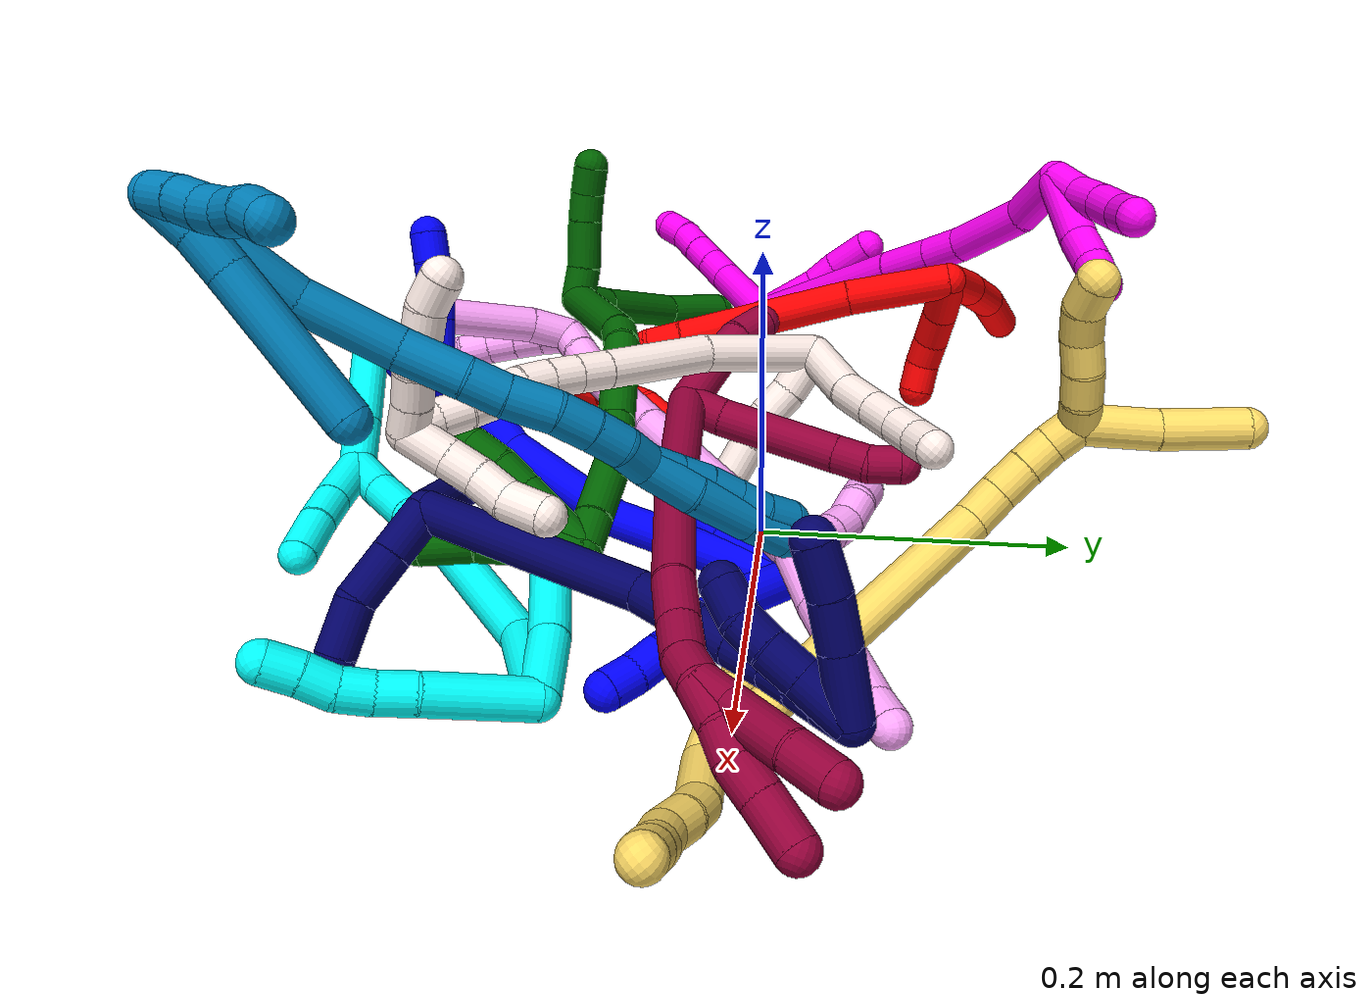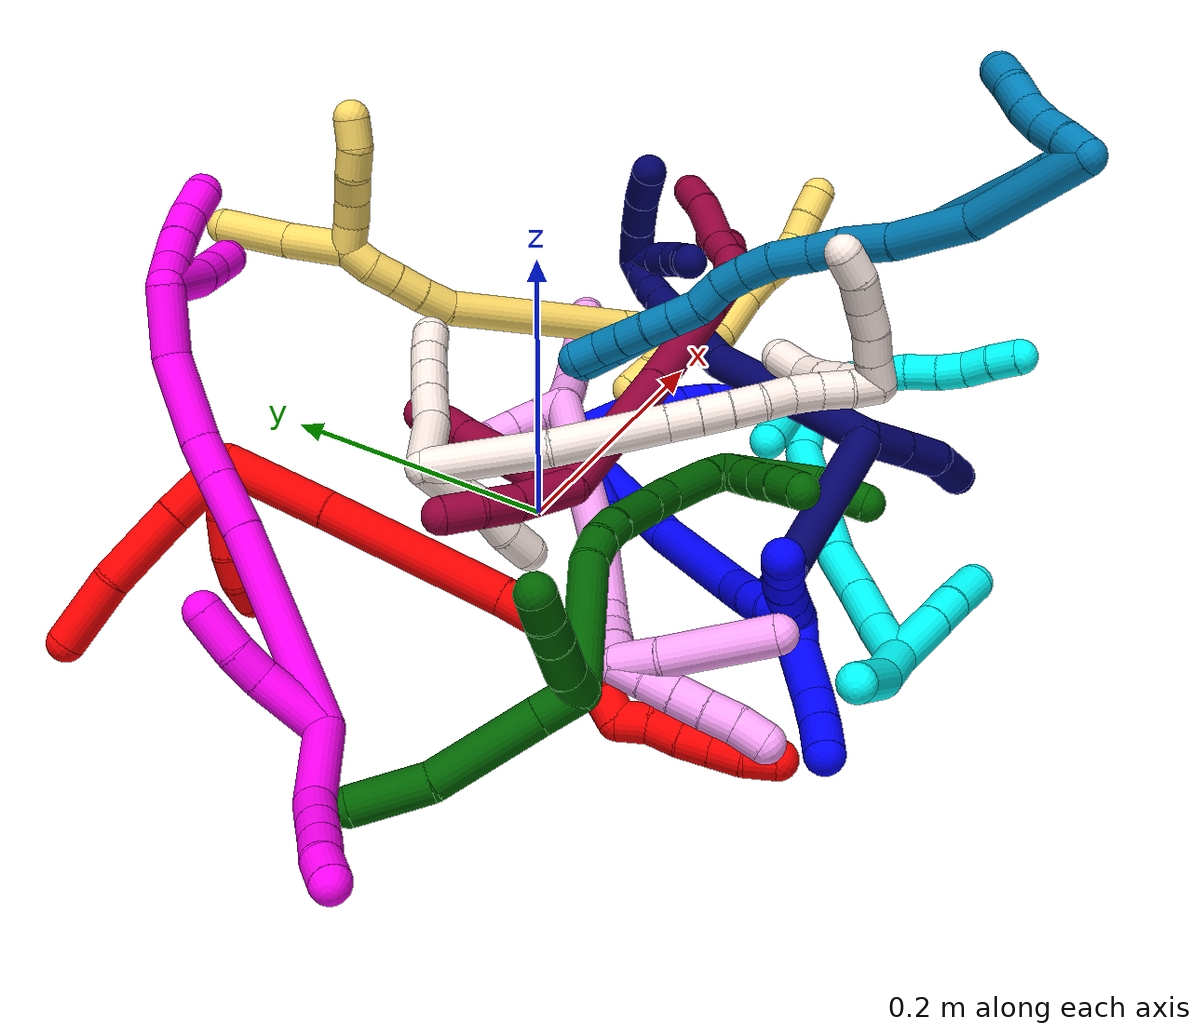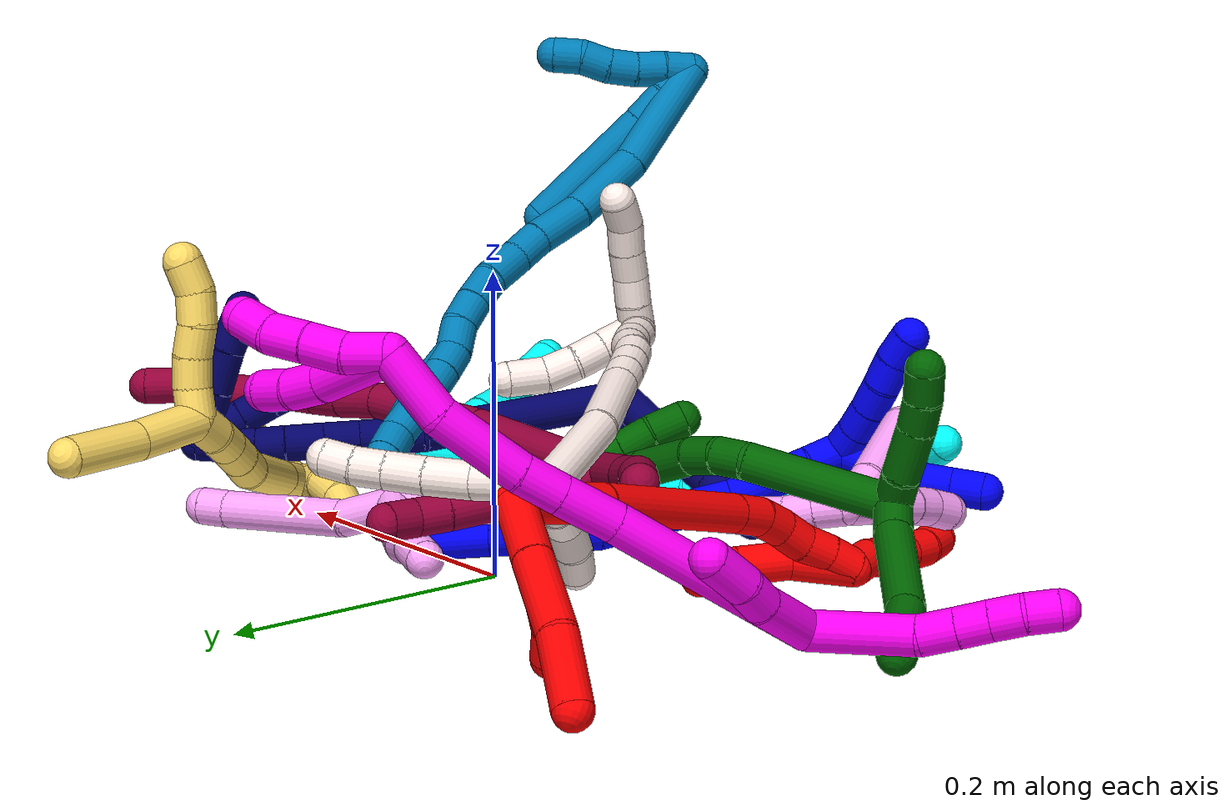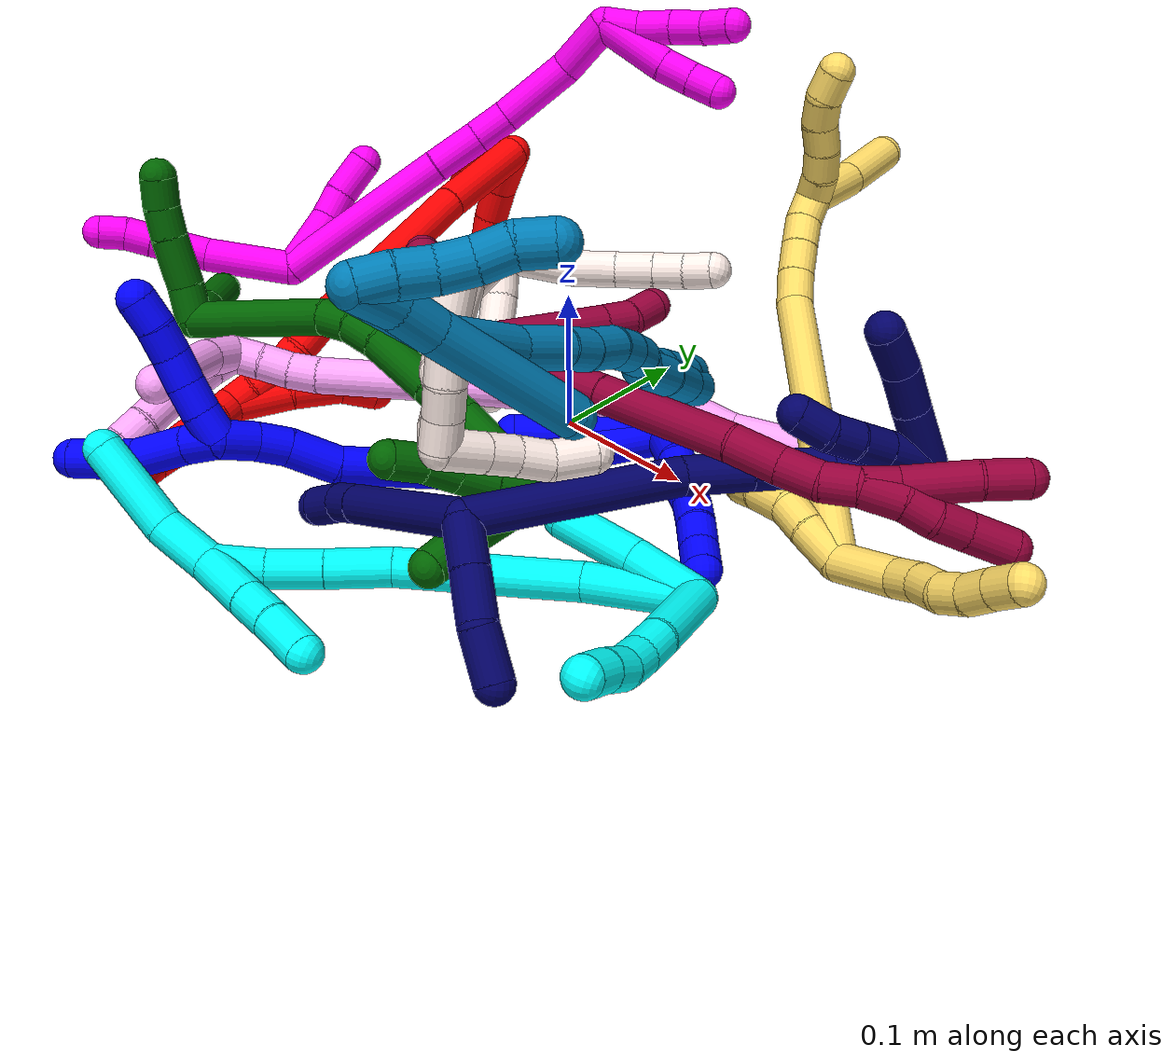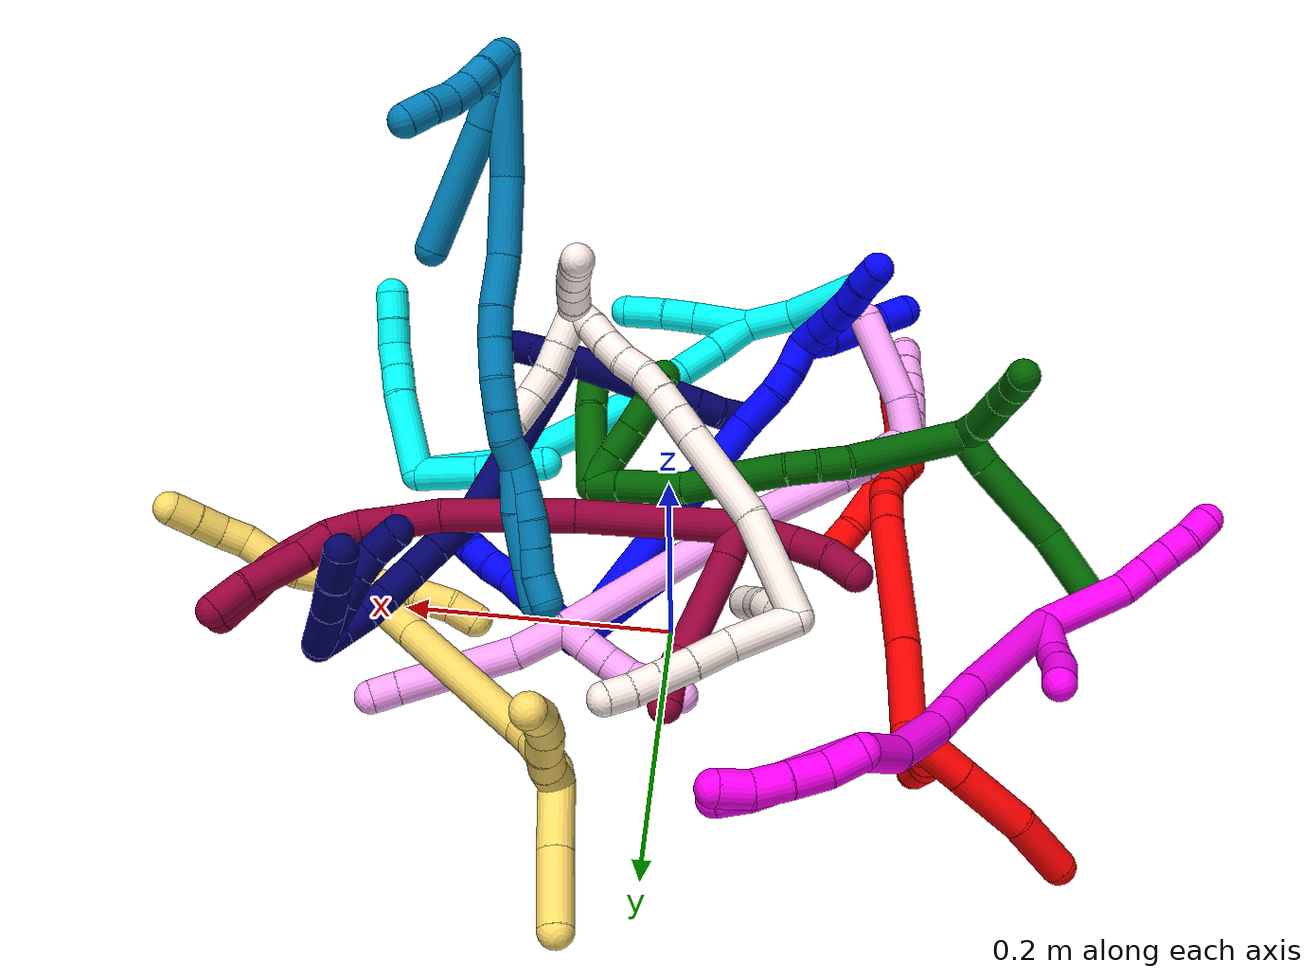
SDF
<sdf version="1.7">
 <world name="default">
  <plugin name="TubeGeneratorPlugin" filename="libtube_generator_plugin.so"/>
  <model name="photoneo_s_sensor">
   <static>1</static>
   <pose>0 0 2 1.57079 1.57079 3.14159</pose>
   <link name="link">
    <inertial><mass>0.1</mass></inertial>
    <sensor name="sensor" type="depth">
     <update_rate>30</update_rate>
     <camera>
      <horizontal_fov>1.22</horizontal_fov>
      <image><width>1920</width><height>1200</height><format>B8G8R8</format></image>
      <clip><near>0.1</near><far>4</far></clip>
      <depth_camera><output>points</output></depth_camera>
     </camera>
     <plugin name="camera_plugin" filename="libgazebo_ros_depth_camera.so">
      <baseline>0.2</baseline>
      <alwaysOn>1</alwaysOn>
      <updateRate>0.0</updateRate>
      <cameraName>camera_ir</cameraName>
      <imageTopicName>/camera/color/image_raw</imageTopicName>
      <cameraInfoTopicName>/camera/color/camera_info</cameraInfoTopicName>
      <depthImageTopicName>/camera/depth/image_raw</depthImageTopicName>
      <depthImageCameraInfoTopicName>/camera/depth/camera_info</depthImageCameraInfoTopicName>
      <pointCloudTopicName>/camera/depth/points</pointCloudTopicName>
      <frameName>fr_optical</frameName>
      <pointCloudCutoff>0.1</pointCloudCutoff>
      <pointCloudCutoffMax>2.0</pointCloudCutoffMax>
      <distortionK1>0</distortionK1>
      <distortionK2>0</distortionK2>
      <distortionK3>0</distortionK3>
      <distortionT1>0</distortionT1>
      <distortionT2>0</distortionT2>
      <CxPrime>0</CxPrime>
      <Cx>0</Cx>
      <Cy>0</Cy>
      <focalLength>0</focalLength>
      <hackBaseline>0</hackBaseline>
     </plugin>
    </sensor>
   </link>
  </model>
  <gravity>0 0 -9.8</gravity>
  <magnetic_field>6e-06 2.3e-05 -4.2e-05</magnetic_field>
  <atmosphere type="adiabatic"/>
  <physics name="default_physics" default="0" type="ode">
   <max_step_size>0.003</max_step_size>
   <real_time_factor>1</real_time_factor>
   <real_time_update_rate>1000</real_time_update_rate>
   <max_contacts>10000</max_contacts>
   <ode>
    <solver>
     <type>quick</type>
     <iters>100</iters>
     <sor>1.3</sor>
     <use_dynamic_moi_rescaling>0</use_dynamic_moi_rescaling>
    </solver>
    <constraints>
     <contact_max_correcting_vel>0</contact_max_correcting_vel>
     <contact_surface_layer>0.001</contact_surface_layer>
     <cfm>0</cfm>
     <erp>0.2</erp>
    </constraints>
   </ode>
  </physics>
  <scene><ambient>0.4 0.4 0.4 1</ambient><background>0.7 0.7 0.7 1</background><shadows>0</shadows></scene>
  <audio><device>default</device></audio>
  <spherical_coordinates>
   <surface_model>EARTH_WGS84</surface_model>
   <latitude_deg>0</latitude_deg>
   <longitude_deg>0</longitude_deg>
   <elevation>0</elevation>
   <heading_deg>0</heading_deg>
  </spherical_coordinates>
  <model name="bin">
   <static>1</static>
   <link name="bottom">
    <collision name="collision-bottom">
     <pose>0 0 -0.01 0 -0 0</pose>
     <geometry><box><size>0.8 0.6 0.02</size></box></geometry>
     <surface>
      <friction><ode><mu>100</mu><mu2>100</mu2></ode></friction>
      <contact><collide_bitmask>65535</collide_bitmask></contact>
     </surface>
    </collision>
   </link>
   <link name="west_wall">
    <collision name="collision-west_wall">
     <pose>-0.41 0 0.1 0 -0 0</pose>
     <geometry><box><size>0.02 0.6 0.2</size></box></geometry>
     <surface>
      <friction><ode><mu>100</mu><mu2>100</mu2></ode></friction>
      <contact><collide_bitmask>65535</collide_bitmask></contact>
     </surface>
    </collision>
   </link>
   <link name="east_wall">
    <collision name="collision-east_wall">
     <pose>0.41 0 0.1 0 -0 0</pose>
     <geometry><box><size>0.02 0.6 0.2</size></box></geometry>
     <surface>
      <friction><ode><mu>100</mu><mu2>100</mu2></ode></friction>
      <contact><collide_bitmask>65535</collide_bitmask></contact>
     </surface>
    </collision>
   </link>
   <link name="south_wall">
    <collision name="collision-south_wall">
     <pose>0 -0.31 0.1 0 -0 0</pose>
     <geometry><box><size>0.8 0.02 0.2</size></box></geometry>
     <surface>
      <friction><ode><mu>100</mu><mu2>100</mu2></ode></friction>
      <contact><collide_bitmask>65535</collide_bitmask></contact>
     </surface>
    </collision>
   </link>
   <link name="north_wall">
    <collision name="collision-north_wall">
     <pose>0 0.31 0.1 0 -0 0</pose>
     <geometry><box><size>0.8 0.02 0.2</size></box></geometry>
     <surface>
      <friction><ode><mu>100</mu><mu2>100</mu2></ode></friction>
      <contact><collide_bitmask>65535</collide_bitmask></contact>
     </surface>
    </collision>
   </link>
  </model>
  <model name="1">
   <static>0</static>
   <link name="1">
    <collision name="collision-cylinder-e_1_2_8">
     <pose>0.020277 -0.008296 0.001987 1.33573 1.17259 0.965195</pose>
     <geometry><cylinder><radius>0.0125</radius><length>0.043996</length></cylinder></geometry>
     <surface>
      <friction><ode><mu>1.16</mu><mu2>1.16</mu2><slip1>0</slip1><slip2>0</slip2></ode></friction>
      <contact><ode><kp>1e+06</kp><kd>1</kd><max_vel>0</max_vel><min_depth>0.001</min_depth></ode></contact>
     </surface>
    </collision>
    <visual name="visual-cylinder-e_1_2_8">
     <pose>0.020277 -0.008296 0.001987 1.33573 1.17259 0.965195</pose>
     <geometry><cylinder><radius>0.0125</radius><length>0.043996</length></cylinder></geometry>
     <material><ambient>0 0 1 1</ambient></material>
    </visual>
    <collision name="collision-cylinder-e_2_8_9">
     <pose>0.050635 -0.024394 0.005424 1.38695 0.903838 0.767009</pose>
     <geometry><cylinder><radius>0.0125</radius><length>0.02566</length></cylinder></geometry>
     <surface>
      <friction><ode><mu>1.16</mu><mu2>1.16</mu2><slip1>0</slip1><slip2>0</slip2></ode></friction>
      <contact><ode><kp>1e+06</kp><kd>1</kd><max_vel>0</max_vel><min_depth>0.001</min_depth></ode></contact>
     </surface>
    </collision>
    <visual name="visual-cylinder-e_2_8_9">
     <pose>0.050635 -0.024394 0.005424 1.38695 0.903838 0.767009</pose>
     <geometry><cylinder><radius>0.0125</radius><length>0.02566</length></cylinder></geometry>
     <material><ambient>0 0 1 1</ambient></material>
    </visual>
    <collision name="collision-cylinder-e_3_9_10">
     <pose>0.068963 -0.037967 0.006415 1.65035 0.958826 1.02547</pose>
     <geometry><cylinder><radius>0.0125</radius><length>0.020154</length></cylinder></geometry>
     <surface>
      <friction><ode><mu>1.16</mu><mu2>1.16</mu2><slip1>0</slip1><slip2>0</slip2></ode></friction>
      <contact><ode><kp>1e+06</kp><kd>1</kd><max_vel>0</max_vel><min_depth>0.001</min_depth></ode></contact>
     </surface>
    </collision>
    <visual name="visual-cylinder-e_3_9_10">
     <pose>0.068963 -0.037967 0.006415 1.65035 0.958826 1.02547</pose>
     <geometry><cylinder><radius>0.0125</radius><length>0.020154</length></cylinder></geometry>
     <material><ambient>0 0 1 1</ambient></material>
    </visual>
    <collision name="collision-cylinder-e_4_10_11">
     <pose>0.084883 -0.050112 0.007076 1.39672 0.870003 0.743887</pose>
     <geometry><cylinder><radius>0.0125</radius><length>0.020075</length></cylinder></geometry>
     <surface>
      <friction><ode><mu>1.16</mu><mu2>1.16</mu2><slip1>0</slip1><slip2>0</slip2></ode></friction>
      <contact><ode><kp>1e+06</kp><kd>1</kd><max_vel>0</max_vel><min_depth>0.001</min_depth></ode></contact>
     </surface>
    </collision>
    <visual name="visual-cylinder-e_4_10_11">
     <pose>0.084883 -0.050112 0.007076 1.39672 0.870003 0.743887</pose>
     <geometry><cylinder><radius>0.0125</radius><length>0.020075</length></cylinder></geometry>
     <material><ambient>0 0 1 1</ambient></material>
    </visual>
    <collision name="collision-cylinder-e_5_11_12">
     <pose>0.099267 -0.063833 0.009389 1.40992 0.733861 0.632069</pose>
     <geometry><cylinder><radius>0.0125</radius><length>0.020045</length></cylinder></geometry>
     <surface>
      <friction><ode><mu>1.16</mu><mu2>1.16</mu2><slip1>0</slip1><slip2>0</slip2></ode></friction>
      <contact><ode><kp>1e+06</kp><kd>1</kd><max_vel>0</max_vel><min_depth>0.001</min_depth></ode></contact>
     </surface>
    </collision>
    <visual name="visual-cylinder-e_5_11_12">
     <pose>0.099267 -0.063833 0.009389 1.40992 0.733861 0.632069</pose>
     <geometry><cylinder><radius>0.0125</radius><length>0.020045</length></cylinder></geometry>
     <material><ambient>0 0 1 1</ambient></material>
    </visual>
    <collision name="collision-cylinder-e_6_12_6">
     <pose>0.113801 -0.077255 0.012202 1.31012 0.893636 0.705382</pose>
     <geometry><cylinder><radius>0.0125</radius><length>0.020071</length></cylinder></geometry>
     <surface>
      <friction><ode><mu>1.16</mu><mu2>1.16</mu2><slip1>0</slip1><slip2>0</slip2></ode></friction>
      <contact><ode><kp>1e+06</kp><kd>1</kd><max_vel>0</max_vel><min_depth>0.001</min_depth></ode></contact>
     </surface>
    </collision>
    <visual name="visual-cylinder-e_6_12_6">
     <pose>0.113801 -0.077255 0.012202 1.31012 0.893636 0.705382</pose>
     <geometry><cylinder><radius>0.0125</radius><length>0.020071</length></cylinder></geometry>
     <material><ambient>0 0 1 1</ambient></material>
    </visual>
    <collision name="collision-cylinder-e_1_2_13">
     <pose>-0.004992 0.000187 0.027195 -0.006864 -0.181547 0.000625</pose>
     <geometry><cylinder><radius>0.0125</radius><length>0.0553</length></cylinder></geometry>
     <surface>
      <friction><ode><mu>1.16</mu><mu2>1.16</mu2><slip1>0</slip1><slip2>0</slip2></ode></friction>
      <contact><ode><kp>1e+06</kp><kd>1</kd><max_vel>0</max_vel><min_depth>0.001</min_depth></ode></contact>
     </surface>
    </collision>
    <visual name="visual-cylinder-e_1_2_13">
     <pose>-0.004992 0.000187 0.027195 -0.006864 -0.181547 0.000625</pose>
     <geometry><cylinder><radius>0.0125</radius><length>0.0553</length></cylinder></geometry>
     <material><ambient>0 0 1 1</ambient></material>
    </visual>
    <collision name="collision-cylinder-e_2_13_5">
     <pose>-0.015458 -5.1e-05 0.076055 0.019561 -0.247419 -0.002432</pose>
     <geometry><cylinder><radius>0.0125</radius><length>0.0447</length></cylinder></geometry>
     <surface>
      <friction><ode><mu>1.16</mu><mu2>1.16</mu2><slip1>0</slip1><slip2>0</slip2></ode></friction>
      <contact><ode><kp>1e+06</kp><kd>1</kd><max_vel>0</max_vel><min_depth>0.001</min_depth></ode></contact>
     </surface>
    </collision>
    <visual name="visual-cylinder-e_2_13_5">
     <pose>-0.015458 -5.1e-05 0.076055 0.019561 -0.247419 -0.002432</pose>
     <geometry><cylinder><radius>0.0125</radius><length>0.0447</length></cylinder></geometry>
     <material><ambient>0 0 1 1</ambient></material>
    </visual>
    <collision name="collision-cylinder-e_1_2_14">
     <pose>-0.000609 -0.013612 0.063139 0.21234 -0.009426 -0.001004</pose>
     <geometry><cylinder><radius>0.0125</radius><length>0.129186</length></cylinder></geometry>
     <surface>
      <friction><ode><mu>1.16</mu><mu2>1.16</mu2><slip1>0</slip1><slip2>0</slip2></ode></friction>
      <contact><ode><kp>1e+06</kp><kd>1</kd><max_vel>0</max_vel><min_depth>0.001</min_depth></ode></contact>
     </surface>
    </collision>
    <visual name="visual-cylinder-e_1_2_14">
     <pose>-0.000609 -0.013612 0.063139 0.21234 -0.009426 -0.001004</pose>
     <geometry><cylinder><radius>0.0125</radius><length>0.129186</length></cylinder></geometry>
     <material><ambient>0 0 1 1</ambient></material>
    </visual>
    <collision name="collision-cylinder-e_2_14_15">
     <pose>0.000581 -0.026188 0.172151 -0.022598 0.039177 -0.000443</pose>
     <geometry><cylinder><radius>0.0125</radius><length>0.091838</length></cylinder></geometry>
     <surface>
      <friction><ode><mu>1.16</mu><mu2>1.16</mu2><slip1>0</slip1><slip2>0</slip2></ode></friction>
      <contact><ode><kp>1e+06</kp><kd>1</kd><max_vel>0</max_vel><min_depth>0.001</min_depth></ode></contact>
     </surface>
    </collision>
    <visual name="visual-cylinder-e_2_14_15">
     <pose>0.000581 -0.026188 0.172151 -0.022598 0.039177 -0.000443</pose>
     <geometry><cylinder><radius>0.0125</radius><length>0.091838</length></cylinder></geometry>
     <material><ambient>0 0 1 1</ambient></material>
    </visual>
    <collision name="collision-cylinder-e_3_15_16">
     <pose>0.002566 -0.019824 0.23405 -0.32088 0.011023 -0.001784</pose>
     <geometry><cylinder><radius>0.0125</radius><length>0.033781</length></cylinder></geometry>
     <surface>
      <friction><ode><mu>1.16</mu><mu2>1.16</mu2><slip1>0</slip1><slip2>0</slip2></ode></friction>
      <contact><ode><kp>1e+06</kp><kd>1</kd><max_vel>0</max_vel><min_depth>0.001</min_depth></ode></contact>
     </surface>
    </collision>
    <visual name="visual-cylinder-e_3_15_16">
     <pose>0.002566 -0.019824 0.23405 -0.32088 0.011023 -0.001784</pose>
     <geometry><cylinder><radius>0.0125</radius><length>0.033781</length></cylinder></geometry>
     <material><ambient>0 0 1 1</ambient></material>
    </visual>
    <collision name="collision-cylinder-e_4_16_17">
     <pose>0.004055 -0.012992 0.260588 -0.142266 0.12216 -0.008715</pose>
     <geometry><cylinder><radius>0.0125</radius><length>0.021395</length></cylinder></geometry>
     <surface>
      <friction><ode><mu>1.16</mu><mu2>1.16</mu2><slip1>0</slip1><slip2>0</slip2></ode></friction>
      <contact><ode><kp>1e+06</kp><kd>1</kd><max_vel>0</max_vel><min_depth>0.001</min_depth></ode></contact>
     </surface>
    </collision>
    <visual name="visual-cylinder-e_4_16_17">
     <pose>0.004055 -0.012992 0.260588 -0.142266 0.12216 -0.008715</pose>
     <geometry><cylinder><radius>0.0125</radius><length>0.021395</length></cylinder></geometry>
     <material><ambient>0 0 1 1</ambient></material>
    </visual>
    <collision name="collision-cylinder-e_5_17_1">
     <pose>0.008425 -0.011272 0.282595 -0.018584 0.2606 -0.002435</pose>
     <geometry><cylinder><radius>0.0125</radius><length>0.0238</length></cylinder></geometry>
     <surface>
      <friction><ode><mu>1.16</mu><mu2>1.16</mu2><slip1>0</slip1><slip2>0</slip2></ode></friction>
      <contact><ode><kp>1e+06</kp><kd>1</kd><max_vel>0</max_vel><min_depth>0.001</min_depth></ode></contact>
     </surface>
    </collision>
    <visual name="visual-cylinder-e_5_17_1">
     <pose>0.008425 -0.011272 0.282595 -0.018584 0.2606 -0.002435</pose>
     <geometry><cylinder><radius>0.0125</radius><length>0.0238</length></cylinder></geometry>
     <material><ambient>0 0 1 1</ambient></material>
    </visual>
    <collision name="collision-cylinder-e_1_1_18">
     <pose>0.004728 -0.012856 0.303017 0.19874 -0.638889 -0.065931</pose>
     <geometry><cylinder><radius>0.0125</radius><length>0.022683</length></cylinder></geometry>
     <surface>
      <friction><ode><mu>1.16</mu><mu2>1.16</mu2><slip1>0</slip1><slip2>0</slip2></ode></friction>
      <contact><ode><kp>1e+06</kp><kd>1</kd><max_vel>0</max_vel><min_depth>0.001</min_depth></ode></contact>
     </surface>
    </collision>
    <visual name="visual-cylinder-e_1_1_18">
     <pose>0.004728 -0.012856 0.303017 0.19874 -0.638889 -0.065931</pose>
     <geometry><cylinder><radius>0.0125</radius><length>0.022683</length></cylinder></geometry>
     <material><ambient>0 0 1 1</ambient></material>
    </visual>
    <collision name="collision-cylinder-e_2_18_19">
     <pose>-0.009757 -0.019323 0.326707 0.306258 -0.462558 -0.072659</pose>
     <geometry><cylinder><radius>0.0125</radius><length>0.034609</length></cylinder></geometry>
     <surface>
      <friction><ode><mu>1.16</mu><mu2>1.16</mu2><slip1>0</slip1><slip2>0</slip2></ode></friction>
      <contact><ode><kp>1e+06</kp><kd>1</kd><max_vel>0</max_vel><min_depth>0.001</min_depth></ode></contact>
     </surface>
    </collision>
    <visual name="visual-cylinder-e_2_18_19">
     <pose>-0.009757 -0.019323 0.326707 0.306258 -0.462558 -0.072659</pose>
     <geometry><cylinder><radius>0.0125</radius><length>0.034609</length></cylinder></geometry>
     <material><ambient>0 0 1 1</ambient></material>
    </visual>
    <collision name="collision-cylinder-e_3_19_20">
     <pose>-0.021889 -0.024622 0.350734 0.067939 -0.443586 -0.015326</pose>
     <geometry><cylinder><radius>0.0125</radius><length>0.020555</length></cylinder></geometry>
     <surface>
      <friction><ode><mu>1.16</mu><mu2>1.16</mu2><slip1>0</slip1><slip2>0</slip2></ode></friction>
      <contact><ode><kp>1e+06</kp><kd>1</kd><max_vel>0</max_vel><min_depth>0.001</min_depth></ode></contact>
     </surface>
    </collision>
    <visual name="visual-cylinder-e_3_19_20">
     <pose>-0.021889 -0.024622 0.350734 0.067939 -0.443586 -0.015326</pose>
     <geometry><cylinder><radius>0.0125</radius><length>0.020555</length></cylinder></geometry>
     <material><ambient>0 0 1 1</ambient></material>
    </visual>
    <collision name="collision-cylinder-e_4_20_4">
     <pose>-0.03151 -0.0251 0.369769 -0.015545 -0.489695 0.003884</pose>
     <geometry><cylinder><radius>0.0125</radius><length>0.022153</length></cylinder></geometry>
     <surface>
      <friction><ode><mu>1.16</mu><mu2>1.16</mu2><slip1>0</slip1><slip2>0</slip2></ode></friction>
      <contact><ode><kp>1e+06</kp><kd>1</kd><max_vel>0</max_vel><min_depth>0.001</min_depth></ode></contact>
     </surface>
    </collision>
    <visual name="visual-cylinder-e_4_20_4">
     <pose>-0.03151 -0.0251 0.369769 -0.015545 -0.489695 0.003884</pose>
     <geometry><cylinder><radius>0.0125</radius><length>0.022153</length></cylinder></geometry>
     <material><ambient>0 0 1 1</ambient></material>
    </visual>
    <collision name="collision-cylinder-e_1_1_21">
     <pose>0.011732 -0.002894 0.29986 -0.955684 0.024041 -0.012451</pose>
     <geometry><cylinder><radius>0.0125</radius><length>0.02</length></cylinder></geometry>
     <surface>
      <friction><ode><mu>1.16</mu><mu2>1.16</mu2><slip1>0</slip1><slip2>0</slip2></ode></friction>
      <contact><ode><kp>1e+06</kp><kd>1</kd><max_vel>0</max_vel><min_depth>0.001</min_depth></ode></contact>
     </surface>
    </collision>
    <visual name="visual-cylinder-e_1_1_21">
     <pose>0.011732 -0.002894 0.29986 -0.955684 0.024041 -0.012451</pose>
     <geometry><cylinder><radius>0.0125</radius><length>0.02</length></cylinder></geometry>
     <material><ambient>0 0 1 1</ambient></material>
    </visual>
    <collision name="collision-cylinder-e_2_21_22">
     <pose>0.01262 0.013869 0.310694 -1.03847 0.064814 -0.037053</pose>
     <geometry><cylinder><radius>0.0125</radius><length>0.02</length></cylinder></geometry>
     <surface>
      <friction><ode><mu>1.16</mu><mu2>1.16</mu2><slip1>0</slip1><slip2>0</slip2></ode></friction>
      <contact><ode><kp>1e+06</kp><kd>1</kd><max_vel>0</max_vel><min_depth>0.001</min_depth></ode></contact>
     </surface>
    </collision>
    <visual name="visual-cylinder-e_2_21_22">
     <pose>0.01262 0.013869 0.310694 -1.03847 0.064814 -0.037053</pose>
     <geometry><cylinder><radius>0.0125</radius><length>0.02</length></cylinder></geometry>
     <material><ambient>0 0 1 1</ambient></material>
    </visual>
    <collision name="collision-cylinder-e_3_22_23">
     <pose>0.014421 0.031206 0.32048 -1.07545 0.115585 -0.068978</pose>
     <geometry><cylinder><radius>0.0125</radius><length>0.02</length></cylinder></geometry>
     <surface>
      <friction><ode><mu>1.16</mu><mu2>1.16</mu2><slip1>0</slip1><slip2>0</slip2></ode></friction>
      <contact><ode><kp>1e+06</kp><kd>1</kd><max_vel>0</max_vel><min_depth>0.001</min_depth></ode></contact>
     </surface>
    </collision>
    <visual name="visual-cylinder-e_3_22_23">
     <pose>0.014421 0.031206 0.32048 -1.07545 0.115585 -0.068978</pose>
     <geometry><cylinder><radius>0.0125</radius><length>0.02</length></cylinder></geometry>
     <material><ambient>0 0 1 1</ambient></material>
    </visual>
    <collision name="collision-cylinder-e_4_23_24">
     <pose>0.018028 0.048239 0.330222 -1.02643 0.24795 -0.140232</pose>
     <geometry><cylinder><radius>0.0125</radius><length>0.02</length></cylinder></geometry>
     <surface>
      <friction><ode><mu>1.16</mu><mu2>1.16</mu2><slip1>0</slip1><slip2>0</slip2></ode></friction>
      <contact><ode><kp>1e+06</kp><kd>1</kd><max_vel>0</max_vel><min_depth>0.001</min_depth></ode></contact>
     </surface>
    </collision>
    <visual name="visual-cylinder-e_4_23_24">
     <pose>0.018028 0.048239 0.330222 -1.02643 0.24795 -0.140232</pose>
     <geometry><cylinder><radius>0.0125</radius><length>0.02</length></cylinder></geometry>
     <material><ambient>0 0 1 1</ambient></material>
    </visual>
    <collision name="collision-cylinder-e_5_24_3">
     <pose>0.021853 0.064445 0.341201 -0.92541 0.137525 -0.068682</pose>
     <geometry><cylinder><radius>0.0125</radius><length>0.02</length></cylinder></geometry>
     <surface>
      <friction><ode><mu>1.16</mu><mu2>1.16</mu2><slip1>0</slip1><slip2>0</slip2></ode></friction>
      <contact><ode><kp>1e+06</kp><kd>1</kd><max_vel>0</max_vel><min_depth>0.001</min_depth></ode></contact>
     </surface>
    </collision>
    <visual name="visual-cylinder-e_5_24_3">
     <pose>0.021853 0.064445 0.341201 -0.92541 0.137525 -0.068682</pose>
     <geometry><cylinder><radius>0.0125</radius><length>0.02</length></cylinder></geometry>
     <material><ambient>0 0 1 1</ambient></material>
    </visual>
    <collision name="collision-sphere-3">
     <pose>0.023224 0.072358 0.347159 0 -0 0</pose>
     <geometry><sphere><radius>0.0125</radius></sphere></geometry>
     <surface>
      <friction><ode><mu>1.16</mu><mu2>1.16</mu2><slip1>0</slip1><slip2>0</slip2></ode></friction>
      <contact><ode><kp>1e+06</kp><kd>1</kd><max_vel>0</max_vel><min_depth>0.001</min_depth></ode></contact>
     </surface>
    </collision>
    <visual name="visual-sphere-3">
     <pose>0.023224 0.072358 0.347159 0 -0 0</pose>
     <geometry><sphere><radius>0.0125</radius></sphere></geometry>
     <material><ambient>0 0 1 1</ambient></material>
    </visual>
    <collision name="collision-sphere-24">
     <pose>0.020482 0.056532 0.335242 0 -0 0</pose>
     <geometry><sphere><radius>0.0125</radius></sphere></geometry>
     <surface>
      <friction><ode><mu>1.16</mu><mu2>1.16</mu2><slip1>0</slip1><slip2>0</slip2></ode></friction>
      <contact><ode><kp>1e+06</kp><kd>1</kd><max_vel>0</max_vel><min_depth>0.001</min_depth></ode></contact>
     </surface>
    </collision>
    <visual name="visual-sphere-24">
     <pose>0.020482 0.056532 0.335242 0 -0 0</pose>
     <geometry><sphere><radius>0.0125</radius></sphere></geometry>
     <material><ambient>0 0 1 1</ambient></material>
    </visual>
    <collision name="collision-sphere-23">
     <pose>0.015574 0.039946 0.325202 0 -0 0</pose>
     <geometry><sphere><radius>0.0125</radius></sphere></geometry>
     <surface>
      <friction><ode><mu>1.16</mu><mu2>1.16</mu2><slip1>0</slip1><slip2>0</slip2></ode></friction>
      <contact><ode><kp>1e+06</kp><kd>1</kd><max_vel>0</max_vel><min_depth>0.001</min_depth></ode></contact>
     </surface>
    </collision>
    <visual name="visual-sphere-23">
     <pose>0.015574 0.039946 0.325202 0 -0 0</pose>
     <geometry><sphere><radius>0.0125</radius></sphere></geometry>
     <material><ambient>0 0 1 1</ambient></material>
    </visual>
    <collision name="collision-sphere-22">
     <pose>0.013267 0.022467 0.315758 0 -0 0</pose>
     <geometry><sphere><radius>0.0125</radius></sphere></geometry>
     <surface>
      <friction><ode><mu>1.16</mu><mu2>1.16</mu2><slip1>0</slip1><slip2>0</slip2></ode></friction>
      <contact><ode><kp>1e+06</kp><kd>1</kd><max_vel>0</max_vel><min_depth>0.001</min_depth></ode></contact>
     </surface>
    </collision>
    <visual name="visual-sphere-22">
     <pose>0.013267 0.022467 0.315758 0 -0 0</pose>
     <geometry><sphere><radius>0.0125</radius></sphere></geometry>
     <material><ambient>0 0 1 1</ambient></material>
    </visual>
    <collision name="collision-sphere-21">
     <pose>0.011972 0.005271 0.305629 0 -0 0</pose>
     <geometry><sphere><radius>0.0125</radius></sphere></geometry>
     <surface>
      <friction><ode><mu>1.16</mu><mu2>1.16</mu2><slip1>0</slip1><slip2>0</slip2></ode></friction>
      <contact><ode><kp>1e+06</kp><kd>1</kd><max_vel>0</max_vel><min_depth>0.001</min_depth></ode></contact>
     </surface>
    </collision>
    <visual name="visual-sphere-21">
     <pose>0.011972 0.005271 0.305629 0 -0 0</pose>
     <geometry><sphere><radius>0.0125</radius></sphere></geometry>
     <material><ambient>0 0 1 1</ambient></material>
    </visual>
    <collision name="collision-sphere-4">
     <pose>-0.03672 -0.024948 0.379543 0 -0 0</pose>
     <geometry><sphere><radius>0.0125</radius></sphere></geometry>
     <surface>
      <friction><ode><mu>1.16</mu><mu2>1.16</mu2><slip1>0</slip1><slip2>0</slip2></ode></friction>
      <contact><ode><kp>1e+06</kp><kd>1</kd><max_vel>0</max_vel><min_depth>0.001</min_depth></ode></contact>
     </surface>
    </collision>
    <visual name="visual-sphere-4">
     <pose>-0.03672 -0.024948 0.379543 0 -0 0</pose>
     <geometry><sphere><radius>0.0125</radius></sphere></geometry>
     <material><ambient>0 0 1 1</ambient></material>
    </visual>
    <collision name="collision-sphere-20">
     <pose>-0.0263 -0.025252 0.359995 0 -0 0</pose>
     <geometry><sphere><radius>0.0125</radius></sphere></geometry>
     <surface>
      <friction><ode><mu>1.16</mu><mu2>1.16</mu2><slip1>0</slip1><slip2>0</slip2></ode></friction>
      <contact><ode><kp>1e+06</kp><kd>1</kd><max_vel>0</max_vel><min_depth>0.001</min_depth></ode></contact>
     </surface>
    </collision>
    <visual name="visual-sphere-20">
     <pose>-0.0263 -0.025252 0.359995 0 -0 0</pose>
     <geometry><sphere><radius>0.0125</radius></sphere></geometry>
     <material><ambient>0 0 1 1</ambient></material>
    </visual>
    <collision name="collision-sphere-12">
     <pose>0.10598 -0.07118 0.010581 0 -0 0</pose>
     <geometry><sphere><radius>0.0125</radius></sphere></geometry>
     <surface>
      <friction><ode><mu>1.16</mu><mu2>1.16</mu2><slip1>0</slip1><slip2>0</slip2></ode></friction>
      <contact><ode><kp>1e+06</kp><kd>1</kd><max_vel>0</max_vel><min_depth>0.001</min_depth></ode></contact>
     </surface>
    </collision>
    <visual name="visual-sphere-12">
     <pose>0.10598 -0.07118 0.010581 0 -0 0</pose>
     <geometry><sphere><radius>0.0125</radius></sphere></geometry>
     <material><ambient>0 0 1 1</ambient></material>
    </visual>
    <collision name="collision-sphere-11">
     <pose>0.092555 -0.056487 0.008197 0 -0 0</pose>
     <geometry><sphere><radius>0.0125</radius></sphere></geometry>
     <surface>
      <friction><ode><mu>1.16</mu><mu2>1.16</mu2><slip1>0</slip1><slip2>0</slip2></ode></friction>
      <contact><ode><kp>1e+06</kp><kd>1</kd><max_vel>0</max_vel><min_depth>0.001</min_depth></ode></contact>
     </surface>
    </collision>
    <visual name="visual-sphere-11">
     <pose>0.092555 -0.056487 0.008197 0 -0 0</pose>
     <geometry><sphere><radius>0.0125</radius></sphere></geometry>
     <material><ambient>0 0 1 1</ambient></material>
    </visual>
    <collision name="collision-sphere-10">
     <pose>0.077211 -0.043738 0.005955 0 -0 0</pose>
     <geometry><sphere><radius>0.0125</radius></sphere></geometry>
     <surface>
      <friction><ode><mu>1.16</mu><mu2>1.16</mu2><slip1>0</slip1><slip2>0</slip2></ode></friction>
      <contact><ode><kp>1e+06</kp><kd>1</kd><max_vel>0</max_vel><min_depth>0.001</min_depth></ode></contact>
     </surface>
    </collision>
    <visual name="visual-sphere-10">
     <pose>0.077211 -0.043738 0.005955 0 -0 0</pose>
     <geometry><sphere><radius>0.0125</radius></sphere></geometry>
     <material><ambient>0 0 1 1</ambient></material>
    </visual>
    <collision name="collision-sphere-9">
     <pose>0.060715 -0.032197 0.006875 0 -0 0</pose>
     <geometry><sphere><radius>0.0125</radius></sphere></geometry>
     <surface>
      <friction><ode><mu>1.16</mu><mu2>1.16</mu2><slip1>0</slip1><slip2>0</slip2></ode></friction>
      <contact><ode><kp>1e+06</kp><kd>1</kd><max_vel>0</max_vel><min_depth>0.001</min_depth></ode></contact>
     </surface>
    </collision>
    <visual name="visual-sphere-9">
     <pose>0.060715 -0.032197 0.006875 0 -0 0</pose>
     <geometry><sphere><radius>0.0125</radius></sphere></geometry>
     <material><ambient>0 0 1 1</ambient></material>
    </visual>
    <collision name="collision-sphere-2">
     <geometry><sphere><radius>0.0125</radius></sphere></geometry>
     <surface>
      <friction><ode><mu>1.16</mu><mu2>1.16</mu2><slip1>0</slip1><slip2>0</slip2></ode></friction>
      <contact><ode><kp>1e+06</kp><kd>1</kd><max_vel>0</max_vel><min_depth>0.001</min_depth></ode></contact>
     </surface>
    </collision>
    <visual name="visual-sphere-2">
     <geometry><sphere><radius>0.0125</radius></sphere></geometry>
     <material><ambient>0 0 1 1</ambient></material>
    </visual>
    <collision name="collision-sphere-19">
     <pose>-0.017479 -0.023992 0.341473 0 -0 0</pose>
     <geometry><sphere><radius>0.0125</radius></sphere></geometry>
     <surface>
      <friction><ode><mu>1.16</mu><mu2>1.16</mu2><slip1>0</slip1><slip2>0</slip2></ode></friction>
      <contact><ode><kp>1e+06</kp><kd>1</kd><max_vel>0</max_vel><min_depth>0.001</min_depth></ode></contact>
     </surface>
    </collision>
    <visual name="visual-sphere-19">
     <pose>-0.017479 -0.023992 0.341473 0 -0 0</pose>
     <geometry><sphere><radius>0.0125</radius></sphere></geometry>
     <material><ambient>0 0 1 1</ambient></material>
    </visual>
    <collision name="collision-sphere-8">
     <pose>0.040554 -0.016591 0.003973 0 -0 0</pose>
     <geometry><sphere><radius>0.0125</radius></sphere></geometry>
     <surface>
      <friction><ode><mu>1.16</mu><mu2>1.16</mu2><slip1>0</slip1><slip2>0</slip2></ode></friction>
      <contact><ode><kp>1e+06</kp><kd>1</kd><max_vel>0</max_vel><min_depth>0.001</min_depth></ode></contact>
     </surface>
    </collision>
    <visual name="visual-sphere-8">
     <pose>0.040554 -0.016591 0.003973 0 -0 0</pose>
     <geometry><sphere><radius>0.0125</radius></sphere></geometry>
     <material><ambient>0 0 1 1</ambient></material>
    </visual>
    <collision name="collision-sphere-6">
     <pose>0.121622 -0.083331 0.013823 0 -0 0</pose>
     <geometry><sphere><radius>0.0125</radius></sphere></geometry>
     <surface>
      <friction><ode><mu>1.16</mu><mu2>1.16</mu2><slip1>0</slip1><slip2>0</slip2></ode></friction>
      <contact><ode><kp>1e+06</kp><kd>1</kd><max_vel>0</max_vel><min_depth>0.001</min_depth></ode></contact>
     </surface>
    </collision>
    <visual name="visual-sphere-6">
     <pose>0.121622 -0.083331 0.013823 0 -0 0</pose>
     <geometry><sphere><radius>0.0125</radius></sphere></geometry>
     <material><ambient>0 0 1 1</ambient></material>
    </visual>
    <collision name="collision-sphere-13">
     <pose>-0.009985 0.000373 0.05439 0 -0 0</pose>
     <geometry><sphere><radius>0.0125</radius></sphere></geometry>
     <surface>
      <friction><ode><mu>1.16</mu><mu2>1.16</mu2><slip1>0</slip1><slip2>0</slip2></ode></friction>
      <contact><ode><kp>1e+06</kp><kd>1</kd><max_vel>0</max_vel><min_depth>0.001</min_depth></ode></contact>
     </surface>
    </collision>
    <visual name="visual-sphere-13">
     <pose>-0.009985 0.000373 0.05439 0 -0 0</pose>
     <geometry><sphere><radius>0.0125</radius></sphere></geometry>
     <material><ambient>0 0 1 1</ambient></material>
    </visual>
    <collision name="collision-sphere-5">
     <pose>-0.020932 -0.000474 0.09772 0 -0 0</pose>
     <geometry><sphere><radius>0.0125</radius></sphere></geometry>
     <surface>
      <friction><ode><mu>1.16</mu><mu2>1.16</mu2><slip1>0</slip1><slip2>0</slip2></ode></friction>
      <contact><ode><kp>1e+06</kp><kd>1</kd><max_vel>0</max_vel><min_depth>0.001</min_depth></ode></contact>
     </surface>
    </collision>
    <visual name="visual-sphere-5">
     <pose>-0.020932 -0.000474 0.09772 0 -0 0</pose>
     <geometry><sphere><radius>0.0125</radius></sphere></geometry>
     <material><ambient>0 0 1 1</ambient></material>
    </visual>
    <collision name="collision-sphere-14">
     <pose>-0.001218 -0.027224 0.126279 0 -0 0</pose>
     <geometry><sphere><radius>0.0125</radius></sphere></geometry>
     <surface>
      <friction><ode><mu>1.16</mu><mu2>1.16</mu2><slip1>0</slip1><slip2>0</slip2></ode></friction>
      <contact><ode><kp>1e+06</kp><kd>1</kd><max_vel>0</max_vel><min_depth>0.001</min_depth></ode></contact>
     </surface>
    </collision>
    <visual name="visual-sphere-14">
     <pose>-0.001218 -0.027224 0.126279 0 -0 0</pose>
     <geometry><sphere><radius>0.0125</radius></sphere></geometry>
     <material><ambient>0 0 1 1</ambient></material>
    </visual>
    <collision name="collision-sphere-15">
     <pose>0.002379 -0.025151 0.218023 0 -0 0</pose>
     <geometry><sphere><radius>0.0125</radius></sphere></geometry>
     <surface>
      <friction><ode><mu>1.16</mu><mu2>1.16</mu2><slip1>0</slip1><slip2>0</slip2></ode></friction>
      <contact><ode><kp>1e+06</kp><kd>1</kd><max_vel>0</max_vel><min_depth>0.001</min_depth></ode></contact>
     </surface>
    </collision>
    <visual name="visual-sphere-15">
     <pose>0.002379 -0.025151 0.218023 0 -0 0</pose>
     <geometry><sphere><radius>0.0125</radius></sphere></geometry>
     <material><ambient>0 0 1 1</ambient></material>
    </visual>
    <collision name="collision-sphere-16">
     <pose>0.002752 -0.014497 0.250077 0 -0 0</pose>
     <geometry><sphere><radius>0.0125</radius></sphere></geometry>
     <surface>
      <friction><ode><mu>1.16</mu><mu2>1.16</mu2><slip1>0</slip1><slip2>0</slip2></ode></friction>
      <contact><ode><kp>1e+06</kp><kd>1</kd><max_vel>0</max_vel><min_depth>0.001</min_depth></ode></contact>
     </surface>
    </collision>
    <visual name="visual-sphere-16">
     <pose>0.002752 -0.014497 0.250077 0 -0 0</pose>
     <geometry><sphere><radius>0.0125</radius></sphere></geometry>
     <material><ambient>0 0 1 1</ambient></material>
    </visual>
    <collision name="collision-sphere-17">
     <pose>0.005359 -0.011486 0.271098 0 -0 0</pose>
     <geometry><sphere><radius>0.0125</radius></sphere></geometry>
     <surface>
      <friction><ode><mu>1.16</mu><mu2>1.16</mu2><slip1>0</slip1><slip2>0</slip2></ode></friction>
      <contact><ode><kp>1e+06</kp><kd>1</kd><max_vel>0</max_vel><min_depth>0.001</min_depth></ode></contact>
     </surface>
    </collision>
    <visual name="visual-sphere-17">
     <pose>0.005359 -0.011486 0.271098 0 -0 0</pose>
     <geometry><sphere><radius>0.0125</radius></sphere></geometry>
     <material><ambient>0 0 1 1</ambient></material>
    </visual>
    <collision name="collision-sphere-1">
     <pose>0.011491 -0.011059 0.294091 0 -0 0</pose>
     <geometry><sphere><radius>0.0125</radius></sphere></geometry>
     <surface>
      <friction><ode><mu>1.16</mu><mu2>1.16</mu2><slip1>0</slip1><slip2>0</slip2></ode></friction>
      <contact><ode><kp>1e+06</kp><kd>1</kd><max_vel>0</max_vel><min_depth>0.001</min_depth></ode></contact>
     </surface>
    </collision>
    <visual name="visual-sphere-1">
     <pose>0.011491 -0.011059 0.294091 0 -0 0</pose>
     <geometry><sphere><radius>0.0125</radius></sphere></geometry>
     <material><ambient>0 0 1 1</ambient></material>
    </visual>
    <collision name="collision-sphere-18">
     <pose>-0.002035 -0.014654 0.311942 0 -0 0</pose>
     <geometry><sphere><radius>0.0125</radius></sphere></geometry>
     <surface>
      <friction><ode><mu>1.16</mu><mu2>1.16</mu2><slip1>0</slip1><slip2>0</slip2></ode></friction>
      <contact><ode><kp>1e+06</kp><kd>1</kd><max_vel>0</max_vel><min_depth>0.001</min_depth></ode></contact>
     </surface>
    </collision>
    <visual name="visual-sphere-18">
     <pose>-0.002035 -0.014654 0.311942 0 -0 0</pose>
     <geometry><sphere><radius>0.0125</radius></sphere></geometry>
     <material><ambient>0 0 1 1</ambient></material>
    </visual>
    <inertial>
     <pose>0.012181 -0.013185 0.154186 0 -0 0</pose>
     <mass>0.75</mass>
     <inertia>
      <ixx>0.000319</ixx>
      <ixy>0</ixy>
      <ixz>0</ixz>
      <iyy>0.000312</iyy>
      <iyz>0</iyz>
      <izz>7.5e-05</izz>
     </inertia>
    </inertial>
   </link>
   <pose>0.068292 0.020136 0.011259 1.34965 -0.573006 -0.460744</pose>
  </model>
  <model name="2">
   <static>0</static>
   <link name="2">
    <collision name="collision-cylinder-e_1_2_8">
     <pose>-0.012271 0.006217 -0.018693 -2.82051 -0.557111 2.11116</pose>
     <geometry><cylinder><radius>0.0125</radius><length>0.046418</length></cylinder></geometry>
     <surface>
      <friction><ode><mu>1.16</mu><mu2>1.16</mu2><slip1>0</slip1><slip2>0</slip2></ode></friction>
      <contact><ode><kp>1e+06</kp><kd>1</kd><max_vel>0</max_vel><min_depth>0.001</min_depth></ode></contact>
     </surface>
    </collision>
    <visual name="visual-cylinder-e_1_2_8">
     <pose>-0.012271 0.006217 -0.018693 -2.82051 -0.557111 2.11116</pose>
     <geometry><cylinder><radius>0.0125</radius><length>0.046418</length></cylinder></geometry>
     <material><ambient>1 0 0 1</ambient></material>
    </visual>
    <collision name="collision-cylinder-e_2_8_9">
     <pose>-0.039625 0.01814 -0.05998 -2.89423 -0.574411 2.34483</pose>
     <geometry><cylinder><radius>0.0125</radius><length>0.055517</length></cylinder></geometry>
     <surface>
      <friction><ode><mu>1.16</mu><mu2>1.16</mu2><slip1>0</slip1><slip2>0</slip2></ode></friction>
      <contact><ode><kp>1e+06</kp><kd>1</kd><max_vel>0</max_vel><min_depth>0.001</min_depth></ode></contact>
     </surface>
    </collision>
    <visual name="visual-cylinder-e_2_8_9">
     <pose>-0.039625 0.01814 -0.05998 -2.89423 -0.574411 2.34483</pose>
     <geometry><cylinder><radius>0.0125</radius><length>0.055517</length></cylinder></geometry>
     <material><ambient>1 0 0 1</ambient></material>
    </visual>
    <collision name="collision-cylinder-e_3_9_6">
     <pose>-0.06566 0.024719 -0.103948 -3.10075 -0.473192 2.97258</pose>
     <geometry><cylinder><radius>0.0125</radius><length>0.048065</length></cylinder></geometry>
     <surface>
      <friction><ode><mu>1.16</mu><mu2>1.16</mu2><slip1>0</slip1><slip2>0</slip2></ode></friction>
      <contact><ode><kp>1e+06</kp><kd>1</kd><max_vel>0</max_vel><min_depth>0.001</min_depth></ode></contact>
     </surface>
    </collision>
    <visual name="visual-cylinder-e_3_9_6">
     <pose>-0.06566 0.024719 -0.103948 -3.10075 -0.473192 2.97258</pose>
     <geometry><cylinder><radius>0.0125</radius><length>0.048065</length></cylinder></geometry>
     <material><ambient>1 0 0 1</ambient></material>
    </visual>
    <collision name="collision-cylinder-e_1_2_10">
     <pose>-0.007418 -0.008775 -0.012335 2.5233 -0.455663 -1.25586</pose>
     <geometry><cylinder><radius>0.0125</radius><length>0.033716</length></cylinder></geometry>
     <surface>
      <friction><ode><mu>1.16</mu><mu2>1.16</mu2><slip1>0</slip1><slip2>0</slip2></ode></friction>
      <contact><ode><kp>1e+06</kp><kd>1</kd><max_vel>0</max_vel><min_depth>0.001</min_depth></ode></contact>
     </surface>
    </collision>
    <visual name="visual-cylinder-e_1_2_10">
     <pose>-0.007418 -0.008775 -0.012335 2.5233 -0.455663 -1.25586</pose>
     <geometry><cylinder><radius>0.0125</radius><length>0.033716</length></cylinder></geometry>
     <material><ambient>1 0 0 1</ambient></material>
    </visual>
    <collision name="collision-cylinder-e_2_10_11">
     <pose>-0.019584 -0.025757 -0.033167 2.37346 -0.382098 -0.892714</pose>
     <geometry><cylinder><radius>0.0125</radius><length>0.025463</length></cylinder></geometry>
     <surface>
      <friction><ode><mu>1.16</mu><mu2>1.16</mu2><slip1>0</slip1><slip2>0</slip2></ode></friction>
      <contact><ode><kp>1e+06</kp><kd>1</kd><max_vel>0</max_vel><min_depth>0.001</min_depth></ode></contact>
     </surface>
    </collision>
    <visual name="visual-cylinder-e_2_10_11">
     <pose>-0.019584 -0.025757 -0.033167 2.37346 -0.382098 -0.892714</pose>
     <geometry><cylinder><radius>0.0125</radius><length>0.025463</length></cylinder></geometry>
     <material><ambient>1 0 0 1</ambient></material>
    </visual>
    <collision name="collision-cylinder-e_3_11_12">
     <pose>-0.026692 -0.041776 -0.047529 2.21491 -0.237163 -0.468185</pose>
     <geometry><cylinder><radius>0.0125</radius><length>0.020099</length></cylinder></geometry>
     <surface>
      <friction><ode><mu>1.16</mu><mu2>1.16</mu2><slip1>0</slip1><slip2>0</slip2></ode></friction>
      <contact><ode><kp>1e+06</kp><kd>1</kd><max_vel>0</max_vel><min_depth>0.001</min_depth></ode></contact>
     </surface>
    </collision>
    <visual name="visual-cylinder-e_3_11_12">
     <pose>-0.026692 -0.041776 -0.047529 2.21491 -0.237163 -0.468185</pose>
     <geometry><cylinder><radius>0.0125</radius><length>0.020099</length></cylinder></geometry>
     <material><ambient>1 0 0 1</ambient></material>
    </visual>
    <collision name="collision-cylinder-e_4_12_5">
     <pose>-0.028134 -0.058509 -0.058581 2.09738 0.088869 0.154253</pose>
     <geometry><cylinder><radius>0.0125</radius><length>0.020723</length></cylinder></geometry>
     <surface>
      <friction><ode><mu>1.16</mu><mu2>1.16</mu2><slip1>0</slip1><slip2>0</slip2></ode></friction>
      <contact><ode><kp>1e+06</kp><kd>1</kd><max_vel>0</max_vel><min_depth>0.001</min_depth></ode></contact>
     </surface>
    </collision>
    <visual name="visual-cylinder-e_4_12_5">
     <pose>-0.028134 -0.058509 -0.058581 2.09738 0.088869 0.154253</pose>
     <geometry><cylinder><radius>0.0125</radius><length>0.020723</length></cylinder></geometry>
     <material><ambient>1 0 0 1</ambient></material>
    </visual>
    <collision name="collision-cylinder-e_1_2_13">
     <pose>-0.016958 -0.027421 0.016689 1.02406 -0.486005 -0.276871</pose>
     <geometry><cylinder><radius>0.0125</radius><length>0.072608</length></cylinder></geometry>
     <surface>
      <friction><ode><mu>1.16</mu><mu2>1.16</mu2><slip1>0</slip1><slip2>0</slip2></ode></friction>
      <contact><ode><kp>1e+06</kp><kd>1</kd><max_vel>0</max_vel><min_depth>0.001</min_depth></ode></contact>
     </surface>
    </collision>
    <visual name="visual-cylinder-e_1_2_13">
     <pose>-0.016958 -0.027421 0.016689 1.02406 -0.486005 -0.276871</pose>
     <geometry><cylinder><radius>0.0125</radius><length>0.072608</length></cylinder></geometry>
     <material><ambient>1 0 0 1</ambient></material>
    </visual>
    <collision name="collision-cylinder-e_2_13_14">
     <pose>-0.060354 -0.10376 0.05894 1.08928 -0.44672 -0.273476</pose>
     <geometry><cylinder><radius>0.0125</radius><length>0.122399</length></cylinder></geometry>
     <surface>
      <friction><ode><mu>1.16</mu><mu2>1.16</mu2><slip1>0</slip1><slip2>0</slip2></ode></friction>
      <contact><ode><kp>1e+06</kp><kd>1</kd><max_vel>0</max_vel><min_depth>0.001</min_depth></ode></contact>
     </surface>
    </collision>
    <visual name="visual-cylinder-e_2_13_14">
     <pose>-0.060354 -0.10376 0.05894 1.08928 -0.44672 -0.273476</pose>
     <geometry><cylinder><radius>0.0125</radius><length>0.122399</length></cylinder></geometry>
     <material><ambient>1 0 0 1</ambient></material>
    </visual>
    <collision name="collision-cylinder-e_3_14_15">
     <pose>-0.092633 -0.16224 0.089096 1.12297 -0.503233 -0.320623</pose>
     <geometry><cylinder><radius>0.0125</radius><length>0.02422</length></cylinder></geometry>
     <surface>
      <friction><ode><mu>1.16</mu><mu2>1.16</mu2><slip1>0</slip1><slip2>0</slip2></ode></friction>
      <contact><ode><kp>1e+06</kp><kd>1</kd><max_vel>0</max_vel><min_depth>0.001</min_depth></ode></contact>
     </surface>
    </collision>
    <visual name="visual-cylinder-e_3_14_15">
     <pose>-0.092633 -0.16224 0.089096 1.12297 -0.503233 -0.320623</pose>
     <geometry><cylinder><radius>0.0125</radius><length>0.02422</length></cylinder></geometry>
     <material><ambient>1 0 0 1</ambient></material>
    </visual>
    <collision name="collision-cylinder-e_4_15_16">
     <pose>-0.103609 -0.180615 0.095125 1.40923 -0.522019 -0.44661</pose>
     <geometry><cylinder><radius>0.0125</radius><length>0.020602</length></cylinder></geometry>
     <surface>
      <friction><ode><mu>1.16</mu><mu2>1.16</mu2><slip1>0</slip1><slip2>0</slip2></ode></friction>
      <contact><ode><kp>1e+06</kp><kd>1</kd><max_vel>0</max_vel><min_depth>0.001</min_depth></ode></contact>
     </surface>
    </collision>
    <visual name="visual-cylinder-e_4_15_16">
     <pose>-0.103609 -0.180615 0.095125 1.40923 -0.522019 -0.44661</pose>
     <geometry><cylinder><radius>0.0125</radius><length>0.020602</length></cylinder></geometry>
     <material><ambient>1 0 0 1</ambient></material>
    </visual>
    <collision name="collision-cylinder-e_5_16_17">
     <pose>-0.11493 -0.197357 0.096208 1.61537 -0.661906 -0.689798</pose>
     <geometry><cylinder><radius>0.0125</radius><length>0.020122</length></cylinder></geometry>
     <surface>
      <friction><ode><mu>1.16</mu><mu2>1.16</mu2><slip1>0</slip1><slip2>0</slip2></ode></friction>
      <contact><ode><kp>1e+06</kp><kd>1</kd><max_vel>0</max_vel><min_depth>0.001</min_depth></ode></contact>
     </surface>
    </collision>
    <visual name="visual-cylinder-e_5_16_17">
     <pose>-0.11493 -0.197357 0.096208 1.61537 -0.661906 -0.689798</pose>
     <geometry><cylinder><radius>0.0125</radius><length>0.020122</length></cylinder></geometry>
     <material><ambient>1 0 0 1</ambient></material>
    </visual>
    <collision name="collision-cylinder-e_6_17_18">
     <pose>-0.128619 -0.211863 0.096581 1.46081 -0.848138 -0.768505</pose>
     <geometry><cylinder><radius>0.0125</radius><length>0.020013</length></cylinder></geometry>
     <surface>
      <friction><ode><mu>1.16</mu><mu2>1.16</mu2><slip1>0</slip1><slip2>0</slip2></ode></friction>
      <contact><ode><kp>1e+06</kp><kd>1</kd><max_vel>0</max_vel><min_depth>0.001</min_depth></ode></contact>
     </surface>
    </collision>
    <visual name="visual-cylinder-e_6_17_18">
     <pose>-0.128619 -0.211863 0.096581 1.46081 -0.848138 -0.768505</pose>
     <geometry><cylinder><radius>0.0125</radius><length>0.020013</length></cylinder></geometry>
     <material><ambient>1 0 0 1</ambient></material>
    </visual>
    <collision name="collision-cylinder-e_7_18_1">
     <pose>-0.143885 -0.224762 0.096885 1.63755 -0.886266 -0.939105</pose>
     <geometry><cylinder><radius>0.0125</radius><length>0.020036</length></cylinder></geometry>
     <surface>
      <friction><ode><mu>1.16</mu><mu2>1.16</mu2><slip1>0</slip1><slip2>0</slip2></ode></friction>
      <contact><ode><kp>1e+06</kp><kd>1</kd><max_vel>0</max_vel><min_depth>0.001</min_depth></ode></contact>
     </surface>
    </collision>
    <visual name="visual-cylinder-e_7_18_1">
     <pose>-0.143885 -0.224762 0.096885 1.63755 -0.886266 -0.939105</pose>
     <geometry><cylinder><radius>0.0125</radius><length>0.020036</length></cylinder></geometry>
     <material><ambient>1 0 0 1</ambient></material>
    </visual>
    <collision name="collision-cylinder-e_1_1_19">
     <pose>-0.132397 -0.224514 0.092065 -2.16075 1.1812 -1.7965</pose>
     <geometry><cylinder><radius>0.0125</radius><length>0.041617</length></cylinder></geometry>
     <surface>
      <friction><ode><mu>1.16</mu><mu2>1.16</mu2><slip1>0</slip1><slip2>0</slip2></ode></friction>
      <contact><ode><kp>1e+06</kp><kd>1</kd><max_vel>0</max_vel><min_depth>0.001</min_depth></ode></contact>
     </surface>
    </collision>
    <visual name="visual-cylinder-e_1_1_19">
     <pose>-0.132397 -0.224514 0.092065 -2.16075 1.1812 -1.7965</pose>
     <geometry><cylinder><radius>0.0125</radius><length>0.041617</length></cylinder></geometry>
     <material><ambient>1 0 0 1</ambient></material>
    </visual>
    <collision name="collision-cylinder-e_2_19_20">
     <pose>-0.098422 -0.213029 0.080372 -2.54854 1.03221 -2.15368</pose>
     <geometry><cylinder><radius>0.0125</radius><length>0.034307</length></cylinder></geometry>
     <surface>
      <friction><ode><mu>1.16</mu><mu2>1.16</mu2><slip1>0</slip1><slip2>0</slip2></ode></friction>
      <contact><ode><kp>1e+06</kp><kd>1</kd><max_vel>0</max_vel><min_depth>0.001</min_depth></ode></contact>
     </surface>
    </collision>
    <visual name="visual-cylinder-e_2_19_20">
     <pose>-0.098422 -0.213029 0.080372 -2.54854 1.03221 -2.15368</pose>
     <geometry><cylinder><radius>0.0125</radius><length>0.034307</length></cylinder></geometry>
     <material><ambient>1 0 0 1</ambient></material>
    </visual>
    <collision name="collision-cylinder-e_3_20_4">
     <pose>-0.073345 -0.208118 0.066932 3.14067 1.03516 3.13997</pose>
     <geometry><cylinder><radius>0.0125</radius><length>0.024075</length></cylinder></geometry>
     <surface>
      <friction><ode><mu>1.16</mu><mu2>1.16</mu2><slip1>0</slip1><slip2>0</slip2></ode></friction>
      <contact><ode><kp>1e+06</kp><kd>1</kd><max_vel>0</max_vel><min_depth>0.001</min_depth></ode></contact>
     </surface>
    </collision>
    <visual name="visual-cylinder-e_3_20_4">
     <pose>-0.073345 -0.208118 0.066932 3.14067 1.03516 3.13997</pose>
     <geometry><cylinder><radius>0.0125</radius><length>0.024075</length></cylinder></geometry>
     <material><ambient>1 0 0 1</ambient></material>
    </visual>
    <collision name="collision-cylinder-e_1_1_21">
     <pose>-0.153795 -0.237893 0.103462 0.771722 -0.216548 -0.088255</pose>
     <geometry><cylinder><radius>0.0125</radius><length>0.02</length></cylinder></geometry>
     <surface>
      <friction><ode><mu>1.16</mu><mu2>1.16</mu2><slip1>0</slip1><slip2>0</slip2></ode></friction>
      <contact><ode><kp>1e+06</kp><kd>1</kd><max_vel>0</max_vel><min_depth>0.001</min_depth></ode></contact>
     </surface>
    </collision>
    <visual name="visual-cylinder-e_1_1_21">
     <pose>-0.153795 -0.237893 0.103462 0.771722 -0.216548 -0.088255</pose>
     <geometry><cylinder><radius>0.0125</radius><length>0.02</length></cylinder></geometry>
     <material><ambient>1 0 0 1</ambient></material>
    </visual>
    <collision name="collision-cylinder-e_2_21_22">
     <pose>-0.160695 -0.252013 0.11536 0.980425 -0.49522 -0.268197</pose>
     <geometry><cylinder><radius>0.0125</radius><length>0.02</length></cylinder></geometry>
     <surface>
      <friction><ode><mu>1.16</mu><mu2>1.16</mu2><slip1>0</slip1><slip2>0</slip2></ode></friction>
      <contact><ode><kp>1e+06</kp><kd>1</kd><max_vel>0</max_vel><min_depth>0.001</min_depth></ode></contact>
     </surface>
    </collision>
    <visual name="visual-cylinder-e_2_21_22">
     <pose>-0.160695 -0.252013 0.11536 0.980425 -0.49522 -0.268197</pose>
     <geometry><cylinder><radius>0.0125</radius><length>0.02</length></cylinder></geometry>
     <material><ambient>1 0 0 1</ambient></material>
    </visual>
    <collision name="collision-cylinder-e_3_22_23">
     <pose>-0.1692 -0.26663 0.12596 0.908149 -0.384637 -0.189518</pose>
     <geometry><cylinder><radius>0.0125</radius><length>0.02</length></cylinder></geometry>
     <surface>
      <friction><ode><mu>1.16</mu><mu2>1.16</mu2><slip1>0</slip1><slip2>0</slip2></ode></friction>
      <contact><ode><kp>1e+06</kp><kd>1</kd><max_vel>0</max_vel><min_depth>0.001</min_depth></ode></contact>
     </surface>
    </collision>
    <visual name="visual-cylinder-e_3_22_23">
     <pose>-0.1692 -0.26663 0.12596 0.908149 -0.384637 -0.189518</pose>
     <geometry><cylinder><radius>0.0125</radius><length>0.02</length></cylinder></geometry>
     <material><ambient>1 0 0 1</ambient></material>
    </visual>
    <collision name="collision-cylinder-e_4_23_24">
     <pose>-0.177024 -0.280822 0.137665 0.853814 -0.419337 -0.192993</pose>
     <geometry><cylinder><radius>0.0125</radius><length>0.02</length></cylinder></geometry>
     <surface>
      <friction><ode><mu>1.16</mu><mu2>1.16</mu2><slip1>0</slip1><slip2>0</slip2></ode></friction>
      <contact><ode><kp>1e+06</kp><kd>1</kd><max_vel>0</max_vel><min_depth>0.001</min_depth></ode></contact>
     </surface>
    </collision>
    <visual name="visual-cylinder-e_4_23_24">
     <pose>-0.177024 -0.280822 0.137665 0.853814 -0.419337 -0.192993</pose>
     <geometry><cylinder><radius>0.0125</radius><length>0.02</length></cylinder></geometry>
     <material><ambient>1 0 0 1</ambient></material>
    </visual>
    <collision name="collision-cylinder-e_5_24_3">
     <pose>-0.182984 -0.294848 0.150407 0.814232 -0.190039 -0.082147</pose>
     <geometry><cylinder><radius>0.0125</radius><length>0.02</length></cylinder></geometry>
     <surface>
      <friction><ode><mu>1.16</mu><mu2>1.16</mu2><slip1>0</slip1><slip2>0</slip2></ode></friction>
      <contact><ode><kp>1e+06</kp><kd>1</kd><max_vel>0</max_vel><min_depth>0.001</min_depth></ode></contact>
     </surface>
    </collision>
    <visual name="visual-cylinder-e_5_24_3">
     <pose>-0.182984 -0.294848 0.150407 0.814232 -0.190039 -0.082147</pose>
     <geometry><cylinder><radius>0.0125</radius><length>0.02</length></cylinder></geometry>
     <material><ambient>1 0 0 1</ambient></material>
    </visual>
    <collision name="collision-sphere-3">
     <pose>-0.184873 -0.301989 0.157148 0 -0 0</pose>
     <geometry><sphere><radius>0.0125</radius></sphere></geometry>
     <surface>
      <friction><ode><mu>1.16</mu><mu2>1.16</mu2><slip1>0</slip1><slip2>0</slip2></ode></friction>
      <contact><ode><kp>1e+06</kp><kd>1</kd><max_vel>0</max_vel><min_depth>0.001</min_depth></ode></contact>
     </surface>
    </collision>
    <visual name="visual-sphere-3">
     <pose>-0.184873 -0.301989 0.157148 0 -0 0</pose>
     <geometry><sphere><radius>0.0125</radius></sphere></geometry>
     <material><ambient>1 0 0 1</ambient></material>
    </visual>
    <collision name="collision-sphere-24">
     <pose>-0.181095 -0.287707 0.143666 0 -0 0</pose>
     <geometry><sphere><radius>0.0125</radius></sphere></geometry>
     <surface>
      <friction><ode><mu>1.16</mu><mu2>1.16</mu2><slip1>0</slip1><slip2>0</slip2></ode></friction>
      <contact><ode><kp>1e+06</kp><kd>1</kd><max_vel>0</max_vel><min_depth>0.001</min_depth></ode></contact>
     </surface>
    </collision>
    <visual name="visual-sphere-24">
     <pose>-0.181095 -0.287707 0.143666 0 -0 0</pose>
     <geometry><sphere><radius>0.0125</radius></sphere></geometry>
     <material><ambient>1 0 0 1</ambient></material>
    </visual>
    <collision name="collision-sphere-23">
     <pose>-0.172952 -0.273938 0.131663 0 -0 0</pose>
     <geometry><sphere><radius>0.0125</radius></sphere></geometry>
     <surface>
      <friction><ode><mu>1.16</mu><mu2>1.16</mu2><slip1>0</slip1><slip2>0</slip2></ode></friction>
      <contact><ode><kp>1e+06</kp><kd>1</kd><max_vel>0</max_vel><min_depth>0.001</min_depth></ode></contact>
     </surface>
    </collision>
    <visual name="visual-sphere-23">
     <pose>-0.172952 -0.273938 0.131663 0 -0 0</pose>
     <geometry><sphere><radius>0.0125</radius></sphere></geometry>
     <material><ambient>1 0 0 1</ambient></material>
    </visual>
    <collision name="collision-sphere-22">
     <pose>-0.165448 -0.259322 0.120258 0 -0 0</pose>
     <geometry><sphere><radius>0.0125</radius></sphere></geometry>
     <surface>
      <friction><ode><mu>1.16</mu><mu2>1.16</mu2><slip1>0</slip1><slip2>0</slip2></ode></friction>
      <contact><ode><kp>1e+06</kp><kd>1</kd><max_vel>0</max_vel><min_depth>0.001</min_depth></ode></contact>
     </surface>
    </collision>
    <visual name="visual-sphere-22">
     <pose>-0.165448 -0.259322 0.120258 0 -0 0</pose>
     <geometry><sphere><radius>0.0125</radius></sphere></geometry>
     <material><ambient>1 0 0 1</ambient></material>
    </visual>
    <collision name="collision-sphere-21">
     <pose>-0.155943 -0.244704 0.110462 0 -0 0</pose>
     <geometry><sphere><radius>0.0125</radius></sphere></geometry>
     <surface>
      <friction><ode><mu>1.16</mu><mu2>1.16</mu2><slip1>0</slip1><slip2>0</slip2></ode></friction>
      <contact><ode><kp>1e+06</kp><kd>1</kd><max_vel>0</max_vel><min_depth>0.001</min_depth></ode></contact>
     </surface>
    </collision>
    <visual name="visual-sphere-21">
     <pose>-0.155943 -0.244704 0.110462 0 -0 0</pose>
     <geometry><sphere><radius>0.0125</radius></sphere></geometry>
     <material><ambient>1 0 0 1</ambient></material>
    </visual>
    <collision name="collision-sphere-4">
     <pose>-0.062993 -0.208123 0.060789 0 -0 0</pose>
     <geometry><sphere><radius>0.0125</radius></sphere></geometry>
     <surface>
      <friction><ode><mu>1.16</mu><mu2>1.16</mu2><slip1>0</slip1><slip2>0</slip2></ode></friction>
      <contact><ode><kp>1e+06</kp><kd>1</kd><max_vel>0</max_vel><min_depth>0.001</min_depth></ode></contact>
     </surface>
    </collision>
    <visual name="visual-sphere-4">
     <pose>-0.062993 -0.208123 0.060789 0 -0 0</pose>
     <geometry><sphere><radius>0.0125</radius></sphere></geometry>
     <material><ambient>1 0 0 1</ambient></material>
    </visual>
    <collision name="collision-sphere-20">
     <pose>-0.083697 -0.208112 0.073076 0 -0 0</pose>
     <geometry><sphere><radius>0.0125</radius></sphere></geometry>
     <surface>
      <friction><ode><mu>1.16</mu><mu2>1.16</mu2><slip1>0</slip1><slip2>0</slip2></ode></friction>
      <contact><ode><kp>1e+06</kp><kd>1</kd><max_vel>0</max_vel><min_depth>0.001</min_depth></ode></contact>
     </surface>
    </collision>
    <visual name="visual-sphere-20">
     <pose>-0.083697 -0.208112 0.073076 0 -0 0</pose>
     <geometry><sphere><radius>0.0125</radius></sphere></geometry>
     <material><ambient>1 0 0 1</ambient></material>
    </visual>
    <collision name="collision-sphere-11">
     <pose>-0.024331 -0.033965 -0.041663 0 -0 0</pose>
     <geometry><sphere><radius>0.0125</radius></sphere></geometry>
     <surface>
      <friction><ode><mu>1.16</mu><mu2>1.16</mu2><slip1>0</slip1><slip2>0</slip2></ode></friction>
      <contact><ode><kp>1e+06</kp><kd>1</kd><max_vel>0</max_vel><min_depth>0.001</min_depth></ode></contact>
     </surface>
    </collision>
    <visual name="visual-sphere-11">
     <pose>-0.024331 -0.033965 -0.041663 0 -0 0</pose>
     <geometry><sphere><radius>0.0125</radius></sphere></geometry>
     <material><ambient>1 0 0 1</ambient></material>
    </visual>
    <collision name="collision-sphere-10">
     <pose>-0.014837 -0.017549 -0.024671 0 -0 0</pose>
     <geometry><sphere><radius>0.0125</radius></sphere></geometry>
     <surface>
      <friction><ode><mu>1.16</mu><mu2>1.16</mu2><slip1>0</slip1><slip2>0</slip2></ode></friction>
      <contact><ode><kp>1e+06</kp><kd>1</kd><max_vel>0</max_vel><min_depth>0.001</min_depth></ode></contact>
     </surface>
    </collision>
    <visual name="visual-sphere-10">
     <pose>-0.014837 -0.017549 -0.024671 0 -0 0</pose>
     <geometry><sphere><radius>0.0125</radius></sphere></geometry>
     <material><ambient>1 0 0 1</ambient></material>
    </visual>
    <collision name="collision-sphere-6">
     <pose>-0.076612 0.025593 -0.125322 0 -0 0</pose>
     <geometry><sphere><radius>0.0125</radius></sphere></geometry>
     <surface>
      <friction><ode><mu>1.16</mu><mu2>1.16</mu2><slip1>0</slip1><slip2>0</slip2></ode></friction>
      <contact><ode><kp>1e+06</kp><kd>1</kd><max_vel>0</max_vel><min_depth>0.001</min_depth></ode></contact>
     </surface>
    </collision>
    <visual name="visual-sphere-6">
     <pose>-0.076612 0.025593 -0.125322 0 -0 0</pose>
     <geometry><sphere><radius>0.0125</radius></sphere></geometry>
     <material><ambient>1 0 0 1</ambient></material>
    </visual>
    <collision name="collision-sphere-9">
     <pose>-0.054708 0.023846 -0.082574 0 -0 0</pose>
     <geometry><sphere><radius>0.0125</radius></sphere></geometry>
     <surface>
      <friction><ode><mu>1.16</mu><mu2>1.16</mu2><slip1>0</slip1><slip2>0</slip2></ode></friction>
      <contact><ode><kp>1e+06</kp><kd>1</kd><max_vel>0</max_vel><min_depth>0.001</min_depth></ode></contact>
     </surface>
    </collision>
    <visual name="visual-sphere-9">
     <pose>-0.054708 0.023846 -0.082574 0 -0 0</pose>
     <geometry><sphere><radius>0.0125</radius></sphere></geometry>
     <material><ambient>1 0 0 1</ambient></material>
    </visual>
    <collision name="collision-sphere-2">
     <geometry><sphere><radius>0.0125</radius></sphere></geometry>
     <surface>
      <friction><ode><mu>1.16</mu><mu2>1.16</mu2><slip1>0</slip1><slip2>0</slip2></ode></friction>
      <contact><ode><kp>1e+06</kp><kd>1</kd><max_vel>0</max_vel><min_depth>0.001</min_depth></ode></contact>
     </surface>
    </collision>
    <visual name="visual-sphere-2">
     <geometry><sphere><radius>0.0125</radius></sphere></geometry>
     <material><ambient>1 0 0 1</ambient></material>
    </visual>
    <collision name="collision-sphere-19">
     <pose>-0.113147 -0.217947 0.087669 0 -0 0</pose>
     <geometry><sphere><radius>0.0125</radius></sphere></geometry>
     <surface>
      <friction><ode><mu>1.16</mu><mu2>1.16</mu2><slip1>0</slip1><slip2>0</slip2></ode></friction>
      <contact><ode><kp>1e+06</kp><kd>1</kd><max_vel>0</max_vel><min_depth>0.001</min_depth></ode></contact>
     </surface>
    </collision>
    <visual name="visual-sphere-19">
     <pose>-0.113147 -0.217947 0.087669 0 -0 0</pose>
     <geometry><sphere><radius>0.0125</radius></sphere></geometry>
     <material><ambient>1 0 0 1</ambient></material>
    </visual>
    <collision name="collision-sphere-8">
     <pose>-0.024543 0.012434 -0.037386 0 -0 0</pose>
     <geometry><sphere><radius>0.0125</radius></sphere></geometry>
     <surface>
      <friction><ode><mu>1.16</mu><mu2>1.16</mu2><slip1>0</slip1><slip2>0</slip2></ode></friction>
      <contact><ode><kp>1e+06</kp><kd>1</kd><max_vel>0</max_vel><min_depth>0.001</min_depth></ode></contact>
     </surface>
    </collision>
    <visual name="visual-sphere-8">
     <pose>-0.024543 0.012434 -0.037386 0 -0 0</pose>
     <geometry><sphere><radius>0.0125</radius></sphere></geometry>
     <material><ambient>1 0 0 1</ambient></material>
    </visual>
    <collision name="collision-sphere-12">
     <pose>-0.029053 -0.049587 -0.053395 0 -0 0</pose>
     <geometry><sphere><radius>0.0125</radius></sphere></geometry>
     <surface>
      <friction><ode><mu>1.16</mu><mu2>1.16</mu2><slip1>0</slip1><slip2>0</slip2></ode></friction>
      <contact><ode><kp>1e+06</kp><kd>1</kd><max_vel>0</max_vel><min_depth>0.001</min_depth></ode></contact>
     </surface>
    </collision>
    <visual name="visual-sphere-12">
     <pose>-0.029053 -0.049587 -0.053395 0 -0 0</pose>
     <geometry><sphere><radius>0.0125</radius></sphere></geometry>
     <material><ambient>1 0 0 1</ambient></material>
    </visual>
    <collision name="collision-sphere-5">
     <pose>-0.027214 -0.067431 -0.063768 0 -0 0</pose>
     <geometry><sphere><radius>0.0125</radius></sphere></geometry>
     <surface>
      <friction><ode><mu>1.16</mu><mu2>1.16</mu2><slip1>0</slip1><slip2>0</slip2></ode></friction>
      <contact><ode><kp>1e+06</kp><kd>1</kd><max_vel>0</max_vel><min_depth>0.001</min_depth></ode></contact>
     </surface>
    </collision>
    <visual name="visual-sphere-5">
     <pose>-0.027214 -0.067431 -0.063768 0 -0 0</pose>
     <geometry><sphere><radius>0.0125</radius></sphere></geometry>
     <material><ambient>1 0 0 1</ambient></material>
    </visual>
    <collision name="collision-sphere-13">
     <pose>-0.033915 -0.054842 0.033378 0 -0 0</pose>
     <geometry><sphere><radius>0.0125</radius></sphere></geometry>
     <surface>
      <friction><ode><mu>1.16</mu><mu2>1.16</mu2><slip1>0</slip1><slip2>0</slip2></ode></friction>
      <contact><ode><kp>1e+06</kp><kd>1</kd><max_vel>0</max_vel><min_depth>0.001</min_depth></ode></contact>
     </surface>
    </collision>
    <visual name="visual-sphere-13">
     <pose>-0.033915 -0.054842 0.033378 0 -0 0</pose>
     <geometry><sphere><radius>0.0125</radius></sphere></geometry>
     <material><ambient>1 0 0 1</ambient></material>
    </visual>
    <collision name="collision-sphere-14">
     <pose>-0.086793 -0.152678 0.084502 0 -0 0</pose>
     <geometry><sphere><radius>0.0125</radius></sphere></geometry>
     <surface>
      <friction><ode><mu>1.16</mu><mu2>1.16</mu2><slip1>0</slip1><slip2>0</slip2></ode></friction>
      <contact><ode><kp>1e+06</kp><kd>1</kd><max_vel>0</max_vel><min_depth>0.001</min_depth></ode></contact>
     </surface>
    </collision>
    <visual name="visual-sphere-14">
     <pose>-0.086793 -0.152678 0.084502 0 -0 0</pose>
     <geometry><sphere><radius>0.0125</radius></sphere></geometry>
     <material><ambient>1 0 0 1</ambient></material>
    </visual>
    <collision name="collision-sphere-15">
     <pose>-0.098473 -0.171802 0.093689 0 -0 0</pose>
     <geometry><sphere><radius>0.0125</radius></sphere></geometry>
     <surface>
      <friction><ode><mu>1.16</mu><mu2>1.16</mu2><slip1>0</slip1><slip2>0</slip2></ode></friction>
      <contact><ode><kp>1e+06</kp><kd>1</kd><max_vel>0</max_vel><min_depth>0.001</min_depth></ode></contact>
     </surface>
    </collision>
    <visual name="visual-sphere-15">
     <pose>-0.098473 -0.171802 0.093689 0 -0 0</pose>
     <geometry><sphere><radius>0.0125</radius></sphere></geometry>
     <material><ambient>1 0 0 1</ambient></material>
    </visual>
    <collision name="collision-sphere-16">
     <pose>-0.108746 -0.189428 0.096562 0 -0 0</pose>
     <geometry><sphere><radius>0.0125</radius></sphere></geometry>
     <surface>
      <friction><ode><mu>1.16</mu><mu2>1.16</mu2><slip1>0</slip1><slip2>0</slip2></ode></friction>
      <contact><ode><kp>1e+06</kp><kd>1</kd><max_vel>0</max_vel><min_depth>0.001</min_depth></ode></contact>
     </surface>
    </collision>
    <visual name="visual-sphere-16">
     <pose>-0.108746 -0.189428 0.096562 0 -0 0</pose>
     <geometry><sphere><radius>0.0125</radius></sphere></geometry>
     <material><ambient>1 0 0 1</ambient></material>
    </visual>
    <collision name="collision-sphere-17">
     <pose>-0.121113 -0.205285 0.095855 0 -0 0</pose>
     <geometry><sphere><radius>0.0125</radius></sphere></geometry>
     <surface>
      <friction><ode><mu>1.16</mu><mu2>1.16</mu2><slip1>0</slip1><slip2>0</slip2></ode></friction>
      <contact><ode><kp>1e+06</kp><kd>1</kd><max_vel>0</max_vel><min_depth>0.001</min_depth></ode></contact>
     </surface>
    </collision>
    <visual name="visual-sphere-17">
     <pose>-0.121113 -0.205285 0.095855 0 -0 0</pose>
     <geometry><sphere><radius>0.0125</radius></sphere></geometry>
     <material><ambient>1 0 0 1</ambient></material>
    </visual>
    <collision name="collision-sphere-18">
     <pose>-0.136124 -0.218441 0.097307 0 -0 0</pose>
     <geometry><sphere><radius>0.0125</radius></sphere></geometry>
     <surface>
      <friction><ode><mu>1.16</mu><mu2>1.16</mu2><slip1>0</slip1><slip2>0</slip2></ode></friction>
      <contact><ode><kp>1e+06</kp><kd>1</kd><max_vel>0</max_vel><min_depth>0.001</min_depth></ode></contact>
     </surface>
    </collision>
    <visual name="visual-sphere-18">
     <pose>-0.136124 -0.218441 0.097307 0 -0 0</pose>
     <geometry><sphere><radius>0.0125</radius></sphere></geometry>
     <material><ambient>1 0 0 1</ambient></material>
    </visual>
    <collision name="collision-sphere-1">
     <pose>-0.151646 -0.231082 0.096462 0 -0 0</pose>
     <geometry><sphere><radius>0.0125</radius></sphere></geometry>
     <surface>
      <friction><ode><mu>1.16</mu><mu2>1.16</mu2><slip1>0</slip1><slip2>0</slip2></ode></friction>
      <contact><ode><kp>1e+06</kp><kd>1</kd><max_vel>0</max_vel><min_depth>0.001</min_depth></ode></contact>
     </surface>
    </collision>
    <visual name="visual-sphere-1">
     <pose>-0.151646 -0.231082 0.096462 0 -0 0</pose>
     <geometry><sphere><radius>0.0125</radius></sphere></geometry>
     <material><ambient>1 0 0 1</ambient></material>
    </visual>
    <inertial>
     <pose>-0.074782 -0.111844 0.03545 0 -0 0</pose>
     <mass>0.75</mass>
     <inertia><ixx>9.8e-05</ixx><ixy>0</ixy><ixz>0</ixz><iyy>8.9e-05</iyy><iyz>0</iyz><izz>0.000255</izz></inertia>
    </inertial>
   </link>
   <pose>-0.174645 0.119514 0.105933 0.706129 -0.096359 0.568797</pose>
  </model>
  <model name="3">
   <static>0</static>
   <link name="3">
    <collision name="collision-cylinder-e_1_2_8">
     <pose>0.032982 -0.001818 0.000943 1.09223 1.50877 1.03794</pose>
     <geometry><cylinder><radius>0.0125</radius><length>0.066092</length></cylinder></geometry>
     <surface>
      <friction><ode><mu>1.16</mu><mu2>1.16</mu2><slip1>0</slip1><slip2>0</slip2></ode></friction>
      <contact><ode><kp>1e+06</kp><kd>1</kd><max_vel>0</max_vel><min_depth>0.001</min_depth></ode></contact>
     </surface>
    </collision>
    <visual name="visual-cylinder-e_1_2_8">
     <pose>0.032982 -0.001818 0.000943 1.09223 1.50877 1.03794</pose>
     <geometry><cylinder><radius>0.0125</radius><length>0.066092</length></cylinder></geometry>
     <material><ambient>0.003922 1 0.996078 1</ambient></material>
    </visual>
    <collision name="collision-cylinder-e_2_8_9">
     <pose>0.077012 -0.005782 0.003222 1.0141 1.34597 0.833697</pose>
     <geometry><cylinder><radius>0.0125</radius><length>0.022666</length></cylinder></geometry>
     <surface>
      <friction><ode><mu>1.16</mu><mu2>1.16</mu2><slip1>0</slip1><slip2>0</slip2></ode></friction>
      <contact><ode><kp>1e+06</kp><kd>1</kd><max_vel>0</max_vel><min_depth>0.001</min_depth></ode></contact>
     </surface>
    </collision>
    <visual name="visual-cylinder-e_2_8_9">
     <pose>0.077012 -0.005782 0.003222 1.0141 1.34597 0.833697</pose>
     <geometry><cylinder><radius>0.0125</radius><length>0.022666</length></cylinder></geometry>
     <material><ambient>0.003922 1 0.996078 1</ambient></material>
    </visual>
    <collision name="collision-cylinder-e_3_9_10">
     <pose>0.098155 -0.008331 0.005646 0.355131 1.4562 0.317281</pose>
     <geometry><cylinder><radius>0.0125</radius><length>0.020324</length></cylinder></geometry>
     <surface>
      <friction><ode><mu>1.16</mu><mu2>1.16</mu2><slip1>0</slip1><slip2>0</slip2></ode></friction>
      <contact><ode><kp>1e+06</kp><kd>1</kd><max_vel>0</max_vel><min_depth>0.001</min_depth></ode></contact>
     </surface>
    </collision>
    <visual name="visual-cylinder-e_3_9_10">
     <pose>0.098155 -0.008331 0.005646 0.355131 1.4562 0.317281</pose>
     <geometry><cylinder><radius>0.0125</radius><length>0.020324</length></cylinder></geometry>
     <material><ambient>0.003922 1 0.996078 1</ambient></material>
    </visual>
    <collision name="collision-cylinder-e_4_10_11">
     <pose>0.117758 -0.00684 0.00939 -0.619847 1.2403 -0.449664</pose>
     <geometry><cylinder><radius>0.0125</radius><length>0.020102</length></cylinder></geometry>
     <surface>
      <friction><ode><mu>1.16</mu><mu2>1.16</mu2><slip1>0</slip1><slip2>0</slip2></ode></friction>
      <contact><ode><kp>1e+06</kp><kd>1</kd><max_vel>0</max_vel><min_depth>0.001</min_depth></ode></contact>
     </surface>
    </collision>
    <visual name="visual-cylinder-e_4_10_11">
     <pose>0.117758 -0.00684 0.00939 -0.619847 1.2403 -0.449664</pose>
     <geometry><cylinder><radius>0.0125</radius><length>0.020102</length></cylinder></geometry>
     <material><ambient>0.003922 1 0.996078 1</ambient></material>
    </visual>
    <collision name="collision-cylinder-e_5_11_6">
     <pose>0.137368 -0.003937 0.014334 -0.415122 1.32813 -0.326701</pose>
     <geometry><cylinder><radius>0.0125</radius><length>0.020817</length></cylinder></geometry>
     <surface>
      <friction><ode><mu>1.16</mu><mu2>1.16</mu2><slip1>0</slip1><slip2>0</slip2></ode></friction>
      <contact><ode><kp>1e+06</kp><kd>1</kd><max_vel>0</max_vel><min_depth>0.001</min_depth></ode></contact>
     </surface>
    </collision>
    <visual name="visual-cylinder-e_5_11_6">
     <pose>0.137368 -0.003937 0.014334 -0.415122 1.32813 -0.326701</pose>
     <geometry><cylinder><radius>0.0125</radius><length>0.020817</length></cylinder></geometry>
     <material><ambient>0.003922 1 0.996078 1</ambient></material>
    </visual>
    <collision name="collision-cylinder-e_1_2_12">
     <pose>-0.006569 0.001173 0.022726 -0.051575 -0.281016 0.007296</pose>
     <geometry><cylinder><radius>0.0125</radius><length>0.04737</length></cylinder></geometry>
     <surface>
      <friction><ode><mu>1.16</mu><mu2>1.16</mu2><slip1>0</slip1><slip2>0</slip2></ode></friction>
      <contact><ode><kp>1e+06</kp><kd>1</kd><max_vel>0</max_vel><min_depth>0.001</min_depth></ode></contact>
     </surface>
    </collision>
    <visual name="visual-cylinder-e_1_2_12">
     <pose>-0.006569 0.001173 0.022726 -0.051575 -0.281016 0.007296</pose>
     <geometry><cylinder><radius>0.0125</radius><length>0.04737</length></cylinder></geometry>
     <material><ambient>0.003922 1 0.996078 1</ambient></material>
    </visual>
    <collision name="collision-cylinder-e_2_12_5">
     <pose>-0.017706 0.003368 0.071347 -0.039444 -0.174494 0.003451</pose>
     <geometry><cylinder><radius>0.0125</radius><length>0.05263</length></cylinder></geometry>
     <surface>
      <friction><ode><mu>1.16</mu><mu2>1.16</mu2><slip1>0</slip1><slip2>0</slip2></ode></friction>
      <contact><ode><kp>1e+06</kp><kd>1</kd><max_vel>0</max_vel><min_depth>0.001</min_depth></ode></contact>
     </surface>
    </collision>
    <visual name="visual-cylinder-e_2_12_5">
     <pose>-0.017706 0.003368 0.071347 -0.039444 -0.174494 0.003451</pose>
     <geometry><cylinder><radius>0.0125</radius><length>0.05263</length></cylinder></geometry>
     <material><ambient>0.003922 1 0.996078 1</ambient></material>
    </visual>
    <collision name="collision-cylinder-e_1_2_13">
     <pose>-0.003539 -0.010922 0.034473 0.306814 -0.097561 -0.015097</pose>
     <geometry><cylinder><radius>0.0125</radius><length>0.072668</length></cylinder></geometry>
     <surface>
      <friction><ode><mu>1.16</mu><mu2>1.16</mu2><slip1>0</slip1><slip2>0</slip2></ode></friction>
      <contact><ode><kp>1e+06</kp><kd>1</kd><max_vel>0</max_vel><min_depth>0.001</min_depth></ode></contact>
     </surface>
    </collision>
    <visual name="visual-cylinder-e_1_2_13">
     <pose>-0.003539 -0.010922 0.034473 0.306814 -0.097561 -0.015097</pose>
     <geometry><cylinder><radius>0.0125</radius><length>0.072668</length></cylinder></geometry>
     <material><ambient>0.003922 1 0.996078 1</ambient></material>
    </visual>
    <collision name="collision-cylinder-e_2_13_14">
     <pose>0.00644 -0.036147 0.123973 0.25431 0.233435 0.029978</pose>
     <geometry><cylinder><radius>0.0125</radius><length>0.116883</length></cylinder></geometry>
     <surface>
      <friction><ode><mu>1.16</mu><mu2>1.16</mu2><slip1>0</slip1><slip2>0</slip2></ode></friction>
      <contact><ode><kp>1e+06</kp><kd>1</kd><max_vel>0</max_vel><min_depth>0.001</min_depth></ode></contact>
     </surface>
    </collision>
    <visual name="visual-cylinder-e_2_13_14">
     <pose>0.00644 -0.036147 0.123973 0.25431 0.233435 0.029978</pose>
     <geometry><cylinder><radius>0.0125</radius><length>0.116883</length></cylinder></geometry>
     <material><ambient>0.003922 1 0.996078 1</ambient></material>
    </visual>
    <collision name="collision-cylinder-e_3_14_15">
     <pose>0.02785 -0.056363 0.197231 0.31362 0.390559 0.062527</pose>
     <geometry><cylinder><radius>0.0125</radius><length>0.041451</length></cylinder></geometry>
     <surface>
      <friction><ode><mu>1.16</mu><mu2>1.16</mu2><slip1>0</slip1><slip2>0</slip2></ode></friction>
      <contact><ode><kp>1e+06</kp><kd>1</kd><max_vel>0</max_vel><min_depth>0.001</min_depth></ode></contact>
     </surface>
    </collision>
    <visual name="visual-cylinder-e_3_14_15">
     <pose>0.02785 -0.056363 0.197231 0.31362 0.390559 0.062527</pose>
     <geometry><cylinder><radius>0.0125</radius><length>0.041451</length></cylinder></geometry>
     <material><ambient>0.003922 1 0.996078 1</ambient></material>
    </visual>
    <collision name="collision-cylinder-e_4_15_16">
     <pose>0.041991 -0.067063 0.231452 0.290897 0.35832 0.053044</pose>
     <geometry><cylinder><radius>0.0125</radius><length>0.035648</length></cylinder></geometry>
     <surface>
      <friction><ode><mu>1.16</mu><mu2>1.16</mu2><slip1>0</slip1><slip2>0</slip2></ode></friction>
      <contact><ode><kp>1e+06</kp><kd>1</kd><max_vel>0</max_vel><min_depth>0.001</min_depth></ode></contact>
     </surface>
    </collision>
    <visual name="visual-cylinder-e_4_15_16">
     <pose>0.041991 -0.067063 0.231452 0.290897 0.35832 0.053044</pose>
     <geometry><cylinder><radius>0.0125</radius><length>0.035648</length></cylinder></geometry>
     <material><ambient>0.003922 1 0.996078 1</ambient></material>
    </visual>
    <collision name="collision-cylinder-e_5_16_1">
     <pose>0.054684 -0.074651 0.262565 0.183095 0.396648 0.036895</pose>
     <geometry><cylinder><radius>0.0125</radius><length>0.033349</length></cylinder></geometry>
     <surface>
      <friction><ode><mu>1.16</mu><mu2>1.16</mu2><slip1>0</slip1><slip2>0</slip2></ode></friction>
      <contact><ode><kp>1e+06</kp><kd>1</kd><max_vel>0</max_vel><min_depth>0.001</min_depth></ode></contact>
     </surface>
    </collision>
    <visual name="visual-cylinder-e_5_16_1">
     <pose>0.054684 -0.074651 0.262565 0.183095 0.396648 0.036895</pose>
     <geometry><cylinder><radius>0.0125</radius><length>0.033349</length></cylinder></geometry>
     <material><ambient>0.003922 1 0.996078 1</ambient></material>
    </visual>
    <collision name="collision-cylinder-e_1_1_17">
     <pose>0.058762 -0.073471 0.296435 -0.209235 -0.122711 0.012901</pose>
     <geometry><cylinder><radius>0.0125</radius><length>0.038619</length></cylinder></geometry>
     <surface>
      <friction><ode><mu>1.16</mu><mu2>1.16</mu2><slip1>0</slip1><slip2>0</slip2></ode></friction>
      <contact><ode><kp>1e+06</kp><kd>1</kd><max_vel>0</max_vel><min_depth>0.001</min_depth></ode></contact>
     </surface>
    </collision>
    <visual name="visual-cylinder-e_1_1_17">
     <pose>0.058762 -0.073471 0.296435 -0.209235 -0.122711 0.012901</pose>
     <geometry><cylinder><radius>0.0125</radius><length>0.038619</length></cylinder></geometry>
     <material><ambient>0.003922 1 0.996078 1</ambient></material>
    </visual>
    <collision name="collision-cylinder-e_2_17_4">
     <pose>0.054858 -0.054536 0.341937 -0.509652 -0.050218 0.013084</pose>
     <geometry><cylinder><radius>0.0125</radius><length>0.061381</length></cylinder></geometry>
     <surface>
      <friction><ode><mu>1.16</mu><mu2>1.16</mu2><slip1>0</slip1><slip2>0</slip2></ode></friction>
      <contact><ode><kp>1e+06</kp><kd>1</kd><max_vel>0</max_vel><min_depth>0.001</min_depth></ode></contact>
     </surface>
    </collision>
    <visual name="visual-cylinder-e_2_17_4">
     <pose>0.054858 -0.054536 0.341937 -0.509652 -0.050218 0.013084</pose>
     <geometry><cylinder><radius>0.0125</radius><length>0.061381</length></cylinder></geometry>
     <material><ambient>0.003922 1 0.996078 1</ambient></material>
    </visual>
    <collision name="collision-cylinder-e_1_1_18">
     <pose>0.071035 -0.077814 0.258411 3.12275 0.474739 3.06376</pose>
     <geometry><cylinder><radius>0.0125</radius><length>0.043356</length></cylinder></geometry>
     <surface>
      <friction><ode><mu>1.16</mu><mu2>1.16</mu2><slip1>0</slip1><slip2>0</slip2></ode></friction>
      <contact><ode><kp>1e+06</kp><kd>1</kd><max_vel>0</max_vel><min_depth>0.001</min_depth></ode></contact>
     </surface>
    </collision>
    <visual name="visual-cylinder-e_1_1_18">
     <pose>0.071035 -0.077814 0.258411 3.12275 0.474739 3.06376</pose>
     <geometry><cylinder><radius>0.0125</radius><length>0.043356</length></cylinder></geometry>
     <material><ambient>0.003922 1 0.996078 1</ambient></material>
    </visual>
    <collision name="collision-cylinder-e_2_18_19">
     <pose>0.086329 -0.078449 0.227798 3.11765 0.443341 3.03547</pose>
     <geometry><cylinder><radius>0.0125</radius><length>0.025106</length></cylinder></geometry>
     <surface>
      <friction><ode><mu>1.16</mu><mu2>1.16</mu2><slip1>0</slip1><slip2>0</slip2></ode></friction>
      <contact><ode><kp>1e+06</kp><kd>1</kd><max_vel>0</max_vel><min_depth>0.001</min_depth></ode></contact>
     </surface>
    </collision>
    <visual name="visual-cylinder-e_2_18_19">
     <pose>0.086329 -0.078449 0.227798 3.11765 0.443341 3.03547</pose>
     <geometry><cylinder><radius>0.0125</radius><length>0.025106</length></cylinder></geometry>
     <material><ambient>0.003922 1 0.996078 1</ambient></material>
    </visual>
    <collision name="collision-cylinder-e_3_19_3">
     <pose>0.097952 -0.080406 0.202078 3.02497 0.406761 2.58991</pose>
     <geometry><cylinder><radius>0.0125</radius><length>0.031538</length></cylinder></geometry>
     <surface>
      <friction><ode><mu>1.16</mu><mu2>1.16</mu2><slip1>0</slip1><slip2>0</slip2></ode></friction>
      <contact><ode><kp>1e+06</kp><kd>1</kd><max_vel>0</max_vel><min_depth>0.001</min_depth></ode></contact>
     </surface>
    </collision>
    <visual name="visual-cylinder-e_3_19_3">
     <pose>0.097952 -0.080406 0.202078 3.02497 0.406761 2.58991</pose>
     <geometry><cylinder><radius>0.0125</radius><length>0.031538</length></cylinder></geometry>
     <material><ambient>0.003922 1 0.996078 1</ambient></material>
    </visual>
    <collision name="collision-sphere-3">
     <pose>0.104191 -0.082091 0.187694 0 -0 0</pose>
     <geometry><sphere><radius>0.0125</radius></sphere></geometry>
     <surface>
      <friction><ode><mu>1.16</mu><mu2>1.16</mu2><slip1>0</slip1><slip2>0</slip2></ode></friction>
      <contact><ode><kp>1e+06</kp><kd>1</kd><max_vel>0</max_vel><min_depth>0.001</min_depth></ode></contact>
     </surface>
    </collision>
    <visual name="visual-sphere-3">
     <pose>0.104191 -0.082091 0.187694 0 -0 0</pose>
     <geometry><sphere><radius>0.0125</radius></sphere></geometry>
     <material><ambient>0.003922 1 0.996078 1</ambient></material>
    </visual>
    <collision name="collision-sphere-19">
     <pose>0.091713 -0.07872 0.216462 0 -0 0</pose>
     <geometry><sphere><radius>0.0125</radius></sphere></geometry>
     <surface>
      <friction><ode><mu>1.16</mu><mu2>1.16</mu2><slip1>0</slip1><slip2>0</slip2></ode></friction>
      <contact><ode><kp>1e+06</kp><kd>1</kd><max_vel>0</max_vel><min_depth>0.001</min_depth></ode></contact>
     </surface>
    </collision>
    <visual name="visual-sphere-19">
     <pose>0.091713 -0.07872 0.216462 0 -0 0</pose>
     <geometry><sphere><radius>0.0125</radius></sphere></geometry>
     <material><ambient>0.003922 1 0.996078 1</ambient></material>
    </visual>
    <collision name="collision-sphere-6">
     <pose>0.147471 -0.002928 0.016622 0 -0 0</pose>
     <geometry><sphere><radius>0.0125</radius></sphere></geometry>
     <surface>
      <friction><ode><mu>1.16</mu><mu2>1.16</mu2><slip1>0</slip1><slip2>0</slip2></ode></friction>
      <contact><ode><kp>1e+06</kp><kd>1</kd><max_vel>0</max_vel><min_depth>0.001</min_depth></ode></contact>
     </surface>
    </collision>
    <visual name="visual-sphere-6">
     <pose>0.147471 -0.002928 0.016622 0 -0 0</pose>
     <geometry><sphere><radius>0.0125</radius></sphere></geometry>
     <material><ambient>0.003922 1 0.996078 1</ambient></material>
    </visual>
    <collision name="collision-sphere-11">
     <pose>0.127265 -0.004945 0.012045 0 -0 0</pose>
     <geometry><sphere><radius>0.0125</radius></sphere></geometry>
     <surface>
      <friction><ode><mu>1.16</mu><mu2>1.16</mu2><slip1>0</slip1><slip2>0</slip2></ode></friction>
      <contact><ode><kp>1e+06</kp><kd>1</kd><max_vel>0</max_vel><min_depth>0.001</min_depth></ode></contact>
     </surface>
    </collision>
    <visual name="visual-sphere-11">
     <pose>0.127265 -0.004945 0.012045 0 -0 0</pose>
     <geometry><sphere><radius>0.0125</radius></sphere></geometry>
     <material><ambient>0.003922 1 0.996078 1</ambient></material>
    </visual>
    <collision name="collision-sphere-10">
     <pose>0.108251 -0.008735 0.006736 0 -0 0</pose>
     <geometry><sphere><radius>0.0125</radius></sphere></geometry>
     <surface>
      <friction><ode><mu>1.16</mu><mu2>1.16</mu2><slip1>0</slip1><slip2>0</slip2></ode></friction>
      <contact><ode><kp>1e+06</kp><kd>1</kd><max_vel>0</max_vel><min_depth>0.001</min_depth></ode></contact>
     </surface>
    </collision>
    <visual name="visual-sphere-10">
     <pose>0.108251 -0.008735 0.006736 0 -0 0</pose>
     <geometry><sphere><radius>0.0125</radius></sphere></geometry>
     <material><ambient>0.003922 1 0.996078 1</ambient></material>
    </visual>
    <collision name="collision-sphere-9">
     <pose>0.08806 -0.007927 0.004557 0 -0 0</pose>
     <geometry><sphere><radius>0.0125</radius></sphere></geometry>
     <surface>
      <friction><ode><mu>1.16</mu><mu2>1.16</mu2><slip1>0</slip1><slip2>0</slip2></ode></friction>
      <contact><ode><kp>1e+06</kp><kd>1</kd><max_vel>0</max_vel><min_depth>0.001</min_depth></ode></contact>
     </surface>
    </collision>
    <visual name="visual-sphere-9">
     <pose>0.08806 -0.007927 0.004557 0 -0 0</pose>
     <geometry><sphere><radius>0.0125</radius></sphere></geometry>
     <material><ambient>0.003922 1 0.996078 1</ambient></material>
    </visual>
    <collision name="collision-sphere-2">
     <geometry><sphere><radius>0.0125</radius></sphere></geometry>
     <surface>
      <friction><ode><mu>1.16</mu><mu2>1.16</mu2><slip1>0</slip1><slip2>0</slip2></ode></friction>
      <contact><ode><kp>1e+06</kp><kd>1</kd><max_vel>0</max_vel><min_depth>0.001</min_depth></ode></contact>
     </surface>
    </collision>
    <visual name="visual-sphere-2">
     <geometry><sphere><radius>0.0125</radius></sphere></geometry>
     <material><ambient>0.003922 1 0.996078 1</ambient></material>
    </visual>
    <collision name="collision-sphere-8">
     <pose>0.065965 -0.003637 0.001887 0 -0 0</pose>
     <geometry><sphere><radius>0.0125</radius></sphere></geometry>
     <surface>
      <friction><ode><mu>1.16</mu><mu2>1.16</mu2><slip1>0</slip1><slip2>0</slip2></ode></friction>
      <contact><ode><kp>1e+06</kp><kd>1</kd><max_vel>0</max_vel><min_depth>0.001</min_depth></ode></contact>
     </surface>
    </collision>
    <visual name="visual-sphere-8">
     <pose>0.065965 -0.003637 0.001887 0 -0 0</pose>
     <geometry><sphere><radius>0.0125</radius></sphere></geometry>
     <material><ambient>0.003922 1 0.996078 1</ambient></material>
    </visual>
    <collision name="collision-sphere-12">
     <pose>-0.013137 0.002346 0.045451 0 -0 0</pose>
     <geometry><sphere><radius>0.0125</radius></sphere></geometry>
     <surface>
      <friction><ode><mu>1.16</mu><mu2>1.16</mu2><slip1>0</slip1><slip2>0</slip2></ode></friction>
      <contact><ode><kp>1e+06</kp><kd>1</kd><max_vel>0</max_vel><min_depth>0.001</min_depth></ode></contact>
     </surface>
    </collision>
    <visual name="visual-sphere-12">
     <pose>-0.013137 0.002346 0.045451 0 -0 0</pose>
     <geometry><sphere><radius>0.0125</radius></sphere></geometry>
     <material><ambient>0.003922 1 0.996078 1</ambient></material>
    </visual>
    <collision name="collision-sphere-5">
     <pose>-0.022274 0.00439 0.097242 0 -0 0</pose>
     <geometry><sphere><radius>0.0125</radius></sphere></geometry>
     <surface>
      <friction><ode><mu>1.16</mu><mu2>1.16</mu2><slip1>0</slip1><slip2>0</slip2></ode></friction>
      <contact><ode><kp>1e+06</kp><kd>1</kd><max_vel>0</max_vel><min_depth>0.001</min_depth></ode></contact>
     </surface>
    </collision>
    <visual name="visual-sphere-5">
     <pose>-0.022274 0.00439 0.097242 0 -0 0</pose>
     <geometry><sphere><radius>0.0125</radius></sphere></geometry>
     <material><ambient>0.003922 1 0.996078 1</ambient></material>
    </visual>
    <collision name="collision-sphere-13">
     <pose>-0.007078 -0.021843 0.068945 0 -0 0</pose>
     <geometry><sphere><radius>0.0125</radius></sphere></geometry>
     <surface>
      <friction><ode><mu>1.16</mu><mu2>1.16</mu2><slip1>0</slip1><slip2>0</slip2></ode></friction>
      <contact><ode><kp>1e+06</kp><kd>1</kd><max_vel>0</max_vel><min_depth>0.001</min_depth></ode></contact>
     </surface>
    </collision>
    <visual name="visual-sphere-13">
     <pose>-0.007078 -0.021843 0.068945 0 -0 0</pose>
     <geometry><sphere><radius>0.0125</radius></sphere></geometry>
     <material><ambient>0.003922 1 0.996078 1</ambient></material>
    </visual>
    <collision name="collision-sphere-14">
     <pose>0.019959 -0.050451 0.179001 0 -0 0</pose>
     <geometry><sphere><radius>0.0125</radius></sphere></geometry>
     <surface>
      <friction><ode><mu>1.16</mu><mu2>1.16</mu2><slip1>0</slip1><slip2>0</slip2></ode></friction>
      <contact><ode><kp>1e+06</kp><kd>1</kd><max_vel>0</max_vel><min_depth>0.001</min_depth></ode></contact>
     </surface>
    </collision>
    <visual name="visual-sphere-14">
     <pose>0.019959 -0.050451 0.179001 0 -0 0</pose>
     <geometry><sphere><radius>0.0125</radius></sphere></geometry>
     <material><ambient>0.003922 1 0.996078 1</ambient></material>
    </visual>
    <collision name="collision-sphere-15">
     <pose>0.03574 -0.062276 0.215461 0 -0 0</pose>
     <geometry><sphere><radius>0.0125</radius></sphere></geometry>
     <surface>
      <friction><ode><mu>1.16</mu><mu2>1.16</mu2><slip1>0</slip1><slip2>0</slip2></ode></friction>
      <contact><ode><kp>1e+06</kp><kd>1</kd><max_vel>0</max_vel><min_depth>0.001</min_depth></ode></contact>
     </surface>
    </collision>
    <visual name="visual-sphere-15">
     <pose>0.03574 -0.062276 0.215461 0 -0 0</pose>
     <geometry><sphere><radius>0.0125</radius></sphere></geometry>
     <material><ambient>0.003922 1 0.996078 1</ambient></material>
    </visual>
    <collision name="collision-sphere-16">
     <pose>0.048242 -0.071851 0.247442 0 -0 0</pose>
     <geometry><sphere><radius>0.0125</radius></sphere></geometry>
     <surface>
      <friction><ode><mu>1.16</mu><mu2>1.16</mu2><slip1>0</slip1><slip2>0</slip2></ode></friction>
      <contact><ode><kp>1e+06</kp><kd>1</kd><max_vel>0</max_vel><min_depth>0.001</min_depth></ode></contact>
     </surface>
    </collision>
    <visual name="visual-sphere-16">
     <pose>0.048242 -0.071851 0.247442 0 -0 0</pose>
     <geometry><sphere><radius>0.0125</radius></sphere></geometry>
     <material><ambient>0.003922 1 0.996078 1</ambient></material>
    </visual>
    <collision name="collision-sphere-1">
     <pose>0.061126 -0.077451 0.277688 0 -0 0</pose>
     <geometry><sphere><radius>0.0125</radius></sphere></geometry>
     <surface>
      <friction><ode><mu>1.16</mu><mu2>1.16</mu2><slip1>0</slip1><slip2>0</slip2></ode></friction>
      <contact><ode><kp>1e+06</kp><kd>1</kd><max_vel>0</max_vel><min_depth>0.001</min_depth></ode></contact>
     </surface>
    </collision>
    <visual name="visual-sphere-1">
     <pose>0.061126 -0.077451 0.277688 0 -0 0</pose>
     <geometry><sphere><radius>0.0125</radius></sphere></geometry>
     <material><ambient>0.003922 1 0.996078 1</ambient></material>
    </visual>
    <collision name="collision-sphere-18">
     <pose>0.080944 -0.078178 0.239134 0 -0 0</pose>
     <geometry><sphere><radius>0.0125</radius></sphere></geometry>
     <surface>
      <friction><ode><mu>1.16</mu><mu2>1.16</mu2><slip1>0</slip1><slip2>0</slip2></ode></friction>
      <contact><ode><kp>1e+06</kp><kd>1</kd><max_vel>0</max_vel><min_depth>0.001</min_depth></ode></contact>
     </surface>
    </collision>
    <visual name="visual-sphere-18">
     <pose>0.080944 -0.078178 0.239134 0 -0 0</pose>
     <geometry><sphere><radius>0.0125</radius></sphere></geometry>
     <material><ambient>0.003922 1 0.996078 1</ambient></material>
    </visual>
    <collision name="collision-sphere-17">
     <pose>0.056399 -0.06949 0.315181 0 -0 0</pose>
     <geometry><sphere><radius>0.0125</radius></sphere></geometry>
     <surface>
      <friction><ode><mu>1.16</mu><mu2>1.16</mu2><slip1>0</slip1><slip2>0</slip2></ode></friction>
      <contact><ode><kp>1e+06</kp><kd>1</kd><max_vel>0</max_vel><min_depth>0.001</min_depth></ode></contact>
     </surface>
    </collision>
    <visual name="visual-sphere-17">
     <pose>0.056399 -0.06949 0.315181 0 -0 0</pose>
     <geometry><sphere><radius>0.0125</radius></sphere></geometry>
     <material><ambient>0.003922 1 0.996078 1</ambient></material>
    </visual>
    <collision name="collision-sphere-4">
     <pose>0.053317 -0.039581 0.368694 0 -0 0</pose>
     <geometry><sphere><radius>0.0125</radius></sphere></geometry>
     <surface>
      <friction><ode><mu>1.16</mu><mu2>1.16</mu2><slip1>0</slip1><slip2>0</slip2></ode></friction>
      <contact><ode><kp>1e+06</kp><kd>1</kd><max_vel>0</max_vel><min_depth>0.001</min_depth></ode></contact>
     </surface>
    </collision>
    <visual name="visual-sphere-4">
     <pose>0.053317 -0.039581 0.368694 0 -0 0</pose>
     <geometry><sphere><radius>0.0125</radius></sphere></geometry>
     <material><ambient>0.003922 1 0.996078 1</ambient></material>
    </visual>
    <inertial>
     <pose>0.038463 -0.035608 0.137972 0 -0 0</pose>
     <mass>0.75</mass>
     <inertia><ixx>0.000252</ixx><ixy>0</ixy><ixz>0</ixz><iyy>0.000286</iyy><iyz>0</iyz><izz>2e-06</izz></inertia>
    </inertial>
   </link>
   <pose>0.20771 -0.105309 0.022028 1.38725 -0.323467 -1.168</pose>
  </model>
  <model name="4">
   <static>0</static>
   <link name="4">
    <collision name="collision-cylinder-e_1_2_8">
     <pose>0.01948 -0.001433 0.005572 0.251714 1.2836 0.188557</pose>
     <geometry><cylinder><radius>0.0125</radius><length>0.040623</length></cylinder></geometry>
     <surface>
      <friction><ode><mu>1.16</mu><mu2>1.16</mu2><slip1>0</slip1><slip2>0</slip2></ode></friction>
      <contact><ode><kp>1e+06</kp><kd>1</kd><max_vel>0</max_vel><min_depth>0.001</min_depth></ode></contact>
     </surface>
    </collision>
    <visual name="visual-cylinder-e_1_2_8">
     <pose>0.01948 -0.001433 0.005572 0.251714 1.2836 0.188557</pose>
     <geometry><cylinder><radius>0.0125</radius><length>0.040623</length></cylinder></geometry>
     <material><ambient>1 0.65098 0.996078 1</ambient></material>
    </visual>
    <collision name="collision-cylinder-e_2_8_9">
     <pose>0.078421 0.003282 0.031157 -0.298046 1.08303 -0.180123</pose>
     <geometry><cylinder><radius>0.0125</radius><length>0.089343</length></cylinder></geometry>
     <surface>
      <friction><ode><mu>1.16</mu><mu2>1.16</mu2><slip1>0</slip1><slip2>0</slip2></ode></friction>
      <contact><ode><kp>1e+06</kp><kd>1</kd><max_vel>0</max_vel><min_depth>0.001</min_depth></ode></contact>
     </surface>
    </collision>
    <visual name="visual-cylinder-e_2_8_9">
     <pose>0.078421 0.003282 0.031157 -0.298046 1.08303 -0.180123</pose>
     <geometry><cylinder><radius>0.0125</radius><length>0.089343</length></cylinder></geometry>
     <material><ambient>1 0.65098 0.996078 1</ambient></material>
    </visual>
    <collision name="collision-cylinder-e_3_9_6">
     <pose>0.126669 0.011586 0.05547 -0.464871 1.06981 -0.278701</pose>
     <geometry><cylinder><radius>0.0125</radius><length>0.020034</length></cylinder></geometry>
     <surface>
      <friction><ode><mu>1.16</mu><mu2>1.16</mu2><slip1>0</slip1><slip2>0</slip2></ode></friction>
      <contact><ode><kp>1e+06</kp><kd>1</kd><max_vel>0</max_vel><min_depth>0.001</min_depth></ode></contact>
     </surface>
    </collision>
    <visual name="visual-cylinder-e_3_9_6">
     <pose>0.126669 0.011586 0.05547 -0.464871 1.06981 -0.278701</pose>
     <geometry><cylinder><radius>0.0125</radius><length>0.020034</length></cylinder></geometry>
     <material><ambient>1 0.65098 0.996078 1</ambient></material>
    </visual>
    <collision name="collision-cylinder-e_1_2_10">
     <pose>-0.001393 0.001958 -0.009707 -2.94252 -0.139732 1.22244</pose>
     <geometry><cylinder><radius>0.0125</radius><length>0.02</length></cylinder></geometry>
     <surface>
      <friction><ode><mu>1.16</mu><mu2>1.16</mu2><slip1>0</slip1><slip2>0</slip2></ode></friction>
      <contact><ode><kp>1e+06</kp><kd>1</kd><max_vel>0</max_vel><min_depth>0.001</min_depth></ode></contact>
     </surface>
    </collision>
    <visual name="visual-cylinder-e_1_2_10">
     <pose>-0.001393 0.001958 -0.009707 -2.94252 -0.139732 1.22244</pose>
     <geometry><cylinder><radius>0.0125</radius><length>0.02</length></cylinder></geometry>
     <material><ambient>1 0.65098 0.996078 1</ambient></material>
    </visual>
    <collision name="collision-cylinder-e_2_10_11">
     <pose>-0.004737 0.006155 -0.028963 -2.91133 -0.196381 1.41113</pose>
     <geometry><cylinder><radius>0.0125</radius><length>0.02</length></cylinder></geometry>
     <surface>
      <friction><ode><mu>1.16</mu><mu2>1.16</mu2><slip1>0</slip1><slip2>0</slip2></ode></friction>
      <contact><ode><kp>1e+06</kp><kd>1</kd><max_vel>0</max_vel><min_depth>0.001</min_depth></ode></contact>
     </surface>
    </collision>
    <visual name="visual-cylinder-e_2_10_11">
     <pose>-0.004737 0.006155 -0.028963 -2.91133 -0.196381 1.41113</pose>
     <geometry><cylinder><radius>0.0125</radius><length>0.02</length></cylinder></geometry>
     <material><ambient>1 0.65098 0.996078 1</ambient></material>
    </visual>
    <collision name="collision-cylinder-e_3_11_12">
     <pose>-0.009203 0.010577 -0.047941 -2.91402 -0.254206 1.68233</pose>
     <geometry><cylinder><radius>0.0125</radius><length>0.02</length></cylinder></geometry>
     <surface>
      <friction><ode><mu>1.16</mu><mu2>1.16</mu2><slip1>0</slip1><slip2>0</slip2></ode></friction>
      <contact><ode><kp>1e+06</kp><kd>1</kd><max_vel>0</max_vel><min_depth>0.001</min_depth></ode></contact>
     </surface>
    </collision>
    <visual name="visual-cylinder-e_3_11_12">
     <pose>-0.009203 0.010577 -0.047941 -2.91402 -0.254206 1.68233</pose>
     <geometry><cylinder><radius>0.0125</radius><length>0.02</length></cylinder></geometry>
     <material><ambient>1 0.65098 0.996078 1</ambient></material>
    </visual>
    <collision name="collision-cylinder-e_4_12_13">
     <pose>-0.016558 0.01675 -0.065158 -2.66816 -0.505237 1.63842</pose>
     <geometry><cylinder><radius>0.0125</radius><length>0.02</length></cylinder></geometry>
     <surface>
      <friction><ode><mu>1.16</mu><mu2>1.16</mu2><slip1>0</slip1><slip2>0</slip2></ode></friction>
      <contact><ode><kp>1e+06</kp><kd>1</kd><max_vel>0</max_vel><min_depth>0.001</min_depth></ode></contact>
     </surface>
    </collision>
    <visual name="visual-cylinder-e_4_12_13">
     <pose>-0.016558 0.01675 -0.065158 -2.66816 -0.505237 1.63842</pose>
     <geometry><cylinder><radius>0.0125</radius><length>0.02</length></cylinder></geometry>
     <material><ambient>1 0.65098 0.996078 1</ambient></material>
    </visual>
    <collision name="collision-cylinder-e_5_13_5">
     <pose>-0.025772 0.0215 -0.081906 -3.05704 -0.452777 2.77834</pose>
     <geometry><cylinder><radius>0.0125</radius><length>0.02</length></cylinder></geometry>
     <surface>
      <friction><ode><mu>1.16</mu><mu2>1.16</mu2><slip1>0</slip1><slip2>0</slip2></ode></friction>
      <contact><ode><kp>1e+06</kp><kd>1</kd><max_vel>0</max_vel><min_depth>0.001</min_depth></ode></contact>
     </surface>
    </collision>
    <visual name="visual-cylinder-e_5_13_5">
     <pose>-0.025772 0.0215 -0.081906 -3.05704 -0.452777 2.77834</pose>
     <geometry><cylinder><radius>0.0125</radius><length>0.02</length></cylinder></geometry>
     <material><ambient>1 0.65098 0.996078 1</ambient></material>
    </visual>
    <collision name="collision-cylinder-e_1_2_14">
     <pose>-0.077353 -0.023636 -0.01871 2.24038 -1.1992 -1.90973</pose>
     <geometry><cylinder><radius>0.0125</radius><length>0.166038</length></cylinder></geometry>
     <surface>
      <friction><ode><mu>1.16</mu><mu2>1.16</mu2><slip1>0</slip1><slip2>0</slip2></ode></friction>
      <contact><ode><kp>1e+06</kp><kd>1</kd><max_vel>0</max_vel><min_depth>0.001</min_depth></ode></contact>
     </surface>
    </collision>
    <visual name="visual-cylinder-e_1_2_14">
     <pose>-0.077353 -0.023636 -0.01871 2.24038 -1.1992 -1.90973</pose>
     <geometry><cylinder><radius>0.0125</radius><length>0.166038</length></cylinder></geometry>
     <material><ambient>1 0.65098 0.996078 1</ambient></material>
    </visual>
    <collision name="collision-cylinder-e_2_14_15">
     <pose>-0.187902 -0.058644 -0.049073 2.36839 -1.11477 -1.98449</pose>
     <geometry><cylinder><radius>0.0125</radius><length>0.073951</length></cylinder></geometry>
     <surface>
      <friction><ode><mu>1.16</mu><mu2>1.16</mu2><slip1>0</slip1><slip2>0</slip2></ode></friction>
      <contact><ode><kp>1e+06</kp><kd>1</kd><max_vel>0</max_vel><min_depth>0.001</min_depth></ode></contact>
     </surface>
    </collision>
    <visual name="visual-cylinder-e_2_14_15">
     <pose>-0.187902 -0.058644 -0.049073 2.36839 -1.11477 -1.98449</pose>
     <geometry><cylinder><radius>0.0125</radius><length>0.073951</length></cylinder></geometry>
     <material><ambient>1 0.65098 0.996078 1</ambient></material>
    </visual>
    <collision name="collision-cylinder-e_3_15_16">
     <pose>-0.230554 -0.072066 -0.063264 2.46241 -1.2386 -2.22138</pose>
     <geometry><cylinder><radius>0.0125</radius><length>0.020002</length></cylinder></geometry>
     <surface>
      <friction><ode><mu>1.16</mu><mu2>1.16</mu2><slip1>0</slip1><slip2>0</slip2></ode></friction>
      <contact><ode><kp>1e+06</kp><kd>1</kd><max_vel>0</max_vel><min_depth>0.001</min_depth></ode></contact>
     </surface>
    </collision>
    <visual name="visual-cylinder-e_3_15_16">
     <pose>-0.230554 -0.072066 -0.063264 2.46241 -1.2386 -2.22138</pose>
     <geometry><cylinder><radius>0.0125</radius><length>0.020002</length></cylinder></geometry>
     <material><ambient>1 0.65098 0.996078 1</ambient></material>
    </visual>
    <collision name="collision-cylinder-e_4_16_17">
     <pose>-0.249835 -0.074849 -0.067528 2.73928 -1.38217 -2.65819</pose>
     <geometry><cylinder><radius>0.0125</radius><length>0.020007</length></cylinder></geometry>
     <surface>
      <friction><ode><mu>1.16</mu><mu2>1.16</mu2><slip1>0</slip1><slip2>0</slip2></ode></friction>
      <contact><ode><kp>1e+06</kp><kd>1</kd><max_vel>0</max_vel><min_depth>0.001</min_depth></ode></contact>
     </surface>
    </collision>
    <visual name="visual-cylinder-e_4_16_17">
     <pose>-0.249835 -0.074849 -0.067528 2.73928 -1.38217 -2.65819</pose>
     <geometry><cylinder><radius>0.0125</radius><length>0.020007</length></cylinder></geometry>
     <material><ambient>1 0.65098 0.996078 1</ambient></material>
    </visual>
    <collision name="collision-cylinder-e_5_17_1">
     <pose>-0.269266 -0.076704 -0.071805 2.72778 -1.28847 -2.59659</pose>
     <geometry><cylinder><radius>0.0125</radius><length>0.020001</length></cylinder></geometry>
     <surface>
      <friction><ode><mu>1.16</mu><mu2>1.16</mu2><slip1>0</slip1><slip2>0</slip2></ode></friction>
      <contact><ode><kp>1e+06</kp><kd>1</kd><max_vel>0</max_vel><min_depth>0.001</min_depth></ode></contact>
     </surface>
    </collision>
    <visual name="visual-cylinder-e_5_17_1">
     <pose>-0.269266 -0.076704 -0.071805 2.72778 -1.28847 -2.59659</pose>
     <geometry><cylinder><radius>0.0125</radius><length>0.020001</length></cylinder></geometry>
     <material><ambient>1 0.65098 0.996078 1</ambient></material>
    </visual>
    <collision name="collision-cylinder-e_1_1_18">
     <pose>-0.286754 -0.081246 -0.062231 0.27503 -0.559137 -0.079417</pose>
     <geometry><cylinder><radius>0.0125</radius><length>0.029722</length></cylinder></geometry>
     <surface>
      <friction><ode><mu>1.16</mu><mu2>1.16</mu2><slip1>0</slip1><slip2>0</slip2></ode></friction>
      <contact><ode><kp>1e+06</kp><kd>1</kd><max_vel>0</max_vel><min_depth>0.001</min_depth></ode></contact>
     </surface>
    </collision>
    <visual name="visual-cylinder-e_1_1_18">
     <pose>-0.286754 -0.081246 -0.062231 0.27503 -0.559137 -0.079417</pose>
     <geometry><cylinder><radius>0.0125</radius><length>0.029722</length></cylinder></geometry>
     <material><ambient>1 0.65098 0.996078 1</ambient></material>
    </visual>
    <collision name="collision-cylinder-e_2_18_4">
     <pose>-0.306611 -0.09488 -0.018689 0.314317 -0.347731 -0.055651</pose>
     <geometry><cylinder><radius>0.0125</radius><length>0.070278</length></cylinder></geometry>
     <surface>
      <friction><ode><mu>1.16</mu><mu2>1.16</mu2><slip1>0</slip1><slip2>0</slip2></ode></friction>
      <contact><ode><kp>1e+06</kp><kd>1</kd><max_vel>0</max_vel><min_depth>0.001</min_depth></ode></contact>
     </surface>
    </collision>
    <visual name="visual-cylinder-e_2_18_4">
     <pose>-0.306611 -0.09488 -0.018689 0.314317 -0.347731 -0.055651</pose>
     <geometry><cylinder><radius>0.0125</radius><length>0.070278</length></cylinder></geometry>
     <material><ambient>1 0.65098 0.996078 1</ambient></material>
    </visual>
    <collision name="collision-cylinder-e_1_1_19">
     <pose>-0.284445 -0.084748 -0.069775 0.986325 -0.591302 -0.324516</pose>
     <geometry><cylinder><radius>0.0125</radius><length>0.02</length></cylinder></geometry>
     <surface>
      <friction><ode><mu>1.16</mu><mu2>1.16</mu2><slip1>0</slip1><slip2>0</slip2></ode></friction>
      <contact><ode><kp>1e+06</kp><kd>1</kd><max_vel>0</max_vel><min_depth>0.001</min_depth></ode></contact>
     </surface>
    </collision>
    <visual name="visual-cylinder-e_1_1_19">
     <pose>-0.284445 -0.084748 -0.069775 0.986325 -0.591302 -0.324516</pose>
     <geometry><cylinder><radius>0.0125</radius><length>0.02</length></cylinder></geometry>
     <material><ambient>1 0.65098 0.996078 1</ambient></material>
    </visual>
    <collision name="collision-cylinder-e_2_19_20">
     <pose>-0.294984 -0.099023 -0.060577 1.00994 -0.519495 -0.291712</pose>
     <geometry><cylinder><radius>0.0125</radius><length>0.02</length></cylinder></geometry>
     <surface>
      <friction><ode><mu>1.16</mu><mu2>1.16</mu2><slip1>0</slip1><slip2>0</slip2></ode></friction>
      <contact><ode><kp>1e+06</kp><kd>1</kd><max_vel>0</max_vel><min_depth>0.001</min_depth></ode></contact>
     </surface>
    </collision>
    <visual name="visual-cylinder-e_2_19_20">
     <pose>-0.294984 -0.099023 -0.060577 1.00994 -0.519495 -0.291712</pose>
     <geometry><cylinder><radius>0.0125</radius><length>0.02</length></cylinder></geometry>
     <material><ambient>1 0.65098 0.996078 1</ambient></material>
    </visual>
    <collision name="collision-cylinder-e_3_20_21">
     <pose>-0.304609 -0.113831 -0.051199 1.00262 -0.48485 -0.269391</pose>
     <geometry><cylinder><radius>0.0125</radius><length>0.02</length></cylinder></geometry>
     <surface>
      <friction><ode><mu>1.16</mu><mu2>1.16</mu2><slip1>0</slip1><slip2>0</slip2></ode></friction>
      <contact><ode><kp>1e+06</kp><kd>1</kd><max_vel>0</max_vel><min_depth>0.001</min_depth></ode></contact>
     </surface>
    </collision>
    <visual name="visual-cylinder-e_3_20_21">
     <pose>-0.304609 -0.113831 -0.051199 1.00262 -0.48485 -0.269391</pose>
     <geometry><cylinder><radius>0.0125</radius><length>0.02</length></cylinder></geometry>
     <material><ambient>1 0.65098 0.996078 1</ambient></material>
    </visual>
    <collision name="collision-cylinder-e_4_21_22">
     <pose>-0.3133 -0.12892 -0.041386 0.986042 -0.414888 -0.225206</pose>
     <geometry><cylinder><radius>0.0125</radius><length>0.02</length></cylinder></geometry>
     <surface>
      <friction><ode><mu>1.16</mu><mu2>1.16</mu2><slip1>0</slip1><slip2>0</slip2></ode></friction>
      <contact><ode><kp>1e+06</kp><kd>1</kd><max_vel>0</max_vel><min_depth>0.001</min_depth></ode></contact>
     </surface>
    </collision>
    <visual name="visual-cylinder-e_4_21_22">
     <pose>-0.3133 -0.12892 -0.041386 0.986042 -0.414888 -0.225206</pose>
     <geometry><cylinder><radius>0.0125</radius><length>0.02</length></cylinder></geometry>
     <material><ambient>1 0.65098 0.996078 1</ambient></material>
    </visual>
    <collision name="collision-cylinder-e_5_22_3">
     <pose>-0.321654 -0.144746 -0.032572 1.14044 -0.44703 -0.289502</pose>
     <geometry><cylinder><radius>0.0125</radius><length>0.02</length></cylinder></geometry>
     <surface>
      <friction><ode><mu>1.16</mu><mu2>1.16</mu2><slip1>0</slip1><slip2>0</slip2></ode></friction>
      <contact><ode><kp>1e+06</kp><kd>1</kd><max_vel>0</max_vel><min_depth>0.001</min_depth></ode></contact>
     </surface>
    </collision>
    <visual name="visual-cylinder-e_5_22_3">
     <pose>-0.321654 -0.144746 -0.032572 1.14044 -0.44703 -0.289502</pose>
     <geometry><cylinder><radius>0.0125</radius><length>0.02</length></cylinder></geometry>
     <material><ambient>1 0.65098 0.996078 1</ambient></material>
    </visual>
    <collision name="collision-sphere-3">
     <pose>-0.325977 -0.152941 -0.02881 0 -0 0</pose>
     <geometry><sphere><radius>0.0125</radius></sphere></geometry>
     <surface>
      <friction><ode><mu>1.16</mu><mu2>1.16</mu2><slip1>0</slip1><slip2>0</slip2></ode></friction>
      <contact><ode><kp>1e+06</kp><kd>1</kd><max_vel>0</max_vel><min_depth>0.001</min_depth></ode></contact>
     </surface>
    </collision>
    <visual name="visual-sphere-3">
     <pose>-0.325977 -0.152941 -0.02881 0 -0 0</pose>
     <geometry><sphere><radius>0.0125</radius></sphere></geometry>
     <material><ambient>1 0.65098 0.996078 1</ambient></material>
    </visual>
    <collision name="collision-sphere-22">
     <pose>-0.317331 -0.136551 -0.036334 0 -0 0</pose>
     <geometry><sphere><radius>0.0125</radius></sphere></geometry>
     <surface>
      <friction><ode><mu>1.16</mu><mu2>1.16</mu2><slip1>0</slip1><slip2>0</slip2></ode></friction>
      <contact><ode><kp>1e+06</kp><kd>1</kd><max_vel>0</max_vel><min_depth>0.001</min_depth></ode></contact>
     </surface>
    </collision>
    <visual name="visual-sphere-22">
     <pose>-0.317331 -0.136551 -0.036334 0 -0 0</pose>
     <geometry><sphere><radius>0.0125</radius></sphere></geometry>
     <material><ambient>1 0.65098 0.996078 1</ambient></material>
    </visual>
    <collision name="collision-sphere-21">
     <pose>-0.30927 -0.121289 -0.046438 0 -0 0</pose>
     <geometry><sphere><radius>0.0125</radius></sphere></geometry>
     <surface>
      <friction><ode><mu>1.16</mu><mu2>1.16</mu2><slip1>0</slip1><slip2>0</slip2></ode></friction>
      <contact><ode><kp>1e+06</kp><kd>1</kd><max_vel>0</max_vel><min_depth>0.001</min_depth></ode></contact>
     </surface>
    </collision>
    <visual name="visual-sphere-21">
     <pose>-0.30927 -0.121289 -0.046438 0 -0 0</pose>
     <geometry><sphere><radius>0.0125</radius></sphere></geometry>
     <material><ambient>1 0.65098 0.996078 1</ambient></material>
    </visual>
    <collision name="collision-sphere-20">
     <pose>-0.299948 -0.106374 -0.055959 0 -0 0</pose>
     <geometry><sphere><radius>0.0125</radius></sphere></geometry>
     <surface>
      <friction><ode><mu>1.16</mu><mu2>1.16</mu2><slip1>0</slip1><slip2>0</slip2></ode></friction>
      <contact><ode><kp>1e+06</kp><kd>1</kd><max_vel>0</max_vel><min_depth>0.001</min_depth></ode></contact>
     </surface>
    </collision>
    <visual name="visual-sphere-20">
     <pose>-0.299948 -0.106374 -0.055959 0 -0 0</pose>
     <geometry><sphere><radius>0.0125</radius></sphere></geometry>
     <material><ambient>1 0.65098 0.996078 1</ambient></material>
    </visual>
    <collision name="collision-sphere-19">
     <pose>-0.290019 -0.091672 -0.065194 0 -0 0</pose>
     <geometry><sphere><radius>0.0125</radius></sphere></geometry>
     <surface>
      <friction><ode><mu>1.16</mu><mu2>1.16</mu2><slip1>0</slip1><slip2>0</slip2></ode></friction>
      <contact><ode><kp>1e+06</kp><kd>1</kd><max_vel>0</max_vel><min_depth>0.001</min_depth></ode></contact>
     </surface>
    </collision>
    <visual name="visual-sphere-19">
     <pose>-0.290019 -0.091672 -0.065194 0 -0 0</pose>
     <geometry><sphere><radius>0.0125</radius></sphere></geometry>
     <material><ambient>1 0.65098 0.996078 1</ambient></material>
    </visual>
    <collision name="collision-sphere-11">
     <pose>-0.006688 0.008393 -0.038512 0 -0 0</pose>
     <geometry><sphere><radius>0.0125</radius></sphere></geometry>
     <surface>
      <friction><ode><mu>1.16</mu><mu2>1.16</mu2><slip1>0</slip1><slip2>0</slip2></ode></friction>
      <contact><ode><kp>1e+06</kp><kd>1</kd><max_vel>0</max_vel><min_depth>0.001</min_depth></ode></contact>
     </surface>
    </collision>
    <visual name="visual-sphere-11">
     <pose>-0.006688 0.008393 -0.038512 0 -0 0</pose>
     <geometry><sphere><radius>0.0125</radius></sphere></geometry>
     <material><ambient>1 0.65098 0.996078 1</ambient></material>
    </visual>
    <collision name="collision-sphere-10">
     <pose>-0.002786 0.003917 -0.019414 0 -0 0</pose>
     <geometry><sphere><radius>0.0125</radius></sphere></geometry>
     <surface>
      <friction><ode><mu>1.16</mu><mu2>1.16</mu2><slip1>0</slip1><slip2>0</slip2></ode></friction>
      <contact><ode><kp>1e+06</kp><kd>1</kd><max_vel>0</max_vel><min_depth>0.001</min_depth></ode></contact>
     </surface>
    </collision>
    <visual name="visual-sphere-10">
     <pose>-0.002786 0.003917 -0.019414 0 -0 0</pose>
     <geometry><sphere><radius>0.0125</radius></sphere></geometry>
     <material><ambient>1 0.65098 0.996078 1</ambient></material>
    </visual>
    <collision name="collision-sphere-6">
     <pose>0.135455 0.013743 0.05977 0 -0 0</pose>
     <geometry><sphere><radius>0.0125</radius></sphere></geometry>
     <surface>
      <friction><ode><mu>1.16</mu><mu2>1.16</mu2><slip1>0</slip1><slip2>0</slip2></ode></friction>
      <contact><ode><kp>1e+06</kp><kd>1</kd><max_vel>0</max_vel><min_depth>0.001</min_depth></ode></contact>
     </surface>
    </collision>
    <visual name="visual-sphere-6">
     <pose>0.135455 0.013743 0.05977 0 -0 0</pose>
     <geometry><sphere><radius>0.0125</radius></sphere></geometry>
     <material><ambient>1 0.65098 0.996078 1</ambient></material>
    </visual>
    <collision name="collision-sphere-9">
     <pose>0.117884 0.00943 0.051169 0 -0 0</pose>
     <geometry><sphere><radius>0.0125</radius></sphere></geometry>
     <surface>
      <friction><ode><mu>1.16</mu><mu2>1.16</mu2><slip1>0</slip1><slip2>0</slip2></ode></friction>
      <contact><ode><kp>1e+06</kp><kd>1</kd><max_vel>0</max_vel><min_depth>0.001</min_depth></ode></contact>
     </surface>
    </collision>
    <visual name="visual-sphere-9">
     <pose>0.117884 0.00943 0.051169 0 -0 0</pose>
     <geometry><sphere><radius>0.0125</radius></sphere></geometry>
     <material><ambient>1 0.65098 0.996078 1</ambient></material>
    </visual>
    <collision name="collision-sphere-2">
     <geometry><sphere><radius>0.0125</radius></sphere></geometry>
     <surface>
      <friction><ode><mu>1.16</mu><mu2>1.16</mu2><slip1>0</slip1><slip2>0</slip2></ode></friction>
      <contact><ode><kp>1e+06</kp><kd>1</kd><max_vel>0</max_vel><min_depth>0.001</min_depth></ode></contact>
     </surface>
    </collision>
    <visual name="visual-sphere-2">
     <geometry><sphere><radius>0.0125</radius></sphere></geometry>
     <material><ambient>1 0.65098 0.996078 1</ambient></material>
    </visual>
    <collision name="collision-sphere-8">
     <pose>0.038959 -0.002866 0.011144 0 -0 0</pose>
     <geometry><sphere><radius>0.0125</radius></sphere></geometry>
     <surface>
      <friction><ode><mu>1.16</mu><mu2>1.16</mu2><slip1>0</slip1><slip2>0</slip2></ode></friction>
      <contact><ode><kp>1e+06</kp><kd>1</kd><max_vel>0</max_vel><min_depth>0.001</min_depth></ode></contact>
     </surface>
    </collision>
    <visual name="visual-sphere-8">
     <pose>0.038959 -0.002866 0.011144 0 -0 0</pose>
     <geometry><sphere><radius>0.0125</radius></sphere></geometry>
     <material><ambient>1 0.65098 0.996078 1</ambient></material>
    </visual>
    <collision name="collision-sphere-12">
     <pose>-0.011718 0.012761 -0.05737 0 -0 0</pose>
     <geometry><sphere><radius>0.0125</radius></sphere></geometry>
     <surface>
      <friction><ode><mu>1.16</mu><mu2>1.16</mu2><slip1>0</slip1><slip2>0</slip2></ode></friction>
      <contact><ode><kp>1e+06</kp><kd>1</kd><max_vel>0</max_vel><min_depth>0.001</min_depth></ode></contact>
     </surface>
    </collision>
    <visual name="visual-sphere-12">
     <pose>-0.011718 0.012761 -0.05737 0 -0 0</pose>
     <geometry><sphere><radius>0.0125</radius></sphere></geometry>
     <material><ambient>1 0.65098 0.996078 1</ambient></material>
    </visual>
    <collision name="collision-sphere-13">
     <pose>-0.021398 0.02074 -0.072946 0 -0 0</pose>
     <geometry><sphere><radius>0.0125</radius></sphere></geometry>
     <surface>
      <friction><ode><mu>1.16</mu><mu2>1.16</mu2><slip1>0</slip1><slip2>0</slip2></ode></friction>
      <contact><ode><kp>1e+06</kp><kd>1</kd><max_vel>0</max_vel><min_depth>0.001</min_depth></ode></contact>
     </surface>
    </collision>
    <visual name="visual-sphere-13">
     <pose>-0.021398 0.02074 -0.072946 0 -0 0</pose>
     <geometry><sphere><radius>0.0125</radius></sphere></geometry>
     <material><ambient>1 0.65098 0.996078 1</ambient></material>
    </visual>
    <collision name="collision-sphere-5">
     <pose>-0.030147 0.022259 -0.090867 0 -0 0</pose>
     <geometry><sphere><radius>0.0125</radius></sphere></geometry>
     <surface>
      <friction><ode><mu>1.16</mu><mu2>1.16</mu2><slip1>0</slip1><slip2>0</slip2></ode></friction>
      <contact><ode><kp>1e+06</kp><kd>1</kd><max_vel>0</max_vel><min_depth>0.001</min_depth></ode></contact>
     </surface>
    </collision>
    <visual name="visual-sphere-5">
     <pose>-0.030147 0.022259 -0.090867 0 -0 0</pose>
     <geometry><sphere><radius>0.0125</radius></sphere></geometry>
     <material><ambient>1 0.65098 0.996078 1</ambient></material>
    </visual>
    <collision name="collision-sphere-14">
     <pose>-0.154705 -0.047272 -0.037419 0 -0 0</pose>
     <geometry><sphere><radius>0.0125</radius></sphere></geometry>
     <surface>
      <friction><ode><mu>1.16</mu><mu2>1.16</mu2><slip1>0</slip1><slip2>0</slip2></ode></friction>
      <contact><ode><kp>1e+06</kp><kd>1</kd><max_vel>0</max_vel><min_depth>0.001</min_depth></ode></contact>
     </surface>
    </collision>
    <visual name="visual-sphere-14">
     <pose>-0.154705 -0.047272 -0.037419 0 -0 0</pose>
     <geometry><sphere><radius>0.0125</radius></sphere></geometry>
     <material><ambient>1 0.65098 0.996078 1</ambient></material>
    </visual>
    <collision name="collision-sphere-15">
     <pose>-0.2211 -0.070017 -0.060726 0 -0 0</pose>
     <geometry><sphere><radius>0.0125</radius></sphere></geometry>
     <surface>
      <friction><ode><mu>1.16</mu><mu2>1.16</mu2><slip1>0</slip1><slip2>0</slip2></ode></friction>
      <contact><ode><kp>1e+06</kp><kd>1</kd><max_vel>0</max_vel><min_depth>0.001</min_depth></ode></contact>
     </surface>
    </collision>
    <visual name="visual-sphere-15">
     <pose>-0.2211 -0.070017 -0.060726 0 -0 0</pose>
     <geometry><sphere><radius>0.0125</radius></sphere></geometry>
     <material><ambient>1 0.65098 0.996078 1</ambient></material>
    </visual>
    <collision name="collision-sphere-16">
     <pose>-0.240008 -0.074115 -0.065802 0 -0 0</pose>
     <geometry><sphere><radius>0.0125</radius></sphere></geometry>
     <surface>
      <friction><ode><mu>1.16</mu><mu2>1.16</mu2><slip1>0</slip1><slip2>0</slip2></ode></friction>
      <contact><ode><kp>1e+06</kp><kd>1</kd><max_vel>0</max_vel><min_depth>0.001</min_depth></ode></contact>
     </surface>
    </collision>
    <visual name="visual-sphere-16">
     <pose>-0.240008 -0.074115 -0.065802 0 -0 0</pose>
     <geometry><sphere><radius>0.0125</radius></sphere></geometry>
     <material><ambient>1 0.65098 0.996078 1</ambient></material>
    </visual>
    <collision name="collision-sphere-17">
     <pose>-0.259661 -0.075584 -0.069254 0 -0 0</pose>
     <geometry><sphere><radius>0.0125</radius></sphere></geometry>
     <surface>
      <friction><ode><mu>1.16</mu><mu2>1.16</mu2><slip1>0</slip1><slip2>0</slip2></ode></friction>
      <contact><ode><kp>1e+06</kp><kd>1</kd><max_vel>0</max_vel><min_depth>0.001</min_depth></ode></contact>
     </surface>
    </collision>
    <visual name="visual-sphere-17">
     <pose>-0.259661 -0.075584 -0.069254 0 -0 0</pose>
     <geometry><sphere><radius>0.0125</radius></sphere></geometry>
     <material><ambient>1 0.65098 0.996078 1</ambient></material>
    </visual>
    <collision name="collision-sphere-1">
     <pose>-0.27887 -0.077824 -0.074356 0 -0 0</pose>
     <geometry><sphere><radius>0.0125</radius></sphere></geometry>
     <surface>
      <friction><ode><mu>1.16</mu><mu2>1.16</mu2><slip1>0</slip1><slip2>0</slip2></ode></friction>
      <contact><ode><kp>1e+06</kp><kd>1</kd><max_vel>0</max_vel><min_depth>0.001</min_depth></ode></contact>
     </surface>
    </collision>
    <visual name="visual-sphere-1">
     <pose>-0.27887 -0.077824 -0.074356 0 -0 0</pose>
     <geometry><sphere><radius>0.0125</radius></sphere></geometry>
     <material><ambient>1 0.65098 0.996078 1</ambient></material>
    </visual>
    <collision name="collision-sphere-18">
     <pose>-0.294637 -0.084667 -0.050107 0 -0 0</pose>
     <geometry><sphere><radius>0.0125</radius></sphere></geometry>
     <surface>
      <friction><ode><mu>1.16</mu><mu2>1.16</mu2><slip1>0</slip1><slip2>0</slip2></ode></friction>
      <contact><ode><kp>1e+06</kp><kd>1</kd><max_vel>0</max_vel><min_depth>0.001</min_depth></ode></contact>
     </surface>
    </collision>
    <visual name="visual-sphere-18">
     <pose>-0.294637 -0.084667 -0.050107 0 -0 0</pose>
     <geometry><sphere><radius>0.0125</radius></sphere></geometry>
     <material><ambient>1 0.65098 0.996078 1</ambient></material>
    </visual>
    <collision name="collision-sphere-4">
     <pose>-0.318585 -0.105094 0.012728 0 -0 0</pose>
     <geometry><sphere><radius>0.0125</radius></sphere></geometry>
     <surface>
      <friction><ode><mu>1.16</mu><mu2>1.16</mu2><slip1>0</slip1><slip2>0</slip2></ode></friction>
      <contact><ode><kp>1e+06</kp><kd>1</kd><max_vel>0</max_vel><min_depth>0.001</min_depth></ode></contact>
     </surface>
    </collision>
    <visual name="visual-sphere-4">
     <pose>-0.318585 -0.105094 0.012728 0 -0 0</pose>
     <geometry><sphere><radius>0.0125</radius></sphere></geometry>
     <material><ambient>1 0.65098 0.996078 1</ambient></material>
    </visual>
    <inertial>
     <pose>-0.124005 -0.042182 -0.026152 0 -0 0</pose>
     <mass>0.75</mass>
     <inertia>
      <ixx>-0.000156</ixx>
      <ixy>0</ixy>
      <ixz>0</ixz>
      <iyy>0.000331</iyy>
      <iyz>0</iyz>
      <izz>0.000483</izz>
     </inertia>
    </inertial>
   </link>
   <pose>0.074036 0.025315 0.036352 1.07587 0.420638 0.74403</pose>
  </model>
  <model name="5">
   <static>0</static>
   <link name="5">
    <collision name="collision-cylinder-e_1_2_8">
     <pose>0.011828 -0.017289 -0.00588 1.89864 0.574762 0.782841</pose>
     <geometry><cylinder><radius>0.0125</radius><length>0.043515</length></cylinder></geometry>
     <surface>
      <friction><ode><mu>1.16</mu><mu2>1.16</mu2><slip1>0</slip1><slip2>0</slip2></ode></friction>
      <contact><ode><kp>1e+06</kp><kd>1</kd><max_vel>0</max_vel><min_depth>0.001</min_depth></ode></contact>
     </surface>
    </collision>
    <visual name="visual-cylinder-e_1_2_8">
     <pose>0.011828 -0.017289 -0.00588 1.89864 0.574762 0.782841</pose>
     <geometry><cylinder><radius>0.0125</radius><length>0.043515</length></cylinder></geometry>
     <material><ambient>1 0.858824 0.4 1</ambient></material>
    </visual>
    <collision name="collision-cylinder-e_2_8_9">
     <pose>0.026472 -0.044885 -0.015012 1.87635 0.254874 0.346049</pose>
     <geometry><cylinder><radius>0.0125</radius><length>0.022336</length></cylinder></geometry>
     <surface>
      <friction><ode><mu>1.16</mu><mu2>1.16</mu2><slip1>0</slip1><slip2>0</slip2></ode></friction>
      <contact><ode><kp>1e+06</kp><kd>1</kd><max_vel>0</max_vel><min_depth>0.001</min_depth></ode></contact>
     </surface>
    </collision>
    <visual name="visual-cylinder-e_2_8_9">
     <pose>0.026472 -0.044885 -0.015012 1.87635 0.254874 0.346049</pose>
     <geometry><cylinder><radius>0.0125</radius><length>0.022336</length></cylinder></geometry>
     <material><ambient>1 0.858824 0.4 1</ambient></material>
    </visual>
    <collision name="collision-cylinder-e_3_9_10">
     <pose>0.031049 -0.064879 -0.023002 2.02571 0.161848 0.258456</pose>
     <geometry><cylinder><radius>0.0125</radius><length>0.021856</length></cylinder></geometry>
     <surface>
      <friction><ode><mu>1.16</mu><mu2>1.16</mu2><slip1>0</slip1><slip2>0</slip2></ode></friction>
      <contact><ode><kp>1e+06</kp><kd>1</kd><max_vel>0</max_vel><min_depth>0.001</min_depth></ode></contact>
     </surface>
    </collision>
    <visual name="visual-cylinder-e_3_9_10">
     <pose>0.031049 -0.064879 -0.023002 2.02571 0.161848 0.258456</pose>
     <geometry><cylinder><radius>0.0125</radius><length>0.021856</length></cylinder></geometry>
     <material><ambient>1 0.858824 0.4 1</ambient></material>
    </visual>
    <collision name="collision-cylinder-e_4_10_11">
     <pose>0.036319 -0.083805 -0.029462 1.75505 0.357369 0.4281</pose>
     <geometry><cylinder><radius>0.0125</radius><length>0.020061</length></cylinder></geometry>
     <surface>
      <friction><ode><mu>1.16</mu><mu2>1.16</mu2><slip1>0</slip1><slip2>0</slip2></ode></friction>
      <contact><ode><kp>1e+06</kp><kd>1</kd><max_vel>0</max_vel><min_depth>0.001</min_depth></ode></contact>
     </surface>
    </collision>
    <visual name="visual-cylinder-e_4_10_11">
     <pose>0.036319 -0.083805 -0.029462 1.75505 0.357369 0.4281</pose>
     <geometry><cylinder><radius>0.0125</radius><length>0.020061</length></cylinder></geometry>
     <material><ambient>1 0.858824 0.4 1</ambient></material>
    </visual>
    <collision name="collision-cylinder-e_5_11_12">
     <pose>0.042295 -0.103363 -0.03102 1.55496 0.234645 0.230991</pose>
     <geometry><cylinder><radius>0.0125</radius><length>0.021223</length></cylinder></geometry>
     <surface>
      <friction><ode><mu>1.16</mu><mu2>1.16</mu2><slip1>0</slip1><slip2>0</slip2></ode></friction>
      <contact><ode><kp>1e+06</kp><kd>1</kd><max_vel>0</max_vel><min_depth>0.001</min_depth></ode></contact>
     </surface>
    </collision>
    <visual name="visual-cylinder-e_5_11_12">
     <pose>0.042295 -0.103363 -0.03102 1.55496 0.234645 0.230991</pose>
     <geometry><cylinder><radius>0.0125</radius><length>0.021223</length></cylinder></geometry>
     <material><ambient>1 0.858824 0.4 1</ambient></material>
    </visual>
    <collision name="collision-cylinder-e_6_12_6">
     <pose>0.047386 -0.123848 -0.031181 1.60272 0.252493 0.260594</pose>
     <geometry><cylinder><radius>0.0125</radius><length>0.021009</length></cylinder></geometry>
     <surface>
      <friction><ode><mu>1.16</mu><mu2>1.16</mu2><slip1>0</slip1><slip2>0</slip2></ode></friction>
      <contact><ode><kp>1e+06</kp><kd>1</kd><max_vel>0</max_vel><min_depth>0.001</min_depth></ode></contact>
     </surface>
    </collision>
    <visual name="visual-cylinder-e_6_12_6">
     <pose>0.047386 -0.123848 -0.031181 1.60272 0.252493 0.260594</pose>
     <geometry><cylinder><radius>0.0125</radius><length>0.021009</length></cylinder></geometry>
     <material><ambient>1 0.858824 0.4 1</ambient></material>
    </visual>
    <collision name="collision-cylinder-e_1_2_13">
     <pose>-0.00827 0.007241 0.00979 -0.636848 -0.596628 0.202033</pose>
     <geometry><cylinder><radius>0.0125</radius><length>0.029439</length></cylinder></geometry>
     <surface>
      <friction><ode><mu>1.16</mu><mu2>1.16</mu2><slip1>0</slip1><slip2>0</slip2></ode></friction>
      <contact><ode><kp>1e+06</kp><kd>1</kd><max_vel>0</max_vel><min_depth>0.001</min_depth></ode></contact>
     </surface>
    </collision>
    <visual name="visual-cylinder-e_1_2_13">
     <pose>-0.00827 0.007241 0.00979 -0.636848 -0.596628 0.202033</pose>
     <geometry><cylinder><radius>0.0125</radius><length>0.029439</length></cylinder></geometry>
     <material><ambient>1 0.858824 0.4 1</ambient></material>
    </visual>
    <collision name="collision-cylinder-e_2_13_14">
     <pose>-0.021904 0.020702 0.027573 -0.661309 -0.487013 0.170143</pose>
     <geometry><cylinder><radius>0.0125</radius><length>0.022923</length></cylinder></geometry>
     <surface>
      <friction><ode><mu>1.16</mu><mu2>1.16</mu2><slip1>0</slip1><slip2>0</slip2></ode></friction>
      <contact><ode><kp>1e+06</kp><kd>1</kd><max_vel>0</max_vel><min_depth>0.001</min_depth></ode></contact>
     </surface>
    </collision>
    <visual name="visual-cylinder-e_2_13_14">
     <pose>-0.021904 0.020702 0.027573 -0.661309 -0.487013 0.170143</pose>
     <geometry><cylinder><radius>0.0125</radius><length>0.022923</length></cylinder></geometry>
     <material><ambient>1 0.858824 0.4 1</ambient></material>
    </visual>
    <collision name="collision-cylinder-e_3_14_15">
     <pose>-0.033198 0.037255 0.04167 -1.03722 -0.458944 0.26506</pose>
     <geometry><cylinder><radius>0.0125</radius><length>0.02677</length></cylinder></geometry>
     <surface>
      <friction><ode><mu>1.16</mu><mu2>1.16</mu2><slip1>0</slip1><slip2>0</slip2></ode></friction>
      <contact><ode><kp>1e+06</kp><kd>1</kd><max_vel>0</max_vel><min_depth>0.001</min_depth></ode></contact>
     </surface>
    </collision>
    <visual name="visual-cylinder-e_3_14_15">
     <pose>-0.033198 0.037255 0.04167 -1.03722 -0.458944 0.26506</pose>
     <geometry><cylinder><radius>0.0125</radius><length>0.02677</length></cylinder></geometry>
     <material><ambient>1 0.858824 0.4 1</ambient></material>
    </visual>
    <collision name="collision-cylinder-e_4_15_5">
     <pose>-0.041487 0.056788 0.052091 -1.13206 -0.228138 0.145331</pose>
     <geometry><cylinder><radius>0.0125</radius><length>0.020868</length></cylinder></geometry>
     <surface>
      <friction><ode><mu>1.16</mu><mu2>1.16</mu2><slip1>0</slip1><slip2>0</slip2></ode></friction>
      <contact><ode><kp>1e+06</kp><kd>1</kd><max_vel>0</max_vel><min_depth>0.001</min_depth></ode></contact>
     </surface>
    </collision>
    <visual name="visual-cylinder-e_4_15_5">
     <pose>-0.041487 0.056788 0.052091 -1.13206 -0.228138 0.145331</pose>
     <geometry><cylinder><radius>0.0125</radius><length>0.020868</length></cylinder></geometry>
     <material><ambient>1 0.858824 0.4 1</ambient></material>
    </visual>
    <collision name="collision-cylinder-e_1_2_16">
     <pose>-0.004744 0.014675 0.037193 -0.37582 -0.11809 0.02248</pose>
     <geometry><cylinder><radius>0.0125</radius><length>0.080528</length></cylinder></geometry>
     <surface>
      <friction><ode><mu>1.16</mu><mu2>1.16</mu2><slip1>0</slip1><slip2>0</slip2></ode></friction>
      <contact><ode><kp>1e+06</kp><kd>1</kd><max_vel>0</max_vel><min_depth>0.001</min_depth></ode></contact>
     </surface>
    </collision>
    <visual name="visual-cylinder-e_1_2_16">
     <pose>-0.004744 0.014675 0.037193 -0.37582 -0.11809 0.02248</pose>
     <geometry><cylinder><radius>0.0125</radius><length>0.080528</length></cylinder></geometry>
     <material><ambient>1 0.858824 0.4 1</ambient></material>
    </visual>
    <collision name="collision-cylinder-e_2_16_17">
     <pose>-0.017806 0.053258 0.136537 -0.367211 -0.124278 0.023107</pose>
     <geometry><cylinder><radius>0.0125</radius><length>0.134217</length></cylinder></geometry>
     <surface>
      <friction><ode><mu>1.16</mu><mu2>1.16</mu2><slip1>0</slip1><slip2>0</slip2></ode></friction>
      <contact><ode><kp>1e+06</kp><kd>1</kd><max_vel>0</max_vel><min_depth>0.001</min_depth></ode></contact>
     </surface>
    </collision>
    <visual name="visual-cylinder-e_2_16_17">
     <pose>-0.017806 0.053258 0.136537 -0.367211 -0.124278 0.023107</pose>
     <geometry><cylinder><radius>0.0125</radius><length>0.134217</length></cylinder></geometry>
     <material><ambient>1 0.858824 0.4 1</ambient></material>
    </visual>
    <collision name="collision-cylinder-e_3_17_18">
     <pose>-0.027472 0.077777 0.210175 -0.053228 -0.116582 0.003107</pose>
     <geometry><cylinder><radius>0.0125</radius><length>0.023162</length></cylinder></geometry>
     <surface>
      <friction><ode><mu>1.16</mu><mu2>1.16</mu2><slip1>0</slip1><slip2>0</slip2></ode></friction>
      <contact><ode><kp>1e+06</kp><kd>1</kd><max_vel>0</max_vel><min_depth>0.001</min_depth></ode></contact>
     </surface>
    </collision>
    <visual name="visual-cylinder-e_3_17_18">
     <pose>-0.027472 0.077777 0.210175 -0.053228 -0.116582 0.003107</pose>
     <geometry><cylinder><radius>0.0125</radius><length>0.023162</length></cylinder></geometry>
     <material><ambient>1 0.858824 0.4 1</ambient></material>
    </visual>
    <collision name="collision-cylinder-e_4_18_19">
     <pose>-0.029362 0.078268 0.232653 0.011031 -0.049362 -0.000272</pose>
     <geometry><cylinder><radius>0.0125</radius><length>0.022013</length></cylinder></geometry>
     <surface>
      <friction><ode><mu>1.16</mu><mu2>1.16</mu2><slip1>0</slip1><slip2>0</slip2></ode></friction>
      <contact><ode><kp>1e+06</kp><kd>1</kd><max_vel>0</max_vel><min_depth>0.001</min_depth></ode></contact>
     </surface>
    </collision>
    <visual name="visual-cylinder-e_4_18_19">
     <pose>-0.029362 0.078268 0.232653 0.011031 -0.049362 -0.000272</pose>
     <geometry><cylinder><radius>0.0125</radius><length>0.022013</length></cylinder></geometry>
     <material><ambient>1 0.858824 0.4 1</ambient></material>
    </visual>
    <collision name="collision-cylinder-e_5_19_20">
     <pose>-0.030099 0.078291 0.253668 -0.01445 -0.019342 0.00014</pose>
     <geometry><cylinder><radius>0.0125</radius><length>0.02005</length></cylinder></geometry>
     <surface>
      <friction><ode><mu>1.16</mu><mu2>1.16</mu2><slip1>0</slip1><slip2>0</slip2></ode></friction>
      <contact><ode><kp>1e+06</kp><kd>1</kd><max_vel>0</max_vel><min_depth>0.001</min_depth></ode></contact>
     </surface>
    </collision>
    <visual name="visual-cylinder-e_5_19_20">
     <pose>-0.030099 0.078291 0.253668 -0.01445 -0.019342 0.00014</pose>
     <geometry><cylinder><radius>0.0125</radius><length>0.02005</length></cylinder></geometry>
     <material><ambient>1 0.858824 0.4 1</ambient></material>
    </visual>
    <collision name="collision-cylinder-e_6_20_1">
     <pose>-0.028961 0.076789 0.273478 0.166676 0.1334 0.011159</pose>
     <geometry><cylinder><radius>0.0125</radius><length>0.02003</length></cylinder></geometry>
     <surface>
      <friction><ode><mu>1.16</mu><mu2>1.16</mu2><slip1>0</slip1><slip2>0</slip2></ode></friction>
      <contact><ode><kp>1e+06</kp><kd>1</kd><max_vel>0</max_vel><min_depth>0.001</min_depth></ode></contact>
     </surface>
    </collision>
    <visual name="visual-cylinder-e_6_20_1">
     <pose>-0.028961 0.076789 0.273478 0.166676 0.1334 0.011159</pose>
     <geometry><cylinder><radius>0.0125</radius><length>0.02003</length></cylinder></geometry>
     <material><ambient>1 0.858824 0.4 1</ambient></material>
    </visual>
    <collision name="collision-cylinder-e_1_1_21">
     <pose>-0.030116 0.06624 0.287082 1.16593 -0.251396 -0.166269</pose>
     <geometry><cylinder><radius>0.0125</radius><length>0.02</length></cylinder></geometry>
     <surface>
      <friction><ode><mu>1.16</mu><mu2>1.16</mu2><slip1>0</slip1><slip2>0</slip2></ode></friction>
      <contact><ode><kp>1e+06</kp><kd>1</kd><max_vel>0</max_vel><min_depth>0.001</min_depth></ode></contact>
     </surface>
    </collision>
    <visual name="visual-cylinder-e_1_1_21">
     <pose>-0.030116 0.06624 0.287082 1.16593 -0.251396 -0.166269</pose>
     <geometry><cylinder><radius>0.0125</radius><length>0.02</length></cylinder></geometry>
     <material><ambient>1 0.858824 0.4 1</ambient></material>
    </visual>
    <collision name="collision-cylinder-e_2_21_22">
     <pose>-0.036633 0.049519 0.295656 1.02399 -0.414672 -0.235344</pose>
     <geometry><cylinder><radius>0.0125</radius><length>0.02</length></cylinder></geometry>
     <surface>
      <friction><ode><mu>1.16</mu><mu2>1.16</mu2><slip1>0</slip1><slip2>0</slip2></ode></friction>
      <contact><ode><kp>1e+06</kp><kd>1</kd><max_vel>0</max_vel><min_depth>0.001</min_depth></ode></contact>
     </surface>
    </collision>
    <visual name="visual-cylinder-e_2_21_22">
     <pose>-0.036633 0.049519 0.295656 1.02399 -0.414672 -0.235344</pose>
     <geometry><cylinder><radius>0.0125</radius><length>0.02</length></cylinder></geometry>
     <material><ambient>1 0.858824 0.4 1</ambient></material>
    </visual>
    <collision name="collision-cylinder-e_3_22_23">
     <pose>-0.046173 0.034721 0.304986 0.991027 -0.583716 -0.321958</pose>
     <geometry><cylinder><radius>0.0125</radius><length>0.02</length></cylinder></geometry>
     <surface>
      <friction><ode><mu>1.16</mu><mu2>1.16</mu2><slip1>0</slip1><slip2>0</slip2></ode></friction>
      <contact><ode><kp>1e+06</kp><kd>1</kd><max_vel>0</max_vel><min_depth>0.001</min_depth></ode></contact>
     </surface>
    </collision>
    <visual name="visual-cylinder-e_3_22_23">
     <pose>-0.046173 0.034721 0.304986 0.991027 -0.583716 -0.321958</pose>
     <geometry><cylinder><radius>0.0125</radius><length>0.02</length></cylinder></geometry>
     <material><ambient>1 0.858824 0.4 1</ambient></material>
    </visual>
    <collision name="collision-cylinder-e_4_23_24">
     <pose>-0.055088 0.019412 0.313923 1.08803 -0.347327 -0.211446</pose>
     <geometry><cylinder><radius>0.0125</radius><length>0.02</length></cylinder></geometry>
     <surface>
      <friction><ode><mu>1.16</mu><mu2>1.16</mu2><slip1>0</slip1><slip2>0</slip2></ode></friction>
      <contact><ode><kp>1e+06</kp><kd>1</kd><max_vel>0</max_vel><min_depth>0.001</min_depth></ode></contact>
     </surface>
    </collision>
    <visual name="visual-cylinder-e_4_23_24">
     <pose>-0.055088 0.019412 0.313923 1.08803 -0.347327 -0.211446</pose>
     <geometry><cylinder><radius>0.0125</radius><length>0.02</length></cylinder></geometry>
     <material><ambient>1 0.858824 0.4 1</ambient></material>
    </visual>
    <collision name="collision-cylinder-e_5_24_4">
     <pose>-0.058925 0.003083 0.324272 0.928563 -0.04333 -0.021702</pose>
     <geometry><cylinder><radius>0.0125</radius><length>0.02</length></cylinder></geometry>
     <surface>
      <friction><ode><mu>1.16</mu><mu2>1.16</mu2><slip1>0</slip1><slip2>0</slip2></ode></friction>
      <contact><ode><kp>1e+06</kp><kd>1</kd><max_vel>0</max_vel><min_depth>0.001</min_depth></ode></contact>
     </surface>
    </collision>
    <visual name="visual-cylinder-e_5_24_4">
     <pose>-0.058925 0.003083 0.324272 0.928563 -0.04333 -0.021702</pose>
     <geometry><cylinder><radius>0.0125</radius><length>0.02</length></cylinder></geometry>
     <material><ambient>1 0.858824 0.4 1</ambient></material>
    </visual>
    <collision name="collision-cylinder-e_1_1_25">
     <pose>-0.012929 0.082474 0.300059 -0.411659 0.676128 -0.146539</pose>
     <geometry><cylinder><radius>0.0125</radius><length>0.046981</length></cylinder></geometry>
     <surface>
      <friction><ode><mu>1.16</mu><mu2>1.16</mu2><slip1>0</slip1><slip2>0</slip2></ode></friction>
      <contact><ode><kp>1e+06</kp><kd>1</kd><max_vel>0</max_vel><min_depth>0.001</min_depth></ode></contact>
     </surface>
    </collision>
    <visual name="visual-cylinder-e_1_1_25">
     <pose>-0.012929 0.082474 0.300059 -0.411659 0.676128 -0.146539</pose>
     <geometry><cylinder><radius>0.0125</radius><length>0.046981</length></cylinder></geometry>
     <material><ambient>1 0.858824 0.4 1</ambient></material>
    </visual>
    <collision name="collision-cylinder-e_2_25_3">
     <pose>0.01695 0.096949 0.337378 -0.334899 0.609639 -0.106263</pose>
     <geometry><cylinder><radius>0.0125</radius><length>0.053019</length></cylinder></geometry>
     <surface>
      <friction><ode><mu>1.16</mu><mu2>1.16</mu2><slip1>0</slip1><slip2>0</slip2></ode></friction>
      <contact><ode><kp>1e+06</kp><kd>1</kd><max_vel>0</max_vel><min_depth>0.001</min_depth></ode></contact>
     </surface>
    </collision>
    <visual name="visual-cylinder-e_2_25_3">
     <pose>0.01695 0.096949 0.337378 -0.334899 0.609639 -0.106263</pose>
     <geometry><cylinder><radius>0.0125</radius><length>0.053019</length></cylinder></geometry>
     <material><ambient>1 0.858824 0.4 1</ambient></material>
    </visual>
    <collision name="collision-sphere-3">
     <pose>0.032128 0.104092 0.357904 0 -0 0</pose>
     <geometry><sphere><radius>0.0125</radius></sphere></geometry>
     <surface>
      <friction><ode><mu>1.16</mu><mu2>1.16</mu2><slip1>0</slip1><slip2>0</slip2></ode></friction>
      <contact><ode><kp>1e+06</kp><kd>1</kd><max_vel>0</max_vel><min_depth>0.001</min_depth></ode></contact>
     </surface>
    </collision>
    <visual name="visual-sphere-3">
     <pose>0.032128 0.104092 0.357904 0 -0 0</pose>
     <geometry><sphere><radius>0.0125</radius></sphere></geometry>
     <material><ambient>1 0.858824 0.4 1</ambient></material>
    </visual>
    <collision name="collision-sphere-25">
     <pose>0.001771 0.089805 0.316851 0 -0 0</pose>
     <geometry><sphere><radius>0.0125</radius></sphere></geometry>
     <surface>
      <friction><ode><mu>1.16</mu><mu2>1.16</mu2><slip1>0</slip1><slip2>0</slip2></ode></friction>
      <contact><ode><kp>1e+06</kp><kd>1</kd><max_vel>0</max_vel><min_depth>0.001</min_depth></ode></contact>
     </surface>
    </collision>
    <visual name="visual-sphere-25">
     <pose>0.001771 0.089805 0.316851 0 -0 0</pose>
     <geometry><sphere><radius>0.0125</radius></sphere></geometry>
     <material><ambient>1 0.858824 0.4 1</ambient></material>
    </visual>
    <collision name="collision-sphere-4">
     <pose>-0.059358 -0.004917 0.330256 0 -0 0</pose>
     <geometry><sphere><radius>0.0125</radius></sphere></geometry>
     <surface>
      <friction><ode><mu>1.16</mu><mu2>1.16</mu2><slip1>0</slip1><slip2>0</slip2></ode></friction>
      <contact><ode><kp>1e+06</kp><kd>1</kd><max_vel>0</max_vel><min_depth>0.001</min_depth></ode></contact>
     </surface>
    </collision>
    <visual name="visual-sphere-4">
     <pose>-0.059358 -0.004917 0.330256 0 -0 0</pose>
     <geometry><sphere><radius>0.0125</radius></sphere></geometry>
     <material><ambient>1 0.858824 0.4 1</ambient></material>
    </visual>
    <collision name="collision-sphere-24">
     <pose>-0.058492 0.011083 0.318288 0 -0 0</pose>
     <geometry><sphere><radius>0.0125</radius></sphere></geometry>
     <surface>
      <friction><ode><mu>1.16</mu><mu2>1.16</mu2><slip1>0</slip1><slip2>0</slip2></ode></friction>
      <contact><ode><kp>1e+06</kp><kd>1</kd><max_vel>0</max_vel><min_depth>0.001</min_depth></ode></contact>
     </surface>
    </collision>
    <visual name="visual-sphere-24">
     <pose>-0.058492 0.011083 0.318288 0 -0 0</pose>
     <geometry><sphere><radius>0.0125</radius></sphere></geometry>
     <material><ambient>1 0.858824 0.4 1</ambient></material>
    </visual>
    <collision name="collision-sphere-23">
     <pose>-0.051684 0.02774 0.309558 0 -0 0</pose>
     <geometry><sphere><radius>0.0125</radius></sphere></geometry>
     <surface>
      <friction><ode><mu>1.16</mu><mu2>1.16</mu2><slip1>0</slip1><slip2>0</slip2></ode></friction>
      <contact><ode><kp>1e+06</kp><kd>1</kd><max_vel>0</max_vel><min_depth>0.001</min_depth></ode></contact>
     </surface>
    </collision>
    <visual name="visual-sphere-23">
     <pose>-0.051684 0.02774 0.309558 0 -0 0</pose>
     <geometry><sphere><radius>0.0125</radius></sphere></geometry>
     <material><ambient>1 0.858824 0.4 1</ambient></material>
    </visual>
    <collision name="collision-sphere-22">
     <pose>-0.040662 0.041701 0.300415 0 -0 0</pose>
     <geometry><sphere><radius>0.0125</radius></sphere></geometry>
     <surface>
      <friction><ode><mu>1.16</mu><mu2>1.16</mu2><slip1>0</slip1><slip2>0</slip2></ode></friction>
      <contact><ode><kp>1e+06</kp><kd>1</kd><max_vel>0</max_vel><min_depth>0.001</min_depth></ode></contact>
     </surface>
    </collision>
    <visual name="visual-sphere-22">
     <pose>-0.040662 0.041701 0.300415 0 -0 0</pose>
     <geometry><sphere><radius>0.0125</radius></sphere></geometry>
     <material><ambient>1 0.858824 0.4 1</ambient></material>
    </visual>
    <collision name="collision-sphere-21">
     <pose>-0.032604 0.057337 0.290897 0 -0 0</pose>
     <geometry><sphere><radius>0.0125</radius></sphere></geometry>
     <surface>
      <friction><ode><mu>1.16</mu><mu2>1.16</mu2><slip1>0</slip1><slip2>0</slip2></ode></friction>
      <contact><ode><kp>1e+06</kp><kd>1</kd><max_vel>0</max_vel><min_depth>0.001</min_depth></ode></contact>
     </surface>
    </collision>
    <visual name="visual-sphere-21">
     <pose>-0.032604 0.057337 0.290897 0 -0 0</pose>
     <geometry><sphere><radius>0.0125</radius></sphere></geometry>
     <material><ambient>1 0.858824 0.4 1</ambient></material>
    </visual>
    <collision name="collision-sphere-1">
     <pose>-0.027629 0.075142 0.283267 0 -0 0</pose>
     <geometry><sphere><radius>0.0125</radius></sphere></geometry>
     <surface>
      <friction><ode><mu>1.16</mu><mu2>1.16</mu2><slip1>0</slip1><slip2>0</slip2></ode></friction>
      <contact><ode><kp>1e+06</kp><kd>1</kd><max_vel>0</max_vel><min_depth>0.001</min_depth></ode></contact>
     </surface>
    </collision>
    <visual name="visual-sphere-1">
     <pose>-0.027629 0.075142 0.283267 0 -0 0</pose>
     <geometry><sphere><radius>0.0125</radius></sphere></geometry>
     <material><ambient>1 0.858824 0.4 1</ambient></material>
    </visual>
    <collision name="collision-sphere-12">
     <pose>0.044762 -0.113682 -0.030857 0 -0 0</pose>
     <geometry><sphere><radius>0.0125</radius></sphere></geometry>
     <surface>
      <friction><ode><mu>1.16</mu><mu2>1.16</mu2><slip1>0</slip1><slip2>0</slip2></ode></friction>
      <contact><ode><kp>1e+06</kp><kd>1</kd><max_vel>0</max_vel><min_depth>0.001</min_depth></ode></contact>
     </surface>
    </collision>
    <visual name="visual-sphere-12">
     <pose>0.044762 -0.113682 -0.030857 0 -0 0</pose>
     <geometry><sphere><radius>0.0125</radius></sphere></geometry>
     <material><ambient>1 0.858824 0.4 1</ambient></material>
    </visual>
    <collision name="collision-sphere-11">
     <pose>0.039827 -0.093043 -0.031184 0 -0 0</pose>
     <geometry><sphere><radius>0.0125</radius></sphere></geometry>
     <surface>
      <friction><ode><mu>1.16</mu><mu2>1.16</mu2><slip1>0</slip1><slip2>0</slip2></ode></friction>
      <contact><ode><kp>1e+06</kp><kd>1</kd><max_vel>0</max_vel><min_depth>0.001</min_depth></ode></contact>
     </surface>
    </collision>
    <visual name="visual-sphere-11">
     <pose>0.039827 -0.093043 -0.031184 0 -0 0</pose>
     <geometry><sphere><radius>0.0125</radius></sphere></geometry>
     <material><ambient>1 0.858824 0.4 1</ambient></material>
    </visual>
    <collision name="collision-sphere-10">
     <pose>0.03281 -0.074568 -0.02774 0 -0 0</pose>
     <geometry><sphere><radius>0.0125</radius></sphere></geometry>
     <surface>
      <friction><ode><mu>1.16</mu><mu2>1.16</mu2><slip1>0</slip1><slip2>0</slip2></ode></friction>
      <contact><ode><kp>1e+06</kp><kd>1</kd><max_vel>0</max_vel><min_depth>0.001</min_depth></ode></contact>
     </surface>
    </collision>
    <visual name="visual-sphere-10">
     <pose>0.03281 -0.074568 -0.02774 0 -0 0</pose>
     <geometry><sphere><radius>0.0125</radius></sphere></geometry>
     <material><ambient>1 0.858824 0.4 1</ambient></material>
    </visual>
    <collision name="collision-sphere-9">
     <pose>0.029288 -0.055191 -0.018263 0 -0 0</pose>
     <geometry><sphere><radius>0.0125</radius></sphere></geometry>
     <surface>
      <friction><ode><mu>1.16</mu><mu2>1.16</mu2><slip1>0</slip1><slip2>0</slip2></ode></friction>
      <contact><ode><kp>1e+06</kp><kd>1</kd><max_vel>0</max_vel><min_depth>0.001</min_depth></ode></contact>
     </surface>
    </collision>
    <visual name="visual-sphere-9">
     <pose>0.029288 -0.055191 -0.018263 0 -0 0</pose>
     <geometry><sphere><radius>0.0125</radius></sphere></geometry>
     <material><ambient>1 0.858824 0.4 1</ambient></material>
    </visual>
    <collision name="collision-sphere-2">
     <geometry><sphere><radius>0.0125</radius></sphere></geometry>
     <surface>
      <friction><ode><mu>1.16</mu><mu2>1.16</mu2><slip1>0</slip1><slip2>0</slip2></ode></friction>
      <contact><ode><kp>1e+06</kp><kd>1</kd><max_vel>0</max_vel><min_depth>0.001</min_depth></ode></contact>
     </surface>
    </collision>
    <visual name="visual-sphere-2">
     <geometry><sphere><radius>0.0125</radius></sphere></geometry>
     <material><ambient>1 0.858824 0.4 1</ambient></material>
    </visual>
    <collision name="collision-sphere-19">
     <pose>-0.029905 0.078146 0.243646 0 -0 0</pose>
     <geometry><sphere><radius>0.0125</radius></sphere></geometry>
     <surface>
      <friction><ode><mu>1.16</mu><mu2>1.16</mu2><slip1>0</slip1><slip2>0</slip2></ode></friction>
      <contact><ode><kp>1e+06</kp><kd>1</kd><max_vel>0</max_vel><min_depth>0.001</min_depth></ode></contact>
     </surface>
    </collision>
    <visual name="visual-sphere-19">
     <pose>-0.029905 0.078146 0.243646 0 -0 0</pose>
     <geometry><sphere><radius>0.0125</radius></sphere></geometry>
     <material><ambient>1 0.858824 0.4 1</ambient></material>
    </visual>
    <collision name="collision-sphere-8">
     <pose>0.023656 -0.034578 -0.011761 0 -0 0</pose>
     <geometry><sphere><radius>0.0125</radius></sphere></geometry>
     <surface>
      <friction><ode><mu>1.16</mu><mu2>1.16</mu2><slip1>0</slip1><slip2>0</slip2></ode></friction>
      <contact><ode><kp>1e+06</kp><kd>1</kd><max_vel>0</max_vel><min_depth>0.001</min_depth></ode></contact>
     </surface>
    </collision>
    <visual name="visual-sphere-8">
     <pose>0.023656 -0.034578 -0.011761 0 -0 0</pose>
     <geometry><sphere><radius>0.0125</radius></sphere></geometry>
     <material><ambient>1 0.858824 0.4 1</ambient></material>
    </visual>
    <collision name="collision-sphere-6">
     <pose>0.05001 -0.134014 -0.031506 0 -0 0</pose>
     <geometry><sphere><radius>0.0125</radius></sphere></geometry>
     <surface>
      <friction><ode><mu>1.16</mu><mu2>1.16</mu2><slip1>0</slip1><slip2>0</slip2></ode></friction>
      <contact><ode><kp>1e+06</kp><kd>1</kd><max_vel>0</max_vel><min_depth>0.001</min_depth></ode></contact>
     </surface>
    </collision>
    <visual name="visual-sphere-6">
     <pose>0.05001 -0.134014 -0.031506 0 -0 0</pose>
     <geometry><sphere><radius>0.0125</radius></sphere></geometry>
     <material><ambient>1 0.858824 0.4 1</ambient></material>
    </visual>
    <collision name="collision-sphere-13">
     <pose>-0.01654 0.014482 0.019579 0 -0 0</pose>
     <geometry><sphere><radius>0.0125</radius></sphere></geometry>
     <surface>
      <friction><ode><mu>1.16</mu><mu2>1.16</mu2><slip1>0</slip1><slip2>0</slip2></ode></friction>
      <contact><ode><kp>1e+06</kp><kd>1</kd><max_vel>0</max_vel><min_depth>0.001</min_depth></ode></contact>
     </surface>
    </collision>
    <visual name="visual-sphere-13">
     <pose>-0.01654 0.014482 0.019579 0 -0 0</pose>
     <geometry><sphere><radius>0.0125</radius></sphere></geometry>
     <material><ambient>1 0.858824 0.4 1</ambient></material>
    </visual>
    <collision name="collision-sphere-14">
     <pose>-0.027268 0.026923 0.035566 0 -0 0</pose>
     <geometry><sphere><radius>0.0125</radius></sphere></geometry>
     <surface>
      <friction><ode><mu>1.16</mu><mu2>1.16</mu2><slip1>0</slip1><slip2>0</slip2></ode></friction>
      <contact><ode><kp>1e+06</kp><kd>1</kd><max_vel>0</max_vel><min_depth>0.001</min_depth></ode></contact>
     </surface>
    </collision>
    <visual name="visual-sphere-14">
     <pose>-0.027268 0.026923 0.035566 0 -0 0</pose>
     <geometry><sphere><radius>0.0125</radius></sphere></geometry>
     <material><ambient>1 0.858824 0.4 1</ambient></material>
    </visual>
    <collision name="collision-sphere-15">
     <pose>-0.039127 0.047587 0.047773 0 -0 0</pose>
     <geometry><sphere><radius>0.0125</radius></sphere></geometry>
     <surface>
      <friction><ode><mu>1.16</mu><mu2>1.16</mu2><slip1>0</slip1><slip2>0</slip2></ode></friction>
      <contact><ode><kp>1e+06</kp><kd>1</kd><max_vel>0</max_vel><min_depth>0.001</min_depth></ode></contact>
     </surface>
    </collision>
    <visual name="visual-sphere-15">
     <pose>-0.039127 0.047587 0.047773 0 -0 0</pose>
     <geometry><sphere><radius>0.0125</radius></sphere></geometry>
     <material><ambient>1 0.858824 0.4 1</ambient></material>
    </visual>
    <collision name="collision-sphere-5">
     <pose>-0.043847 0.065989 0.056408 0 -0 0</pose>
     <geometry><sphere><radius>0.0125</radius></sphere></geometry>
     <surface>
      <friction><ode><mu>1.16</mu><mu2>1.16</mu2><slip1>0</slip1><slip2>0</slip2></ode></friction>
      <contact><ode><kp>1e+06</kp><kd>1</kd><max_vel>0</max_vel><min_depth>0.001</min_depth></ode></contact>
     </surface>
    </collision>
    <visual name="visual-sphere-5">
     <pose>-0.043847 0.065989 0.056408 0 -0 0</pose>
     <geometry><sphere><radius>0.0125</radius></sphere></geometry>
     <material><ambient>1 0.858824 0.4 1</ambient></material>
    </visual>
    <collision name="collision-sphere-16">
     <pose>-0.009487 0.029351 0.074386 0 -0 0</pose>
     <geometry><sphere><radius>0.0125</radius></sphere></geometry>
     <surface>
      <friction><ode><mu>1.16</mu><mu2>1.16</mu2><slip1>0</slip1><slip2>0</slip2></ode></friction>
      <contact><ode><kp>1e+06</kp><kd>1</kd><max_vel>0</max_vel><min_depth>0.001</min_depth></ode></contact>
     </surface>
    </collision>
    <visual name="visual-sphere-16">
     <pose>-0.009487 0.029351 0.074386 0 -0 0</pose>
     <geometry><sphere><radius>0.0125</radius></sphere></geometry>
     <material><ambient>1 0.858824 0.4 1</ambient></material>
    </visual>
    <collision name="collision-sphere-17">
     <pose>-0.026125 0.077165 0.198689 0 -0 0</pose>
     <geometry><sphere><radius>0.0125</radius></sphere></geometry>
     <surface>
      <friction><ode><mu>1.16</mu><mu2>1.16</mu2><slip1>0</slip1><slip2>0</slip2></ode></friction>
      <contact><ode><kp>1e+06</kp><kd>1</kd><max_vel>0</max_vel><min_depth>0.001</min_depth></ode></contact>
     </surface>
    </collision>
    <visual name="visual-sphere-17">
     <pose>-0.026125 0.077165 0.198689 0 -0 0</pose>
     <geometry><sphere><radius>0.0125</radius></sphere></geometry>
     <material><ambient>1 0.858824 0.4 1</ambient></material>
    </visual>
    <collision name="collision-sphere-18">
     <pose>-0.028819 0.078389 0.221661 0 -0 0</pose>
     <geometry><sphere><radius>0.0125</radius></sphere></geometry>
     <surface>
      <friction><ode><mu>1.16</mu><mu2>1.16</mu2><slip1>0</slip1><slip2>0</slip2></ode></friction>
      <contact><ode><kp>1e+06</kp><kd>1</kd><max_vel>0</max_vel><min_depth>0.001</min_depth></ode></contact>
     </surface>
    </collision>
    <visual name="visual-sphere-18">
     <pose>-0.028819 0.078389 0.221661 0 -0 0</pose>
     <geometry><sphere><radius>0.0125</radius></sphere></geometry>
     <material><ambient>1 0.858824 0.4 1</ambient></material>
    </visual>
    <collision name="collision-sphere-20">
     <pose>-0.030293 0.078436 0.26369 0 -0 0</pose>
     <geometry><sphere><radius>0.0125</radius></sphere></geometry>
     <surface>
      <friction><ode><mu>1.16</mu><mu2>1.16</mu2><slip1>0</slip1><slip2>0</slip2></ode></friction>
      <contact><ode><kp>1e+06</kp><kd>1</kd><max_vel>0</max_vel><min_depth>0.001</min_depth></ode></contact>
     </surface>
    </collision>
    <visual name="visual-sphere-20">
     <pose>-0.030293 0.078436 0.26369 0 -0 0</pose>
     <geometry><sphere><radius>0.0125</radius></sphere></geometry>
     <material><ambient>1 0.858824 0.4 1</ambient></material>
    </visual>
    <inertial>
     <pose>-0.010106 0.027542 0.139335 0 -0 0</pose>
     <mass>0.75</mass>
     <inertia>
      <ixx>0.000317</ixx>
      <ixy>0</ixy>
      <ixz>0</ixz>
      <iyy>0.000286</iyy>
      <iyz>0</iyz>
      <izz>-3.4e-05</izz>
     </inertia>
    </inertial>
   </link>
   <pose>0.239179 -0.010758 0.012605 -0.935178 0.416749 0.816068</pose>
  </model>
  <model name="6">
   <static>0</static>
   <link name="6">
    <collision name="collision-cylinder-e_1_2_8">
     <pose>-0.000426 0.004192 0.013317 -0.30493 -0.030513 0.004689</pose>
     <geometry><cylinder><radius>0.0125</radius><length>0.027936</length></cylinder></geometry>
     <surface>
      <friction><ode><mu>1.16</mu><mu2>1.16</mu2><slip1>0</slip1><slip2>0</slip2></ode></friction>
      <contact><ode><kp>1e+06</kp><kd>1</kd><max_vel>0</max_vel><min_depth>0.001</min_depth></ode></contact>
     </surface>
    </collision>
    <visual name="visual-cylinder-e_1_2_8">
     <pose>-0.000426 0.004192 0.013317 -0.30493 -0.030513 0.004689</pose>
     <geometry><cylinder><radius>0.0125</radius><length>0.027936</length></cylinder></geometry>
     <material><ambient>0 0.392157 0.003922 1</ambient></material>
    </visual>
    <collision name="collision-cylinder-e_2_8_9">
     <pose>-0.001738 0.022609 0.059687 -0.40643 -0.024605 0.00507</pose>
     <geometry><cylinder><radius>0.0125</radius><length>0.071989</length></cylinder></geometry>
     <surface>
      <friction><ode><mu>1.16</mu><mu2>1.16</mu2><slip1>0</slip1><slip2>0</slip2></ode></friction>
      <contact><ode><kp>1e+06</kp><kd>1</kd><max_vel>0</max_vel><min_depth>0.001</min_depth></ode></contact>
     </surface>
    </collision>
    <visual name="visual-cylinder-e_2_8_9">
     <pose>-0.001738 0.022609 0.059687 -0.40643 -0.024605 0.00507</pose>
     <geometry><cylinder><radius>0.0125</radius><length>0.071989</length></cylinder></geometry>
     <material><ambient>0 0.392157 0.003922 1</ambient></material>
    </visual>
    <collision name="collision-cylinder-e_3_9_6">
     <pose>-0.009552 0.044612 0.115507 -0.329184 -0.280386 0.04687</pose>
     <geometry><cylinder><radius>0.0125</radius><length>0.050075</length></cylinder></geometry>
     <surface>
      <friction><ode><mu>1.16</mu><mu2>1.16</mu2><slip1>0</slip1><slip2>0</slip2></ode></friction>
      <contact><ode><kp>1e+06</kp><kd>1</kd><max_vel>0</max_vel><min_depth>0.001</min_depth></ode></contact>
     </surface>
    </collision>
    <visual name="visual-cylinder-e_3_9_6">
     <pose>-0.009552 0.044612 0.115507 -0.329184 -0.280386 0.04687</pose>
     <geometry><cylinder><radius>0.0125</radius><length>0.050075</length></cylinder></geometry>
     <material><ambient>0 0.392157 0.003922 1</ambient></material>
    </visual>
    <collision name="collision-cylinder-e_1_2_10">
     <pose>-0.008049 0.008292 -0.003184 -1.93738 -0.736199 1.02281</pose>
     <geometry><cylinder><radius>0.0125</radius><length>0.023974</length></cylinder></geometry>
     <surface>
      <friction><ode><mu>1.16</mu><mu2>1.16</mu2><slip1>0</slip1><slip2>0</slip2></ode></friction>
      <contact><ode><kp>1e+06</kp><kd>1</kd><max_vel>0</max_vel><min_depth>0.001</min_depth></ode></contact>
     </surface>
    </collision>
    <visual name="visual-cylinder-e_1_2_10">
     <pose>-0.008049 0.008292 -0.003184 -1.93738 -0.736199 1.02281</pose>
     <geometry><cylinder><radius>0.0125</radius><length>0.023974</length></cylinder></geometry>
     <material><ambient>0 0.392157 0.003922 1</ambient></material>
    </visual>
    <collision name="collision-cylinder-e_2_10_11">
     <pose>-0.026772 0.028177 -0.013707 -2.13524 -0.661195 1.11503</pose>
     <geometry><cylinder><radius>0.0125</radius><length>0.034768</length></cylinder></geometry>
     <surface>
      <friction><ode><mu>1.16</mu><mu2>1.16</mu2><slip1>0</slip1><slip2>0</slip2></ode></friction>
      <contact><ode><kp>1e+06</kp><kd>1</kd><max_vel>0</max_vel><min_depth>0.001</min_depth></ode></contact>
     </surface>
    </collision>
    <visual name="visual-cylinder-e_2_10_11">
     <pose>-0.026772 0.028177 -0.013707 -2.13524 -0.661195 1.11503</pose>
     <geometry><cylinder><radius>0.0125</radius><length>0.034768</length></cylinder></geometry>
     <material><ambient>0 0.392157 0.003922 1</ambient></material>
    </visual>
    <collision name="collision-cylinder-e_3_11_12">
     <pose>-0.044464 0.046313 -0.025093 -2.12456 -0.739431 1.21505</pose>
     <geometry><cylinder><radius>0.0125</radius><length>0.020826</length></cylinder></geometry>
     <surface>
      <friction><ode><mu>1.16</mu><mu2>1.16</mu2><slip1>0</slip1><slip2>0</slip2></ode></friction>
      <contact><ode><kp>1e+06</kp><kd>1</kd><max_vel>0</max_vel><min_depth>0.001</min_depth></ode></contact>
     </surface>
    </collision>
    <visual name="visual-cylinder-e_3_11_12">
     <pose>-0.044464 0.046313 -0.025093 -2.12456 -0.739431 1.21505</pose>
     <geometry><cylinder><radius>0.0125</radius><length>0.020826</length></cylinder></geometry>
     <material><ambient>0 0.392157 0.003922 1</ambient></material>
    </visual>
    <collision name="collision-cylinder-e_4_12_5">
     <pose>-0.059226 0.05802 -0.033349 -2.25487 -0.860345 1.53639</pose>
     <geometry><cylinder><radius>0.0125</radius><length>0.020433</length></cylinder></geometry>
     <surface>
      <friction><ode><mu>1.16</mu><mu2>1.16</mu2><slip1>0</slip1><slip2>0</slip2></ode></friction>
      <contact><ode><kp>1e+06</kp><kd>1</kd><max_vel>0</max_vel><min_depth>0.001</min_depth></ode></contact>
     </surface>
    </collision>
    <visual name="visual-cylinder-e_4_12_5">
     <pose>-0.059226 0.05802 -0.033349 -2.25487 -0.860345 1.53639</pose>
     <geometry><cylinder><radius>0.0125</radius><length>0.020433</length></cylinder></geometry>
     <material><ambient>0 0.392157 0.003922 1</ambient></material>
    </visual>
    <collision name="collision-cylinder-e_1_2_13">
     <pose>-0.027157 -0.040161 -0.007478 1.75488 -0.586685 -0.69728</pose>
     <geometry><cylinder><radius>0.0125</radius><length>0.098109</length></cylinder></geometry>
     <surface>
      <friction><ode><mu>1.16</mu><mu2>1.16</mu2><slip1>0</slip1><slip2>0</slip2></ode></friction>
      <contact><ode><kp>1e+06</kp><kd>1</kd><max_vel>0</max_vel><min_depth>0.001</min_depth></ode></contact>
     </surface>
    </collision>
    <visual name="visual-cylinder-e_1_2_13">
     <pose>-0.027157 -0.040161 -0.007478 1.75488 -0.586685 -0.69728</pose>
     <geometry><cylinder><radius>0.0125</radius><length>0.098109</length></cylinder></geometry>
     <material><ambient>0 0.392157 0.003922 1</ambient></material>
    </visual>
    <collision name="collision-cylinder-e_2_13_14">
     <pose>-0.057698 -0.090508 -0.017601 1.82495 -0.311213 -0.400236</pose>
     <geometry><cylinder><radius>0.0125</radius><length>0.022109</length></cylinder></geometry>
     <surface>
      <friction><ode><mu>1.16</mu><mu2>1.16</mu2><slip1>0</slip1><slip2>0</slip2></ode></friction>
      <contact><ode><kp>1e+06</kp><kd>1</kd><max_vel>0</max_vel><min_depth>0.001</min_depth></ode></contact>
     </surface>
    </collision>
    <visual name="visual-cylinder-e_2_13_14">
     <pose>-0.057698 -0.090508 -0.017601 1.82495 -0.311213 -0.400236</pose>
     <geometry><cylinder><radius>0.0125</radius><length>0.022109</length></cylinder></geometry>
     <material><ambient>0 0.392157 0.003922 1</ambient></material>
    </visual>
    <collision name="collision-cylinder-e_3_14_15">
     <pose>-0.061855 -0.112085 -0.022607 1.7751 -0.066274 -0.081399</pose>
     <geometry><cylinder><radius>0.0125</radius><length>0.02332</length></cylinder></geometry>
     <surface>
      <friction><ode><mu>1.16</mu><mu2>1.16</mu2><slip1>0</slip1><slip2>0</slip2></ode></friction>
      <contact><ode><kp>1e+06</kp><kd>1</kd><max_vel>0</max_vel><min_depth>0.001</min_depth></ode></contact>
     </surface>
    </collision>
    <visual name="visual-cylinder-e_3_14_15">
     <pose>-0.061855 -0.112085 -0.022607 1.7751 -0.066274 -0.081399</pose>
     <geometry><cylinder><radius>0.0125</radius><length>0.02332</length></cylinder></geometry>
     <material><ambient>0 0.392157 0.003922 1</ambient></material>
    </visual>
    <collision name="collision-cylinder-e_4_15_16">
     <pose>-0.060538 -0.14725 -0.027821 1.69026 0.087062 0.09812</pose>
     <geometry><cylinder><radius>0.0125</radius><length>0.048069</length></cylinder></geometry>
     <surface>
      <friction><ode><mu>1.16</mu><mu2>1.16</mu2><slip1>0</slip1><slip2>0</slip2></ode></friction>
      <contact><ode><kp>1e+06</kp><kd>1</kd><max_vel>0</max_vel><min_depth>0.001</min_depth></ode></contact>
     </surface>
    </collision>
    <visual name="visual-cylinder-e_4_15_16">
     <pose>-0.060538 -0.14725 -0.027821 1.69026 0.087062 0.09812</pose>
     <geometry><cylinder><radius>0.0125</radius><length>0.048069</length></cylinder></geometry>
     <material><ambient>0 0.392157 0.003922 1</ambient></material>
    </visual>
    <collision name="collision-cylinder-e_5_16_17">
     <pose>-0.057123 -0.187382 -0.032226 1.66531 0.080426 0.088401</pose>
     <geometry><cylinder><radius>0.0125</radius><length>0.032972</length></cylinder></geometry>
     <surface>
      <friction><ode><mu>1.16</mu><mu2>1.16</mu2><slip1>0</slip1><slip2>0</slip2></ode></friction>
      <contact><ode><kp>1e+06</kp><kd>1</kd><max_vel>0</max_vel><min_depth>0.001</min_depth></ode></contact>
     </surface>
    </collision>
    <visual name="visual-cylinder-e_5_16_17">
     <pose>-0.057123 -0.187382 -0.032226 1.66531 0.080426 0.088401</pose>
     <geometry><cylinder><radius>0.0125</radius><length>0.032972</length></cylinder></geometry>
     <material><ambient>0 0.392157 0.003922 1</ambient></material>
    </visual>
    <collision name="collision-cylinder-e_6_17_18">
     <pose>-0.052312 -0.227912 -0.041771 1.89021 0.136138 0.188152</pose>
     <geometry><cylinder><radius>0.0125</radius><length>0.051391</length></cylinder></geometry>
     <surface>
      <friction><ode><mu>1.16</mu><mu2>1.16</mu2><slip1>0</slip1><slip2>0</slip2></ode></friction>
      <contact><ode><kp>1e+06</kp><kd>1</kd><max_vel>0</max_vel><min_depth>0.001</min_depth></ode></contact>
     </surface>
    </collision>
    <visual name="visual-cylinder-e_6_17_18">
     <pose>-0.052312 -0.227912 -0.041771 1.89021 0.136138 0.188152</pose>
     <geometry><cylinder><radius>0.0125</radius><length>0.051391</length></cylinder></geometry>
     <material><ambient>0 0.392157 0.003922 1</ambient></material>
    </visual>
    <collision name="collision-cylinder-e_7_18_1">
     <pose>-0.046218 -0.263389 -0.052883 1.83992 0.218679 0.286337</pose>
     <geometry><cylinder><radius>0.0125</radius><length>0.024032</length></cylinder></geometry>
     <surface>
      <friction><ode><mu>1.16</mu><mu2>1.16</mu2><slip1>0</slip1><slip2>0</slip2></ode></friction>
      <contact><ode><kp>1e+06</kp><kd>1</kd><max_vel>0</max_vel><min_depth>0.001</min_depth></ode></contact>
     </surface>
    </collision>
    <visual name="visual-cylinder-e_7_18_1">
     <pose>-0.046218 -0.263389 -0.052883 1.83992 0.218679 0.286337</pose>
     <geometry><cylinder><radius>0.0125</radius><length>0.024032</length></cylinder></geometry>
     <material><ambient>0 0.392157 0.003922 1</ambient></material>
    </visual>
    <collision name="collision-cylinder-e_1_1_19">
     <pose>-0.024005 -0.270879 -0.082068 -2.99619 0.639807 -2.70879</pose>
     <geometry><cylinder><radius>0.0125</radius><length>0.065678</length></cylinder></geometry>
     <surface>
      <friction><ode><mu>1.16</mu><mu2>1.16</mu2><slip1>0</slip1><slip2>0</slip2></ode></friction>
      <contact><ode><kp>1e+06</kp><kd>1</kd><max_vel>0</max_vel><min_depth>0.001</min_depth></ode></contact>
     </surface>
    </collision>
    <visual name="visual-cylinder-e_1_1_19">
     <pose>-0.024005 -0.270879 -0.082068 -2.99619 0.639807 -2.70879</pose>
     <geometry><cylinder><radius>0.0125</radius><length>0.065678</length></cylinder></geometry>
     <material><ambient>0 0.392157 0.003922 1</ambient></material>
    </visual>
    <collision name="collision-cylinder-e_2_19_4">
     <pose>0.008636 -0.265018 -0.119107 -2.9574 0.86262 -2.74548</pose>
     <geometry><cylinder><radius>0.0125</radius><length>0.034322</length></cylinder></geometry>
     <surface>
      <friction><ode><mu>1.16</mu><mu2>1.16</mu2><slip1>0</slip1><slip2>0</slip2></ode></friction>
      <contact><ode><kp>1e+06</kp><kd>1</kd><max_vel>0</max_vel><min_depth>0.001</min_depth></ode></contact>
     </surface>
    </collision>
    <visual name="visual-cylinder-e_2_19_4">
     <pose>0.008636 -0.265018 -0.119107 -2.9574 0.86262 -2.74548</pose>
     <geometry><cylinder><radius>0.0125</radius><length>0.034322</length></cylinder></geometry>
     <material><ambient>0 0.392157 0.003922 1</ambient></material>
    </visual>
    <collision name="collision-cylinder-e_1_1_20">
     <pose>-0.039674 -0.263853 -0.064201 -2.21821 0.28192 -0.555636</pose>
     <geometry><cylinder><radius>0.0125</radius><length>0.028306</length></cylinder></geometry>
     <surface>
      <friction><ode><mu>1.16</mu><mu2>1.16</mu2><slip1>0</slip1><slip2>0</slip2></ode></friction>
      <contact><ode><kp>1e+06</kp><kd>1</kd><max_vel>0</max_vel><min_depth>0.001</min_depth></ode></contact>
     </surface>
    </collision>
    <visual name="visual-cylinder-e_1_1_20">
     <pose>-0.039674 -0.263853 -0.064201 -2.21821 0.28192 -0.555636</pose>
     <geometry><cylinder><radius>0.0125</radius><length>0.028306</length></cylinder></geometry>
     <material><ambient>0 0.392157 0.003922 1</ambient></material>
    </visual>
    <collision name="collision-cylinder-e_2_20_21">
     <pose>-0.032273 -0.243357 -0.079616 -2.21273 0.279807 -0.548053</pose>
     <geometry><cylinder><radius>0.0125</radius><length>0.025078</length></cylinder></geometry>
     <surface>
      <friction><ode><mu>1.16</mu><mu2>1.16</mu2><slip1>0</slip1><slip2>0</slip2></ode></friction>
      <contact><ode><kp>1e+06</kp><kd>1</kd><max_vel>0</max_vel><min_depth>0.001</min_depth></ode></contact>
     </surface>
    </collision>
    <visual name="visual-cylinder-e_2_20_21">
     <pose>-0.032273 -0.243357 -0.079616 -2.21273 0.279807 -0.548053</pose>
     <geometry><cylinder><radius>0.0125</radius><length>0.025078</length></cylinder></geometry>
     <material><ambient>0 0.392157 0.003922 1</ambient></material>
    </visual>
    <collision name="collision-cylinder-e_3_21_22">
     <pose>-0.026053 -0.225209 -0.093836 -2.2603 0.245384 -0.511526</pose>
     <geometry><cylinder><radius>0.0125</radius><length>0.022702</length></cylinder></geometry>
     <surface>
      <friction><ode><mu>1.16</mu><mu2>1.16</mu2><slip1>0</slip1><slip2>0</slip2></ode></friction>
      <contact><ode><kp>1e+06</kp><kd>1</kd><max_vel>0</max_vel><min_depth>0.001</min_depth></ode></contact>
     </surface>
    </collision>
    <visual name="visual-cylinder-e_3_21_22">
     <pose>-0.026053 -0.225209 -0.093836 -2.2603 0.245384 -0.511526</pose>
     <geometry><cylinder><radius>0.0125</radius><length>0.022702</length></cylinder></geometry>
     <material><ambient>0 0.392157 0.003922 1</ambient></material>
    </visual>
    <collision name="collision-cylinder-e_4_22_3">
     <pose>-0.018585 -0.208641 -0.108298 -2.31663 0.40496 -0.877331</pose>
     <geometry><cylinder><radius>0.0125</radius><length>0.023915</length></cylinder></geometry>
     <surface>
      <friction><ode><mu>1.16</mu><mu2>1.16</mu2><slip1>0</slip1><slip2>0</slip2></ode></friction>
      <contact><ode><kp>1e+06</kp><kd>1</kd><max_vel>0</max_vel><min_depth>0.001</min_depth></ode></contact>
     </surface>
    </collision>
    <visual name="visual-cylinder-e_4_22_3">
     <pose>-0.018585 -0.208641 -0.108298 -2.31663 0.40496 -0.877331</pose>
     <geometry><cylinder><radius>0.0125</radius><length>0.023915</length></cylinder></geometry>
     <material><ambient>0 0.392157 0.003922 1</ambient></material>
    </visual>
    <collision name="collision-sphere-3">
     <pose>-0.013874 -0.200569 -0.115756 0 -0 0</pose>
     <geometry><sphere><radius>0.0125</radius></sphere></geometry>
     <surface>
      <friction><ode><mu>1.16</mu><mu2>1.16</mu2><slip1>0</slip1><slip2>0</slip2></ode></friction>
      <contact><ode><kp>1e+06</kp><kd>1</kd><max_vel>0</max_vel><min_depth>0.001</min_depth></ode></contact>
     </surface>
    </collision>
    <visual name="visual-sphere-3">
     <pose>-0.013874 -0.200569 -0.115756 0 -0 0</pose>
     <geometry><sphere><radius>0.0125</radius></sphere></geometry>
     <material><ambient>0 0.392157 0.003922 1</ambient></material>
    </visual>
    <collision name="collision-sphere-22">
     <pose>-0.023296 -0.216714 -0.100841 0 -0 0</pose>
     <geometry><sphere><radius>0.0125</radius></sphere></geometry>
     <surface>
      <friction><ode><mu>1.16</mu><mu2>1.16</mu2><slip1>0</slip1><slip2>0</slip2></ode></friction>
      <contact><ode><kp>1e+06</kp><kd>1</kd><max_vel>0</max_vel><min_depth>0.001</min_depth></ode></contact>
     </surface>
    </collision>
    <visual name="visual-sphere-22">
     <pose>-0.023296 -0.216714 -0.100841 0 -0 0</pose>
     <geometry><sphere><radius>0.0125</radius></sphere></geometry>
     <material><ambient>0 0.392157 0.003922 1</ambient></material>
    </visual>
    <collision name="collision-sphere-21">
     <pose>-0.02881 -0.233705 -0.086831 0 -0 0</pose>
     <geometry><sphere><radius>0.0125</radius></sphere></geometry>
     <surface>
      <friction><ode><mu>1.16</mu><mu2>1.16</mu2><slip1>0</slip1><slip2>0</slip2></ode></friction>
      <contact><ode><kp>1e+06</kp><kd>1</kd><max_vel>0</max_vel><min_depth>0.001</min_depth></ode></contact>
     </surface>
    </collision>
    <visual name="visual-sphere-21">
     <pose>-0.02881 -0.233705 -0.086831 0 -0 0</pose>
     <geometry><sphere><radius>0.0125</radius></sphere></geometry>
     <material><ambient>0 0.392157 0.003922 1</ambient></material>
    </visual>
    <collision name="collision-sphere-20">
     <pose>-0.035736 -0.25301 -0.0724 0 -0 0</pose>
     <geometry><sphere><radius>0.0125</radius></sphere></geometry>
     <surface>
      <friction><ode><mu>1.16</mu><mu2>1.16</mu2><slip1>0</slip1><slip2>0</slip2></ode></friction>
      <contact><ode><kp>1e+06</kp><kd>1</kd><max_vel>0</max_vel><min_depth>0.001</min_depth></ode></contact>
     </surface>
    </collision>
    <visual name="visual-sphere-20">
     <pose>-0.035736 -0.25301 -0.0724 0 -0 0</pose>
     <geometry><sphere><radius>0.0125</radius></sphere></geometry>
     <material><ambient>0 0.392157 0.003922 1</ambient></material>
    </visual>
    <collision name="collision-sphere-4">
     <pose>0.021671 -0.262973 -0.130081 0 -0 0</pose>
     <geometry><sphere><radius>0.0125</radius></sphere></geometry>
     <surface>
      <friction><ode><mu>1.16</mu><mu2>1.16</mu2><slip1>0</slip1><slip2>0</slip2></ode></friction>
      <contact><ode><kp>1e+06</kp><kd>1</kd><max_vel>0</max_vel><min_depth>0.001</min_depth></ode></contact>
     </surface>
    </collision>
    <visual name="visual-sphere-4">
     <pose>0.021671 -0.262973 -0.130081 0 -0 0</pose>
     <geometry><sphere><radius>0.0125</radius></sphere></geometry>
     <material><ambient>0 0.392157 0.003922 1</ambient></material>
    </visual>
    <collision name="collision-sphere-11">
     <pose>-0.037447 0.039769 -0.021047 0 -0 0</pose>
     <geometry><sphere><radius>0.0125</radius></sphere></geometry>
     <surface>
      <friction><ode><mu>1.16</mu><mu2>1.16</mu2><slip1>0</slip1><slip2>0</slip2></ode></friction>
      <contact><ode><kp>1e+06</kp><kd>1</kd><max_vel>0</max_vel><min_depth>0.001</min_depth></ode></contact>
     </surface>
    </collision>
    <visual name="visual-sphere-11">
     <pose>-0.037447 0.039769 -0.021047 0 -0 0</pose>
     <geometry><sphere><radius>0.0125</radius></sphere></geometry>
     <material><ambient>0 0.392157 0.003922 1</ambient></material>
    </visual>
    <collision name="collision-sphere-10">
     <pose>-0.016098 0.016585 -0.006368 0 -0 0</pose>
     <geometry><sphere><radius>0.0125</radius></sphere></geometry>
     <surface>
      <friction><ode><mu>1.16</mu><mu2>1.16</mu2><slip1>0</slip1><slip2>0</slip2></ode></friction>
      <contact><ode><kp>1e+06</kp><kd>1</kd><max_vel>0</max_vel><min_depth>0.001</min_depth></ode></contact>
     </surface>
    </collision>
    <visual name="visual-sphere-10">
     <pose>-0.016098 0.016585 -0.006368 0 -0 0</pose>
     <geometry><sphere><radius>0.0125</radius></sphere></geometry>
     <material><ambient>0 0.392157 0.003922 1</ambient></material>
    </visual>
    <collision name="collision-sphere-6">
     <pose>-0.016481 0.05239 0.138275 0 -0 0</pose>
     <geometry><sphere><radius>0.0125</radius></sphere></geometry>
     <surface>
      <friction><ode><mu>1.16</mu><mu2>1.16</mu2><slip1>0</slip1><slip2>0</slip2></ode></friction>
      <contact><ode><kp>1e+06</kp><kd>1</kd><max_vel>0</max_vel><min_depth>0.001</min_depth></ode></contact>
     </surface>
    </collision>
    <visual name="visual-sphere-6">
     <pose>-0.016481 0.05239 0.138275 0 -0 0</pose>
     <geometry><sphere><radius>0.0125</radius></sphere></geometry>
     <material><ambient>0 0.392157 0.003922 1</ambient></material>
    </visual>
    <collision name="collision-sphere-9">
     <pose>-0.002623 0.036834 0.092739 0 -0 0</pose>
     <geometry><sphere><radius>0.0125</radius></sphere></geometry>
     <surface>
      <friction><ode><mu>1.16</mu><mu2>1.16</mu2><slip1>0</slip1><slip2>0</slip2></ode></friction>
      <contact><ode><kp>1e+06</kp><kd>1</kd><max_vel>0</max_vel><min_depth>0.001</min_depth></ode></contact>
     </surface>
    </collision>
    <visual name="visual-sphere-9">
     <pose>-0.002623 0.036834 0.092739 0 -0 0</pose>
     <geometry><sphere><radius>0.0125</radius></sphere></geometry>
     <material><ambient>0 0.392157 0.003922 1</ambient></material>
    </visual>
    <collision name="collision-sphere-2">
     <geometry><sphere><radius>0.0125</radius></sphere></geometry>
     <surface>
      <friction><ode><mu>1.16</mu><mu2>1.16</mu2><slip1>0</slip1><slip2>0</slip2></ode></friction>
      <contact><ode><kp>1e+06</kp><kd>1</kd><max_vel>0</max_vel><min_depth>0.001</min_depth></ode></contact>
     </surface>
    </collision>
    <visual name="visual-sphere-2">
     <geometry><sphere><radius>0.0125</radius></sphere></geometry>
     <material><ambient>0 0.392157 0.003922 1</ambient></material>
    </visual>
    <collision name="collision-sphere-19">
     <pose>-0.004398 -0.267062 -0.108134 0 -0 0</pose>
     <geometry><sphere><radius>0.0125</radius></sphere></geometry>
     <surface>
      <friction><ode><mu>1.16</mu><mu2>1.16</mu2><slip1>0</slip1><slip2>0</slip2></ode></friction>
      <contact><ode><kp>1e+06</kp><kd>1</kd><max_vel>0</max_vel><min_depth>0.001</min_depth></ode></contact>
     </surface>
    </collision>
    <visual name="visual-sphere-19">
     <pose>-0.004398 -0.267062 -0.108134 0 -0 0</pose>
     <geometry><sphere><radius>0.0125</radius></sphere></geometry>
     <material><ambient>0 0.392157 0.003922 1</ambient></material>
    </visual>
    <collision name="collision-sphere-8">
     <pose>-0.000852 0.008383 0.026635 0 -0 0</pose>
     <geometry><sphere><radius>0.0125</radius></sphere></geometry>
     <surface>
      <friction><ode><mu>1.16</mu><mu2>1.16</mu2><slip1>0</slip1><slip2>0</slip2></ode></friction>
      <contact><ode><kp>1e+06</kp><kd>1</kd><max_vel>0</max_vel><min_depth>0.001</min_depth></ode></contact>
     </surface>
    </collision>
    <visual name="visual-sphere-8">
     <pose>-0.000852 0.008383 0.026635 0 -0 0</pose>
     <geometry><sphere><radius>0.0125</radius></sphere></geometry>
     <material><ambient>0 0.392157 0.003922 1</ambient></material>
    </visual>
    <collision name="collision-sphere-12">
     <pose>-0.051481 0.052857 -0.029139 0 -0 0</pose>
     <geometry><sphere><radius>0.0125</radius></sphere></geometry>
     <surface>
      <friction><ode><mu>1.16</mu><mu2>1.16</mu2><slip1>0</slip1><slip2>0</slip2></ode></friction>
      <contact><ode><kp>1e+06</kp><kd>1</kd><max_vel>0</max_vel><min_depth>0.001</min_depth></ode></contact>
     </surface>
    </collision>
    <visual name="visual-sphere-12">
     <pose>-0.051481 0.052857 -0.029139 0 -0 0</pose>
     <geometry><sphere><radius>0.0125</radius></sphere></geometry>
     <material><ambient>0 0.392157 0.003922 1</ambient></material>
    </visual>
    <collision name="collision-sphere-5">
     <pose>-0.066971 0.063184 -0.03756 0 -0 0</pose>
     <geometry><sphere><radius>0.0125</radius></sphere></geometry>
     <surface>
      <friction><ode><mu>1.16</mu><mu2>1.16</mu2><slip1>0</slip1><slip2>0</slip2></ode></friction>
      <contact><ode><kp>1e+06</kp><kd>1</kd><max_vel>0</max_vel><min_depth>0.001</min_depth></ode></contact>
     </surface>
    </collision>
    <visual name="visual-sphere-5">
     <pose>-0.066971 0.063184 -0.03756 0 -0 0</pose>
     <geometry><sphere><radius>0.0125</radius></sphere></geometry>
     <material><ambient>0 0.392157 0.003922 1</ambient></material>
    </visual>
    <collision name="collision-sphere-13">
     <pose>-0.054313 -0.080323 -0.014955 0 -0 0</pose>
     <geometry><sphere><radius>0.0125</radius></sphere></geometry>
     <surface>
      <friction><ode><mu>1.16</mu><mu2>1.16</mu2><slip1>0</slip1><slip2>0</slip2></ode></friction>
      <contact><ode><kp>1e+06</kp><kd>1</kd><max_vel>0</max_vel><min_depth>0.001</min_depth></ode></contact>
     </surface>
    </collision>
    <visual name="visual-sphere-13">
     <pose>-0.054313 -0.080323 -0.014955 0 -0 0</pose>
     <geometry><sphere><radius>0.0125</radius></sphere></geometry>
     <material><ambient>0 0.392157 0.003922 1</ambient></material>
    </visual>
    <collision name="collision-sphere-14">
     <pose>-0.061083 -0.100693 -0.020247 0 -0 0</pose>
     <geometry><sphere><radius>0.0125</radius></sphere></geometry>
     <surface>
      <friction><ode><mu>1.16</mu><mu2>1.16</mu2><slip1>0</slip1><slip2>0</slip2></ode></friction>
      <contact><ode><kp>1e+06</kp><kd>1</kd><max_vel>0</max_vel><min_depth>0.001</min_depth></ode></contact>
     </surface>
    </collision>
    <visual name="visual-sphere-14">
     <pose>-0.061083 -0.100693 -0.020247 0 -0 0</pose>
     <geometry><sphere><radius>0.0125</radius></sphere></geometry>
     <material><ambient>0 0.392157 0.003922 1</ambient></material>
    </visual>
    <collision name="collision-sphere-15">
     <pose>-0.062628 -0.123477 -0.024968 0 -0 0</pose>
     <geometry><sphere><radius>0.0125</radius></sphere></geometry>
     <surface>
      <friction><ode><mu>1.16</mu><mu2>1.16</mu2><slip1>0</slip1><slip2>0</slip2></ode></friction>
      <contact><ode><kp>1e+06</kp><kd>1</kd><max_vel>0</max_vel><min_depth>0.001</min_depth></ode></contact>
     </surface>
    </collision>
    <visual name="visual-sphere-15">
     <pose>-0.062628 -0.123477 -0.024968 0 -0 0</pose>
     <geometry><sphere><radius>0.0125</radius></sphere></geometry>
     <material><ambient>0 0.392157 0.003922 1</ambient></material>
    </visual>
    <collision name="collision-sphere-16">
     <pose>-0.058448 -0.171023 -0.030675 0 -0 0</pose>
     <geometry><sphere><radius>0.0125</radius></sphere></geometry>
     <surface>
      <friction><ode><mu>1.16</mu><mu2>1.16</mu2><slip1>0</slip1><slip2>0</slip2></ode></friction>
      <contact><ode><kp>1e+06</kp><kd>1</kd><max_vel>0</max_vel><min_depth>0.001</min_depth></ode></contact>
     </surface>
    </collision>
    <visual name="visual-sphere-16">
     <pose>-0.058448 -0.171023 -0.030675 0 -0 0</pose>
     <geometry><sphere><radius>0.0125</radius></sphere></geometry>
     <material><ambient>0 0.392157 0.003922 1</ambient></material>
    </visual>
    <collision name="collision-sphere-17">
     <pose>-0.055799 -0.203742 -0.033777 0 -0 0</pose>
     <geometry><sphere><radius>0.0125</radius></sphere></geometry>
     <surface>
      <friction><ode><mu>1.16</mu><mu2>1.16</mu2><slip1>0</slip1><slip2>0</slip2></ode></friction>
      <contact><ode><kp>1e+06</kp><kd>1</kd><max_vel>0</max_vel><min_depth>0.001</min_depth></ode></contact>
     </surface>
    </collision>
    <visual name="visual-sphere-17">
     <pose>-0.055799 -0.203742 -0.033777 0 -0 0</pose>
     <geometry><sphere><radius>0.0125</radius></sphere></geometry>
     <material><ambient>0 0.392157 0.003922 1</ambient></material>
    </visual>
    <collision name="collision-sphere-18">
     <pose>-0.048824 -0.252082 -0.049765 0 -0 0</pose>
     <geometry><sphere><radius>0.0125</radius></sphere></geometry>
     <surface>
      <friction><ode><mu>1.16</mu><mu2>1.16</mu2><slip1>0</slip1><slip2>0</slip2></ode></friction>
      <contact><ode><kp>1e+06</kp><kd>1</kd><max_vel>0</max_vel><min_depth>0.001</min_depth></ode></contact>
     </surface>
    </collision>
    <visual name="visual-sphere-18">
     <pose>-0.048824 -0.252082 -0.049765 0 -0 0</pose>
     <geometry><sphere><radius>0.0125</radius></sphere></geometry>
     <material><ambient>0 0.392157 0.003922 1</ambient></material>
    </visual>
    <collision name="collision-sphere-1">
     <pose>-0.043611 -0.274696 -0.056002 0 -0 0</pose>
     <geometry><sphere><radius>0.0125</radius></sphere></geometry>
     <surface>
      <friction><ode><mu>1.16</mu><mu2>1.16</mu2><slip1>0</slip1><slip2>0</slip2></ode></friction>
      <contact><ode><kp>1e+06</kp><kd>1</kd><max_vel>0</max_vel><min_depth>0.001</min_depth></ode></contact>
     </surface>
    </collision>
    <visual name="visual-sphere-1">
     <pose>-0.043611 -0.274696 -0.056002 0 -0 0</pose>
     <geometry><sphere><radius>0.0125</radius></sphere></geometry>
     <material><ambient>0 0.392157 0.003922 1</ambient></material>
    </visual>
    <inertial>
     <pose>-0.029465 -0.110809 -0.022378 0 -0 0</pose>
     <mass>0.75</mass>
     <inertia><ixx>7.3e-05</ixx><ixy>0</ixy><ixz>0</ixz><iyy>3.2e-05</iyy><iyz>0</iyz><izz>9.1e-05</izz></inertia>
    </inertial>
   </link>
   <pose>-0.204812 -0.155026 0.065335 2.60062 0.7738 -1.74066</pose>
  </model>
  <model name="7">
   <static>0</static>
   <link name="7">
    <collision name="collision-cylinder-e_1_2_8">
     <pose>-0.037928 -0.035987 0.012086 1.2468 -0.784955 -0.578606</pose>
     <geometry><cylinder><radius>0.0125</radius><length>0.107325</length></cylinder></geometry>
     <surface>
      <friction><ode><mu>1.16</mu><mu2>1.16</mu2><slip1>0</slip1><slip2>0</slip2></ode></friction>
      <contact><ode><kp>1e+06</kp><kd>1</kd><max_vel>0</max_vel><min_depth>0.001</min_depth></ode></contact>
     </surface>
    </collision>
    <visual name="visual-cylinder-e_1_2_8">
     <pose>-0.037928 -0.035987 0.012086 1.2468 -0.784955 -0.578606</pose>
     <geometry><cylinder><radius>0.0125</radius><length>0.107325</length></cylinder></geometry>
     <material><ambient>0.003922 0 0.403922 1</ambient></material>
    </visual>
    <collision name="collision-cylinder-e_2_8_9">
     <pose>-0.083003 -0.079067 0.026179 1.29499 -0.769882 -0.594638</pose>
     <geometry><cylinder><radius>0.0125</radius><length>0.020536</length></cylinder></geometry>
     <surface>
      <friction><ode><mu>1.16</mu><mu2>1.16</mu2><slip1>0</slip1><slip2>0</slip2></ode></friction>
      <contact><ode><kp>1e+06</kp><kd>1</kd><max_vel>0</max_vel><min_depth>0.001</min_depth></ode></contact>
     </surface>
    </collision>
    <visual name="visual-cylinder-e_2_8_9">
     <pose>-0.083003 -0.079067 0.026179 1.29499 -0.769882 -0.594638</pose>
     <geometry><cylinder><radius>0.0125</radius><length>0.020536</length></cylinder></geometry>
     <material><ambient>0.003922 0 0.403922 1</ambient></material>
    </visual>
    <collision name="collision-cylinder-e_3_9_6">
     <pose>-0.096132 -0.094617 0.03209 1.13832 -0.570889 -0.371177</pose>
     <geometry><cylinder><radius>0.0125</radius><length>0.022139</length></cylinder></geometry>
     <surface>
      <friction><ode><mu>1.16</mu><mu2>1.16</mu2><slip1>0</slip1><slip2>0</slip2></ode></friction>
      <contact><ode><kp>1e+06</kp><kd>1</kd><max_vel>0</max_vel><min_depth>0.001</min_depth></ode></contact>
     </surface>
    </collision>
    <visual name="visual-cylinder-e_3_9_6">
     <pose>-0.096132 -0.094617 0.03209 1.13832 -0.570889 -0.371177</pose>
     <geometry><cylinder><radius>0.0125</radius><length>0.022139</length></cylinder></geometry>
     <material><ambient>0.003922 0 0.403922 1</ambient></material>
    </visual>
    <collision name="collision-cylinder-e_1_2_10">
     <pose>0.015675 -0.004697 0.000495 1.46581 1.27812 1.17909</pose>
     <geometry><cylinder><radius>0.0125</radius><length>0.032743</length></cylinder></geometry>
     <surface>
      <friction><ode><mu>1.16</mu><mu2>1.16</mu2><slip1>0</slip1><slip2>0</slip2></ode></friction>
      <contact><ode><kp>1e+06</kp><kd>1</kd><max_vel>0</max_vel><min_depth>0.001</min_depth></ode></contact>
     </surface>
    </collision>
    <visual name="visual-cylinder-e_1_2_10">
     <pose>0.015675 -0.004697 0.000495 1.46581 1.27812 1.17909</pose>
     <geometry><cylinder><radius>0.0125</radius><length>0.032743</length></cylinder></geometry>
     <material><ambient>0.003922 0 0.403922 1</ambient></material>
    </visual>
    <collision name="collision-cylinder-e_2_10_11">
     <pose>0.047372 -0.01446 0.001587 1.45358 1.26257 1.15281</pose>
     <geometry><cylinder><radius>0.0125</radius><length>0.033627</length></cylinder></geometry>
     <surface>
      <friction><ode><mu>1.16</mu><mu2>1.16</mu2><slip1>0</slip1><slip2>0</slip2></ode></friction>
      <contact><ode><kp>1e+06</kp><kd>1</kd><max_vel>0</max_vel><min_depth>0.001</min_depth></ode></contact>
     </surface>
    </collision>
    <visual name="visual-cylinder-e_2_10_11">
     <pose>0.047372 -0.01446 0.001587 1.45358 1.26257 1.15281</pose>
     <geometry><cylinder><radius>0.0125</radius><length>0.033627</length></cylinder></geometry>
     <material><ambient>0.003922 0 0.403922 1</ambient></material>
    </visual>
    <collision name="collision-cylinder-e_3_11_5">
     <pose>0.077555 -0.027895 -0.001301 1.96531 1.00144 1.37437</pose>
     <geometry><cylinder><radius>0.0125</radius><length>0.03363</length></cylinder></geometry>
     <surface>
      <friction><ode><mu>1.16</mu><mu2>1.16</mu2><slip1>0</slip1><slip2>0</slip2></ode></friction>
      <contact><ode><kp>1e+06</kp><kd>1</kd><max_vel>0</max_vel><min_depth>0.001</min_depth></ode></contact>
     </surface>
    </collision>
    <visual name="visual-cylinder-e_3_11_5">
     <pose>0.077555 -0.027895 -0.001301 1.96531 1.00144 1.37437</pose>
     <geometry><cylinder><radius>0.0125</radius><length>0.03363</length></cylinder></geometry>
     <material><ambient>0.003922 0 0.403922 1</ambient></material>
    </visual>
    <collision name="collision-cylinder-e_1_2_12">
     <pose>-0.00688 0.010795 -0.071129 -2.99098 -0.095347 1.12774</pose>
     <geometry><cylinder><radius>0.0125</radius><length>0.144543</length></cylinder></geometry>
     <surface>
      <friction><ode><mu>1.16</mu><mu2>1.16</mu2><slip1>0</slip1><slip2>0</slip2></ode></friction>
      <contact><ode><kp>1e+06</kp><kd>1</kd><max_vel>0</max_vel><min_depth>0.001</min_depth></ode></contact>
     </surface>
    </collision>
    <visual name="visual-cylinder-e_1_2_12">
     <pose>-0.00688 0.010795 -0.071129 -2.99098 -0.095347 1.12774</pose>
     <geometry><cylinder><radius>0.0125</radius><length>0.144543</length></cylinder></geometry>
     <material><ambient>0.003922 0 0.403922 1</ambient></material>
    </visual>
    <collision name="collision-cylinder-e_2_12_13">
     <pose>-0.010509 0.027206 -0.163278 -2.88049 0.148367 -1.03014</pose>
     <geometry><cylinder><radius>0.0125</radius><length>0.043999</length></cylinder></geometry>
     <surface>
      <friction><ode><mu>1.16</mu><mu2>1.16</mu2><slip1>0</slip1><slip2>0</slip2></ode></friction>
      <contact><ode><kp>1e+06</kp><kd>1</kd><max_vel>0</max_vel><min_depth>0.001</min_depth></ode></contact>
     </surface>
    </collision>
    <visual name="visual-cylinder-e_2_12_13">
     <pose>-0.010509 0.027206 -0.163278 -2.88049 0.148367 -1.03014</pose>
     <geometry><cylinder><radius>0.0125</radius><length>0.043999</length></cylinder></geometry>
     <material><ambient>0.003922 0 0.403922 1</ambient></material>
    </visual>
    <collision name="collision-cylinder-e_3_13_14">
     <pose>-0.005501 0.035952 -0.196042 -2.88115 0.143461 -1.00361</pose>
     <geometry><cylinder><radius>0.0125</radius><length>0.024559</length></cylinder></geometry>
     <surface>
      <friction><ode><mu>1.16</mu><mu2>1.16</mu2><slip1>0</slip1><slip2>0</slip2></ode></friction>
      <contact><ode><kp>1e+06</kp><kd>1</kd><max_vel>0</max_vel><min_depth>0.001</min_depth></ode></contact>
     </surface>
    </collision>
    <visual name="visual-cylinder-e_3_13_14">
     <pose>-0.005501 0.035952 -0.196042 -2.88115 0.143461 -1.00361</pose>
     <geometry><cylinder><radius>0.0125</radius><length>0.024559</length></cylinder></geometry>
     <material><ambient>0.003922 0 0.403922 1</ambient></material>
    </visual>
    <collision name="collision-cylinder-e_4_14_15">
     <pose>-0.001801 0.042423 -0.220419 -2.88305 0.147741 -1.03504</pose>
     <geometry><cylinder><radius>0.0125</radius><length>0.026423</length></cylinder></geometry>
     <surface>
      <friction><ode><mu>1.16</mu><mu2>1.16</mu2><slip1>0</slip1><slip2>0</slip2></ode></friction>
      <contact><ode><kp>1e+06</kp><kd>1</kd><max_vel>0</max_vel><min_depth>0.001</min_depth></ode></contact>
     </surface>
    </collision>
    <visual name="visual-cylinder-e_4_14_15">
     <pose>-0.001801 0.042423 -0.220419 -2.88305 0.147741 -1.03504</pose>
     <geometry><cylinder><radius>0.0125</radius><length>0.026423</length></cylinder></geometry>
     <material><ambient>0.003922 0 0.403922 1</ambient></material>
    </visual>
    <collision name="collision-cylinder-e_5_15_16">
     <pose>0.002126 0.048162 -0.242582 -2.89508 0.199064 -1.35688</pose>
     <geometry><cylinder><radius>0.0125</radius><length>0.020051</length></cylinder></geometry>
     <surface>
      <friction><ode><mu>1.16</mu><mu2>1.16</mu2><slip1>0</slip1><slip2>0</slip2></ode></friction>
      <contact><ode><kp>1e+06</kp><kd>1</kd><max_vel>0</max_vel><min_depth>0.001</min_depth></ode></contact>
     </surface>
    </collision>
    <visual name="visual-cylinder-e_5_15_16">
     <pose>0.002126 0.048162 -0.242582 -2.89508 0.199064 -1.35688</pose>
     <geometry><cylinder><radius>0.0125</radius><length>0.020051</length></cylinder></geometry>
     <material><ambient>0.003922 0 0.403922 1</ambient></material>
    </visual>
    <collision name="collision-cylinder-e_6_16_17">
     <pose>0.006808 0.054272 -0.261171 -2.75268 0.269003 -1.20402</pose>
     <geometry><cylinder><radius>0.0125</radius><length>0.02031</length></cylinder></geometry>
     <surface>
      <friction><ode><mu>1.16</mu><mu2>1.16</mu2><slip1>0</slip1><slip2>0</slip2></ode></friction>
      <contact><ode><kp>1e+06</kp><kd>1</kd><max_vel>0</max_vel><min_depth>0.001</min_depth></ode></contact>
     </surface>
    </collision>
    <visual name="visual-cylinder-e_6_16_17">
     <pose>0.006808 0.054272 -0.261171 -2.75268 0.269003 -1.20402</pose>
     <geometry><cylinder><radius>0.0125</radius><length>0.02031</length></cylinder></geometry>
     <material><ambient>0.003922 0 0.403922 1</ambient></material>
    </visual>
    <collision name="collision-cylinder-e_7_17_1">
     <pose>0.012114 0.061786 -0.279169 -2.73945 0.262202 -1.1484</pose>
     <geometry><cylinder><radius>0.0125</radius><length>0.020115</length></cylinder></geometry>
     <surface>
      <friction><ode><mu>1.16</mu><mu2>1.16</mu2><slip1>0</slip1><slip2>0</slip2></ode></friction>
      <contact><ode><kp>1e+06</kp><kd>1</kd><max_vel>0</max_vel><min_depth>0.001</min_depth></ode></contact>
     </surface>
    </collision>
    <visual name="visual-cylinder-e_7_17_1">
     <pose>0.012114 0.061786 -0.279169 -2.73945 0.262202 -1.1484</pose>
     <geometry><cylinder><radius>0.0125</radius><length>0.020115</length></cylinder></geometry>
     <material><ambient>0.003922 0 0.403922 1</ambient></material>
    </visual>
    <collision name="collision-cylinder-e_1_1_18">
     <pose>0.006697 0.081127 -0.27753 -0.973125 -0.403422 0.215507</pose>
     <geometry><cylinder><radius>0.0125</radius><length>0.040877</length></cylinder></geometry>
     <surface>
      <friction><ode><mu>1.16</mu><mu2>1.16</mu2><slip1>0</slip1><slip2>0</slip2></ode></friction>
      <contact><ode><kp>1e+06</kp><kd>1</kd><max_vel>0</max_vel><min_depth>0.001</min_depth></ode></contact>
     </surface>
    </collision>
    <visual name="visual-cylinder-e_1_1_18">
     <pose>0.006697 0.081127 -0.27753 -0.973125 -0.403422 0.215507</pose>
     <geometry><cylinder><radius>0.0125</radius><length>0.040877</length></cylinder></geometry>
     <material><ambient>0.003922 0 0.403922 1</ambient></material>
    </visual>
    <collision name="collision-cylinder-e_2_18_19">
     <pose>-0.006358 0.108203 -0.259195 -0.978851 -0.347309 0.186336</pose>
     <geometry><cylinder><radius>0.0125</radius><length>0.02957</length></cylinder></geometry>
     <surface>
      <friction><ode><mu>1.16</mu><mu2>1.16</mu2><slip1>0</slip1><slip2>0</slip2></ode></friction>
      <contact><ode><kp>1e+06</kp><kd>1</kd><max_vel>0</max_vel><min_depth>0.001</min_depth></ode></contact>
     </surface>
    </collision>
    <visual name="visual-cylinder-e_2_18_19">
     <pose>-0.006358 0.108203 -0.259195 -0.978851 -0.347309 0.186336</pose>
     <geometry><cylinder><radius>0.0125</radius><length>0.02957</length></cylinder></geometry>
     <material><ambient>0.003922 0 0.403922 1</ambient></material>
    </visual>
    <collision name="collision-cylinder-e_3_19_4">
     <pose>-0.015874 0.130534 -0.242398 -0.873613 -0.308257 0.144818</pose>
     <geometry><cylinder><radius>0.0125</radius><length>0.029554</length></cylinder></geometry>
     <surface>
      <friction><ode><mu>1.16</mu><mu2>1.16</mu2><slip1>0</slip1><slip2>0</slip2></ode></friction>
      <contact><ode><kp>1e+06</kp><kd>1</kd><max_vel>0</max_vel><min_depth>0.001</min_depth></ode></contact>
     </surface>
    </collision>
    <visual name="visual-cylinder-e_3_19_4">
     <pose>-0.015874 0.130534 -0.242398 -0.873613 -0.308257 0.144818</pose>
     <geometry><cylinder><radius>0.0125</radius><length>0.029554</length></cylinder></geometry>
     <material><ambient>0.003922 0 0.403922 1</ambient></material>
    </visual>
    <collision name="collision-cylinder-e_1_1_20">
     <pose>0.012736 0.069071 -0.271251 -0.203725 -0.114823 0.01175</pose>
     <geometry><cylinder><radius>0.0125</radius><length>0.034653</length></cylinder></geometry>
     <surface>
      <friction><ode><mu>1.16</mu><mu2>1.16</mu2><slip1>0</slip1><slip2>0</slip2></ode></friction>
      <contact><ode><kp>1e+06</kp><kd>1</kd><max_vel>0</max_vel><min_depth>0.001</min_depth></ode></contact>
     </surface>
    </collision>
    <visual name="visual-cylinder-e_1_1_20">
     <pose>0.012736 0.069071 -0.271251 -0.203725 -0.114823 0.01175</pose>
     <geometry><cylinder><radius>0.0125</radius><length>0.034653</length></cylinder></geometry>
     <material><ambient>0.003922 0 0.403922 1</ambient></material>
    </visual>
    <collision name="collision-cylinder-e_2_20_21">
     <pose>0.009521 0.074739 -0.24343 -0.196789 -0.109564 0.010826</pose>
     <geometry><cylinder><radius>0.0125</radius><length>0.022497</length></cylinder></geometry>
     <surface>
      <friction><ode><mu>1.16</mu><mu2>1.16</mu2><slip1>0</slip1><slip2>0</slip2></ode></friction>
      <contact><ode><kp>1e+06</kp><kd>1</kd><max_vel>0</max_vel><min_depth>0.001</min_depth></ode></contact>
     </surface>
    </collision>
    <visual name="visual-cylinder-e_2_20_21">
     <pose>0.009521 0.074739 -0.24343 -0.196789 -0.109564 0.010826</pose>
     <geometry><cylinder><radius>0.0125</radius><length>0.022497</length></cylinder></geometry>
     <material><ambient>0.003922 0 0.403922 1</ambient></material>
    </visual>
    <collision name="collision-cylinder-e_3_21_22">
     <pose>0.006069 0.078238 -0.222599 -0.132319 -0.219573 0.014607</pose>
     <geometry><cylinder><radius>0.0125</radius><length>0.020396</length></cylinder></geometry>
     <surface>
      <friction><ode><mu>1.16</mu><mu2>1.16</mu2><slip1>0</slip1><slip2>0</slip2></ode></friction>
      <contact><ode><kp>1e+06</kp><kd>1</kd><max_vel>0</max_vel><min_depth>0.001</min_depth></ode></contact>
     </surface>
    </collision>
    <visual name="visual-cylinder-e_3_21_22">
     <pose>0.006069 0.078238 -0.222599 -0.132319 -0.219573 0.014607</pose>
     <geometry><cylinder><radius>0.0125</radius><length>0.020396</length></cylinder></geometry>
     <material><ambient>0.003922 0 0.403922 1</ambient></material>
    </visual>
    <collision name="collision-cylinder-e_4_22_3">
     <pose>-0.001922 0.081207 -0.203245 -0.172803 -0.539733 0.04791</pose>
     <geometry><cylinder><radius>0.0125</radius><length>0.022455</length></cylinder></geometry>
     <surface>
      <friction><ode><mu>1.16</mu><mu2>1.16</mu2><slip1>0</slip1><slip2>0</slip2></ode></friction>
      <contact><ode><kp>1e+06</kp><kd>1</kd><max_vel>0</max_vel><min_depth>0.001</min_depth></ode></contact>
     </surface>
    </collision>
    <visual name="visual-cylinder-e_4_22_3">
     <pose>-0.001922 0.081207 -0.203245 -0.172803 -0.539733 0.04791</pose>
     <geometry><cylinder><radius>0.0125</radius><length>0.022455</length></cylinder></geometry>
     <material><ambient>0.003922 0 0.403922 1</ambient></material>
    </visual>
    <collision name="collision-sphere-3">
     <pose>-0.007691 0.082863 -0.193757 0 -0 0</pose>
     <geometry><sphere><radius>0.0125</radius></sphere></geometry>
     <surface>
      <friction><ode><mu>1.16</mu><mu2>1.16</mu2><slip1>0</slip1><slip2>0</slip2></ode></friction>
      <contact><ode><kp>1e+06</kp><kd>1</kd><max_vel>0</max_vel><min_depth>0.001</min_depth></ode></contact>
     </surface>
    </collision>
    <visual name="visual-sphere-3">
     <pose>-0.007691 0.082863 -0.193757 0 -0 0</pose>
     <geometry><sphere><radius>0.0125</radius></sphere></geometry>
     <material><ambient>0.003922 0 0.403922 1</ambient></material>
    </visual>
    <collision name="collision-sphere-22">
     <pose>0.003848 0.079551 -0.212733 0 -0 0</pose>
     <geometry><sphere><radius>0.0125</radius></sphere></geometry>
     <surface>
      <friction><ode><mu>1.16</mu><mu2>1.16</mu2><slip1>0</slip1><slip2>0</slip2></ode></friction>
      <contact><ode><kp>1e+06</kp><kd>1</kd><max_vel>0</max_vel><min_depth>0.001</min_depth></ode></contact>
     </surface>
    </collision>
    <visual name="visual-sphere-22">
     <pose>0.003848 0.079551 -0.212733 0 -0 0</pose>
     <geometry><sphere><radius>0.0125</radius></sphere></geometry>
     <material><ambient>0.003922 0 0.403922 1</ambient></material>
    </visual>
    <collision name="collision-sphere-21">
     <pose>0.008291 0.076925 -0.232465 0 -0 0</pose>
     <geometry><sphere><radius>0.0125</radius></sphere></geometry>
     <surface>
      <friction><ode><mu>1.16</mu><mu2>1.16</mu2><slip1>0</slip1><slip2>0</slip2></ode></friction>
      <contact><ode><kp>1e+06</kp><kd>1</kd><max_vel>0</max_vel><min_depth>0.001</min_depth></ode></contact>
     </surface>
    </collision>
    <visual name="visual-sphere-21">
     <pose>0.008291 0.076925 -0.232465 0 -0 0</pose>
     <geometry><sphere><radius>0.0125</radius></sphere></geometry>
     <material><ambient>0.003922 0 0.403922 1</ambient></material>
    </visual>
    <collision name="collision-sphere-20">
     <pose>0.010751 0.072553 -0.254395 0 -0 0</pose>
     <geometry><sphere><radius>0.0125</radius></sphere></geometry>
     <surface>
      <friction><ode><mu>1.16</mu><mu2>1.16</mu2><slip1>0</slip1><slip2>0</slip2></ode></friction>
      <contact><ode><kp>1e+06</kp><kd>1</kd><max_vel>0</max_vel><min_depth>0.001</min_depth></ode></contact>
     </surface>
    </collision>
    <visual name="visual-sphere-20">
     <pose>0.010751 0.072553 -0.254395 0 -0 0</pose>
     <geometry><sphere><radius>0.0125</radius></sphere></geometry>
     <material><ambient>0.003922 0 0.403922 1</ambient></material>
    </visual>
    <collision name="collision-sphere-4">
     <pose>-0.020357 0.141329 -0.233357 0 -0 0</pose>
     <geometry><sphere><radius>0.0125</radius></sphere></geometry>
     <surface>
      <friction><ode><mu>1.16</mu><mu2>1.16</mu2><slip1>0</slip1><slip2>0</slip2></ode></friction>
      <contact><ode><kp>1e+06</kp><kd>1</kd><max_vel>0</max_vel><min_depth>0.001</min_depth></ode></contact>
     </surface>
    </collision>
    <visual name="visual-sphere-4">
     <pose>-0.020357 0.141329 -0.233357 0 -0 0</pose>
     <geometry><sphere><radius>0.0125</radius></sphere></geometry>
     <material><ambient>0.003922 0 0.403922 1</ambient></material>
    </visual>
    <collision name="collision-sphere-11">
     <pose>0.063393 -0.019526 0.002183 0 -0 0</pose>
     <geometry><sphere><radius>0.0125</radius></sphere></geometry>
     <surface>
      <friction><ode><mu>1.16</mu><mu2>1.16</mu2><slip1>0</slip1><slip2>0</slip2></ode></friction>
      <contact><ode><kp>1e+06</kp><kd>1</kd><max_vel>0</max_vel><min_depth>0.001</min_depth></ode></contact>
     </surface>
    </collision>
    <visual name="visual-sphere-11">
     <pose>0.063393 -0.019526 0.002183 0 -0 0</pose>
     <geometry><sphere><radius>0.0125</radius></sphere></geometry>
     <material><ambient>0.003922 0 0.403922 1</ambient></material>
    </visual>
    <collision name="collision-sphere-10">
     <pose>0.031351 -0.009395 0.00099 0 -0 0</pose>
     <geometry><sphere><radius>0.0125</radius></sphere></geometry>
     <surface>
      <friction><ode><mu>1.16</mu><mu2>1.16</mu2><slip1>0</slip1><slip2>0</slip2></ode></friction>
      <contact><ode><kp>1e+06</kp><kd>1</kd><max_vel>0</max_vel><min_depth>0.001</min_depth></ode></contact>
     </surface>
    </collision>
    <visual name="visual-sphere-10">
     <pose>0.031351 -0.009395 0.00099 0 -0 0</pose>
     <geometry><sphere><radius>0.0125</radius></sphere></geometry>
     <material><ambient>0.003922 0 0.403922 1</ambient></material>
    </visual>
    <collision name="collision-sphere-6">
     <pose>-0.102114 -0.103074 0.035994 0 -0 0</pose>
     <geometry><sphere><radius>0.0125</radius></sphere></geometry>
     <surface>
      <friction><ode><mu>1.16</mu><mu2>1.16</mu2><slip1>0</slip1><slip2>0</slip2></ode></friction>
      <contact><ode><kp>1e+06</kp><kd>1</kd><max_vel>0</max_vel><min_depth>0.001</min_depth></ode></contact>
     </surface>
    </collision>
    <visual name="visual-sphere-6">
     <pose>-0.102114 -0.103074 0.035994 0 -0 0</pose>
     <geometry><sphere><radius>0.0125</radius></sphere></geometry>
     <material><ambient>0.003922 0 0.403922 1</ambient></material>
    </visual>
    <collision name="collision-sphere-9">
     <pose>-0.09015 -0.086161 0.028186 0 -0 0</pose>
     <geometry><sphere><radius>0.0125</radius></sphere></geometry>
     <surface>
      <friction><ode><mu>1.16</mu><mu2>1.16</mu2><slip1>0</slip1><slip2>0</slip2></ode></friction>
      <contact><ode><kp>1e+06</kp><kd>1</kd><max_vel>0</max_vel><min_depth>0.001</min_depth></ode></contact>
     </surface>
    </collision>
    <visual name="visual-sphere-9">
     <pose>-0.09015 -0.086161 0.028186 0 -0 0</pose>
     <geometry><sphere><radius>0.0125</radius></sphere></geometry>
     <material><ambient>0.003922 0 0.403922 1</ambient></material>
    </visual>
    <collision name="collision-sphere-2">
     <geometry><sphere><radius>0.0125</radius></sphere></geometry>
     <surface>
      <friction><ode><mu>1.16</mu><mu2>1.16</mu2><slip1>0</slip1><slip2>0</slip2></ode></friction>
      <contact><ode><kp>1e+06</kp><kd>1</kd><max_vel>0</max_vel><min_depth>0.001</min_depth></ode></contact>
     </surface>
    </collision>
    <visual name="visual-sphere-2">
     <geometry><sphere><radius>0.0125</radius></sphere></geometry>
     <material><ambient>0.003922 0 0.403922 1</ambient></material>
    </visual>
    <collision name="collision-sphere-19">
     <pose>-0.011391 0.11974 -0.251438 0 -0 0</pose>
     <geometry><sphere><radius>0.0125</radius></sphere></geometry>
     <surface>
      <friction><ode><mu>1.16</mu><mu2>1.16</mu2><slip1>0</slip1><slip2>0</slip2></ode></friction>
      <contact><ode><kp>1e+06</kp><kd>1</kd><max_vel>0</max_vel><min_depth>0.001</min_depth></ode></contact>
     </surface>
    </collision>
    <visual name="visual-sphere-19">
     <pose>-0.011391 0.11974 -0.251438 0 -0 0</pose>
     <geometry><sphere><radius>0.0125</radius></sphere></geometry>
     <material><ambient>0.003922 0 0.403922 1</ambient></material>
    </visual>
    <collision name="collision-sphere-8">
     <pose>-0.075856 -0.071973 0.024171 0 -0 0</pose>
     <geometry><sphere><radius>0.0125</radius></sphere></geometry>
     <surface>
      <friction><ode><mu>1.16</mu><mu2>1.16</mu2><slip1>0</slip1><slip2>0</slip2></ode></friction>
      <contact><ode><kp>1e+06</kp><kd>1</kd><max_vel>0</max_vel><min_depth>0.001</min_depth></ode></contact>
     </surface>
    </collision>
    <visual name="visual-sphere-8">
     <pose>-0.075856 -0.071973 0.024171 0 -0 0</pose>
     <geometry><sphere><radius>0.0125</radius></sphere></geometry>
     <material><ambient>0.003922 0 0.403922 1</ambient></material>
    </visual>
    <collision name="collision-sphere-5">
     <pose>0.091718 -0.036263 -0.004785 0 -0 0</pose>
     <geometry><sphere><radius>0.0125</radius></sphere></geometry>
     <surface>
      <friction><ode><mu>1.16</mu><mu2>1.16</mu2><slip1>0</slip1><slip2>0</slip2></ode></friction>
      <contact><ode><kp>1e+06</kp><kd>1</kd><max_vel>0</max_vel><min_depth>0.001</min_depth></ode></contact>
     </surface>
    </collision>
    <visual name="visual-sphere-5">
     <pose>0.091718 -0.036263 -0.004785 0 -0 0</pose>
     <geometry><sphere><radius>0.0125</radius></sphere></geometry>
     <material><ambient>0.003922 0 0.403922 1</ambient></material>
    </visual>
    <collision name="collision-sphere-12">
     <pose>-0.013761 0.021589 -0.142258 0 -0 0</pose>
     <geometry><sphere><radius>0.0125</radius></sphere></geometry>
     <surface>
      <friction><ode><mu>1.16</mu><mu2>1.16</mu2><slip1>0</slip1><slip2>0</slip2></ode></friction>
      <contact><ode><kp>1e+06</kp><kd>1</kd><max_vel>0</max_vel><min_depth>0.001</min_depth></ode></contact>
     </surface>
    </collision>
    <visual name="visual-sphere-12">
     <pose>-0.013761 0.021589 -0.142258 0 -0 0</pose>
     <geometry><sphere><radius>0.0125</radius></sphere></geometry>
     <material><ambient>0.003922 0 0.403922 1</ambient></material>
    </visual>
    <collision name="collision-sphere-13">
     <pose>-0.007257 0.032823 -0.184298 0 -0 0</pose>
     <geometry><sphere><radius>0.0125</radius></sphere></geometry>
     <surface>
      <friction><ode><mu>1.16</mu><mu2>1.16</mu2><slip1>0</slip1><slip2>0</slip2></ode></friction>
      <contact><ode><kp>1e+06</kp><kd>1</kd><max_vel>0</max_vel><min_depth>0.001</min_depth></ode></contact>
     </surface>
    </collision>
    <visual name="visual-sphere-13">
     <pose>-0.007257 0.032823 -0.184298 0 -0 0</pose>
     <geometry><sphere><radius>0.0125</radius></sphere></geometry>
     <material><ambient>0.003922 0 0.403922 1</ambient></material>
    </visual>
    <collision name="collision-sphere-14">
     <pose>-0.003746 0.039082 -0.207785 0 -0 0</pose>
     <geometry><sphere><radius>0.0125</radius></sphere></geometry>
     <surface>
      <friction><ode><mu>1.16</mu><mu2>1.16</mu2><slip1>0</slip1><slip2>0</slip2></ode></friction>
      <contact><ode><kp>1e+06</kp><kd>1</kd><max_vel>0</max_vel><min_depth>0.001</min_depth></ode></contact>
     </surface>
    </collision>
    <visual name="visual-sphere-14">
     <pose>-0.003746 0.039082 -0.207785 0 -0 0</pose>
     <geometry><sphere><radius>0.0125</radius></sphere></geometry>
     <material><ambient>0.003922 0 0.403922 1</ambient></material>
    </visual>
    <collision name="collision-sphere-15">
     <pose>0.000144 0.045764 -0.233052 0 -0 0</pose>
     <geometry><sphere><radius>0.0125</radius></sphere></geometry>
     <surface>
      <friction><ode><mu>1.16</mu><mu2>1.16</mu2><slip1>0</slip1><slip2>0</slip2></ode></friction>
      <contact><ode><kp>1e+06</kp><kd>1</kd><max_vel>0</max_vel><min_depth>0.001</min_depth></ode></contact>
     </surface>
    </collision>
    <visual name="visual-sphere-15">
     <pose>0.000144 0.045764 -0.233052 0 -0 0</pose>
     <geometry><sphere><radius>0.0125</radius></sphere></geometry>
     <material><ambient>0.003922 0 0.403922 1</ambient></material>
    </visual>
    <collision name="collision-sphere-16">
     <pose>0.004109 0.05056 -0.252113 0 -0 0</pose>
     <geometry><sphere><radius>0.0125</radius></sphere></geometry>
     <surface>
      <friction><ode><mu>1.16</mu><mu2>1.16</mu2><slip1>0</slip1><slip2>0</slip2></ode></friction>
      <contact><ode><kp>1e+06</kp><kd>1</kd><max_vel>0</max_vel><min_depth>0.001</min_depth></ode></contact>
     </surface>
    </collision>
    <visual name="visual-sphere-16">
     <pose>0.004109 0.05056 -0.252113 0 -0 0</pose>
     <geometry><sphere><radius>0.0125</radius></sphere></geometry>
     <material><ambient>0.003922 0 0.403922 1</ambient></material>
    </visual>
    <collision name="collision-sphere-17">
     <pose>0.009507 0.057984 -0.27023 0 -0 0</pose>
     <geometry><sphere><radius>0.0125</radius></sphere></geometry>
     <surface>
      <friction><ode><mu>1.16</mu><mu2>1.16</mu2><slip1>0</slip1><slip2>0</slip2></ode></friction>
      <contact><ode><kp>1e+06</kp><kd>1</kd><max_vel>0</max_vel><min_depth>0.001</min_depth></ode></contact>
     </surface>
    </collision>
    <visual name="visual-sphere-17">
     <pose>0.009507 0.057984 -0.27023 0 -0 0</pose>
     <geometry><sphere><radius>0.0125</radius></sphere></geometry>
     <material><ambient>0.003922 0 0.403922 1</ambient></material>
    </visual>
    <collision name="collision-sphere-1">
     <pose>0.014721 0.065588 -0.288108 0 -0 0</pose>
     <geometry><sphere><radius>0.0125</radius></sphere></geometry>
     <surface>
      <friction><ode><mu>1.16</mu><mu2>1.16</mu2><slip1>0</slip1><slip2>0</slip2></ode></friction>
      <contact><ode><kp>1e+06</kp><kd>1</kd><max_vel>0</max_vel><min_depth>0.001</min_depth></ode></contact>
     </surface>
    </collision>
    <visual name="visual-sphere-1">
     <pose>0.014721 0.065588 -0.288108 0 -0 0</pose>
     <geometry><sphere><radius>0.0125</radius></sphere></geometry>
     <material><ambient>0.003922 0 0.403922 1</ambient></material>
    </visual>
    <collision name="collision-sphere-18">
     <pose>-0.001326 0.096666 -0.266952 0 -0 0</pose>
     <geometry><sphere><radius>0.0125</radius></sphere></geometry>
     <surface>
      <friction><ode><mu>1.16</mu><mu2>1.16</mu2><slip1>0</slip1><slip2>0</slip2></ode></friction>
      <contact><ode><kp>1e+06</kp><kd>1</kd><max_vel>0</max_vel><min_depth>0.001</min_depth></ode></contact>
     </surface>
    </collision>
    <visual name="visual-sphere-18">
     <pose>-0.001326 0.096666 -0.266952 0 -0 0</pose>
     <geometry><sphere><radius>0.0125</radius></sphere></geometry>
     <material><ambient>0.003922 0 0.403922 1</ambient></material>
    </visual>
    <inertial>
     <pose>-0.005402 0.022374 -0.121959 0 -0 0</pose>
     <mass>0.75</mass>
     <inertia>
      <ixx>0.000384</ixx>
      <ixy>0</ixy>
      <ixz>0</ixz>
      <iyy>0.000168</iyy>
      <iyz>0</iyz>
      <izz>0.000109</izz>
     </inertia>
    </inertial>
   </link>
   <pose>0.101413 -0.191288 0.071273 1.29071 0.264683 -0.479103</pose>
  </model>
  <model name="8">
   <static>0</static>
   <link name="8">
    <collision name="collision-cylinder-e_1_2_8">
     <pose>0.004558 0.012066 -0.000555 -1.61674 0.360839 -0.37742</pose>
     <geometry><cylinder><radius>0.0125</radius><length>0.025821</length></cylinder></geometry>
     <surface>
      <friction><ode><mu>1.16</mu><mu2>1.16</mu2><slip1>0</slip1><slip2>0</slip2></ode></friction>
      <contact><ode><kp>1e+06</kp><kd>1</kd><max_vel>0</max_vel><min_depth>0.001</min_depth></ode></contact>
     </surface>
    </collision>
    <visual name="visual-cylinder-e_1_2_8">
     <pose>0.004558 0.012066 -0.000555 -1.61674 0.360839 -0.37742</pose>
     <geometry><cylinder><radius>0.0125</radius><length>0.025821</length></cylinder></geometry>
     <material><ambient>0.584314 0 0.227451 1</ambient></material>
    </visual>
    <collision name="collision-cylinder-e_2_8_9">
     <pose>0.029353 0.058898 -0.001842 -1.59185 0.527048 -0.537733</pose>
     <geometry><cylinder><radius>0.0125</radius><length>0.080464</length></cylinder></geometry>
     <surface>
      <friction><ode><mu>1.16</mu><mu2>1.16</mu2><slip1>0</slip1><slip2>0</slip2></ode></friction>
      <contact><ode><kp>1e+06</kp><kd>1</kd><max_vel>0</max_vel><min_depth>0.001</min_depth></ode></contact>
     </surface>
    </collision>
    <visual name="visual-cylinder-e_2_8_9">
     <pose>0.029353 0.058898 -0.001842 -1.59185 0.527048 -0.537733</pose>
     <geometry><cylinder><radius>0.0125</radius><length>0.080464</length></cylinder></geometry>
     <material><ambient>0.584314 0 0.227451 1</ambient></material>
    </visual>
    <collision name="collision-cylinder-e_3_9_10">
     <pose>0.055552 0.102907 -0.00281 -1.5964 0.572729 -0.586755</pose>
     <geometry><cylinder><radius>0.0125</radius><length>0.022006</length></cylinder></geometry>
     <surface>
      <friction><ode><mu>1.16</mu><mu2>1.16</mu2><slip1>0</slip1><slip2>0</slip2></ode></friction>
      <contact><ode><kp>1e+06</kp><kd>1</kd><max_vel>0</max_vel><min_depth>0.001</min_depth></ode></contact>
     </surface>
    </collision>
    <visual name="visual-cylinder-e_3_9_10">
     <pose>0.055552 0.102907 -0.00281 -1.5964 0.572729 -0.586755</pose>
     <geometry><cylinder><radius>0.0125</radius><length>0.022006</length></cylinder></geometry>
     <material><ambient>0.584314 0 0.227451 1</ambient></material>
    </visual>
    <collision name="collision-cylinder-e_4_10_6">
     <pose>0.066211 0.121416 0.000101 -1.24323 0.447465 -0.323157</pose>
     <geometry><cylinder><radius>0.0125</radius><length>0.021708</length></cylinder></geometry>
     <surface>
      <friction><ode><mu>1.16</mu><mu2>1.16</mu2><slip1>0</slip1><slip2>0</slip2></ode></friction>
      <contact><ode><kp>1e+06</kp><kd>1</kd><max_vel>0</max_vel><min_depth>0.001</min_depth></ode></contact>
     </surface>
    </collision>
    <visual name="visual-cylinder-e_4_10_6">
     <pose>0.066211 0.121416 0.000101 -1.24323 0.447465 -0.323157</pose>
     <geometry><cylinder><radius>0.0125</radius><length>0.021708</length></cylinder></geometry>
     <material><ambient>0.584314 0 0.227451 1</ambient></material>
    </visual>
    <collision name="collision-cylinder-e_1_2_11">
     <pose>-0.008823 0.005727 0.021282 -0.262864 -0.3808 0.050946</pose>
     <geometry><cylinder><radius>0.0125</radius><length>0.047478</length></cylinder></geometry>
     <surface>
      <friction><ode><mu>1.16</mu><mu2>1.16</mu2><slip1>0</slip1><slip2>0</slip2></ode></friction>
      <contact><ode><kp>1e+06</kp><kd>1</kd><max_vel>0</max_vel><min_depth>0.001</min_depth></ode></contact>
     </surface>
    </collision>
    <visual name="visual-cylinder-e_1_2_11">
     <pose>-0.008823 0.005727 0.021282 -0.262864 -0.3808 0.050946</pose>
     <geometry><cylinder><radius>0.0125</radius><length>0.047478</length></cylinder></geometry>
     <material><ambient>0.584314 0 0.227451 1</ambient></material>
    </visual>
    <collision name="collision-cylinder-e_2_11_12">
     <pose>-0.021309 0.015437 0.055073 -0.30826 -0.272117 0.042533</pose>
     <geometry><cylinder><radius>0.0125</radius><length>0.027262</length></cylinder></geometry>
     <surface>
      <friction><ode><mu>1.16</mu><mu2>1.16</mu2><slip1>0</slip1><slip2>0</slip2></ode></friction>
      <contact><ode><kp>1e+06</kp><kd>1</kd><max_vel>0</max_vel><min_depth>0.001</min_depth></ode></contact>
     </surface>
    </collision>
    <visual name="visual-cylinder-e_2_11_12">
     <pose>-0.021309 0.015437 0.055073 -0.30826 -0.272117 0.042533</pose>
     <geometry><cylinder><radius>0.0125</radius><length>0.027262</length></cylinder></geometry>
     <material><ambient>0.584314 0 0.227451 1</ambient></material>
    </visual>
    <collision name="collision-cylinder-e_3_12_5">
     <pose>-0.027981 0.02614 0.077846 -0.579762 -0.240443 0.072036</pose>
     <geometry><cylinder><radius>0.0125</radius><length>0.02526</length></cylinder></geometry>
     <surface>
      <friction><ode><mu>1.16</mu><mu2>1.16</mu2><slip1>0</slip1><slip2>0</slip2></ode></friction>
      <contact><ode><kp>1e+06</kp><kd>1</kd><max_vel>0</max_vel><min_depth>0.001</min_depth></ode></contact>
     </surface>
    </collision>
    <visual name="visual-cylinder-e_3_12_5">
     <pose>-0.027981 0.02614 0.077846 -0.579762 -0.240443 0.072036</pose>
     <geometry><cylinder><radius>0.0125</radius><length>0.02526</length></cylinder></geometry>
     <material><ambient>0.584314 0 0.227451 1</ambient></material>
    </visual>
    <collision name="collision-cylinder-e_1_2_13">
     <pose>0.043426 -0.001747 -0.040893 3.0989 0.814971 3.04274</pose>
     <geometry><cylinder><radius>0.0125</radius><length>0.11935</length></cylinder></geometry>
     <surface>
      <friction><ode><mu>1.16</mu><mu2>1.16</mu2><slip1>0</slip1><slip2>0</slip2></ode></friction>
      <contact><ode><kp>1e+06</kp><kd>1</kd><max_vel>0</max_vel><min_depth>0.001</min_depth></ode></contact>
     </surface>
    </collision>
    <visual name="visual-cylinder-e_1_2_13">
     <pose>0.043426 -0.001747 -0.040893 3.0989 0.814971 3.04274</pose>
     <geometry><cylinder><radius>0.0125</radius><length>0.11935</length></cylinder></geometry>
     <material><ambient>0.584314 0 0.227451 1</ambient></material>
    </visual>
    <collision name="collision-cylinder-e_2_13_14">
     <pose>0.12188 -0.001723 -0.115428 -3.08899 0.804898 -3.01816</pose>
     <geometry><cylinder><radius>0.0125</radius><length>0.097198</length></cylinder></geometry>
     <surface>
      <friction><ode><mu>1.16</mu><mu2>1.16</mu2><slip1>0</slip1><slip2>0</slip2></ode></friction>
      <contact><ode><kp>1e+06</kp><kd>1</kd><max_vel>0</max_vel><min_depth>0.001</min_depth></ode></contact>
     </surface>
    </collision>
    <visual name="visual-cylinder-e_2_13_14">
     <pose>0.12188 -0.001723 -0.115428 -3.08899 0.804898 -3.01816</pose>
     <geometry><cylinder><radius>0.0125</radius><length>0.097198</length></cylinder></geometry>
     <material><ambient>0.584314 0 0.227451 1</ambient></material>
    </visual>
    <collision name="collision-cylinder-e_3_14_15">
     <pose>0.167933 0.003265 -0.16161 -2.89047 0.705406 -2.4809</pose>
     <geometry><cylinder><radius>0.0125</radius><length>0.034011</length></cylinder></geometry>
     <surface>
      <friction><ode><mu>1.16</mu><mu2>1.16</mu2><slip1>0</slip1><slip2>0</slip2></ode></friction>
      <contact><ode><kp>1e+06</kp><kd>1</kd><max_vel>0</max_vel><min_depth>0.001</min_depth></ode></contact>
     </surface>
    </collision>
    <visual name="visual-cylinder-e_3_14_15">
     <pose>0.167933 0.003265 -0.16161 -2.89047 0.705406 -2.4809</pose>
     <geometry><cylinder><radius>0.0125</radius><length>0.034011</length></cylinder></geometry>
     <material><ambient>0.584314 0 0.227451 1</ambient></material>
    </visual>
    <collision name="collision-cylinder-e_4_15_16">
     <pose>0.1881 0.008643 -0.183437 -2.91297 0.764411 -2.58516</pose>
     <geometry><cylinder><radius>0.0125</radius><length>0.026417</length></cylinder></geometry>
     <surface>
      <friction><ode><mu>1.16</mu><mu2>1.16</mu2><slip1>0</slip1><slip2>0</slip2></ode></friction>
      <contact><ode><kp>1e+06</kp><kd>1</kd><max_vel>0</max_vel><min_depth>0.001</min_depth></ode></contact>
     </surface>
    </collision>
    <visual name="visual-cylinder-e_4_15_16">
     <pose>0.1881 0.008643 -0.183437 -2.91297 0.764411 -2.58516</pose>
     <geometry><cylinder><radius>0.0125</radius><length>0.026417</length></cylinder></geometry>
     <material><ambient>0.584314 0 0.227451 1</ambient></material>
    </visual>
    <collision name="collision-cylinder-e_5_16_1">
     <pose>0.20642 0.01456 -0.19857 -2.57058 0.922694 -2.07487</pose>
     <geometry><cylinder><radius>0.0125</radius><length>0.023024</length></cylinder></geometry>
     <surface>
      <friction><ode><mu>1.16</mu><mu2>1.16</mu2><slip1>0</slip1><slip2>0</slip2></ode></friction>
      <contact><ode><kp>1e+06</kp><kd>1</kd><max_vel>0</max_vel><min_depth>0.001</min_depth></ode></contact>
     </surface>
    </collision>
    <visual name="visual-cylinder-e_5_16_1">
     <pose>0.20642 0.01456 -0.19857 -2.57058 0.922694 -2.07487</pose>
     <geometry><cylinder><radius>0.0125</radius><length>0.023024</length></cylinder></geometry>
     <material><ambient>0.584314 0 0.227451 1</ambient></material>
    </visual>
    <collision name="collision-cylinder-e_1_1_17">
     <pose>0.223804 0.026052 -0.207792 -1.98226 0.771285 -1.11012</pose>
     <geometry><cylinder><radius>0.0125</radius><length>0.023544</length></cylinder></geometry>
     <surface>
      <friction><ode><mu>1.16</mu><mu2>1.16</mu2><slip1>0</slip1><slip2>0</slip2></ode></friction>
      <contact><ode><kp>1e+06</kp><kd>1</kd><max_vel>0</max_vel><min_depth>0.001</min_depth></ode></contact>
     </surface>
    </collision>
    <visual name="visual-cylinder-e_1_1_17">
     <pose>0.223804 0.026052 -0.207792 -1.98226 0.771285 -1.11012</pose>
     <geometry><cylinder><radius>0.0125</radius><length>0.023544</length></cylinder></geometry>
     <material><ambient>0.584314 0 0.227451 1</ambient></material>
    </visual>
    <collision name="collision-cylinder-e_2_17_18">
     <pose>0.251744 0.04576 -0.217933 -2.08516 0.96223 -1.45967</pose>
     <geometry><cylinder><radius>0.0125</radius><length>0.048106</length></cylinder></geometry>
     <surface>
      <friction><ode><mu>1.16</mu><mu2>1.16</mu2><slip1>0</slip1><slip2>0</slip2></ode></friction>
      <contact><ode><kp>1e+06</kp><kd>1</kd><max_vel>0</max_vel><min_depth>0.001</min_depth></ode></contact>
     </surface>
    </collision>
    <visual name="visual-cylinder-e_2_17_18">
     <pose>0.251744 0.04576 -0.217933 -2.08516 0.96223 -1.45967</pose>
     <geometry><cylinder><radius>0.0125</radius><length>0.048106</length></cylinder></geometry>
     <material><ambient>0.584314 0 0.227451 1</ambient></material>
    </visual>
    <collision name="collision-cylinder-e_3_18_4">
     <pose>0.281627 0.066773 -0.228723 -1.98953 0.797978 -1.1515</pose>
     <geometry><cylinder><radius>0.0125</radius><length>0.028351</length></cylinder></geometry>
     <surface>
      <friction><ode><mu>1.16</mu><mu2>1.16</mu2><slip1>0</slip1><slip2>0</slip2></ode></friction>
      <contact><ode><kp>1e+06</kp><kd>1</kd><max_vel>0</max_vel><min_depth>0.001</min_depth></ode></contact>
     </surface>
    </collision>
    <visual name="visual-cylinder-e_3_18_4">
     <pose>0.281627 0.066773 -0.228723 -1.98953 0.797978 -1.1515</pose>
     <geometry><cylinder><radius>0.0125</radius><length>0.028351</length></cylinder></geometry>
     <material><ambient>0.584314 0 0.227451 1</ambient></material>
    </visual>
    <collision name="collision-cylinder-e_1_1_19">
     <pose>0.224006 0.025024 -0.212787 -2.46601 0.664815 -1.55347</pose>
     <geometry><cylinder><radius>0.0125</radius><length>0.027258</length></cylinder></geometry>
     <surface>
      <friction><ode><mu>1.16</mu><mu2>1.16</mu2><slip1>0</slip1><slip2>0</slip2></ode></friction>
      <contact><ode><kp>1e+06</kp><kd>1</kd><max_vel>0</max_vel><min_depth>0.001</min_depth></ode></contact>
     </surface>
    </collision>
    <visual name="visual-cylinder-e_1_1_19">
     <pose>0.224006 0.025024 -0.212787 -2.46601 0.664815 -1.55347</pose>
     <geometry><cylinder><radius>0.0125</radius><length>0.027258</length></cylinder></geometry>
     <material><ambient>0.584314 0 0.227451 1</ambient></material>
    </visual>
    <collision name="collision-cylinder-e_2_19_20">
     <pose>0.23668 0.037297 -0.228621 -2.50086 0.429685 -1.16349</pose>
     <geometry><cylinder><radius>0.0125</radius><length>0.020482</length></cylinder></geometry>
     <surface>
      <friction><ode><mu>1.16</mu><mu2>1.16</mu2><slip1>0</slip1><slip2>0</slip2></ode></friction>
      <contact><ode><kp>1e+06</kp><kd>1</kd><max_vel>0</max_vel><min_depth>0.001</min_depth></ode></contact>
     </surface>
    </collision>
    <visual name="visual-cylinder-e_2_19_20">
     <pose>0.23668 0.037297 -0.228621 -2.50086 0.429685 -1.16349</pose>
     <geometry><cylinder><radius>0.0125</radius><length>0.020482</length></cylinder></geometry>
     <material><ambient>0.584314 0 0.227451 1</ambient></material>
    </visual>
    <collision name="collision-cylinder-e_3_20_21">
     <pose>0.245359 0.050686 -0.241896 -2.20972 0.425228 -0.811002</pose>
     <geometry><cylinder><radius>0.0125</radius><length>0.021397</length></cylinder></geometry>
     <surface>
      <friction><ode><mu>1.16</mu><mu2>1.16</mu2><slip1>0</slip1><slip2>0</slip2></ode></friction>
      <contact><ode><kp>1e+06</kp><kd>1</kd><max_vel>0</max_vel><min_depth>0.001</min_depth></ode></contact>
     </surface>
    </collision>
    <visual name="visual-cylinder-e_3_20_21">
     <pose>0.245359 0.050686 -0.241896 -2.20972 0.425228 -0.811002</pose>
     <geometry><cylinder><radius>0.0125</radius><length>0.021397</length></cylinder></geometry>
     <material><ambient>0.584314 0 0.227451 1</ambient></material>
    </visual>
    <collision name="collision-cylinder-e_4_21_3">
     <pose>0.256792 0.069109 -0.256455 -2.26076 0.472174 -0.943953</pose>
     <geometry><cylinder><radius>0.0125</radius><length>0.030863</length></cylinder></geometry>
     <surface>
      <friction><ode><mu>1.16</mu><mu2>1.16</mu2><slip1>0</slip1><slip2>0</slip2></ode></friction>
      <contact><ode><kp>1e+06</kp><kd>1</kd><max_vel>0</max_vel><min_depth>0.001</min_depth></ode></contact>
     </surface>
    </collision>
    <visual name="visual-cylinder-e_4_21_3">
     <pose>0.256792 0.069109 -0.256455 -2.26076 0.472174 -0.943953</pose>
     <geometry><cylinder><radius>0.0125</radius><length>0.030863</length></cylinder></geometry>
     <material><ambient>0.584314 0 0.227451 1</ambient></material>
    </visual>
    <collision name="collision-sphere-3">
     <pose>0.26381 0.079708 -0.265203 0 -0 0</pose>
     <geometry><sphere><radius>0.0125</radius></sphere></geometry>
     <surface>
      <friction><ode><mu>1.16</mu><mu2>1.16</mu2><slip1>0</slip1><slip2>0</slip2></ode></friction>
      <contact><ode><kp>1e+06</kp><kd>1</kd><max_vel>0</max_vel><min_depth>0.001</min_depth></ode></contact>
     </surface>
    </collision>
    <visual name="visual-sphere-3">
     <pose>0.26381 0.079708 -0.265203 0 -0 0</pose>
     <geometry><sphere><radius>0.0125</radius></sphere></geometry>
     <material><ambient>0.584314 0 0.227451 1</ambient></material>
    </visual>
    <collision name="collision-sphere-21">
     <pose>0.249773 0.058509 -0.247707 0 -0 0</pose>
     <geometry><sphere><radius>0.0125</radius></sphere></geometry>
     <surface>
      <friction><ode><mu>1.16</mu><mu2>1.16</mu2><slip1>0</slip1><slip2>0</slip2></ode></friction>
      <contact><ode><kp>1e+06</kp><kd>1</kd><max_vel>0</max_vel><min_depth>0.001</min_depth></ode></contact>
     </surface>
    </collision>
    <visual name="visual-sphere-21">
     <pose>0.249773 0.058509 -0.247707 0 -0 0</pose>
     <geometry><sphere><radius>0.0125</radius></sphere></geometry>
     <material><ambient>0.584314 0 0.227451 1</ambient></material>
    </visual>
    <collision name="collision-sphere-20">
     <pose>0.240946 0.042862 -0.236084 0 -0 0</pose>
     <geometry><sphere><radius>0.0125</radius></sphere></geometry>
     <surface>
      <friction><ode><mu>1.16</mu><mu2>1.16</mu2><slip1>0</slip1><slip2>0</slip2></ode></friction>
      <contact><ode><kp>1e+06</kp><kd>1</kd><max_vel>0</max_vel><min_depth>0.001</min_depth></ode></contact>
     </surface>
    </collision>
    <visual name="visual-sphere-20">
     <pose>0.240946 0.042862 -0.236084 0 -0 0</pose>
     <geometry><sphere><radius>0.0125</radius></sphere></geometry>
     <material><ambient>0.584314 0 0.227451 1</ambient></material>
    </visual>
    <collision name="collision-sphere-19">
     <pose>0.232414 0.031732 -0.221157 0 -0 0</pose>
     <geometry><sphere><radius>0.0125</radius></sphere></geometry>
     <surface>
      <friction><ode><mu>1.16</mu><mu2>1.16</mu2><slip1>0</slip1><slip2>0</slip2></ode></friction>
      <contact><ode><kp>1e+06</kp><kd>1</kd><max_vel>0</max_vel><min_depth>0.001</min_depth></ode></contact>
     </surface>
    </collision>
    <visual name="visual-sphere-19">
     <pose>0.232414 0.031732 -0.221157 0 -0 0</pose>
     <geometry><sphere><radius>0.0125</radius></sphere></geometry>
     <material><ambient>0.584314 0 0.227451 1</ambient></material>
    </visual>
    <collision name="collision-sphere-11">
     <pose>-0.017646 0.011453 0.042563 0 -0 0</pose>
     <geometry><sphere><radius>0.0125</radius></sphere></geometry>
     <surface>
      <friction><ode><mu>1.16</mu><mu2>1.16</mu2><slip1>0</slip1><slip2>0</slip2></ode></friction>
      <contact><ode><kp>1e+06</kp><kd>1</kd><max_vel>0</max_vel><min_depth>0.001</min_depth></ode></contact>
     </surface>
    </collision>
    <visual name="visual-sphere-11">
     <pose>-0.017646 0.011453 0.042563 0 -0 0</pose>
     <geometry><sphere><radius>0.0125</radius></sphere></geometry>
     <material><ambient>0.584314 0 0.227451 1</ambient></material>
    </visual>
    <collision name="collision-sphere-6">
     <pose>0.070907 0.130681 0.00325 0 -0 0</pose>
     <geometry><sphere><radius>0.0125</radius></sphere></geometry>
     <surface>
      <friction><ode><mu>1.16</mu><mu2>1.16</mu2><slip1>0</slip1><slip2>0</slip2></ode></friction>
      <contact><ode><kp>1e+06</kp><kd>1</kd><max_vel>0</max_vel><min_depth>0.001</min_depth></ode></contact>
     </surface>
    </collision>
    <visual name="visual-sphere-6">
     <pose>0.070907 0.130681 0.00325 0 -0 0</pose>
     <geometry><sphere><radius>0.0125</radius></sphere></geometry>
     <material><ambient>0.584314 0 0.227451 1</ambient></material>
    </visual>
    <collision name="collision-sphere-10">
     <pose>0.061515 0.112151 -0.003047 0 -0 0</pose>
     <geometry><sphere><radius>0.0125</radius></sphere></geometry>
     <surface>
      <friction><ode><mu>1.16</mu><mu2>1.16</mu2><slip1>0</slip1><slip2>0</slip2></ode></friction>
      <contact><ode><kp>1e+06</kp><kd>1</kd><max_vel>0</max_vel><min_depth>0.001</min_depth></ode></contact>
     </surface>
    </collision>
    <visual name="visual-sphere-10">
     <pose>0.061515 0.112151 -0.003047 0 -0 0</pose>
     <geometry><sphere><radius>0.0125</radius></sphere></geometry>
     <material><ambient>0.584314 0 0.227451 1</ambient></material>
    </visual>
    <collision name="collision-sphere-9">
     <pose>0.049589 0.093662 -0.002573 0 -0 0</pose>
     <geometry><sphere><radius>0.0125</radius></sphere></geometry>
     <surface>
      <friction><ode><mu>1.16</mu><mu2>1.16</mu2><slip1>0</slip1><slip2>0</slip2></ode></friction>
      <contact><ode><kp>1e+06</kp><kd>1</kd><max_vel>0</max_vel><min_depth>0.001</min_depth></ode></contact>
     </surface>
    </collision>
    <visual name="visual-sphere-9">
     <pose>0.049589 0.093662 -0.002573 0 -0 0</pose>
     <geometry><sphere><radius>0.0125</radius></sphere></geometry>
     <material><ambient>0.584314 0 0.227451 1</ambient></material>
    </visual>
    <collision name="collision-sphere-2">
     <geometry><sphere><radius>0.0125</radius></sphere></geometry>
     <surface>
      <friction><ode><mu>1.16</mu><mu2>1.16</mu2><slip1>0</slip1><slip2>0</slip2></ode></friction>
      <contact><ode><kp>1e+06</kp><kd>1</kd><max_vel>0</max_vel><min_depth>0.001</min_depth></ode></contact>
     </surface>
    </collision>
    <visual name="visual-sphere-2">
     <geometry><sphere><radius>0.0125</radius></sphere></geometry>
     <material><ambient>0.584314 0 0.227451 1</ambient></material>
    </visual>
    <collision name="collision-sphere-8">
     <pose>0.009116 0.024133 -0.00111 0 -0 0</pose>
     <geometry><sphere><radius>0.0125</radius></sphere></geometry>
     <surface>
      <friction><ode><mu>1.16</mu><mu2>1.16</mu2><slip1>0</slip1><slip2>0</slip2></ode></friction>
      <contact><ode><kp>1e+06</kp><kd>1</kd><max_vel>0</max_vel><min_depth>0.001</min_depth></ode></contact>
     </surface>
    </collision>
    <visual name="visual-sphere-8">
     <pose>0.009116 0.024133 -0.00111 0 -0 0</pose>
     <geometry><sphere><radius>0.0125</radius></sphere></geometry>
     <material><ambient>0.584314 0 0.227451 1</ambient></material>
    </visual>
    <collision name="collision-sphere-12">
     <pose>-0.024973 0.01942 0.067584 0 -0 0</pose>
     <geometry><sphere><radius>0.0125</radius></sphere></geometry>
     <surface>
      <friction><ode><mu>1.16</mu><mu2>1.16</mu2><slip1>0</slip1><slip2>0</slip2></ode></friction>
      <contact><ode><kp>1e+06</kp><kd>1</kd><max_vel>0</max_vel><min_depth>0.001</min_depth></ode></contact>
     </surface>
    </collision>
    <visual name="visual-sphere-12">
     <pose>-0.024973 0.01942 0.067584 0 -0 0</pose>
     <geometry><sphere><radius>0.0125</radius></sphere></geometry>
     <material><ambient>0.584314 0 0.227451 1</ambient></material>
    </visual>
    <collision name="collision-sphere-5">
     <pose>-0.030988 0.03286 0.088108 0 -0 0</pose>
     <geometry><sphere><radius>0.0125</radius></sphere></geometry>
     <surface>
      <friction><ode><mu>1.16</mu><mu2>1.16</mu2><slip1>0</slip1><slip2>0</slip2></ode></friction>
      <contact><ode><kp>1e+06</kp><kd>1</kd><max_vel>0</max_vel><min_depth>0.001</min_depth></ode></contact>
     </surface>
    </collision>
    <visual name="visual-sphere-5">
     <pose>-0.030988 0.03286 0.088108 0 -0 0</pose>
     <geometry><sphere><radius>0.0125</radius></sphere></geometry>
     <material><ambient>0.584314 0 0.227451 1</ambient></material>
    </visual>
    <collision name="collision-sphere-13">
     <pose>0.086852 -0.003494 -0.081786 0 -0 0</pose>
     <geometry><sphere><radius>0.0125</radius></sphere></geometry>
     <surface>
      <friction><ode><mu>1.16</mu><mu2>1.16</mu2><slip1>0</slip1><slip2>0</slip2></ode></friction>
      <contact><ode><kp>1e+06</kp><kd>1</kd><max_vel>0</max_vel><min_depth>0.001</min_depth></ode></contact>
     </surface>
    </collision>
    <visual name="visual-sphere-13">
     <pose>0.086852 -0.003494 -0.081786 0 -0 0</pose>
     <geometry><sphere><radius>0.0125</radius></sphere></geometry>
     <material><ambient>0.584314 0 0.227451 1</ambient></material>
    </visual>
    <collision name="collision-sphere-14">
     <pose>0.156908 4.8e-05 -0.149069 0 -0 0</pose>
     <geometry><sphere><radius>0.0125</radius></sphere></geometry>
     <surface>
      <friction><ode><mu>1.16</mu><mu2>1.16</mu2><slip1>0</slip1><slip2>0</slip2></ode></friction>
      <contact><ode><kp>1e+06</kp><kd>1</kd><max_vel>0</max_vel><min_depth>0.001</min_depth></ode></contact>
     </surface>
    </collision>
    <visual name="visual-sphere-14">
     <pose>0.156908 4.8e-05 -0.149069 0 -0 0</pose>
     <geometry><sphere><radius>0.0125</radius></sphere></geometry>
     <material><ambient>0.584314 0 0.227451 1</ambient></material>
    </visual>
    <collision name="collision-sphere-15">
     <pose>0.178959 0.006483 -0.174151 0 -0 0</pose>
     <geometry><sphere><radius>0.0125</radius></sphere></geometry>
     <surface>
      <friction><ode><mu>1.16</mu><mu2>1.16</mu2><slip1>0</slip1><slip2>0</slip2></ode></friction>
      <contact><ode><kp>1e+06</kp><kd>1</kd><max_vel>0</max_vel><min_depth>0.001</min_depth></ode></contact>
     </surface>
    </collision>
    <visual name="visual-sphere-15">
     <pose>0.178959 0.006483 -0.174151 0 -0 0</pose>
     <geometry><sphere><radius>0.0125</radius></sphere></geometry>
     <material><ambient>0.584314 0 0.227451 1</ambient></material>
    </visual>
    <collision name="collision-sphere-16">
     <pose>0.197242 0.010804 -0.192723 0 -0 0</pose>
     <geometry><sphere><radius>0.0125</radius></sphere></geometry>
     <surface>
      <friction><ode><mu>1.16</mu><mu2>1.16</mu2><slip1>0</slip1><slip2>0</slip2></ode></friction>
      <contact><ode><kp>1e+06</kp><kd>1</kd><max_vel>0</max_vel><min_depth>0.001</min_depth></ode></contact>
     </surface>
    </collision>
    <visual name="visual-sphere-16">
     <pose>0.197242 0.010804 -0.192723 0 -0 0</pose>
     <geometry><sphere><radius>0.0125</radius></sphere></geometry>
     <material><ambient>0.584314 0 0.227451 1</ambient></material>
    </visual>
    <collision name="collision-sphere-1">
     <pose>0.215598 0.018316 -0.204417 0 -0 0</pose>
     <geometry><sphere><radius>0.0125</radius></sphere></geometry>
     <surface>
      <friction><ode><mu>1.16</mu><mu2>1.16</mu2><slip1>0</slip1><slip2>0</slip2></ode></friction>
      <contact><ode><kp>1e+06</kp><kd>1</kd><max_vel>0</max_vel><min_depth>0.001</min_depth></ode></contact>
     </surface>
    </collision>
    <visual name="visual-sphere-1">
     <pose>0.215598 0.018316 -0.204417 0 -0 0</pose>
     <geometry><sphere><radius>0.0125</radius></sphere></geometry>
     <material><ambient>0.584314 0 0.227451 1</ambient></material>
    </visual>
    <collision name="collision-sphere-18">
     <pose>0.271478 0.057731 -0.224699 0 -0 0</pose>
     <geometry><sphere><radius>0.0125</radius></sphere></geometry>
     <surface>
      <friction><ode><mu>1.16</mu><mu2>1.16</mu2><slip1>0</slip1><slip2>0</slip2></ode></friction>
      <contact><ode><kp>1e+06</kp><kd>1</kd><max_vel>0</max_vel><min_depth>0.001</min_depth></ode></contact>
     </surface>
    </collision>
    <visual name="visual-sphere-18">
     <pose>0.271478 0.057731 -0.224699 0 -0 0</pose>
     <geometry><sphere><radius>0.0125</radius></sphere></geometry>
     <material><ambient>0.584314 0 0.227451 1</ambient></material>
    </visual>
    <collision name="collision-sphere-17">
     <pose>0.232009 0.033789 -0.211168 0 -0 0</pose>
     <geometry><sphere><radius>0.0125</radius></sphere></geometry>
     <surface>
      <friction><ode><mu>1.16</mu><mu2>1.16</mu2><slip1>0</slip1><slip2>0</slip2></ode></friction>
      <contact><ode><kp>1e+06</kp><kd>1</kd><max_vel>0</max_vel><min_depth>0.001</min_depth></ode></contact>
     </surface>
    </collision>
    <visual name="visual-sphere-17">
     <pose>0.232009 0.033789 -0.211168 0 -0 0</pose>
     <geometry><sphere><radius>0.0125</radius></sphere></geometry>
     <material><ambient>0.584314 0 0.227451 1</ambient></material>
    </visual>
    <collision name="collision-sphere-4">
     <pose>0.291776 0.075815 -0.232747 0 -0 0</pose>
     <geometry><sphere><radius>0.0125</radius></sphere></geometry>
     <surface>
      <friction><ode><mu>1.16</mu><mu2>1.16</mu2><slip1>0</slip1><slip2>0</slip2></ode></friction>
      <contact><ode><kp>1e+06</kp><kd>1</kd><max_vel>0</max_vel><min_depth>0.001</min_depth></ode></contact>
     </surface>
    </collision>
    <visual name="visual-sphere-4">
     <pose>0.291776 0.075815 -0.232747 0 -0 0</pose>
     <geometry><sphere><radius>0.0125</radius></sphere></geometry>
     <material><ambient>0.584314 0 0.227451 1</ambient></material>
    </visual>
    <inertial>
     <pose>0.113851 0.027965 -0.096256 0 -0 0</pose>
     <mass>0.75</mass>
     <inertia>
      <ixx>-0.00011</ixx>
      <ixy>0</ixy>
      <ixz>0</ixz>
      <iyy>0.000255</iyy>
      <iyz>0</iyz>
      <izz>-0.00029</izz>
     </inertia>
    </inertial>
   </link>
   <pose>-0.043747 -0.052914 0.070543 -0.68473 -0.681415 0.536765</pose>
  </model>
  <model name="9">
   <static>0</static>
   <link name="9">
    <collision name="collision-cylinder-e_1_2_8">
     <pose>0.004876 0.005033 -0.011996 -2.74436 0.358637 -1.46631</pose>
     <geometry><cylinder><radius>0.0125</radius><length>0.027786</length></cylinder></geometry>
     <surface>
      <friction><ode><mu>1.16</mu><mu2>1.16</mu2><slip1>0</slip1><slip2>0</slip2></ode></friction>
      <contact><ode><kp>1e+06</kp><kd>1</kd><max_vel>0</max_vel><min_depth>0.001</min_depth></ode></contact>
     </surface>
    </collision>
    <visual name="visual-cylinder-e_1_2_8">
     <pose>0.004876 0.005033 -0.011996 -2.74436 0.358637 -1.46631</pose>
     <geometry><cylinder><radius>0.0125</radius><length>0.027786</length></cylinder></geometry>
     <material><ambient>0 0.490196 0.709804 1</ambient></material>
    </visual>
    <collision name="collision-cylinder-e_2_8_9">
     <pose>0.015903 0.01406 -0.034401 -2.77515 0.504121 -1.89419</pose>
     <geometry><cylinder><radius>0.0125</radius><length>0.025466</length></cylinder></geometry>
     <surface>
      <friction><ode><mu>1.16</mu><mu2>1.16</mu2><slip1>0</slip1><slip2>0</slip2></ode></friction>
      <contact><ode><kp>1e+06</kp><kd>1</kd><max_vel>0</max_vel><min_depth>0.001</min_depth></ode></contact>
     </surface>
    </collision>
    <visual name="visual-cylinder-e_2_8_9">
     <pose>0.015903 0.01406 -0.034401 -2.77515 0.504121 -1.89419</pose>
     <geometry><cylinder><radius>0.0125</radius><length>0.025466</length></cylinder></geometry>
     <material><ambient>0 0.490196 0.709804 1</ambient></material>
    </visual>
    <collision name="collision-cylinder-e_3_9_6">
     <pose>0.046451 0.035827 -0.082612 -2.70211 0.528613 -1.76168</pose>
     <geometry><cylinder><radius>0.0125</radius><length>0.096748</length></cylinder></geometry>
     <surface>
      <friction><ode><mu>1.16</mu><mu2>1.16</mu2><slip1>0</slip1><slip2>0</slip2></ode></friction>
      <contact><ode><kp>1e+06</kp><kd>1</kd><max_vel>0</max_vel><min_depth>0.001</min_depth></ode></contact>
     </surface>
    </collision>
    <visual name="visual-cylinder-e_3_9_6">
     <pose>0.046451 0.035827 -0.082612 -2.70211 0.528613 -1.76168</pose>
     <geometry><cylinder><radius>0.0125</radius><length>0.096748</length></cylinder></geometry>
     <material><ambient>0 0.490196 0.709804 1</ambient></material>
    </visual>
    <collision name="collision-cylinder-e_1_2_10">
     <pose>0.000433 0.009156 -0.003997 -1.98235 0.043355 -0.066215</pose>
     <geometry><cylinder><radius>0.0125</radius><length>0.02</length></cylinder></geometry>
     <surface>
      <friction><ode><mu>1.16</mu><mu2>1.16</mu2><slip1>0</slip1><slip2>0</slip2></ode></friction>
      <contact><ode><kp>1e+06</kp><kd>1</kd><max_vel>0</max_vel><min_depth>0.001</min_depth></ode></contact>
     </surface>
    </collision>
    <visual name="visual-cylinder-e_1_2_10">
     <pose>0.000433 0.009156 -0.003997 -1.98235 0.043355 -0.066215</pose>
     <geometry><cylinder><radius>0.0125</radius><length>0.02</length></cylinder></geometry>
     <material><ambient>0 0.490196 0.709804 1</ambient></material>
    </visual>
    <collision name="collision-cylinder-e_2_10_11">
     <pose>0.002413 0.02716 -0.012391 -2.03209 0.155288 -0.249799</pose>
     <geometry><cylinder><radius>0.0125</radius><length>0.02</length></cylinder></geometry>
     <surface>
      <friction><ode><mu>1.16</mu><mu2>1.16</mu2><slip1>0</slip1><slip2>0</slip2></ode></friction>
      <contact><ode><kp>1e+06</kp><kd>1</kd><max_vel>0</max_vel><min_depth>0.001</min_depth></ode></contact>
     </surface>
    </collision>
    <visual name="visual-cylinder-e_2_10_11">
     <pose>0.002413 0.02716 -0.012391 -2.03209 0.155288 -0.249799</pose>
     <geometry><cylinder><radius>0.0125</radius><length>0.02</length></cylinder></geometry>
     <material><ambient>0 0.490196 0.709804 1</ambient></material>
    </visual>
    <collision name="collision-cylinder-e_3_11_12">
     <pose>0.00475 0.045468 -0.019929 -1.89137 0.079035 -0.109467</pose>
     <geometry><cylinder><radius>0.0125</radius><length>0.02</length></cylinder></geometry>
     <surface>
      <friction><ode><mu>1.16</mu><mu2>1.16</mu2><slip1>0</slip1><slip2>0</slip2></ode></friction>
      <contact><ode><kp>1e+06</kp><kd>1</kd><max_vel>0</max_vel><min_depth>0.001</min_depth></ode></contact>
     </surface>
    </collision>
    <visual name="visual-cylinder-e_3_11_12">
     <pose>0.00475 0.045468 -0.019929 -1.89137 0.079035 -0.109467</pose>
     <geometry><cylinder><radius>0.0125</radius><length>0.02</length></cylinder></geometry>
     <material><ambient>0 0.490196 0.709804 1</ambient></material>
    </visual>
    <collision name="collision-cylinder-e_4_12_13">
     <pose>0.005598 0.064858 -0.024258 -1.68979 0.005927 -0.006678</pose>
     <geometry><cylinder><radius>0.0125</radius><length>0.02</length></cylinder></geometry>
     <surface>
      <friction><ode><mu>1.16</mu><mu2>1.16</mu2><slip1>0</slip1><slip2>0</slip2></ode></friction>
      <contact><ode><kp>1e+06</kp><kd>1</kd><max_vel>0</max_vel><min_depth>0.001</min_depth></ode></contact>
     </surface>
    </collision>
    <visual name="visual-cylinder-e_4_12_13">
     <pose>0.005598 0.064858 -0.024258 -1.68979 0.005927 -0.006678</pose>
     <geometry><cylinder><radius>0.0125</radius><length>0.02</length></cylinder></geometry>
     <material><ambient>0 0.490196 0.709804 1</ambient></material>
    </visual>
    <collision name="collision-cylinder-e_5_13_5">
     <pose>0.008459 0.084113 -0.02772 -1.81002 0.283923 -0.36</pose>
     <geometry><cylinder><radius>0.0125</radius><length>0.02</length></cylinder></geometry>
     <surface>
      <friction><ode><mu>1.16</mu><mu2>1.16</mu2><slip1>0</slip1><slip2>0</slip2></ode></friction>
      <contact><ode><kp>1e+06</kp><kd>1</kd><max_vel>0</max_vel><min_depth>0.001</min_depth></ode></contact>
     </surface>
    </collision>
    <visual name="visual-cylinder-e_5_13_5">
     <pose>0.008459 0.084113 -0.02772 -1.81002 0.283923 -0.36</pose>
     <geometry><cylinder><radius>0.0125</radius><length>0.02</length></cylinder></geometry>
     <material><ambient>0 0.490196 0.709804 1</ambient></material>
    </visual>
    <collision name="collision-cylinder-e_1_2_14">
     <pose>0.008056 0.006408 -0.042284 -2.9912 0.1862 -1.78374</pose>
     <geometry><cylinder><radius>0.0125</radius><length>0.087037</length></cylinder></geometry>
     <surface>
      <friction><ode><mu>1.16</mu><mu2>1.16</mu2><slip1>0</slip1><slip2>0</slip2></ode></friction>
      <contact><ode><kp>1e+06</kp><kd>1</kd><max_vel>0</max_vel><min_depth>0.001</min_depth></ode></contact>
     </surface>
    </collision>
    <visual name="visual-cylinder-e_1_2_14">
     <pose>0.008056 0.006408 -0.042284 -2.9912 0.1862 -1.78374</pose>
     <geometry><cylinder><radius>0.0125</radius><length>0.087037</length></cylinder></geometry>
     <material><ambient>0 0.490196 0.709804 1</ambient></material>
    </visual>
    <collision name="collision-cylinder-e_2_14_15">
     <pose>0.017753 0.022764 -0.111822 -2.79161 0.056484 -0.316886</pose>
     <geometry><cylinder><radius>0.0125</radius><length>0.058121</length></cylinder></geometry>
     <surface>
      <friction><ode><mu>1.16</mu><mu2>1.16</mu2><slip1>0</slip1><slip2>0</slip2></ode></friction>
      <contact><ode><kp>1e+06</kp><kd>1</kd><max_vel>0</max_vel><min_depth>0.001</min_depth></ode></contact>
     </surface>
    </collision>
    <visual name="visual-cylinder-e_2_14_15">
     <pose>0.017753 0.022764 -0.111822 -2.79161 0.056484 -0.316886</pose>
     <geometry><cylinder><radius>0.0125</radius><length>0.058121</length></cylinder></geometry>
     <material><ambient>0 0.490196 0.709804 1</ambient></material>
    </visual>
    <collision name="collision-cylinder-e_3_15_16">
     <pose>0.020249 0.041828 -0.155689 -2.63969 0.045071 -0.175391</pose>
     <geometry><cylinder><radius>0.0125</radius><length>0.037936</length></cylinder></geometry>
     <surface>
      <friction><ode><mu>1.16</mu><mu2>1.16</mu2><slip1>0</slip1><slip2>0</slip2></ode></friction>
      <contact><ode><kp>1e+06</kp><kd>1</kd><max_vel>0</max_vel><min_depth>0.001</min_depth></ode></contact>
     </surface>
    </collision>
    <visual name="visual-cylinder-e_3_15_16">
     <pose>0.020249 0.041828 -0.155689 -2.63969 0.045071 -0.175391</pose>
     <geometry><cylinder><radius>0.0125</radius><length>0.037936</length></cylinder></geometry>
     <material><ambient>0 0.490196 0.709804 1</ambient></material>
    </visual>
    <collision name="collision-cylinder-e_4_16_17">
     <pose>0.021356 0.055029 -0.183085 -2.77954 0.021944 -0.119755</pose>
     <geometry><cylinder><radius>0.0125</radius><length>0.02307</length></cylinder></geometry>
     <surface>
      <friction><ode><mu>1.16</mu><mu2>1.16</mu2><slip1>0</slip1><slip2>0</slip2></ode></friction>
      <contact><ode><kp>1e+06</kp><kd>1</kd><max_vel>0</max_vel><min_depth>0.001</min_depth></ode></contact>
     </surface>
    </collision>
    <visual name="visual-cylinder-e_4_16_17">
     <pose>0.021356 0.055029 -0.183085 -2.77954 0.021944 -0.119755</pose>
     <geometry><cylinder><radius>0.0125</radius><length>0.02307</length></cylinder></geometry>
     <material><ambient>0 0.490196 0.709804 1</ambient></material>
    </visual>
    <collision name="collision-cylinder-e_5_17_18">
     <pose>0.020238 0.064121 -0.207212 -2.78253 -0.095943 0.517213</pose>
     <geometry><cylinder><radius>0.0125</radius><length>0.028633</length></cylinder></geometry>
     <surface>
      <friction><ode><mu>1.16</mu><mu2>1.16</mu2><slip1>0</slip1><slip2>0</slip2></ode></friction>
      <contact><ode><kp>1e+06</kp><kd>1</kd><max_vel>0</max_vel><min_depth>0.001</min_depth></ode></contact>
     </surface>
    </collision>
    <visual name="visual-cylinder-e_5_17_18">
     <pose>0.020238 0.064121 -0.207212 -2.78253 -0.095943 0.517213</pose>
     <geometry><cylinder><radius>0.0125</radius><length>0.028633</length></cylinder></geometry>
     <material><ambient>0 0.490196 0.709804 1</ambient></material>
    </visual>
    <collision name="collision-cylinder-e_6_18_19">
     <pose>0.01887 0.071135 -0.231826 -2.9655 0.000285 -0.003224</pose>
     <geometry><cylinder><radius>0.0125</radius><length>0.022899</length></cylinder></geometry>
     <surface>
      <friction><ode><mu>1.16</mu><mu2>1.16</mu2><slip1>0</slip1><slip2>0</slip2></ode></friction>
      <contact><ode><kp>1e+06</kp><kd>1</kd><max_vel>0</max_vel><min_depth>0.001</min_depth></ode></contact>
     </surface>
    </collision>
    <visual name="visual-cylinder-e_6_18_19">
     <pose>0.01887 0.071135 -0.231826 -2.9655 0.000285 -0.003224</pose>
     <geometry><cylinder><radius>0.0125</radius><length>0.022899</length></cylinder></geometry>
     <material><ambient>0 0.490196 0.709804 1</ambient></material>
    </visual>
    <collision name="collision-cylinder-e_7_19_20">
     <pose>0.019236 0.074186 -0.253576 -3.04216 0.034464 -0.666816</pose>
     <geometry><cylinder><radius>0.0125</radius><length>0.021071</length></cylinder></geometry>
     <surface>
      <friction><ode><mu>1.16</mu><mu2>1.16</mu2><slip1>0</slip1><slip2>0</slip2></ode></friction>
      <contact><ode><kp>1e+06</kp><kd>1</kd><max_vel>0</max_vel><min_depth>0.001</min_depth></ode></contact>
     </surface>
    </collision>
    <visual name="visual-cylinder-e_7_19_20">
     <pose>0.019236 0.074186 -0.253576 -3.04216 0.034464 -0.666816</pose>
     <geometry><cylinder><radius>0.0125</radius><length>0.021071</length></cylinder></geometry>
     <material><ambient>0 0.490196 0.709804 1</ambient></material>
    </visual>
    <collision name="collision-cylinder-e_8_20_1">
     <pose>0.020289 0.073187 -0.274448 2.94742 0.065012 0.644483</pose>
     <geometry><cylinder><radius>0.0125</radius><length>0.021233</length></cylinder></geometry>
     <surface>
      <friction><ode><mu>1.16</mu><mu2>1.16</mu2><slip1>0</slip1><slip2>0</slip2></ode></friction>
      <contact><ode><kp>1e+06</kp><kd>1</kd><max_vel>0</max_vel><min_depth>0.001</min_depth></ode></contact>
     </surface>
    </collision>
    <visual name="visual-cylinder-e_8_20_1">
     <pose>0.020289 0.073187 -0.274448 2.94742 0.065012 0.644483</pose>
     <geometry><cylinder><radius>0.0125</radius><length>0.021233</length></cylinder></geometry>
     <material><ambient>0 0.490196 0.709804 1</ambient></material>
    </visual>
    <collision name="collision-cylinder-e_1_1_21">
     <pose>0.019751 0.072077 -0.294724 -3.04736 -0.123073 1.83519</pose>
     <geometry><cylinder><radius>0.0125</radius><length>0.02</length></cylinder></geometry>
     <surface>
      <friction><ode><mu>1.16</mu><mu2>1.16</mu2><slip1>0</slip1><slip2>0</slip2></ode></friction>
      <contact><ode><kp>1e+06</kp><kd>1</kd><max_vel>0</max_vel><min_depth>0.001</min_depth></ode></contact>
     </surface>
    </collision>
    <visual name="visual-cylinder-e_1_1_21">
     <pose>0.019751 0.072077 -0.294724 -3.04736 -0.123073 1.83519</pose>
     <geometry><cylinder><radius>0.0125</radius><length>0.02</length></cylinder></geometry>
     <material><ambient>0 0.490196 0.709804 1</ambient></material>
    </visual>
    <collision name="collision-cylinder-e_2_21_22">
     <pose>0.017298 0.074377 -0.314434 -3.00348 -0.12283 1.45345</pose>
     <geometry><cylinder><radius>0.0125</radius><length>0.02</length></cylinder></geometry>
     <surface>
      <friction><ode><mu>1.16</mu><mu2>1.16</mu2><slip1>0</slip1><slip2>0</slip2></ode></friction>
      <contact><ode><kp>1e+06</kp><kd>1</kd><max_vel>0</max_vel><min_depth>0.001</min_depth></ode></contact>
     </surface>
    </collision>
    <visual name="visual-cylinder-e_2_21_22">
     <pose>0.017298 0.074377 -0.314434 -3.00348 -0.12283 1.45345</pose>
     <geometry><cylinder><radius>0.0125</radius><length>0.02</length></cylinder></geometry>
     <material><ambient>0 0.490196 0.709804 1</ambient></material>
    </visual>
    <collision name="collision-cylinder-e_3_22_23">
     <pose>0.015993 0.077399 -0.334126 -2.9752 -0.008012 0.096003</pose>
     <geometry><cylinder><radius>0.0125</radius><length>0.02</length></cylinder></geometry>
     <surface>
      <friction><ode><mu>1.16</mu><mu2>1.16</mu2><slip1>0</slip1><slip2>0</slip2></ode></friction>
      <contact><ode><kp>1e+06</kp><kd>1</kd><max_vel>0</max_vel><min_depth>0.001</min_depth></ode></contact>
     </surface>
    </collision>
    <visual name="visual-cylinder-e_3_22_23">
     <pose>0.015993 0.077399 -0.334126 -2.9752 -0.008012 0.096003</pose>
     <geometry><cylinder><radius>0.0125</radius><length>0.02</length></cylinder></geometry>
     <material><ambient>0 0.490196 0.709804 1</ambient></material>
    </visual>
    <collision name="collision-cylinder-e_4_23_24">
     <pose>0.016136 0.081052 -0.353784 -2.94053 0.022391 -0.221078</pose>
     <geometry><cylinder><radius>0.0125</radius><length>0.02</length></cylinder></geometry>
     <surface>
      <friction><ode><mu>1.16</mu><mu2>1.16</mu2><slip1>0</slip1><slip2>0</slip2></ode></friction>
      <contact><ode><kp>1e+06</kp><kd>1</kd><max_vel>0</max_vel><min_depth>0.001</min_depth></ode></contact>
     </surface>
    </collision>
    <visual name="visual-cylinder-e_4_23_24">
     <pose>0.016136 0.081052 -0.353784 -2.94053 0.022391 -0.221078</pose>
     <geometry><cylinder><radius>0.0125</radius><length>0.02</length></cylinder></geometry>
     <material><ambient>0 0.490196 0.709804 1</ambient></material>
    </visual>
    <collision name="collision-cylinder-e_5_24_4">
     <pose>0.01461 0.083762 -0.373399 -3.06913 -0.175904 2.36157</pose>
     <geometry><cylinder><radius>0.0125</radius><length>0.02</length></cylinder></geometry>
     <surface>
      <friction><ode><mu>1.16</mu><mu2>1.16</mu2><slip1>0</slip1><slip2>0</slip2></ode></friction>
      <contact><ode><kp>1e+06</kp><kd>1</kd><max_vel>0</max_vel><min_depth>0.001</min_depth></ode></contact>
     </surface>
    </collision>
    <visual name="visual-cylinder-e_5_24_4">
     <pose>0.01461 0.083762 -0.373399 -3.06913 -0.175904 2.36157</pose>
     <geometry><cylinder><radius>0.0125</radius><length>0.02</length></cylinder></geometry>
     <material><ambient>0 0.490196 0.709804 1</ambient></material>
    </visual>
    <collision name="collision-cylinder-e_1_1_25">
     <pose>0.022639 0.074777 -0.30073 -2.91673 0.101574 -0.846019</pose>
     <geometry><cylinder><radius>0.0125</radius><length>0.032763</length></cylinder></geometry>
     <surface>
      <friction><ode><mu>1.16</mu><mu2>1.16</mu2><slip1>0</slip1><slip2>0</slip2></ode></friction>
      <contact><ode><kp>1e+06</kp><kd>1</kd><max_vel>0</max_vel><min_depth>0.001</min_depth></ode></contact>
     </surface>
    </collision>
    <visual name="visual-cylinder-e_1_1_25">
     <pose>0.022639 0.074777 -0.30073 -2.91673 0.101574 -0.846019</pose>
     <geometry><cylinder><radius>0.0125</radius><length>0.032763</length></cylinder></geometry>
     <material><ambient>0 0.490196 0.709804 1</ambient></material>
    </visual>
    <collision name="collision-cylinder-e_2_25_26">
     <pose>0.024082 0.080267 -0.336765 -3.04973 -0.01081 0.234124</pose>
     <geometry><cylinder><radius>0.0125</radius><length>0.040469</length></cylinder></geometry>
     <surface>
      <friction><ode><mu>1.16</mu><mu2>1.16</mu2><slip1>0</slip1><slip2>0</slip2></ode></friction>
      <contact><ode><kp>1e+06</kp><kd>1</kd><max_vel>0</max_vel><min_depth>0.001</min_depth></ode></contact>
     </surface>
    </collision>
    <visual name="visual-cylinder-e_2_25_26">
     <pose>0.024082 0.080267 -0.336765 -3.04973 -0.01081 0.234124</pose>
     <geometry><cylinder><radius>0.0125</radius><length>0.040469</length></cylinder></geometry>
     <material><ambient>0 0.490196 0.709804 1</ambient></material>
    </visual>
    <collision name="collision-cylinder-e_3_26_3">
     <pose>0.023441 0.083481 -0.370221 -3.03987 -0.031546 0.600992</pose>
     <geometry><cylinder><radius>0.0125</radius><length>0.026768</length></cylinder></geometry>
     <surface>
      <friction><ode><mu>1.16</mu><mu2>1.16</mu2><slip1>0</slip1><slip2>0</slip2></ode></friction>
      <contact><ode><kp>1e+06</kp><kd>1</kd><max_vel>0</max_vel><min_depth>0.001</min_depth></ode></contact>
     </surface>
    </collision>
    <visual name="visual-cylinder-e_3_26_3">
     <pose>0.023441 0.083481 -0.370221 -3.03987 -0.031546 0.600992</pose>
     <geometry><cylinder><radius>0.0125</radius><length>0.026768</length></cylinder></geometry>
     <material><ambient>0 0.490196 0.709804 1</ambient></material>
    </visual>
    <collision name="collision-sphere-3">
     <pose>0.023019 0.084839 -0.383529 0 -0 0</pose>
     <geometry><sphere><radius>0.0125</radius></sphere></geometry>
     <surface>
      <friction><ode><mu>1.16</mu><mu2>1.16</mu2><slip1>0</slip1><slip2>0</slip2></ode></friction>
      <contact><ode><kp>1e+06</kp><kd>1</kd><max_vel>0</max_vel><min_depth>0.001</min_depth></ode></contact>
     </surface>
    </collision>
    <visual name="visual-sphere-3">
     <pose>0.023019 0.084839 -0.383529 0 -0 0</pose>
     <geometry><sphere><radius>0.0125</radius></sphere></geometry>
     <material><ambient>0 0.490196 0.709804 1</ambient></material>
    </visual>
    <collision name="collision-sphere-26">
     <pose>0.023863 0.082123 -0.356913 0 -0 0</pose>
     <geometry><sphere><radius>0.0125</radius></sphere></geometry>
     <surface>
      <friction><ode><mu>1.16</mu><mu2>1.16</mu2><slip1>0</slip1><slip2>0</slip2></ode></friction>
      <contact><ode><kp>1e+06</kp><kd>1</kd><max_vel>0</max_vel><min_depth>0.001</min_depth></ode></contact>
     </surface>
    </collision>
    <visual name="visual-sphere-26">
     <pose>0.023863 0.082123 -0.356913 0 -0 0</pose>
     <geometry><sphere><radius>0.0125</radius></sphere></geometry>
     <material><ambient>0 0.490196 0.709804 1</ambient></material>
    </visual>
    <collision name="collision-sphere-25">
     <pose>0.024301 0.078411 -0.316617 0 -0 0</pose>
     <geometry><sphere><radius>0.0125</radius></sphere></geometry>
     <surface>
      <friction><ode><mu>1.16</mu><mu2>1.16</mu2><slip1>0</slip1><slip2>0</slip2></ode></friction>
      <contact><ode><kp>1e+06</kp><kd>1</kd><max_vel>0</max_vel><min_depth>0.001</min_depth></ode></contact>
     </surface>
    </collision>
    <visual name="visual-sphere-25">
     <pose>0.024301 0.078411 -0.316617 0 -0 0</pose>
     <geometry><sphere><radius>0.0125</radius></sphere></geometry>
     <material><ambient>0 0.490196 0.709804 1</ambient></material>
    </visual>
    <collision name="collision-sphere-4">
     <pose>0.01286 0.084474 -0.383219 0 -0 0</pose>
     <geometry><sphere><radius>0.0125</radius></sphere></geometry>
     <surface>
      <friction><ode><mu>1.16</mu><mu2>1.16</mu2><slip1>0</slip1><slip2>0</slip2></ode></friction>
      <contact><ode><kp>1e+06</kp><kd>1</kd><max_vel>0</max_vel><min_depth>0.001</min_depth></ode></contact>
     </surface>
    </collision>
    <visual name="visual-sphere-4">
     <pose>0.01286 0.084474 -0.383219 0 -0 0</pose>
     <geometry><sphere><radius>0.0125</radius></sphere></geometry>
     <material><ambient>0 0.490196 0.709804 1</ambient></material>
    </visual>
    <collision name="collision-sphere-24">
     <pose>0.01636 0.083049 -0.36358 0 -0 0</pose>
     <geometry><sphere><radius>0.0125</radius></sphere></geometry>
     <surface>
      <friction><ode><mu>1.16</mu><mu2>1.16</mu2><slip1>0</slip1><slip2>0</slip2></ode></friction>
      <contact><ode><kp>1e+06</kp><kd>1</kd><max_vel>0</max_vel><min_depth>0.001</min_depth></ode></contact>
     </surface>
    </collision>
    <visual name="visual-sphere-24">
     <pose>0.01636 0.083049 -0.36358 0 -0 0</pose>
     <geometry><sphere><radius>0.0125</radius></sphere></geometry>
     <material><ambient>0 0.490196 0.709804 1</ambient></material>
    </visual>
    <collision name="collision-sphere-23">
     <pose>0.015912 0.079056 -0.343987 0 -0 0</pose>
     <geometry><sphere><radius>0.0125</radius></sphere></geometry>
     <surface>
      <friction><ode><mu>1.16</mu><mu2>1.16</mu2><slip1>0</slip1><slip2>0</slip2></ode></friction>
      <contact><ode><kp>1e+06</kp><kd>1</kd><max_vel>0</max_vel><min_depth>0.001</min_depth></ode></contact>
     </surface>
    </collision>
    <visual name="visual-sphere-23">
     <pose>0.015912 0.079056 -0.343987 0 -0 0</pose>
     <geometry><sphere><radius>0.0125</radius></sphere></geometry>
     <material><ambient>0 0.490196 0.709804 1</ambient></material>
    </visual>
    <collision name="collision-sphere-22">
     <pose>0.016073 0.075743 -0.324264 0 -0 0</pose>
     <geometry><sphere><radius>0.0125</radius></sphere></geometry>
     <surface>
      <friction><ode><mu>1.16</mu><mu2>1.16</mu2><slip1>0</slip1><slip2>0</slip2></ode></friction>
      <contact><ode><kp>1e+06</kp><kd>1</kd><max_vel>0</max_vel><min_depth>0.001</min_depth></ode></contact>
     </surface>
    </collision>
    <visual name="visual-sphere-22">
     <pose>0.016073 0.075743 -0.324264 0 -0 0</pose>
     <geometry><sphere><radius>0.0125</radius></sphere></geometry>
     <material><ambient>0 0.490196 0.709804 1</ambient></material>
    </visual>
    <collision name="collision-sphere-21">
     <pose>0.018523 0.07301 -0.304604 0 -0 0</pose>
     <geometry><sphere><radius>0.0125</radius></sphere></geometry>
     <surface>
      <friction><ode><mu>1.16</mu><mu2>1.16</mu2><slip1>0</slip1><slip2>0</slip2></ode></friction>
      <contact><ode><kp>1e+06</kp><kd>1</kd><max_vel>0</max_vel><min_depth>0.001</min_depth></ode></contact>
     </surface>
    </collision>
    <visual name="visual-sphere-21">
     <pose>0.018523 0.07301 -0.304604 0 -0 0</pose>
     <geometry><sphere><radius>0.0125</radius></sphere></geometry>
     <material><ambient>0 0.490196 0.709804 1</ambient></material>
    </visual>
    <collision name="collision-sphere-1">
     <pose>0.020978 0.071143 -0.284843 0 -0 0</pose>
     <geometry><sphere><radius>0.0125</radius></sphere></geometry>
     <surface>
      <friction><ode><mu>1.16</mu><mu2>1.16</mu2><slip1>0</slip1><slip2>0</slip2></ode></friction>
      <contact><ode><kp>1e+06</kp><kd>1</kd><max_vel>0</max_vel><min_depth>0.001</min_depth></ode></contact>
     </surface>
    </collision>
    <visual name="visual-sphere-1">
     <pose>0.020978 0.071143 -0.284843 0 -0 0</pose>
     <geometry><sphere><radius>0.0125</radius></sphere></geometry>
     <material><ambient>0 0.490196 0.709804 1</ambient></material>
    </visual>
    <collision name="collision-sphere-11">
     <pose>0.00396 0.036007 -0.016788 0 -0 0</pose>
     <geometry><sphere><radius>0.0125</radius></sphere></geometry>
     <surface>
      <friction><ode><mu>1.16</mu><mu2>1.16</mu2><slip1>0</slip1><slip2>0</slip2></ode></friction>
      <contact><ode><kp>1e+06</kp><kd>1</kd><max_vel>0</max_vel><min_depth>0.001</min_depth></ode></contact>
     </surface>
    </collision>
    <visual name="visual-sphere-11">
     <pose>0.00396 0.036007 -0.016788 0 -0 0</pose>
     <geometry><sphere><radius>0.0125</radius></sphere></geometry>
     <material><ambient>0 0.490196 0.709804 1</ambient></material>
    </visual>
    <collision name="collision-sphere-10">
     <pose>0.000867 0.018313 -0.007993 0 -0 0</pose>
     <geometry><sphere><radius>0.0125</radius></sphere></geometry>
     <surface>
      <friction><ode><mu>1.16</mu><mu2>1.16</mu2><slip1>0</slip1><slip2>0</slip2></ode></friction>
      <contact><ode><kp>1e+06</kp><kd>1</kd><max_vel>0</max_vel><min_depth>0.001</min_depth></ode></contact>
     </surface>
    </collision>
    <visual name="visual-sphere-10">
     <pose>0.000867 0.018313 -0.007993 0 -0 0</pose>
     <geometry><sphere><radius>0.0125</radius></sphere></geometry>
     <material><ambient>0 0.490196 0.709804 1</ambient></material>
    </visual>
    <collision name="collision-sphere-6">
     <pose>0.070847 0.0536 -0.120414 0 -0 0</pose>
     <geometry><sphere><radius>0.0125</radius></sphere></geometry>
     <surface>
      <friction><ode><mu>1.16</mu><mu2>1.16</mu2><slip1>0</slip1><slip2>0</slip2></ode></friction>
      <contact><ode><kp>1e+06</kp><kd>1</kd><max_vel>0</max_vel><min_depth>0.001</min_depth></ode></contact>
     </surface>
    </collision>
    <visual name="visual-sphere-6">
     <pose>0.070847 0.0536 -0.120414 0 -0 0</pose>
     <geometry><sphere><radius>0.0125</radius></sphere></geometry>
     <material><ambient>0 0.490196 0.709804 1</ambient></material>
    </visual>
    <collision name="collision-sphere-9">
     <pose>0.022054 0.018055 -0.04481 0 -0 0</pose>
     <geometry><sphere><radius>0.0125</radius></sphere></geometry>
     <surface>
      <friction><ode><mu>1.16</mu><mu2>1.16</mu2><slip1>0</slip1><slip2>0</slip2></ode></friction>
      <contact><ode><kp>1e+06</kp><kd>1</kd><max_vel>0</max_vel><min_depth>0.001</min_depth></ode></contact>
     </surface>
    </collision>
    <visual name="visual-sphere-9">
     <pose>0.022054 0.018055 -0.04481 0 -0 0</pose>
     <geometry><sphere><radius>0.0125</radius></sphere></geometry>
     <material><ambient>0 0.490196 0.709804 1</ambient></material>
    </visual>
    <collision name="collision-sphere-2">
     <geometry><sphere><radius>0.0125</radius></sphere></geometry>
     <surface>
      <friction><ode><mu>1.16</mu><mu2>1.16</mu2><slip1>0</slip1><slip2>0</slip2></ode></friction>
      <contact><ode><kp>1e+06</kp><kd>1</kd><max_vel>0</max_vel><min_depth>0.001</min_depth></ode></contact>
     </surface>
    </collision>
    <visual name="visual-sphere-2">
     <geometry><sphere><radius>0.0125</radius></sphere></geometry>
     <material><ambient>0 0.490196 0.709804 1</ambient></material>
    </visual>
    <collision name="collision-sphere-19">
     <pose>0.018873 0.07314 -0.243099 0 -0 0</pose>
     <geometry><sphere><radius>0.0125</radius></sphere></geometry>
     <surface>
      <friction><ode><mu>1.16</mu><mu2>1.16</mu2><slip1>0</slip1><slip2>0</slip2></ode></friction>
      <contact><ode><kp>1e+06</kp><kd>1</kd><max_vel>0</max_vel><min_depth>0.001</min_depth></ode></contact>
     </surface>
    </collision>
    <visual name="visual-sphere-19">
     <pose>0.018873 0.07314 -0.243099 0 -0 0</pose>
     <geometry><sphere><radius>0.0125</radius></sphere></geometry>
     <material><ambient>0 0.490196 0.709804 1</ambient></material>
    </visual>
    <collision name="collision-sphere-8">
     <pose>0.009753 0.010065 -0.023992 0 -0 0</pose>
     <geometry><sphere><radius>0.0125</radius></sphere></geometry>
     <surface>
      <friction><ode><mu>1.16</mu><mu2>1.16</mu2><slip1>0</slip1><slip2>0</slip2></ode></friction>
      <contact><ode><kp>1e+06</kp><kd>1</kd><max_vel>0</max_vel><min_depth>0.001</min_depth></ode></contact>
     </surface>
    </collision>
    <visual name="visual-sphere-8">
     <pose>0.009753 0.010065 -0.023992 0 -0 0</pose>
     <geometry><sphere><radius>0.0125</radius></sphere></geometry>
     <material><ambient>0 0.490196 0.709804 1</ambient></material>
    </visual>
    <collision name="collision-sphere-12">
     <pose>0.005539 0.054929 -0.023071 0 -0 0</pose>
     <geometry><sphere><radius>0.0125</radius></sphere></geometry>
     <surface>
      <friction><ode><mu>1.16</mu><mu2>1.16</mu2><slip1>0</slip1><slip2>0</slip2></ode></friction>
      <contact><ode><kp>1e+06</kp><kd>1</kd><max_vel>0</max_vel><min_depth>0.001</min_depth></ode></contact>
     </surface>
    </collision>
    <visual name="visual-sphere-12">
     <pose>0.005539 0.054929 -0.023071 0 -0 0</pose>
     <geometry><sphere><radius>0.0125</radius></sphere></geometry>
     <material><ambient>0 0.490196 0.709804 1</ambient></material>
    </visual>
    <collision name="collision-sphere-13">
     <pose>0.005658 0.074787 -0.025445 0 -0 0</pose>
     <geometry><sphere><radius>0.0125</radius></sphere></geometry>
     <surface>
      <friction><ode><mu>1.16</mu><mu2>1.16</mu2><slip1>0</slip1><slip2>0</slip2></ode></friction>
      <contact><ode><kp>1e+06</kp><kd>1</kd><max_vel>0</max_vel><min_depth>0.001</min_depth></ode></contact>
     </surface>
    </collision>
    <visual name="visual-sphere-13">
     <pose>0.005658 0.074787 -0.025445 0 -0 0</pose>
     <geometry><sphere><radius>0.0125</radius></sphere></geometry>
     <material><ambient>0 0.490196 0.709804 1</ambient></material>
    </visual>
    <collision name="collision-sphere-5">
     <pose>0.01126 0.093439 -0.029994 0 -0 0</pose>
     <geometry><sphere><radius>0.0125</radius></sphere></geometry>
     <surface>
      <friction><ode><mu>1.16</mu><mu2>1.16</mu2><slip1>0</slip1><slip2>0</slip2></ode></friction>
      <contact><ode><kp>1e+06</kp><kd>1</kd><max_vel>0</max_vel><min_depth>0.001</min_depth></ode></contact>
     </surface>
    </collision>
    <visual name="visual-sphere-5">
     <pose>0.01126 0.093439 -0.029994 0 -0 0</pose>
     <geometry><sphere><radius>0.0125</radius></sphere></geometry>
     <material><ambient>0 0.490196 0.709804 1</ambient></material>
    </visual>
    <collision name="collision-sphere-14">
     <pose>0.016113 0.012815 -0.084567 0 -0 0</pose>
     <geometry><sphere><radius>0.0125</radius></sphere></geometry>
     <surface>
      <friction><ode><mu>1.16</mu><mu2>1.16</mu2><slip1>0</slip1><slip2>0</slip2></ode></friction>
      <contact><ode><kp>1e+06</kp><kd>1</kd><max_vel>0</max_vel><min_depth>0.001</min_depth></ode></contact>
     </surface>
    </collision>
    <visual name="visual-sphere-14">
     <pose>0.016113 0.012815 -0.084567 0 -0 0</pose>
     <geometry><sphere><radius>0.0125</radius></sphere></geometry>
     <material><ambient>0 0.490196 0.709804 1</ambient></material>
    </visual>
    <collision name="collision-sphere-15">
     <pose>0.019394 0.032712 -0.139077 0 -0 0</pose>
     <geometry><sphere><radius>0.0125</radius></sphere></geometry>
     <surface>
      <friction><ode><mu>1.16</mu><mu2>1.16</mu2><slip1>0</slip1><slip2>0</slip2></ode></friction>
      <contact><ode><kp>1e+06</kp><kd>1</kd><max_vel>0</max_vel><min_depth>0.001</min_depth></ode></contact>
     </surface>
    </collision>
    <visual name="visual-sphere-15">
     <pose>0.019394 0.032712 -0.139077 0 -0 0</pose>
     <geometry><sphere><radius>0.0125</radius></sphere></geometry>
     <material><ambient>0 0.490196 0.709804 1</ambient></material>
    </visual>
    <collision name="collision-sphere-16">
     <pose>0.021103 0.050944 -0.172301 0 -0 0</pose>
     <geometry><sphere><radius>0.0125</radius></sphere></geometry>
     <surface>
      <friction><ode><mu>1.16</mu><mu2>1.16</mu2><slip1>0</slip1><slip2>0</slip2></ode></friction>
      <contact><ode><kp>1e+06</kp><kd>1</kd><max_vel>0</max_vel><min_depth>0.001</min_depth></ode></contact>
     </surface>
    </collision>
    <visual name="visual-sphere-16">
     <pose>0.021103 0.050944 -0.172301 0 -0 0</pose>
     <geometry><sphere><radius>0.0125</radius></sphere></geometry>
     <material><ambient>0 0.490196 0.709804 1</ambient></material>
    </visual>
    <collision name="collision-sphere-17">
     <pose>0.021609 0.059114 -0.19387 0 -0 0</pose>
     <geometry><sphere><radius>0.0125</radius></sphere></geometry>
     <surface>
      <friction><ode><mu>1.16</mu><mu2>1.16</mu2><slip1>0</slip1><slip2>0</slip2></ode></friction>
      <contact><ode><kp>1e+06</kp><kd>1</kd><max_vel>0</max_vel><min_depth>0.001</min_depth></ode></contact>
     </surface>
    </collision>
    <visual name="visual-sphere-17">
     <pose>0.021609 0.059114 -0.19387 0 -0 0</pose>
     <geometry><sphere><radius>0.0125</radius></sphere></geometry>
     <material><ambient>0 0.490196 0.709804 1</ambient></material>
    </visual>
    <collision name="collision-sphere-18">
     <pose>0.018866 0.069129 -0.220554 0 -0 0</pose>
     <geometry><sphere><radius>0.0125</radius></sphere></geometry>
     <surface>
      <friction><ode><mu>1.16</mu><mu2>1.16</mu2><slip1>0</slip1><slip2>0</slip2></ode></friction>
      <contact><ode><kp>1e+06</kp><kd>1</kd><max_vel>0</max_vel><min_depth>0.001</min_depth></ode></contact>
     </surface>
    </collision>
    <visual name="visual-sphere-18">
     <pose>0.018866 0.069129 -0.220554 0 -0 0</pose>
     <geometry><sphere><radius>0.0125</radius></sphere></geometry>
     <material><ambient>0 0.490196 0.709804 1</ambient></material>
    </visual>
    <collision name="collision-sphere-20">
     <pose>0.019599 0.075231 -0.264054 0 -0 0</pose>
     <geometry><sphere><radius>0.0125</radius></sphere></geometry>
     <surface>
      <friction><ode><mu>1.16</mu><mu2>1.16</mu2><slip1>0</slip1><slip2>0</slip2></ode></friction>
      <contact><ode><kp>1e+06</kp><kd>1</kd><max_vel>0</max_vel><min_depth>0.001</min_depth></ode></contact>
     </surface>
    </collision>
    <visual name="visual-sphere-20">
     <pose>0.019599 0.075231 -0.264054 0 -0 0</pose>
     <geometry><sphere><radius>0.0125</radius></sphere></geometry>
     <material><ambient>0 0.490196 0.709804 1</ambient></material>
    </visual>
    <inertial>
     <pose>0.019105 0.047473 -0.160654 0 -0 0</pose>
     <mass>0.75</mass>
     <inertia>
      <ixx>-9.6e-05</ixx>
      <ixy>0</ixy>
      <ixz>0</ixz>
      <iyy>-0.000112</iyy>
      <iyz>0</iyz>
      <izz>-0.000164</izz>
     </inertia>
    </inertial>
   </link>
   <pose>0.151703 -0.296117 0.286935 0.573306 0.700619 -0.343295</pose>
  </model>
  <model name="10">
   <static>0</static>
   <link name="10">
    <collision name="collision-cylinder-e_1_2_8">
     <pose>-0.000789 0.001289 0.033544 -0.038422 -0.02351 0.000452</pose>
     <geometry><cylinder><radius>0.0125</radius><length>0.067155</length></cylinder></geometry>
     <surface>
      <friction><ode><mu>1.16</mu><mu2>1.16</mu2><slip1>0</slip1><slip2>0</slip2></ode></friction>
      <contact><ode><kp>1e+06</kp><kd>1</kd><max_vel>0</max_vel><min_depth>0.001</min_depth></ode></contact>
     </surface>
    </collision>
    <visual name="visual-cylinder-e_1_2_8">
     <pose>-0.000789 0.001289 0.033544 -0.038422 -0.02351 0.000452</pose>
     <geometry><cylinder><radius>0.0125</radius><length>0.067155</length></cylinder></geometry>
     <material><ambient>1 0 0.964706 1</ambient></material>
    </visual>
    <collision name="collision-cylinder-e_2_8_9">
     <pose>0.000792 0.001615 0.078163 0.086845 0.210128 0.009164</pose>
     <geometry><cylinder><radius>0.0125</radius><length>0.022734</length></cylinder></geometry>
     <surface>
      <friction><ode><mu>1.16</mu><mu2>1.16</mu2><slip1>0</slip1><slip2>0</slip2></ode></friction>
      <contact><ode><kp>1e+06</kp><kd>1</kd><max_vel>0</max_vel><min_depth>0.001</min_depth></ode></contact>
     </surface>
    </collision>
    <visual name="visual-cylinder-e_2_8_9">
     <pose>0.000792 0.001615 0.078163 0.086845 0.210128 0.009164</pose>
     <geometry><cylinder><radius>0.0125</radius><length>0.022734</length></cylinder></geometry>
     <material><ambient>1 0 0.964706 1</ambient></material>
    </visual>
    <collision name="collision-cylinder-e_3_9_10">
     <pose>0.005406 -0.000219 0.098959 0.089235 0.225863 0.010127</pose>
     <geometry><cylinder><radius>0.0125</radius><length>0.020028</length></cylinder></geometry>
     <surface>
      <friction><ode><mu>1.16</mu><mu2>1.16</mu2><slip1>0</slip1><slip2>0</slip2></ode></friction>
      <contact><ode><kp>1e+06</kp><kd>1</kd><max_vel>0</max_vel><min_depth>0.001</min_depth></ode></contact>
     </surface>
    </collision>
    <visual name="visual-cylinder-e_3_9_10">
     <pose>0.005406 -0.000219 0.098959 0.089235 0.225863 0.010127</pose>
     <geometry><cylinder><radius>0.0125</radius><length>0.020028</length></cylinder></geometry>
     <material><ambient>1 0 0.964706 1</ambient></material>
    </visual>
    <collision name="collision-cylinder-e_4_10_11">
     <pose>0.009726 -0.001608 0.118465 0.052937 0.208867 0.00555</pose>
     <geometry><cylinder><radius>0.0125</radius><length>0.020033</length></cylinder></geometry>
     <surface>
      <friction><ode><mu>1.16</mu><mu2>1.16</mu2><slip1>0</slip1><slip2>0</slip2></ode></friction>
      <contact><ode><kp>1e+06</kp><kd>1</kd><max_vel>0</max_vel><min_depth>0.001</min_depth></ode></contact>
     </surface>
    </collision>
    <visual name="visual-cylinder-e_4_10_11">
     <pose>0.009726 -0.001608 0.118465 0.052937 0.208867 0.00555</pose>
     <geometry><cylinder><radius>0.0125</radius><length>0.020033</length></cylinder></geometry>
     <material><ambient>1 0 0.964706 1</ambient></material>
    </visual>
    <collision name="collision-cylinder-e_5_11_6">
     <pose>0.012991 -0.00471 0.137863 0.262639 0.11887 0.015718</pose>
     <geometry><cylinder><radius>0.0125</radius><length>0.020049</length></cylinder></geometry>
     <surface>
      <friction><ode><mu>1.16</mu><mu2>1.16</mu2><slip1>0</slip1><slip2>0</slip2></ode></friction>
      <contact><ode><kp>1e+06</kp><kd>1</kd><max_vel>0</max_vel><min_depth>0.001</min_depth></ode></contact>
     </surface>
    </collision>
    <visual name="visual-cylinder-e_5_11_6">
     <pose>0.012991 -0.00471 0.137863 0.262639 0.11887 0.015718</pose>
     <geometry><cylinder><radius>0.0125</radius><length>0.020049</length></cylinder></geometry>
     <material><ambient>1 0 0.964706 1</ambient></material>
    </visual>
    <collision name="collision-cylinder-e_1_2_12">
     <pose>0.009015 0.020618 -0.008195 -1.94913 0.385955 -0.560732</pose>
     <geometry><cylinder><radius>0.0125</radius><length>0.047896</length></cylinder></geometry>
     <surface>
      <friction><ode><mu>1.16</mu><mu2>1.16</mu2><slip1>0</slip1><slip2>0</slip2></ode></friction>
      <contact><ode><kp>1e+06</kp><kd>1</kd><max_vel>0</max_vel><min_depth>0.001</min_depth></ode></contact>
     </surface>
    </collision>
    <visual name="visual-cylinder-e_1_2_12">
     <pose>0.009015 0.020618 -0.008195 -1.94913 0.385955 -0.560732</pose>
     <geometry><cylinder><radius>0.0125</radius><length>0.047896</length></cylinder></geometry>
     <material><ambient>1 0 0.964706 1</ambient></material>
    </visual>
    <collision name="collision-cylinder-e_2_12_13">
     <pose>0.023889 0.049906 -0.019391 -1.90403 0.568255 -0.77839</pose>
     <geometry><cylinder><radius>0.0125</radius><length>0.021773</length></cylinder></geometry>
     <surface>
      <friction><ode><mu>1.16</mu><mu2>1.16</mu2><slip1>0</slip1><slip2>0</slip2></ode></friction>
      <contact><ode><kp>1e+06</kp><kd>1</kd><max_vel>0</max_vel><min_depth>0.001</min_depth></ode></contact>
     </surface>
    </collision>
    <visual name="visual-cylinder-e_2_12_13">
     <pose>0.023889 0.049906 -0.019391 -1.90403 0.568255 -0.77839</pose>
     <geometry><cylinder><radius>0.0125</radius><length>0.021773</length></cylinder></geometry>
     <material><ambient>1 0 0.964706 1</ambient></material>
    </visual>
    <collision name="collision-cylinder-e_3_13_5">
     <pose>0.037737 0.069569 -0.029126 -2.12039 0.554831 -0.940632</pose>
     <geometry><cylinder><radius>0.0125</radius><length>0.030331</length></cylinder></geometry>
     <surface>
      <friction><ode><mu>1.16</mu><mu2>1.16</mu2><slip1>0</slip1><slip2>0</slip2></ode></friction>
      <contact><ode><kp>1e+06</kp><kd>1</kd><max_vel>0</max_vel><min_depth>0.001</min_depth></ode></contact>
     </surface>
    </collision>
    <visual name="visual-cylinder-e_3_13_5">
     <pose>0.037737 0.069569 -0.029126 -2.12039 0.554831 -0.940632</pose>
     <geometry><cylinder><radius>0.0125</radius><length>0.030331</length></cylinder></geometry>
     <material><ambient>1 0 0.964706 1</ambient></material>
    </visual>
    <collision name="collision-cylinder-e_1_2_14">
     <pose>0.032552 0.032203 -0.04852 -2.55565 0.509713 -1.42473</pose>
     <geometry><cylinder><radius>0.0125</radius><length>0.133428</length></cylinder></geometry>
     <surface>
      <friction><ode><mu>1.16</mu><mu2>1.16</mu2><slip1>0</slip1><slip2>0</slip2></ode></friction>
      <contact><ode><kp>1e+06</kp><kd>1</kd><max_vel>0</max_vel><min_depth>0.001</min_depth></ode></contact>
     </surface>
    </collision>
    <visual name="visual-cylinder-e_1_2_14">
     <pose>0.032552 0.032203 -0.04852 -2.55565 0.509713 -1.42473</pose>
     <geometry><cylinder><radius>0.0125</radius><length>0.133428</length></cylinder></geometry>
     <material><ambient>1 0 0.964706 1</ambient></material>
    </visual>
    <collision name="collision-cylinder-e_2_14_15">
     <pose>0.073496 0.074196 -0.110539 -2.51407 0.466266 -1.26348</pose>
     <geometry><cylinder><radius>0.0125</radius><length>0.037339</length></cylinder></geometry>
     <surface>
      <friction><ode><mu>1.16</mu><mu2>1.16</mu2><slip1>0</slip1><slip2>0</slip2></ode></friction>
      <contact><ode><kp>1e+06</kp><kd>1</kd><max_vel>0</max_vel><min_depth>0.001</min_depth></ode></contact>
     </surface>
    </collision>
    <visual name="visual-cylinder-e_2_14_15">
     <pose>0.073496 0.074196 -0.110539 -2.51407 0.466266 -1.26348</pose>
     <geometry><cylinder><radius>0.0125</radius><length>0.037339</length></cylinder></geometry>
     <material><ambient>1 0 0.964706 1</ambient></material>
    </visual>
    <collision name="collision-cylinder-e_3_15_16">
     <pose>0.088206 0.090928 -0.133716 -2.51947 0.487723 -1.31727</pose>
     <geometry><cylinder><radius>0.0125</radius><length>0.026961</length></cylinder></geometry>
     <surface>
      <friction><ode><mu>1.16</mu><mu2>1.16</mu2><slip1>0</slip1><slip2>0</slip2></ode></friction>
      <contact><ode><kp>1e+06</kp><kd>1</kd><max_vel>0</max_vel><min_depth>0.001</min_depth></ode></contact>
     </surface>
    </collision>
    <visual name="visual-cylinder-e_3_15_16">
     <pose>0.088206 0.090928 -0.133716 -2.51947 0.487723 -1.31727</pose>
     <geometry><cylinder><radius>0.0125</radius><length>0.026961</length></cylinder></geometry>
     <material><ambient>1 0 0.964706 1</ambient></material>
    </visual>
    <collision name="collision-cylinder-e_4_16_17">
     <pose>0.110965 0.11062 -0.163294 -2.5717 0.607773 -1.63897</pose>
     <geometry><cylinder><radius>0.0125</radius><length>0.057584</length></cylinder></geometry>
     <surface>
      <friction><ode><mu>1.16</mu><mu2>1.16</mu2><slip1>0</slip1><slip2>0</slip2></ode></friction>
      <contact><ode><kp>1e+06</kp><kd>1</kd><max_vel>0</max_vel><min_depth>0.001</min_depth></ode></contact>
     </surface>
    </collision>
    <visual name="visual-cylinder-e_4_16_17">
     <pose>0.110965 0.11062 -0.163294 -2.5717 0.607773 -1.63897</pose>
     <geometry><cylinder><radius>0.0125</radius><length>0.057584</length></cylinder></geometry>
     <material><ambient>1 0 0.964706 1</ambient></material>
    </visual>
    <collision name="collision-cylinder-e_5_17_1">
     <pose>0.14499 0.128609 -0.195948 -2.75198 0.905845 -2.37123</pose>
     <geometry><cylinder><radius>0.0125</radius><length>0.044688</length></cylinder></geometry>
     <surface>
      <friction><ode><mu>1.16</mu><mu2>1.16</mu2><slip1>0</slip1><slip2>0</slip2></ode></friction>
      <contact><ode><kp>1e+06</kp><kd>1</kd><max_vel>0</max_vel><min_depth>0.001</min_depth></ode></contact>
     </surface>
    </collision>
    <visual name="visual-cylinder-e_5_17_1">
     <pose>0.14499 0.128609 -0.195948 -2.75198 0.905845 -2.37123</pose>
     <geometry><cylinder><radius>0.0125</radius><length>0.044688</length></cylinder></geometry>
     <material><ambient>1 0 0.964706 1</ambient></material>
    </visual>
    <collision name="collision-cylinder-e_1_1_18">
     <pose>0.16272 0.13366 -0.221618 3.12722 0.011366 1.33828</pose>
     <geometry><cylinder><radius>0.0125</radius><length>0.025837</length></cylinder></geometry>
     <surface>
      <friction><ode><mu>1.16</mu><mu2>1.16</mu2><slip1>0</slip1><slip2>0</slip2></ode></friction>
      <contact><ode><kp>1e+06</kp><kd>1</kd><max_vel>0</max_vel><min_depth>0.001</min_depth></ode></contact>
     </surface>
    </collision>
    <visual name="visual-cylinder-e_1_1_18">
     <pose>0.16272 0.13366 -0.221618 3.12722 0.011366 1.33828</pose>
     <geometry><cylinder><radius>0.0125</radius><length>0.025837</length></cylinder></geometry>
     <material><ambient>1 0 0.964706 1</ambient></material>
    </visual>
    <collision name="collision-cylinder-e_2_18_19">
     <pose>0.165956 0.132649 -0.247015 3.07549 0.242081 2.61079</pose>
     <geometry><cylinder><radius>0.0125</radius><length>0.025768</length></cylinder></geometry>
     <surface>
      <friction><ode><mu>1.16</mu><mu2>1.16</mu2><slip1>0</slip1><slip2>0</slip2></ode></friction>
      <contact><ode><kp>1e+06</kp><kd>1</kd><max_vel>0</max_vel><min_depth>0.001</min_depth></ode></contact>
     </surface>
    </collision>
    <visual name="visual-cylinder-e_2_18_19">
     <pose>0.165956 0.132649 -0.247015 3.07549 0.242081 2.61079</pose>
     <geometry><cylinder><radius>0.0125</radius><length>0.025768</length></cylinder></geometry>
     <material><ambient>1 0 0.964706 1</ambient></material>
    </visual>
    <collision name="collision-cylinder-e_3_19_20">
     <pose>0.171832 0.130139 -0.27167 3.00418 0.22305 2.03961</pose>
     <geometry><cylinder><radius>0.0125</radius><length>0.025205</length></cylinder></geometry>
     <surface>
      <friction><ode><mu>1.16</mu><mu2>1.16</mu2><slip1>0</slip1><slip2>0</slip2></ode></friction>
      <contact><ode><kp>1e+06</kp><kd>1</kd><max_vel>0</max_vel><min_depth>0.001</min_depth></ode></contact>
     </surface>
    </collision>
    <visual name="visual-cylinder-e_3_19_20">
     <pose>0.171832 0.130139 -0.27167 3.00418 0.22305 2.03961</pose>
     <geometry><cylinder><radius>0.0125</radius><length>0.025205</length></cylinder></geometry>
     <material><ambient>1 0 0.964706 1</ambient></material>
    </visual>
    <collision name="collision-cylinder-e_4_20_4">
     <pose>0.179409 0.125207 -0.293892 2.82885 0.425852 1.88146</pose>
     <geometry><cylinder><radius>0.0125</radius><length>0.02319</length></cylinder></geometry>
     <surface>
      <friction><ode><mu>1.16</mu><mu2>1.16</mu2><slip1>0</slip1><slip2>0</slip2></ode></friction>
      <contact><ode><kp>1e+06</kp><kd>1</kd><max_vel>0</max_vel><min_depth>0.001</min_depth></ode></contact>
     </surface>
    </collision>
    <visual name="visual-cylinder-e_4_20_4">
     <pose>0.179409 0.125207 -0.293892 2.82885 0.425852 1.88146</pose>
     <geometry><cylinder><radius>0.0125</radius><length>0.02319</length></cylinder></geometry>
     <material><ambient>1 0 0.964706 1</ambient></material>
    </visual>
    <collision name="collision-cylinder-e_1_1_21">
     <pose>0.154699 0.12475 -0.232452 2.77583 -0.300261 -1.37111</pose>
     <geometry><cylinder><radius>0.0125</radius><length>0.053248</length></cylinder></geometry>
     <surface>
      <friction><ode><mu>1.16</mu><mu2>1.16</mu2><slip1>0</slip1><slip2>0</slip2></ode></friction>
      <contact><ode><kp>1e+06</kp><kd>1</kd><max_vel>0</max_vel><min_depth>0.001</min_depth></ode></contact>
     </surface>
    </collision>
    <visual name="visual-cylinder-e_1_1_21">
     <pose>0.154699 0.12475 -0.232452 2.77583 -0.300261 -1.37111</pose>
     <geometry><cylinder><radius>0.0125</radius><length>0.053248</length></cylinder></geometry>
     <material><ambient>1 0 0.964706 1</ambient></material>
    </visual>
    <collision name="collision-cylinder-e_2_21_22">
     <pose>0.144592 0.112294 -0.267534 2.85337 -0.186682 -1.14582</pose>
     <geometry><cylinder><radius>0.0125</radius><length>0.024056</length></cylinder></geometry>
     <surface>
      <friction><ode><mu>1.16</mu><mu2>1.16</mu2><slip1>0</slip1><slip2>0</slip2></ode></friction>
      <contact><ode><kp>1e+06</kp><kd>1</kd><max_vel>0</max_vel><min_depth>0.001</min_depth></ode></contact>
     </surface>
    </collision>
    <visual name="visual-cylinder-e_2_21_22">
     <pose>0.144592 0.112294 -0.267534 2.85337 -0.186682 -1.14582</pose>
     <geometry><cylinder><radius>0.0125</radius><length>0.024056</length></cylinder></geometry>
     <material><ambient>1 0 0.964706 1</ambient></material>
    </visual>
    <collision name="collision-cylinder-e_3_22_3">
     <pose>0.141972 0.104403 -0.289262 2.73058 -0.034165 -0.163552</pose>
     <geometry><cylinder><radius>0.0125</radius><length>0.022696</length></cylinder></geometry>
     <surface>
      <friction><ode><mu>1.16</mu><mu2>1.16</mu2><slip1>0</slip1><slip2>0</slip2></ode></friction>
      <contact><ode><kp>1e+06</kp><kd>1</kd><max_vel>0</max_vel><min_depth>0.001</min_depth></ode></contact>
     </surface>
    </collision>
    <visual name="visual-cylinder-e_3_22_3">
     <pose>0.141972 0.104403 -0.289262 2.73058 -0.034165 -0.163552</pose>
     <geometry><cylinder><radius>0.0125</radius><length>0.022696</length></cylinder></geometry>
     <material><ambient>1 0 0.964706 1</ambient></material>
    </visual>
    <collision name="collision-sphere-3">
     <pose>0.141584 0.099872 -0.299659 0 -0 0</pose>
     <geometry><sphere><radius>0.0125</radius></sphere></geometry>
     <surface>
      <friction><ode><mu>1.16</mu><mu2>1.16</mu2><slip1>0</slip1><slip2>0</slip2></ode></friction>
      <contact><ode><kp>1e+06</kp><kd>1</kd><max_vel>0</max_vel><min_depth>0.001</min_depth></ode></contact>
     </surface>
    </collision>
    <visual name="visual-sphere-3">
     <pose>0.141584 0.099872 -0.299659 0 -0 0</pose>
     <geometry><sphere><radius>0.0125</radius></sphere></geometry>
     <material><ambient>1 0 0.964706 1</ambient></material>
    </visual>
    <collision name="collision-sphere-22">
     <pose>0.142359 0.108934 -0.278866 0 -0 0</pose>
     <geometry><sphere><radius>0.0125</radius></sphere></geometry>
     <surface>
      <friction><ode><mu>1.16</mu><mu2>1.16</mu2><slip1>0</slip1><slip2>0</slip2></ode></friction>
      <contact><ode><kp>1e+06</kp><kd>1</kd><max_vel>0</max_vel><min_depth>0.001</min_depth></ode></contact>
     </surface>
    </collision>
    <visual name="visual-sphere-22">
     <pose>0.142359 0.108934 -0.278866 0 -0 0</pose>
     <geometry><sphere><radius>0.0125</radius></sphere></geometry>
     <material><ambient>1 0 0.964706 1</ambient></material>
    </visual>
    <collision name="collision-sphere-21">
     <pose>0.146824 0.115653 -0.256202 0 -0 0</pose>
     <geometry><sphere><radius>0.0125</radius></sphere></geometry>
     <surface>
      <friction><ode><mu>1.16</mu><mu2>1.16</mu2><slip1>0</slip1><slip2>0</slip2></ode></friction>
      <contact><ode><kp>1e+06</kp><kd>1</kd><max_vel>0</max_vel><min_depth>0.001</min_depth></ode></contact>
     </surface>
    </collision>
    <visual name="visual-sphere-21">
     <pose>0.146824 0.115653 -0.256202 0 -0 0</pose>
     <geometry><sphere><radius>0.0125</radius></sphere></geometry>
     <material><ambient>1 0 0.964706 1</ambient></material>
    </visual>
    <collision name="collision-sphere-4">
     <pose>0.184199 0.121958 -0.303939 0 -0 0</pose>
     <geometry><sphere><radius>0.0125</radius></sphere></geometry>
     <surface>
      <friction><ode><mu>1.16</mu><mu2>1.16</mu2><slip1>0</slip1><slip2>0</slip2></ode></friction>
      <contact><ode><kp>1e+06</kp><kd>1</kd><max_vel>0</max_vel><min_depth>0.001</min_depth></ode></contact>
     </surface>
    </collision>
    <visual name="visual-sphere-4">
     <pose>0.184199 0.121958 -0.303939 0 -0 0</pose>
     <geometry><sphere><radius>0.0125</radius></sphere></geometry>
     <material><ambient>1 0 0.964706 1</ambient></material>
    </visual>
    <collision name="collision-sphere-20">
     <pose>0.174619 0.128455 -0.283844 0 -0 0</pose>
     <geometry><sphere><radius>0.0125</radius></sphere></geometry>
     <surface>
      <friction><ode><mu>1.16</mu><mu2>1.16</mu2><slip1>0</slip1><slip2>0</slip2></ode></friction>
      <contact><ode><kp>1e+06</kp><kd>1</kd><max_vel>0</max_vel><min_depth>0.001</min_depth></ode></contact>
     </surface>
    </collision>
    <visual name="visual-sphere-20">
     <pose>0.174619 0.128455 -0.283844 0 -0 0</pose>
     <geometry><sphere><radius>0.0125</radius></sphere></geometry>
     <material><ambient>1 0 0.964706 1</ambient></material>
    </visual>
    <collision name="collision-sphere-6">
     <pose>0.01418 -0.007295 0.147475 0 -0 0</pose>
     <geometry><sphere><radius>0.0125</radius></sphere></geometry>
     <surface>
      <friction><ode><mu>1.16</mu><mu2>1.16</mu2><slip1>0</slip1><slip2>0</slip2></ode></friction>
      <contact><ode><kp>1e+06</kp><kd>1</kd><max_vel>0</max_vel><min_depth>0.001</min_depth></ode></contact>
     </surface>
    </collision>
    <visual name="visual-sphere-6">
     <pose>0.01418 -0.007295 0.147475 0 -0 0</pose>
     <geometry><sphere><radius>0.0125</radius></sphere></geometry>
     <material><ambient>1 0 0.964706 1</ambient></material>
    </visual>
    <collision name="collision-sphere-11">
     <pose>0.011803 -0.002126 0.12825 0 -0 0</pose>
     <geometry><sphere><radius>0.0125</radius></sphere></geometry>
     <surface>
      <friction><ode><mu>1.16</mu><mu2>1.16</mu2><slip1>0</slip1><slip2>0</slip2></ode></friction>
      <contact><ode><kp>1e+06</kp><kd>1</kd><max_vel>0</max_vel><min_depth>0.001</min_depth></ode></contact>
     </surface>
    </collision>
    <visual name="visual-sphere-11">
     <pose>0.011803 -0.002126 0.12825 0 -0 0</pose>
     <geometry><sphere><radius>0.0125</radius></sphere></geometry>
     <material><ambient>1 0 0.964706 1</ambient></material>
    </visual>
    <collision name="collision-sphere-10">
     <pose>0.007649 -0.001089 0.10868 0 -0 0</pose>
     <geometry><sphere><radius>0.0125</radius></sphere></geometry>
     <surface>
      <friction><ode><mu>1.16</mu><mu2>1.16</mu2><slip1>0</slip1><slip2>0</slip2></ode></friction>
      <contact><ode><kp>1e+06</kp><kd>1</kd><max_vel>0</max_vel><min_depth>0.001</min_depth></ode></contact>
     </surface>
    </collision>
    <visual name="visual-sphere-10">
     <pose>0.007649 -0.001089 0.10868 0 -0 0</pose>
     <geometry><sphere><radius>0.0125</radius></sphere></geometry>
     <material><ambient>1 0 0.964706 1</ambient></material>
    </visual>
    <collision name="collision-sphere-9">
     <pose>0.003163 0.00065 0.089238 0 -0 0</pose>
     <geometry><sphere><radius>0.0125</radius></sphere></geometry>
     <surface>
      <friction><ode><mu>1.16</mu><mu2>1.16</mu2><slip1>0</slip1><slip2>0</slip2></ode></friction>
      <contact><ode><kp>1e+06</kp><kd>1</kd><max_vel>0</max_vel><min_depth>0.001</min_depth></ode></contact>
     </surface>
    </collision>
    <visual name="visual-sphere-9">
     <pose>0.003163 0.00065 0.089238 0 -0 0</pose>
     <geometry><sphere><radius>0.0125</radius></sphere></geometry>
     <material><ambient>1 0 0.964706 1</ambient></material>
    </visual>
    <collision name="collision-sphere-2">
     <geometry><sphere><radius>0.0125</radius></sphere></geometry>
     <surface>
      <friction><ode><mu>1.16</mu><mu2>1.16</mu2><slip1>0</slip1><slip2>0</slip2></ode></friction>
      <contact><ode><kp>1e+06</kp><kd>1</kd><max_vel>0</max_vel><min_depth>0.001</min_depth></ode></contact>
     </surface>
    </collision>
    <visual name="visual-sphere-2">
     <geometry><sphere><radius>0.0125</radius></sphere></geometry>
     <material><ambient>1 0 0.964706 1</ambient></material>
    </visual>
    <collision name="collision-sphere-19">
     <pose>0.169044 0.131822 -0.259496 0 -0 0</pose>
     <geometry><sphere><radius>0.0125</radius></sphere></geometry>
     <surface>
      <friction><ode><mu>1.16</mu><mu2>1.16</mu2><slip1>0</slip1><slip2>0</slip2></ode></friction>
      <contact><ode><kp>1e+06</kp><kd>1</kd><max_vel>0</max_vel><min_depth>0.001</min_depth></ode></contact>
     </surface>
    </collision>
    <visual name="visual-sphere-19">
     <pose>0.169044 0.131822 -0.259496 0 -0 0</pose>
     <geometry><sphere><radius>0.0125</radius></sphere></geometry>
     <material><ambient>1 0 0.964706 1</ambient></material>
    </visual>
    <collision name="collision-sphere-8">
     <pose>-0.001579 0.002579 0.067087 0 -0 0</pose>
     <geometry><sphere><radius>0.0125</radius></sphere></geometry>
     <surface>
      <friction><ode><mu>1.16</mu><mu2>1.16</mu2><slip1>0</slip1><slip2>0</slip2></ode></friction>
      <contact><ode><kp>1e+06</kp><kd>1</kd><max_vel>0</max_vel><min_depth>0.001</min_depth></ode></contact>
     </surface>
    </collision>
    <visual name="visual-sphere-8">
     <pose>-0.001579 0.002579 0.067087 0 -0 0</pose>
     <geometry><sphere><radius>0.0125</radius></sphere></geometry>
     <material><ambient>1 0 0.964706 1</ambient></material>
    </visual>
    <collision name="collision-sphere-12">
     <pose>0.01803 0.041235 -0.01639 0 -0 0</pose>
     <geometry><sphere><radius>0.0125</radius></sphere></geometry>
     <surface>
      <friction><ode><mu>1.16</mu><mu2>1.16</mu2><slip1>0</slip1><slip2>0</slip2></ode></friction>
      <contact><ode><kp>1e+06</kp><kd>1</kd><max_vel>0</max_vel><min_depth>0.001</min_depth></ode></contact>
     </surface>
    </collision>
    <visual name="visual-sphere-12">
     <pose>0.01803 0.041235 -0.01639 0 -0 0</pose>
     <geometry><sphere><radius>0.0125</radius></sphere></geometry>
     <material><ambient>1 0 0.964706 1</ambient></material>
    </visual>
    <collision name="collision-sphere-13">
     <pose>0.029747 0.058576 -0.022393 0 -0 0</pose>
     <geometry><sphere><radius>0.0125</radius></sphere></geometry>
     <surface>
      <friction><ode><mu>1.16</mu><mu2>1.16</mu2><slip1>0</slip1><slip2>0</slip2></ode></friction>
      <contact><ode><kp>1e+06</kp><kd>1</kd><max_vel>0</max_vel><min_depth>0.001</min_depth></ode></contact>
     </surface>
    </collision>
    <visual name="visual-sphere-13">
     <pose>0.029747 0.058576 -0.022393 0 -0 0</pose>
     <geometry><sphere><radius>0.0125</radius></sphere></geometry>
     <material><ambient>1 0 0.964706 1</ambient></material>
    </visual>
    <collision name="collision-sphere-5">
     <pose>0.045726 0.080561 -0.035859 0 -0 0</pose>
     <geometry><sphere><radius>0.0125</radius></sphere></geometry>
     <surface>
      <friction><ode><mu>1.16</mu><mu2>1.16</mu2><slip1>0</slip1><slip2>0</slip2></ode></friction>
      <contact><ode><kp>1e+06</kp><kd>1</kd><max_vel>0</max_vel><min_depth>0.001</min_depth></ode></contact>
     </surface>
    </collision>
    <visual name="visual-sphere-5">
     <pose>0.045726 0.080561 -0.035859 0 -0 0</pose>
     <geometry><sphere><radius>0.0125</radius></sphere></geometry>
     <material><ambient>1 0 0.964706 1</ambient></material>
    </visual>
    <collision name="collision-sphere-14">
     <pose>0.065103 0.064405 -0.097039 0 -0 0</pose>
     <geometry><sphere><radius>0.0125</radius></sphere></geometry>
     <surface>
      <friction><ode><mu>1.16</mu><mu2>1.16</mu2><slip1>0</slip1><slip2>0</slip2></ode></friction>
      <contact><ode><kp>1e+06</kp><kd>1</kd><max_vel>0</max_vel><min_depth>0.001</min_depth></ode></contact>
     </surface>
    </collision>
    <visual name="visual-sphere-14">
     <pose>0.065103 0.064405 -0.097039 0 -0 0</pose>
     <geometry><sphere><radius>0.0125</radius></sphere></geometry>
     <material><ambient>1 0 0.964706 1</ambient></material>
    </visual>
    <collision name="collision-sphere-15">
     <pose>0.081889 0.083988 -0.124038 0 -0 0</pose>
     <geometry><sphere><radius>0.0125</radius></sphere></geometry>
     <surface>
      <friction><ode><mu>1.16</mu><mu2>1.16</mu2><slip1>0</slip1><slip2>0</slip2></ode></friction>
      <contact><ode><kp>1e+06</kp><kd>1</kd><max_vel>0</max_vel><min_depth>0.001</min_depth></ode></contact>
     </surface>
    </collision>
    <visual name="visual-sphere-15">
     <pose>0.081889 0.083988 -0.124038 0 -0 0</pose>
     <geometry><sphere><radius>0.0125</radius></sphere></geometry>
     <material><ambient>1 0 0.964706 1</ambient></material>
    </visual>
    <collision name="collision-sphere-16">
     <pose>0.094523 0.097868 -0.143393 0 -0 0</pose>
     <geometry><sphere><radius>0.0125</radius></sphere></geometry>
     <surface>
      <friction><ode><mu>1.16</mu><mu2>1.16</mu2><slip1>0</slip1><slip2>0</slip2></ode></friction>
      <contact><ode><kp>1e+06</kp><kd>1</kd><max_vel>0</max_vel><min_depth>0.001</min_depth></ode></contact>
     </surface>
    </collision>
    <visual name="visual-sphere-16">
     <pose>0.094523 0.097868 -0.143393 0 -0 0</pose>
     <geometry><sphere><radius>0.0125</radius></sphere></geometry>
     <material><ambient>1 0 0.964706 1</ambient></material>
    </visual>
    <collision name="collision-sphere-17">
     <pose>0.127406 0.123373 -0.183194 0 -0 0</pose>
     <geometry><sphere><radius>0.0125</radius></sphere></geometry>
     <surface>
      <friction><ode><mu>1.16</mu><mu2>1.16</mu2><slip1>0</slip1><slip2>0</slip2></ode></friction>
      <contact><ode><kp>1e+06</kp><kd>1</kd><max_vel>0</max_vel><min_depth>0.001</min_depth></ode></contact>
     </surface>
    </collision>
    <visual name="visual-sphere-17">
     <pose>0.127406 0.123373 -0.183194 0 -0 0</pose>
     <geometry><sphere><radius>0.0125</radius></sphere></geometry>
     <material><ambient>1 0 0.964706 1</ambient></material>
    </visual>
    <collision name="collision-sphere-1">
     <pose>0.162573 0.133846 -0.208701 0 -0 0</pose>
     <geometry><sphere><radius>0.0125</radius></sphere></geometry>
     <surface>
      <friction><ode><mu>1.16</mu><mu2>1.16</mu2><slip1>0</slip1><slip2>0</slip2></ode></friction>
      <contact><ode><kp>1e+06</kp><kd>1</kd><max_vel>0</max_vel><min_depth>0.001</min_depth></ode></contact>
     </surface>
    </collision>
    <visual name="visual-sphere-1">
     <pose>0.162573 0.133846 -0.208701 0 -0 0</pose>
     <geometry><sphere><radius>0.0125</radius></sphere></geometry>
     <material><ambient>1 0 0.964706 1</ambient></material>
    </visual>
    <collision name="collision-sphere-18">
     <pose>0.162867 0.133475 -0.234534 0 -0 0</pose>
     <geometry><sphere><radius>0.0125</radius></sphere></geometry>
     <surface>
      <friction><ode><mu>1.16</mu><mu2>1.16</mu2><slip1>0</slip1><slip2>0</slip2></ode></friction>
      <contact><ode><kp>1e+06</kp><kd>1</kd><max_vel>0</max_vel><min_depth>0.001</min_depth></ode></contact>
     </surface>
    </collision>
    <visual name="visual-sphere-18">
     <pose>0.162867 0.133475 -0.234534 0 -0 0</pose>
     <geometry><sphere><radius>0.0125</radius></sphere></geometry>
     <material><ambient>1 0 0.964706 1</ambient></material>
    </visual>
    <inertial>
     <pose>0.075826 0.067441 -0.09873 0 -0 0</pose>
     <mass>0.75</mass>
     <inertia>
      <ixx>-0.000131</ixx>
      <ixy>0</ixy>
      <ixz>0</ixz>
      <iyy>-0.000129</iyy>
      <iyz>0</iyz>
      <izz>-0.000266</izz>
     </inertia>
    </inertial>
   </link>
   <pose>-0.272473 -0.02001 0.025962 1.23629 -1.349 -0.655705</pose>
  </model>
  <model name="11">
   <static>0</static>
   <link name="11">
    <collision name="collision-cylinder-e_1_2_8">
     <pose>0.022656 0.011937 0.000423 -1.53537 1.08562 -1.05453</pose>
     <geometry><cylinder><radius>0.0125</radius><length>0.051223</length></cylinder></geometry>
     <surface>
      <friction><ode><mu>1.16</mu><mu2>1.16</mu2><slip1>0</slip1><slip2>0</slip2></ode></friction>
      <contact><ode><kp>1e+06</kp><kd>1</kd><max_vel>0</max_vel><min_depth>0.001</min_depth></ode></contact>
     </surface>
    </collision>
    <visual name="visual-cylinder-e_1_2_8">
     <pose>0.022656 0.011937 0.000423 -1.53537 1.08562 -1.05453</pose>
     <geometry><cylinder><radius>0.0125</radius><length>0.051223</length></cylinder></geometry>
     <material><ambient>1 0.933333 0.909804 1</ambient></material>
    </visual>
    <collision name="collision-cylinder-e_2_8_9">
     <pose>0.058511 0.031541 0.003684 -1.21634 1.01626 -0.739752</pose>
     <geometry><cylinder><radius>0.0125</radius><length>0.031053</length></cylinder></geometry>
     <surface>
      <friction><ode><mu>1.16</mu><mu2>1.16</mu2><slip1>0</slip1><slip2>0</slip2></ode></friction>
      <contact><ode><kp>1e+06</kp><kd>1</kd><max_vel>0</max_vel><min_depth>0.001</min_depth></ode></contact>
     </surface>
    </collision>
    <visual name="visual-cylinder-e_2_8_9">
     <pose>0.058511 0.031541 0.003684 -1.21634 1.01626 -0.739752</pose>
     <geometry><cylinder><radius>0.0125</radius><length>0.031053</length></cylinder></geometry>
     <material><ambient>1 0.933333 0.909804 1</ambient></material>
    </visual>
    <collision name="collision-cylinder-e_3_9_10">
     <pose>0.083178 0.045183 0.008929 -1.18777 1.05895 -0.752606</pose>
     <geometry><cylinder><radius>0.0125</radius><length>0.026304</length></cylinder></geometry>
     <surface>
      <friction><ode><mu>1.16</mu><mu2>1.16</mu2><slip1>0</slip1><slip2>0</slip2></ode></friction>
      <contact><ode><kp>1e+06</kp><kd>1</kd><max_vel>0</max_vel><min_depth>0.001</min_depth></ode></contact>
     </surface>
    </collision>
    <visual name="visual-cylinder-e_3_9_10">
     <pose>0.083178 0.045183 0.008929 -1.18777 1.05895 -0.752606</pose>
     <geometry><cylinder><radius>0.0125</radius><length>0.026304</length></cylinder></geometry>
     <material><ambient>1 0.933333 0.909804 1</ambient></material>
    </visual>
    <collision name="collision-cylinder-e_4_10_11">
     <pose>0.103967 0.055997 0.013297 -1.18585 1.06026 -0.75222</pose>
     <geometry><cylinder><radius>0.0125</radius><length>0.021371</length></cylinder></geometry>
     <surface>
      <friction><ode><mu>1.16</mu><mu2>1.16</mu2><slip1>0</slip1><slip2>0</slip2></ode></friction>
      <contact><ode><kp>1e+06</kp><kd>1</kd><max_vel>0</max_vel><min_depth>0.001</min_depth></ode></contact>
     </surface>
    </collision>
    <visual name="visual-cylinder-e_4_10_11">
     <pose>0.103967 0.055997 0.013297 -1.18585 1.06026 -0.75222</pose>
     <geometry><cylinder><radius>0.0125</radius><length>0.021371</length></cylinder></geometry>
     <material><ambient>1 0.933333 0.909804 1</ambient></material>
    </visual>
    <collision name="collision-cylinder-e_5_11_6">
     <pose>0.12253 0.064166 0.017262 -1.02884 1.17266 -0.718275</pose>
     <geometry><cylinder><radius>0.0125</radius><length>0.020049</length></cylinder></geometry>
     <surface>
      <friction><ode><mu>1.16</mu><mu2>1.16</mu2><slip1>0</slip1><slip2>0</slip2></ode></friction>
      <contact><ode><kp>1e+06</kp><kd>1</kd><max_vel>0</max_vel><min_depth>0.001</min_depth></ode></contact>
     </surface>
    </collision>
    <visual name="visual-cylinder-e_5_11_6">
     <pose>0.12253 0.064166 0.017262 -1.02884 1.17266 -0.718275</pose>
     <geometry><cylinder><radius>0.0125</radius><length>0.020049</length></cylinder></geometry>
     <material><ambient>1 0.933333 0.909804 1</ambient></material>
    </visual>
    <collision name="collision-cylinder-e_1_2_12">
     <pose>0.003013 0.001083 -0.015198 -3.07046 0.19521 -2.44446</pose>
     <geometry><cylinder><radius>0.0125</radius><length>0.031064</length></cylinder></geometry>
     <surface>
      <friction><ode><mu>1.16</mu><mu2>1.16</mu2><slip1>0</slip1><slip2>0</slip2></ode></friction>
      <contact><ode><kp>1e+06</kp><kd>1</kd><max_vel>0</max_vel><min_depth>0.001</min_depth></ode></contact>
     </surface>
    </collision>
    <visual name="visual-cylinder-e_1_2_12">
     <pose>0.003013 0.001083 -0.015198 -3.07046 0.19521 -2.44446</pose>
     <geometry><cylinder><radius>0.0125</radius><length>0.031064</length></cylinder></geometry>
     <material><ambient>1 0.933333 0.909804 1</ambient></material>
    </visual>
    <collision name="collision-cylinder-e_2_12_13">
     <pose>0.00854 0.001111 -0.041045 3.04288 0.230782 2.33586</pose>
     <geometry><cylinder><radius>0.0125</radius><length>0.021983</length></cylinder></geometry>
     <surface>
      <friction><ode><mu>1.16</mu><mu2>1.16</mu2><slip1>0</slip1><slip2>0</slip2></ode></friction>
      <contact><ode><kp>1e+06</kp><kd>1</kd><max_vel>0</max_vel><min_depth>0.001</min_depth></ode></contact>
     </surface>
    </collision>
    <visual name="visual-cylinder-e_2_12_13">
     <pose>0.00854 0.001111 -0.041045 3.04288 0.230782 2.33586</pose>
     <geometry><cylinder><radius>0.0125</radius><length>0.021983</length></cylinder></geometry>
     <material><ambient>1 0.933333 0.909804 1</ambient></material>
    </visual>
    <collision name="collision-cylinder-e_3_13_14">
     <pose>0.011013 0.00152 -0.063073 -3.01372 -0.003537 0.055237</pose>
     <geometry><cylinder><radius>0.0125</radius><length>0.022949</length></cylinder></geometry>
     <surface>
      <friction><ode><mu>1.16</mu><mu2>1.16</mu2><slip1>0</slip1><slip2>0</slip2></ode></friction>
      <contact><ode><kp>1e+06</kp><kd>1</kd><max_vel>0</max_vel><min_depth>0.001</min_depth></ode></contact>
     </surface>
    </collision>
    <visual name="visual-cylinder-e_3_13_14">
     <pose>0.011013 0.00152 -0.063073 -3.01372 -0.003537 0.055237</pose>
     <geometry><cylinder><radius>0.0125</radius><length>0.022949</length></cylinder></geometry>
     <material><ambient>1 0.933333 0.909804 1</ambient></material>
    </visual>
    <collision name="collision-cylinder-e_4_14_5">
     <pose>0.013296 0.004598 -0.086118 -3.00403 0.194844 -1.91356</pose>
     <geometry><cylinder><radius>0.0125</radius><length>0.024004</length></cylinder></geometry>
     <surface>
      <friction><ode><mu>1.16</mu><mu2>1.16</mu2><slip1>0</slip1><slip2>0</slip2></ode></friction>
      <contact><ode><kp>1e+06</kp><kd>1</kd><max_vel>0</max_vel><min_depth>0.001</min_depth></ode></contact>
     </surface>
    </collision>
    <visual name="visual-cylinder-e_4_14_5">
     <pose>0.013296 0.004598 -0.086118 -3.00403 0.194844 -1.91356</pose>
     <geometry><cylinder><radius>0.0125</radius><length>0.024004</length></cylinder></geometry>
     <material><ambient>1 0.933333 0.909804 1</ambient></material>
    </visual>
    <collision name="collision-cylinder-e_1_2_15">
     <pose>0.016969 -0.031751 -0.019763 2.12755 0.425955 0.742557</pose>
     <geometry><cylinder><radius>0.0125</radius><length>0.082137</length></cylinder></geometry>
     <surface>
      <friction><ode><mu>1.16</mu><mu2>1.16</mu2><slip1>0</slip1><slip2>0</slip2></ode></friction>
      <contact><ode><kp>1e+06</kp><kd>1</kd><max_vel>0</max_vel><min_depth>0.001</min_depth></ode></contact>
     </surface>
    </collision>
    <visual name="visual-cylinder-e_1_2_15">
     <pose>0.016969 -0.031751 -0.019763 2.12755 0.425955 0.742557</pose>
     <geometry><cylinder><radius>0.0125</radius><length>0.082137</length></cylinder></geometry>
     <material><ambient>1 0.933333 0.909804 1</ambient></material>
    </visual>
    <collision name="collision-cylinder-e_2_15_16">
     <pose>0.055516 -0.08777 -0.058763 2.24105 0.608552 1.15224</pose>
     <geometry><cylinder><radius>0.0125</radius><length>0.07549</length></cylinder></geometry>
     <surface>
      <friction><ode><mu>1.16</mu><mu2>1.16</mu2><slip1>0</slip1><slip2>0</slip2></ode></friction>
      <contact><ode><kp>1e+06</kp><kd>1</kd><max_vel>0</max_vel><min_depth>0.001</min_depth></ode></contact>
     </surface>
    </collision>
    <visual name="visual-cylinder-e_2_15_16">
     <pose>0.055516 -0.08777 -0.058763 2.24105 0.608552 1.15224</pose>
     <geometry><cylinder><radius>0.0125</radius><length>0.07549</length></cylinder></geometry>
     <material><ambient>1 0.933333 0.909804 1</ambient></material>
    </visual>
    <collision name="collision-cylinder-e_3_16_17">
     <pose>0.083092 -0.119099 -0.083453 2.22851 0.591975 1.11127</pose>
     <geometry><cylinder><radius>0.0125</radius><length>0.021498</length></cylinder></geometry>
     <surface>
      <friction><ode><mu>1.16</mu><mu2>1.16</mu2><slip1>0</slip1><slip2>0</slip2></ode></friction>
      <contact><ode><kp>1e+06</kp><kd>1</kd><max_vel>0</max_vel><min_depth>0.001</min_depth></ode></contact>
     </surface>
    </collision>
    <visual name="visual-cylinder-e_3_16_17">
     <pose>0.083092 -0.119099 -0.083453 2.22851 0.591975 1.11127</pose>
     <geometry><cylinder><radius>0.0125</radius><length>0.021498</length></cylinder></geometry>
     <material><ambient>1 0.933333 0.909804 1</ambient></material>
    </visual>
    <collision name="collision-cylinder-e_4_17_18">
     <pose>0.094946 -0.13269 -0.094046 2.23749 0.613742 1.15636</pose>
     <geometry><cylinder><radius>0.0125</radius><length>0.020333</length></cylinder></geometry>
     <surface>
      <friction><ode><mu>1.16</mu><mu2>1.16</mu2><slip1>0</slip1><slip2>0</slip2></ode></friction>
      <contact><ode><kp>1e+06</kp><kd>1</kd><max_vel>0</max_vel><min_depth>0.001</min_depth></ode></contact>
     </surface>
    </collision>
    <visual name="visual-cylinder-e_4_17_18">
     <pose>0.094946 -0.13269 -0.094046 2.23749 0.613742 1.15636</pose>
     <geometry><cylinder><radius>0.0125</radius><length>0.020333</length></cylinder></geometry>
     <material><ambient>1 0.933333 0.909804 1</ambient></material>
    </visual>
    <collision name="collision-cylinder-e_5_18_19">
     <pose>0.107072 -0.145308 -0.104514 2.28991 0.659426 1.29266</pose>
     <geometry><cylinder><radius>0.0125</radius><length>0.020472</length></cylinder></geometry>
     <surface>
      <friction><ode><mu>1.16</mu><mu2>1.16</mu2><slip1>0</slip1><slip2>0</slip2></ode></friction>
      <contact><ode><kp>1e+06</kp><kd>1</kd><max_vel>0</max_vel><min_depth>0.001</min_depth></ode></contact>
     </surface>
    </collision>
    <visual name="visual-cylinder-e_5_18_19">
     <pose>0.107072 -0.145308 -0.104514 2.28991 0.659426 1.29266</pose>
     <geometry><cylinder><radius>0.0125</radius><length>0.020472</length></cylinder></geometry>
     <material><ambient>1 0.933333 0.909804 1</ambient></material>
    </visual>
    <collision name="collision-cylinder-e_6_19_20">
     <pose>0.120778 -0.155225 -0.115366 2.53521 0.835787 1.9141</pose>
     <geometry><cylinder><radius>0.0125</radius><length>0.020045</length></cylinder></geometry>
     <surface>
      <friction><ode><mu>1.16</mu><mu2>1.16</mu2><slip1>0</slip1><slip2>0</slip2></ode></friction>
      <contact><ode><kp>1e+06</kp><kd>1</kd><max_vel>0</max_vel><min_depth>0.001</min_depth></ode></contact>
     </surface>
    </collision>
    <visual name="visual-cylinder-e_6_19_20">
     <pose>0.120778 -0.155225 -0.115366 2.53521 0.835787 1.9141</pose>
     <geometry><cylinder><radius>0.0125</radius><length>0.020045</length></cylinder></geometry>
     <material><ambient>1 0.933333 0.909804 1</ambient></material>
    </visual>
    <collision name="collision-cylinder-e_7_20_21">
     <pose>0.134279 -0.164084 -0.127061 2.45796 0.651142 1.51832</pose>
     <geometry><cylinder><radius>0.0125</radius><length>0.020018</length></cylinder></geometry>
     <surface>
      <friction><ode><mu>1.16</mu><mu2>1.16</mu2><slip1>0</slip1><slip2>0</slip2></ode></friction>
      <contact><ode><kp>1e+06</kp><kd>1</kd><max_vel>0</max_vel><min_depth>0.001</min_depth></ode></contact>
     </surface>
    </collision>
    <visual name="visual-cylinder-e_7_20_21">
     <pose>0.134279 -0.164084 -0.127061 2.45796 0.651142 1.51832</pose>
     <geometry><cylinder><radius>0.0125</radius><length>0.020018</length></cylinder></geometry>
     <material><ambient>1 0.933333 0.909804 1</ambient></material>
    </visual>
    <collision name="collision-cylinder-e_8_21_22">
     <pose>0.14561 -0.174731 -0.139617 2.4198 0.554231 1.29162</pose>
     <geometry><cylinder><radius>0.0125</radius><length>0.020004</length></cylinder></geometry>
     <surface>
      <friction><ode><mu>1.16</mu><mu2>1.16</mu2><slip1>0</slip1><slip2>0</slip2></ode></friction>
      <contact><ode><kp>1e+06</kp><kd>1</kd><max_vel>0</max_vel><min_depth>0.001</min_depth></ode></contact>
     </surface>
    </collision>
    <visual name="visual-cylinder-e_8_21_22">
     <pose>0.14561 -0.174731 -0.139617 2.4198 0.554231 1.29162</pose>
     <geometry><cylinder><radius>0.0125</radius><length>0.020004</length></cylinder></geometry>
     <material><ambient>1 0.933333 0.909804 1</ambient></material>
    </visual>
    <collision name="collision-cylinder-e_9_22_1">
     <pose>0.157392 -0.184851 -0.152107 2.50648 0.709919 1.69071</pose>
     <geometry><cylinder><radius>0.0125</radius><length>0.020003</length></cylinder></geometry>
     <surface>
      <friction><ode><mu>1.16</mu><mu2>1.16</mu2><slip1>0</slip1><slip2>0</slip2></ode></friction>
      <contact><ode><kp>1e+06</kp><kd>1</kd><max_vel>0</max_vel><min_depth>0.001</min_depth></ode></contact>
     </surface>
    </collision>
    <visual name="visual-cylinder-e_9_22_1">
     <pose>0.157392 -0.184851 -0.152107 2.50648 0.709919 1.69071</pose>
     <geometry><cylinder><radius>0.0125</radius><length>0.020003</length></cylinder></geometry>
     <material><ambient>1 0.933333 0.909804 1</ambient></material>
    </visual>
    <collision name="collision-cylinder-e_1_1_23">
     <pose>0.166001 -0.193442 -0.149331 0.431664 0.210584 0.046333</pose>
     <geometry><cylinder><radius>0.0125</radius><length>0.02</length></cylinder></geometry>
     <surface>
      <friction><ode><mu>1.16</mu><mu2>1.16</mu2><slip1>0</slip1><slip2>0</slip2></ode></friction>
      <contact><ode><kp>1e+06</kp><kd>1</kd><max_vel>0</max_vel><min_depth>0.001</min_depth></ode></contact>
     </surface>
    </collision>
    <visual name="visual-cylinder-e_1_1_23">
     <pose>0.166001 -0.193442 -0.149331 0.431664 0.210584 0.046333</pose>
     <geometry><cylinder><radius>0.0125</radius><length>0.02</length></cylinder></geometry>
     <material><ambient>1 0.933333 0.909804 1</ambient></material>
    </visual>
    <collision name="collision-cylinder-e_2_23_24">
     <pose>0.170434 -0.202463 -0.132069 0.531744 0.236409 0.064658</pose>
     <geometry><cylinder><radius>0.0125</radius><length>0.02</length></cylinder></geometry>
     <surface>
      <friction><ode><mu>1.16</mu><mu2>1.16</mu2><slip1>0</slip1><slip2>0</slip2></ode></friction>
      <contact><ode><kp>1e+06</kp><kd>1</kd><max_vel>0</max_vel><min_depth>0.001</min_depth></ode></contact>
     </surface>
    </collision>
    <visual name="visual-cylinder-e_2_23_24">
     <pose>0.170434 -0.202463 -0.132069 0.531744 0.236409 0.064658</pose>
     <geometry><cylinder><radius>0.0125</radius><length>0.02</length></cylinder></geometry>
     <material><ambient>1 0.933333 0.909804 1</ambient></material>
    </visual>
    <collision name="collision-cylinder-e_3_24_25">
     <pose>0.174214 -0.211184 -0.114549 0.393215 0.14434 0.028798</pose>
     <geometry><cylinder><radius>0.0125</radius><length>0.02</length></cylinder></geometry>
     <surface>
      <friction><ode><mu>1.16</mu><mu2>1.16</mu2><slip1>0</slip1><slip2>0</slip2></ode></friction>
      <contact><ode><kp>1e+06</kp><kd>1</kd><max_vel>0</max_vel><min_depth>0.001</min_depth></ode></contact>
     </surface>
    </collision>
    <visual name="visual-cylinder-e_3_24_25">
     <pose>0.174214 -0.211184 -0.114549 0.393215 0.14434 0.028798</pose>
     <geometry><cylinder><radius>0.0125</radius><length>0.02</length></cylinder></geometry>
     <material><ambient>1 0.933333 0.909804 1</ambient></material>
    </visual>
    <collision name="collision-cylinder-e_4_25_26">
     <pose>0.176621 -0.219381 -0.096483 0.458471 0.097007 0.022652</pose>
     <geometry><cylinder><radius>0.0125</radius><length>0.02</length></cylinder></geometry>
     <surface>
      <friction><ode><mu>1.16</mu><mu2>1.16</mu2><slip1>0</slip1><slip2>0</slip2></ode></friction>
      <contact><ode><kp>1e+06</kp><kd>1</kd><max_vel>0</max_vel><min_depth>0.001</min_depth></ode></contact>
     </surface>
    </collision>
    <visual name="visual-cylinder-e_4_25_26">
     <pose>0.176621 -0.219381 -0.096483 0.458471 0.097007 0.022652</pose>
     <geometry><cylinder><radius>0.0125</radius><length>0.02</length></cylinder></geometry>
     <material><ambient>1 0.933333 0.909804 1</ambient></material>
    </visual>
    <collision name="collision-cylinder-e_5_26_4">
     <pose>0.178496 -0.225445 -0.077739 0.167433 0.090793 0.007624</pose>
     <geometry><cylinder><radius>0.0125</radius><length>0.02</length></cylinder></geometry>
     <surface>
      <friction><ode><mu>1.16</mu><mu2>1.16</mu2><slip1>0</slip1><slip2>0</slip2></ode></friction>
      <contact><ode><kp>1e+06</kp><kd>1</kd><max_vel>0</max_vel><min_depth>0.001</min_depth></ode></contact>
     </surface>
    </collision>
    <visual name="visual-cylinder-e_5_26_4">
     <pose>0.178496 -0.225445 -0.077739 0.167433 0.090793 0.007624</pose>
     <geometry><cylinder><radius>0.0125</radius><length>0.02</length></cylinder></geometry>
     <material><ambient>1 0.933333 0.909804 1</ambient></material>
    </visual>
    <collision name="collision-cylinder-e_1_1_27">
     <pose>0.167966 -0.175756 -0.155875 -1.40048 0.285925 -0.241424</pose>
     <geometry><cylinder><radius>0.0125</radius><length>0.028755</length></cylinder></geometry>
     <surface>
      <friction><ode><mu>1.16</mu><mu2>1.16</mu2><slip1>0</slip1><slip2>0</slip2></ode></friction>
      <contact><ode><kp>1e+06</kp><kd>1</kd><max_vel>0</max_vel><min_depth>0.001</min_depth></ode></contact>
     </surface>
    </collision>
    <visual name="visual-cylinder-e_1_1_27">
     <pose>0.167966 -0.175756 -0.155875 -1.40048 0.285925 -0.241424</pose>
     <geometry><cylinder><radius>0.0125</radius><length>0.028755</length></cylinder></geometry>
     <material><ambient>1 0.933333 0.909804 1</ambient></material>
    </visual>
    <collision name="collision-cylinder-e_2_27_28">
     <pose>0.175051 -0.151965 -0.151768 -1.39898 0.284751 -0.240065</pose>
     <geometry><cylinder><radius>0.0125</radius><length>0.021567</length></cylinder></geometry>
     <surface>
      <friction><ode><mu>1.16</mu><mu2>1.16</mu2><slip1>0</slip1><slip2>0</slip2></ode></friction>
      <contact><ode><kp>1e+06</kp><kd>1</kd><max_vel>0</max_vel><min_depth>0.001</min_depth></ode></contact>
     </surface>
    </collision>
    <visual name="visual-cylinder-e_2_27_28">
     <pose>0.175051 -0.151965 -0.151768 -1.39898 0.284751 -0.240065</pose>
     <geometry><cylinder><radius>0.0125</radius><length>0.021567</length></cylinder></geometry>
     <material><ambient>1 0.933333 0.909804 1</ambient></material>
    </visual>
    <collision name="collision-cylinder-e_3_28_29">
     <pose>0.183147 -0.1319 -0.148764 -1.44641 0.471198 -0.417645</pose>
     <geometry><cylinder><radius>0.0125</radius><length>0.022322</length></cylinder></geometry>
     <surface>
      <friction><ode><mu>1.16</mu><mu2>1.16</mu2><slip1>0</slip1><slip2>0</slip2></ode></friction>
      <contact><ode><kp>1e+06</kp><kd>1</kd><max_vel>0</max_vel><min_depth>0.001</min_depth></ode></contact>
     </surface>
    </collision>
    <visual name="visual-cylinder-e_3_28_29">
     <pose>0.183147 -0.1319 -0.148764 -1.44641 0.471198 -0.417645</pose>
     <geometry><cylinder><radius>0.0125</radius><length>0.022322</length></cylinder></geometry>
     <material><ambient>1 0.933333 0.909804 1</ambient></material>
    </visual>
    <collision name="collision-cylinder-e_4_29_3">
     <pose>0.194881 -0.11137 -0.142151 -1.10351 0.509201 -0.317679</pose>
     <geometry><cylinder><radius>0.0125</radius><length>0.027355</length></cylinder></geometry>
     <surface>
      <friction><ode><mu>1.16</mu><mu2>1.16</mu2><slip1>0</slip1><slip2>0</slip2></ode></friction>
      <contact><ode><kp>1e+06</kp><kd>1</kd><max_vel>0</max_vel><min_depth>0.001</min_depth></ode></contact>
     </surface>
    </collision>
    <visual name="visual-cylinder-e_4_29_3">
     <pose>0.194881 -0.11137 -0.142151 -1.10351 0.509201 -0.317679</pose>
     <geometry><cylinder><radius>0.0125</radius><length>0.027355</length></cylinder></geometry>
     <material><ambient>1 0.933333 0.909804 1</ambient></material>
    </visual>
    <collision name="collision-sphere-3">
     <pose>0.201548 -0.100708 -0.136771 0 -0 0</pose>
     <geometry><sphere><radius>0.0125</radius></sphere></geometry>
     <surface>
      <friction><ode><mu>1.16</mu><mu2>1.16</mu2><slip1>0</slip1><slip2>0</slip2></ode></friction>
      <contact><ode><kp>1e+06</kp><kd>1</kd><max_vel>0</max_vel><min_depth>0.001</min_depth></ode></contact>
     </surface>
    </collision>
    <visual name="visual-sphere-3">
     <pose>0.201548 -0.100708 -0.136771 0 -0 0</pose>
     <geometry><sphere><radius>0.0125</radius></sphere></geometry>
     <material><ambient>1 0.933333 0.909804 1</ambient></material>
    </visual>
    <collision name="collision-sphere-29">
     <pose>0.188213 -0.122032 -0.147531 0 -0 0</pose>
     <geometry><sphere><radius>0.0125</radius></sphere></geometry>
     <surface>
      <friction><ode><mu>1.16</mu><mu2>1.16</mu2><slip1>0</slip1><slip2>0</slip2></ode></friction>
      <contact><ode><kp>1e+06</kp><kd>1</kd><max_vel>0</max_vel><min_depth>0.001</min_depth></ode></contact>
     </surface>
    </collision>
    <visual name="visual-sphere-29">
     <pose>0.188213 -0.122032 -0.147531 0 -0 0</pose>
     <geometry><sphere><radius>0.0125</radius></sphere></geometry>
     <material><ambient>1 0.933333 0.909804 1</ambient></material>
    </visual>
    <collision name="collision-sphere-28">
     <pose>0.17808 -0.141768 -0.149998 0 -0 0</pose>
     <geometry><sphere><radius>0.0125</radius></sphere></geometry>
     <surface>
      <friction><ode><mu>1.16</mu><mu2>1.16</mu2><slip1>0</slip1><slip2>0</slip2></ode></friction>
      <contact><ode><kp>1e+06</kp><kd>1</kd><max_vel>0</max_vel><min_depth>0.001</min_depth></ode></contact>
     </surface>
    </collision>
    <visual name="visual-sphere-28">
     <pose>0.17808 -0.141768 -0.149998 0 -0 0</pose>
     <geometry><sphere><radius>0.0125</radius></sphere></geometry>
     <material><ambient>1 0.933333 0.909804 1</ambient></material>
    </visual>
    <collision name="collision-sphere-27">
     <pose>0.172021 -0.162162 -0.153537 0 -0 0</pose>
     <geometry><sphere><radius>0.0125</radius></sphere></geometry>
     <surface>
      <friction><ode><mu>1.16</mu><mu2>1.16</mu2><slip1>0</slip1><slip2>0</slip2></ode></friction>
      <contact><ode><kp>1e+06</kp><kd>1</kd><max_vel>0</max_vel><min_depth>0.001</min_depth></ode></contact>
     </surface>
    </collision>
    <visual name="visual-sphere-27">
     <pose>0.172021 -0.162162 -0.153537 0 -0 0</pose>
     <geometry><sphere><radius>0.0125</radius></sphere></geometry>
     <material><ambient>1 0.933333 0.909804 1</ambient></material>
    </visual>
    <collision name="collision-sphere-4">
     <pose>0.179403 -0.227105 -0.067919 0 -0 0</pose>
     <geometry><sphere><radius>0.0125</radius></sphere></geometry>
     <surface>
      <friction><ode><mu>1.16</mu><mu2>1.16</mu2><slip1>0</slip1><slip2>0</slip2></ode></friction>
      <contact><ode><kp>1e+06</kp><kd>1</kd><max_vel>0</max_vel><min_depth>0.001</min_depth></ode></contact>
     </surface>
    </collision>
    <visual name="visual-sphere-4">
     <pose>0.179403 -0.227105 -0.067919 0 -0 0</pose>
     <geometry><sphere><radius>0.0125</radius></sphere></geometry>
     <material><ambient>1 0.933333 0.909804 1</ambient></material>
    </visual>
    <collision name="collision-sphere-26">
     <pose>0.17759 -0.223786 -0.087558 0 -0 0</pose>
     <geometry><sphere><radius>0.0125</radius></sphere></geometry>
     <surface>
      <friction><ode><mu>1.16</mu><mu2>1.16</mu2><slip1>0</slip1><slip2>0</slip2></ode></friction>
      <contact><ode><kp>1e+06</kp><kd>1</kd><max_vel>0</max_vel><min_depth>0.001</min_depth></ode></contact>
     </surface>
    </collision>
    <visual name="visual-sphere-26">
     <pose>0.17759 -0.223786 -0.087558 0 -0 0</pose>
     <geometry><sphere><radius>0.0125</radius></sphere></geometry>
     <material><ambient>1 0.933333 0.909804 1</ambient></material>
    </visual>
    <collision name="collision-sphere-25">
     <pose>0.175653 -0.214976 -0.105408 0 -0 0</pose>
     <geometry><sphere><radius>0.0125</radius></sphere></geometry>
     <surface>
      <friction><ode><mu>1.16</mu><mu2>1.16</mu2><slip1>0</slip1><slip2>0</slip2></ode></friction>
      <contact><ode><kp>1e+06</kp><kd>1</kd><max_vel>0</max_vel><min_depth>0.001</min_depth></ode></contact>
     </surface>
    </collision>
    <visual name="visual-sphere-25">
     <pose>0.175653 -0.214976 -0.105408 0 -0 0</pose>
     <geometry><sphere><radius>0.0125</radius></sphere></geometry>
     <material><ambient>1 0.933333 0.909804 1</ambient></material>
    </visual>
    <collision name="collision-sphere-24">
     <pose>0.172776 -0.207392 -0.12369 0 -0 0</pose>
     <geometry><sphere><radius>0.0125</radius></sphere></geometry>
     <surface>
      <friction><ode><mu>1.16</mu><mu2>1.16</mu2><slip1>0</slip1><slip2>0</slip2></ode></friction>
      <contact><ode><kp>1e+06</kp><kd>1</kd><max_vel>0</max_vel><min_depth>0.001</min_depth></ode></contact>
     </surface>
    </collision>
    <visual name="visual-sphere-24">
     <pose>0.172776 -0.207392 -0.12369 0 -0 0</pose>
     <geometry><sphere><radius>0.0125</radius></sphere></geometry>
     <material><ambient>1 0.933333 0.909804 1</ambient></material>
    </visual>
    <collision name="collision-sphere-23">
     <pose>0.168092 -0.197533 -0.140449 0 -0 0</pose>
     <geometry><sphere><radius>0.0125</radius></sphere></geometry>
     <surface>
      <friction><ode><mu>1.16</mu><mu2>1.16</mu2><slip1>0</slip1><slip2>0</slip2></ode></friction>
      <contact><ode><kp>1e+06</kp><kd>1</kd><max_vel>0</max_vel><min_depth>0.001</min_depth></ode></contact>
     </surface>
    </collision>
    <visual name="visual-sphere-23">
     <pose>0.168092 -0.197533 -0.140449 0 -0 0</pose>
     <geometry><sphere><radius>0.0125</radius></sphere></geometry>
     <material><ambient>1 0.933333 0.909804 1</ambient></material>
    </visual>
    <collision name="collision-sphere-1">
     <pose>0.163911 -0.189351 -0.158213 0 -0 0</pose>
     <geometry><sphere><radius>0.0125</radius></sphere></geometry>
     <surface>
      <friction><ode><mu>1.16</mu><mu2>1.16</mu2><slip1>0</slip1><slip2>0</slip2></ode></friction>
      <contact><ode><kp>1e+06</kp><kd>1</kd><max_vel>0</max_vel><min_depth>0.001</min_depth></ode></contact>
     </surface>
    </collision>
    <visual name="visual-sphere-1">
     <pose>0.163911 -0.189351 -0.158213 0 -0 0</pose>
     <geometry><sphere><radius>0.0125</radius></sphere></geometry>
     <material><ambient>1 0.933333 0.909804 1</ambient></material>
    </visual>
    <collision name="collision-sphere-22">
     <pose>0.150873 -0.18035 -0.146001 0 -0 0</pose>
     <geometry><sphere><radius>0.0125</radius></sphere></geometry>
     <surface>
      <friction><ode><mu>1.16</mu><mu2>1.16</mu2><slip1>0</slip1><slip2>0</slip2></ode></friction>
      <contact><ode><kp>1e+06</kp><kd>1</kd><max_vel>0</max_vel><min_depth>0.001</min_depth></ode></contact>
     </surface>
    </collision>
    <visual name="visual-sphere-22">
     <pose>0.150873 -0.18035 -0.146001 0 -0 0</pose>
     <geometry><sphere><radius>0.0125</radius></sphere></geometry>
     <material><ambient>1 0.933333 0.909804 1</ambient></material>
    </visual>
    <collision name="collision-sphere-21">
     <pose>0.140346 -0.169112 -0.133233 0 -0 0</pose>
     <geometry><sphere><radius>0.0125</radius></sphere></geometry>
     <surface>
      <friction><ode><mu>1.16</mu><mu2>1.16</mu2><slip1>0</slip1><slip2>0</slip2></ode></friction>
      <contact><ode><kp>1e+06</kp><kd>1</kd><max_vel>0</max_vel><min_depth>0.001</min_depth></ode></contact>
     </surface>
    </collision>
    <visual name="visual-sphere-21">
     <pose>0.140346 -0.169112 -0.133233 0 -0 0</pose>
     <geometry><sphere><radius>0.0125</radius></sphere></geometry>
     <material><ambient>1 0.933333 0.909804 1</ambient></material>
    </visual>
    <collision name="collision-sphere-6">
     <pose>0.131771 0.067496 0.019267 0 -0 0</pose>
     <geometry><sphere><radius>0.0125</radius></sphere></geometry>
     <surface>
      <friction><ode><mu>1.16</mu><mu2>1.16</mu2><slip1>0</slip1><slip2>0</slip2></ode></friction>
      <contact><ode><kp>1e+06</kp><kd>1</kd><max_vel>0</max_vel><min_depth>0.001</min_depth></ode></contact>
     </surface>
    </collision>
    <visual name="visual-sphere-6">
     <pose>0.131771 0.067496 0.019267 0 -0 0</pose>
     <geometry><sphere><radius>0.0125</radius></sphere></geometry>
     <material><ambient>1 0.933333 0.909804 1</ambient></material>
    </visual>
    <collision name="collision-sphere-11">
     <pose>0.11329 0.060837 0.015258 0 -0 0</pose>
     <geometry><sphere><radius>0.0125</radius></sphere></geometry>
     <surface>
      <friction><ode><mu>1.16</mu><mu2>1.16</mu2><slip1>0</slip1><slip2>0</slip2></ode></friction>
      <contact><ode><kp>1e+06</kp><kd>1</kd><max_vel>0</max_vel><min_depth>0.001</min_depth></ode></contact>
     </surface>
    </collision>
    <visual name="visual-sphere-11">
     <pose>0.11329 0.060837 0.015258 0 -0 0</pose>
     <geometry><sphere><radius>0.0125</radius></sphere></geometry>
     <material><ambient>1 0.933333 0.909804 1</ambient></material>
    </visual>
    <collision name="collision-sphere-10">
     <pose>0.094644 0.051158 0.011336 0 -0 0</pose>
     <geometry><sphere><radius>0.0125</radius></sphere></geometry>
     <surface>
      <friction><ode><mu>1.16</mu><mu2>1.16</mu2><slip1>0</slip1><slip2>0</slip2></ode></friction>
      <contact><ode><kp>1e+06</kp><kd>1</kd><max_vel>0</max_vel><min_depth>0.001</min_depth></ode></contact>
     </surface>
    </collision>
    <visual name="visual-sphere-10">
     <pose>0.094644 0.051158 0.011336 0 -0 0</pose>
     <geometry><sphere><radius>0.0125</radius></sphere></geometry>
     <material><ambient>1 0.933333 0.909804 1</ambient></material>
    </visual>
    <collision name="collision-sphere-9">
     <pose>0.071711 0.039208 0.006521 0 -0 0</pose>
     <geometry><sphere><radius>0.0125</radius></sphere></geometry>
     <surface>
      <friction><ode><mu>1.16</mu><mu2>1.16</mu2><slip1>0</slip1><slip2>0</slip2></ode></friction>
      <contact><ode><kp>1e+06</kp><kd>1</kd><max_vel>0</max_vel><min_depth>0.001</min_depth></ode></contact>
     </surface>
    </collision>
    <visual name="visual-sphere-9">
     <pose>0.071711 0.039208 0.006521 0 -0 0</pose>
     <geometry><sphere><radius>0.0125</radius></sphere></geometry>
     <material><ambient>1 0.933333 0.909804 1</ambient></material>
    </visual>
    <collision name="collision-sphere-2">
     <geometry><sphere><radius>0.0125</radius></sphere></geometry>
     <surface>
      <friction><ode><mu>1.16</mu><mu2>1.16</mu2><slip1>0</slip1><slip2>0</slip2></ode></friction>
      <contact><ode><kp>1e+06</kp><kd>1</kd><max_vel>0</max_vel><min_depth>0.001</min_depth></ode></contact>
     </surface>
    </collision>
    <visual name="visual-sphere-2">
     <geometry><sphere><radius>0.0125</radius></sphere></geometry>
     <material><ambient>1 0.933333 0.909804 1</ambient></material>
    </visual>
    <collision name="collision-sphere-19">
     <pose>0.113343 -0.151395 -0.109844 0 -0 0</pose>
     <geometry><sphere><radius>0.0125</radius></sphere></geometry>
     <surface>
      <friction><ode><mu>1.16</mu><mu2>1.16</mu2><slip1>0</slip1><slip2>0</slip2></ode></friction>
      <contact><ode><kp>1e+06</kp><kd>1</kd><max_vel>0</max_vel><min_depth>0.001</min_depth></ode></contact>
     </surface>
    </collision>
    <visual name="visual-sphere-19">
     <pose>0.113343 -0.151395 -0.109844 0 -0 0</pose>
     <geometry><sphere><radius>0.0125</radius></sphere></geometry>
     <material><ambient>1 0.933333 0.909804 1</ambient></material>
    </visual>
    <collision name="collision-sphere-8">
     <pose>0.045312 0.023874 0.000846 0 -0 0</pose>
     <geometry><sphere><radius>0.0125</radius></sphere></geometry>
     <surface>
      <friction><ode><mu>1.16</mu><mu2>1.16</mu2><slip1>0</slip1><slip2>0</slip2></ode></friction>
      <contact><ode><kp>1e+06</kp><kd>1</kd><max_vel>0</max_vel><min_depth>0.001</min_depth></ode></contact>
     </surface>
    </collision>
    <visual name="visual-sphere-8">
     <pose>0.045312 0.023874 0.000846 0 -0 0</pose>
     <geometry><sphere><radius>0.0125</radius></sphere></geometry>
     <material><ambient>1 0.933333 0.909804 1</ambient></material>
    </visual>
    <collision name="collision-sphere-12">
     <pose>0.006026 0.002166 -0.030397 0 -0 0</pose>
     <geometry><sphere><radius>0.0125</radius></sphere></geometry>
     <surface>
      <friction><ode><mu>1.16</mu><mu2>1.16</mu2><slip1>0</slip1><slip2>0</slip2></ode></friction>
      <contact><ode><kp>1e+06</kp><kd>1</kd><max_vel>0</max_vel><min_depth>0.001</min_depth></ode></contact>
     </surface>
    </collision>
    <visual name="visual-sphere-12">
     <pose>0.006026 0.002166 -0.030397 0 -0 0</pose>
     <geometry><sphere><radius>0.0125</radius></sphere></geometry>
     <material><ambient>1 0.933333 0.909804 1</ambient></material>
    </visual>
    <collision name="collision-sphere-13">
     <pose>0.011054 5.7e-05 -0.051693 0 -0 0</pose>
     <geometry><sphere><radius>0.0125</radius></sphere></geometry>
     <surface>
      <friction><ode><mu>1.16</mu><mu2>1.16</mu2><slip1>0</slip1><slip2>0</slip2></ode></friction>
      <contact><ode><kp>1e+06</kp><kd>1</kd><max_vel>0</max_vel><min_depth>0.001</min_depth></ode></contact>
     </surface>
    </collision>
    <visual name="visual-sphere-13">
     <pose>0.011054 5.7e-05 -0.051693 0 -0 0</pose>
     <geometry><sphere><radius>0.0125</radius></sphere></geometry>
     <material><ambient>1 0.933333 0.909804 1</ambient></material>
    </visual>
    <collision name="collision-sphere-14">
     <pose>0.010973 0.002983 -0.074454 0 -0 0</pose>
     <geometry><sphere><radius>0.0125</radius></sphere></geometry>
     <surface>
      <friction><ode><mu>1.16</mu><mu2>1.16</mu2><slip1>0</slip1><slip2>0</slip2></ode></friction>
      <contact><ode><kp>1e+06</kp><kd>1</kd><max_vel>0</max_vel><min_depth>0.001</min_depth></ode></contact>
     </surface>
    </collision>
    <visual name="visual-sphere-14">
     <pose>0.010973 0.002983 -0.074454 0 -0 0</pose>
     <geometry><sphere><radius>0.0125</radius></sphere></geometry>
     <material><ambient>1 0.933333 0.909804 1</ambient></material>
    </visual>
    <collision name="collision-sphere-5">
     <pose>0.01562 0.006213 -0.097782 0 -0 0</pose>
     <geometry><sphere><radius>0.0125</radius></sphere></geometry>
     <surface>
      <friction><ode><mu>1.16</mu><mu2>1.16</mu2><slip1>0</slip1><slip2>0</slip2></ode></friction>
      <contact><ode><kp>1e+06</kp><kd>1</kd><max_vel>0</max_vel><min_depth>0.001</min_depth></ode></contact>
     </surface>
    </collision>
    <visual name="visual-sphere-5">
     <pose>0.01562 0.006213 -0.097782 0 -0 0</pose>
     <geometry><sphere><radius>0.0125</radius></sphere></geometry>
     <material><ambient>1 0.933333 0.909804 1</ambient></material>
    </visual>
    <collision name="collision-sphere-15">
     <pose>0.033938 -0.063501 -0.039526 0 -0 0</pose>
     <geometry><sphere><radius>0.0125</radius></sphere></geometry>
     <surface>
      <friction><ode><mu>1.16</mu><mu2>1.16</mu2><slip1>0</slip1><slip2>0</slip2></ode></friction>
      <contact><ode><kp>1e+06</kp><kd>1</kd><max_vel>0</max_vel><min_depth>0.001</min_depth></ode></contact>
     </surface>
    </collision>
    <visual name="visual-sphere-15">
     <pose>0.033938 -0.063501 -0.039526 0 -0 0</pose>
     <geometry><sphere><radius>0.0125</radius></sphere></geometry>
     <material><ambient>1 0.933333 0.909804 1</ambient></material>
    </visual>
    <collision name="collision-sphere-16">
     <pose>0.077094 -0.11204 -0.078 0 -0 0</pose>
     <geometry><sphere><radius>0.0125</radius></sphere></geometry>
     <surface>
      <friction><ode><mu>1.16</mu><mu2>1.16</mu2><slip1>0</slip1><slip2>0</slip2></ode></friction>
      <contact><ode><kp>1e+06</kp><kd>1</kd><max_vel>0</max_vel><min_depth>0.001</min_depth></ode></contact>
     </surface>
    </collision>
    <visual name="visual-sphere-16">
     <pose>0.077094 -0.11204 -0.078 0 -0 0</pose>
     <geometry><sphere><radius>0.0125</radius></sphere></geometry>
     <material><ambient>1 0.933333 0.909804 1</ambient></material>
    </visual>
    <collision name="collision-sphere-17">
     <pose>0.08909 -0.126158 -0.088906 0 -0 0</pose>
     <geometry><sphere><radius>0.0125</radius></sphere></geometry>
     <surface>
      <friction><ode><mu>1.16</mu><mu2>1.16</mu2><slip1>0</slip1><slip2>0</slip2></ode></friction>
      <contact><ode><kp>1e+06</kp><kd>1</kd><max_vel>0</max_vel><min_depth>0.001</min_depth></ode></contact>
     </surface>
    </collision>
    <visual name="visual-sphere-17">
     <pose>0.08909 -0.126158 -0.088906 0 -0 0</pose>
     <geometry><sphere><radius>0.0125</radius></sphere></geometry>
     <material><ambient>1 0.933333 0.909804 1</ambient></material>
    </visual>
    <collision name="collision-sphere-18">
     <pose>0.100801 -0.139221 -0.099185 0 -0 0</pose>
     <geometry><sphere><radius>0.0125</radius></sphere></geometry>
     <surface>
      <friction><ode><mu>1.16</mu><mu2>1.16</mu2><slip1>0</slip1><slip2>0</slip2></ode></friction>
      <contact><ode><kp>1e+06</kp><kd>1</kd><max_vel>0</max_vel><min_depth>0.001</min_depth></ode></contact>
     </surface>
    </collision>
    <visual name="visual-sphere-18">
     <pose>0.100801 -0.139221 -0.099185 0 -0 0</pose>
     <geometry><sphere><radius>0.0125</radius></sphere></geometry>
     <material><ambient>1 0.933333 0.909804 1</ambient></material>
    </visual>
    <collision name="collision-sphere-20">
     <pose>0.128213 -0.159055 -0.120889 0 -0 0</pose>
     <geometry><sphere><radius>0.0125</radius></sphere></geometry>
     <surface>
      <friction><ode><mu>1.16</mu><mu2>1.16</mu2><slip1>0</slip1><slip2>0</slip2></ode></friction>
      <contact><ode><kp>1e+06</kp><kd>1</kd><max_vel>0</max_vel><min_depth>0.001</min_depth></ode></contact>
     </surface>
    </collision>
    <visual name="visual-sphere-20">
     <pose>0.128213 -0.159055 -0.120889 0 -0 0</pose>
     <geometry><sphere><radius>0.0125</radius></sphere></geometry>
     <material><ambient>1 0.933333 0.909804 1</ambient></material>
    </visual>
    <inertial>
     <pose>0.091601 -0.081267 -0.07047 0 -0 0</pose>
     <mass>0.75</mass>
     <inertia>
      <ixx>0.000149</ixx>
      <ixy>0</ixy>
      <ixz>0</ixz>
      <iyy>8.1e-05</iyy>
      <iyz>0</iyz>
      <izz>-3.2e-05</izz>
     </inertia>
    </inertial>
   </link>
   <pose>-0.092793 0.028021 0.085791 -0.681797 -0.233637 0.113211</pose>
  </model>
 </world>
</sdf>
